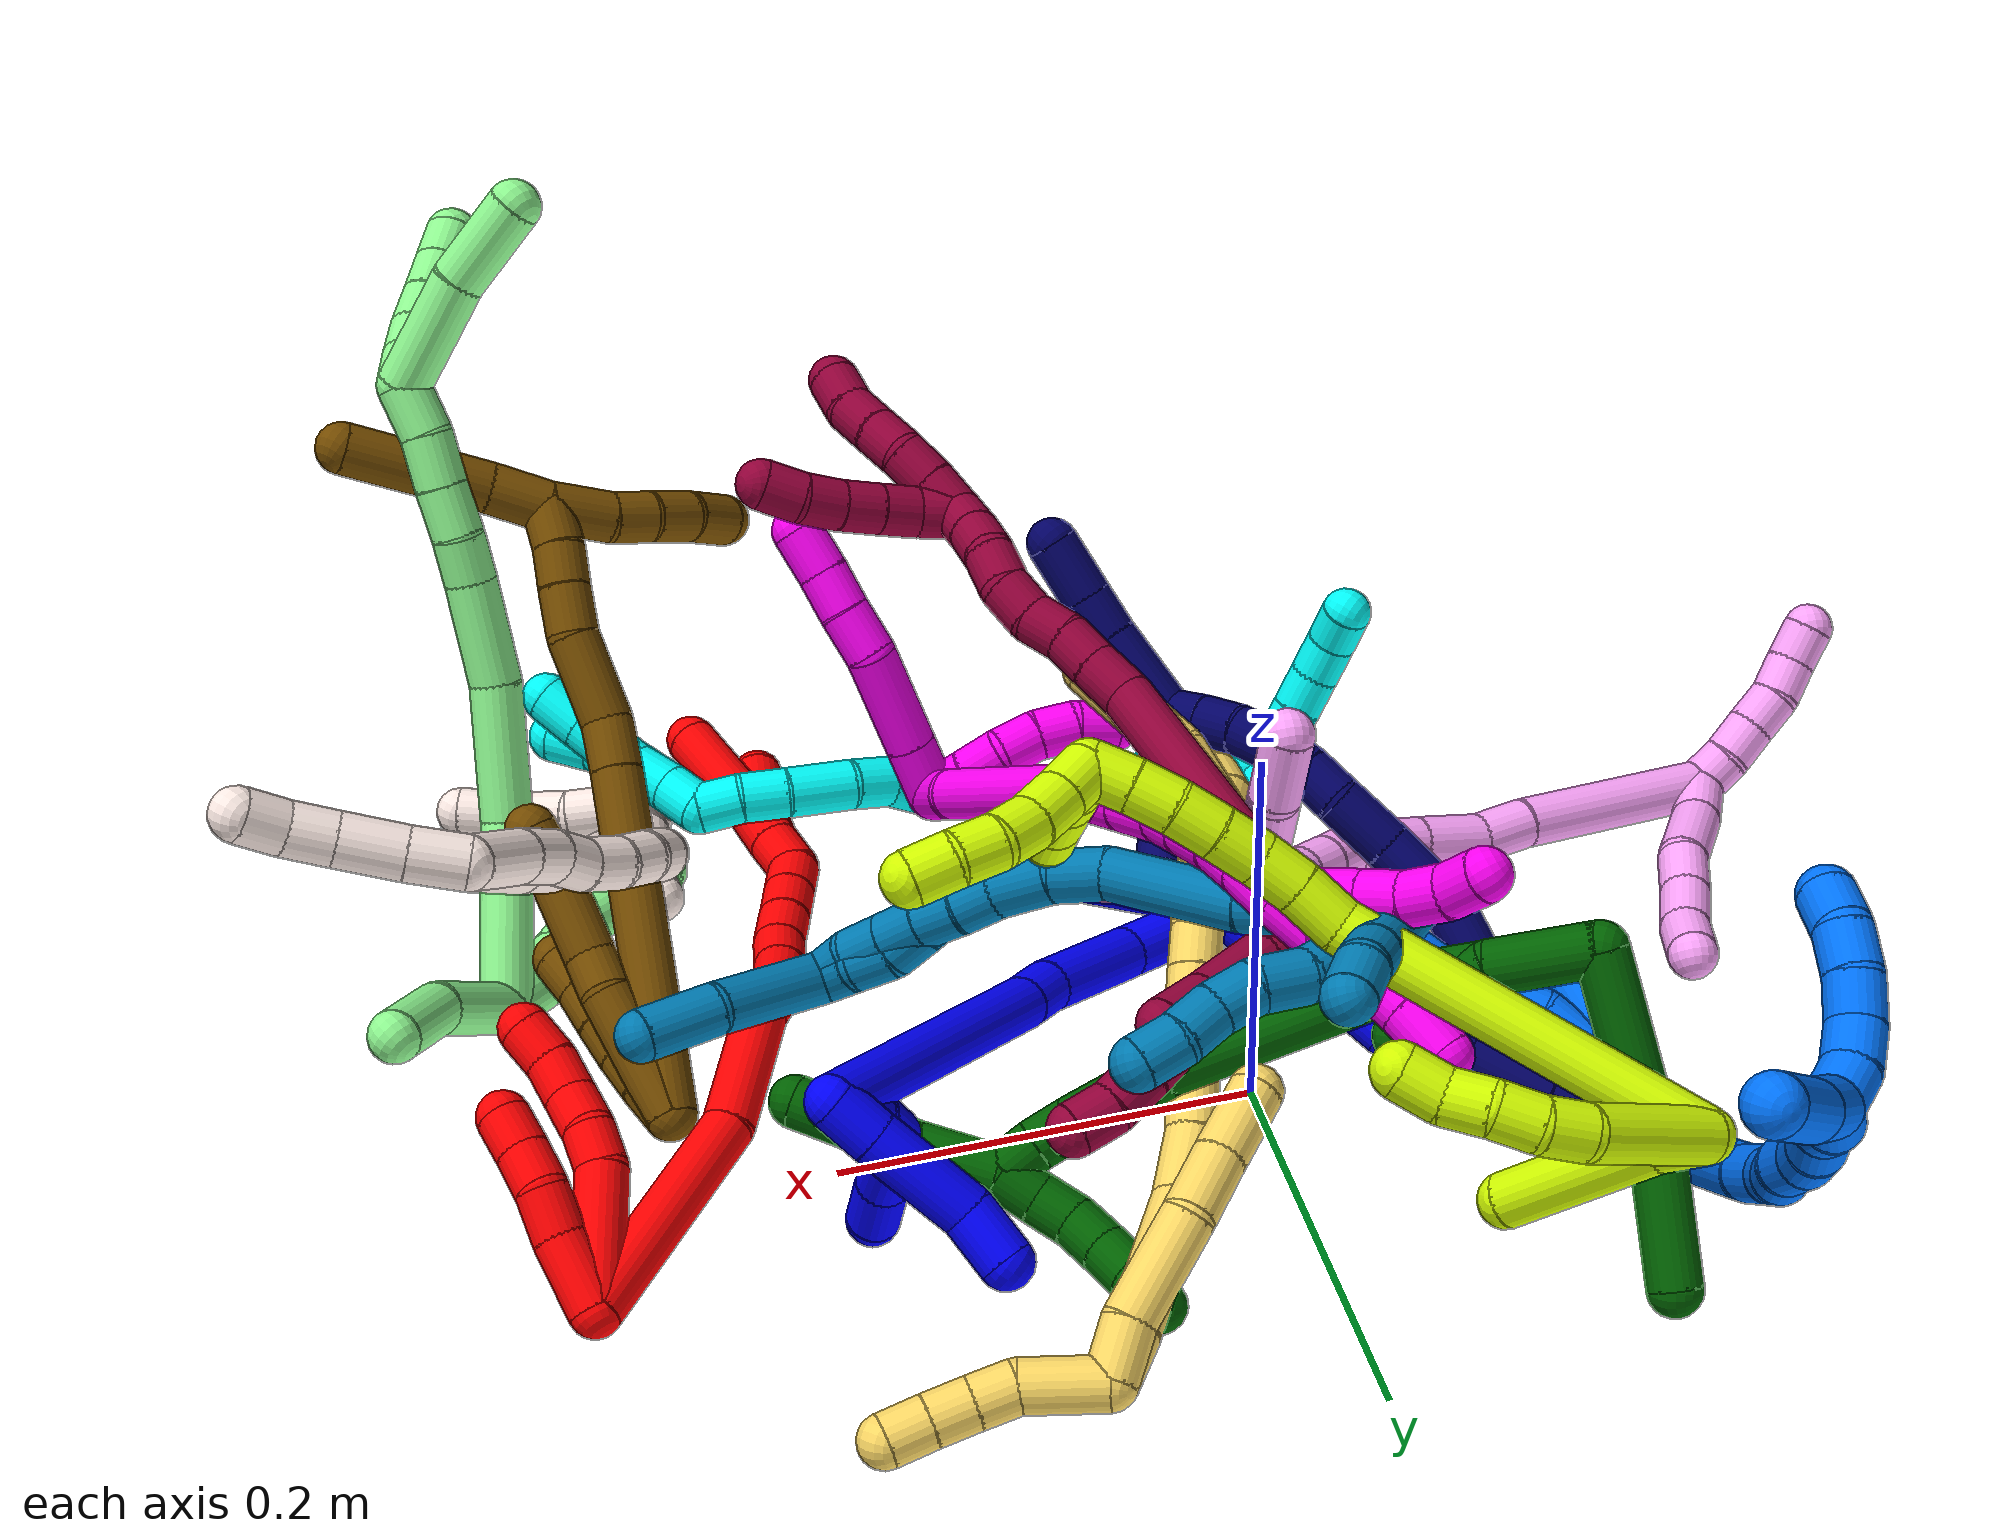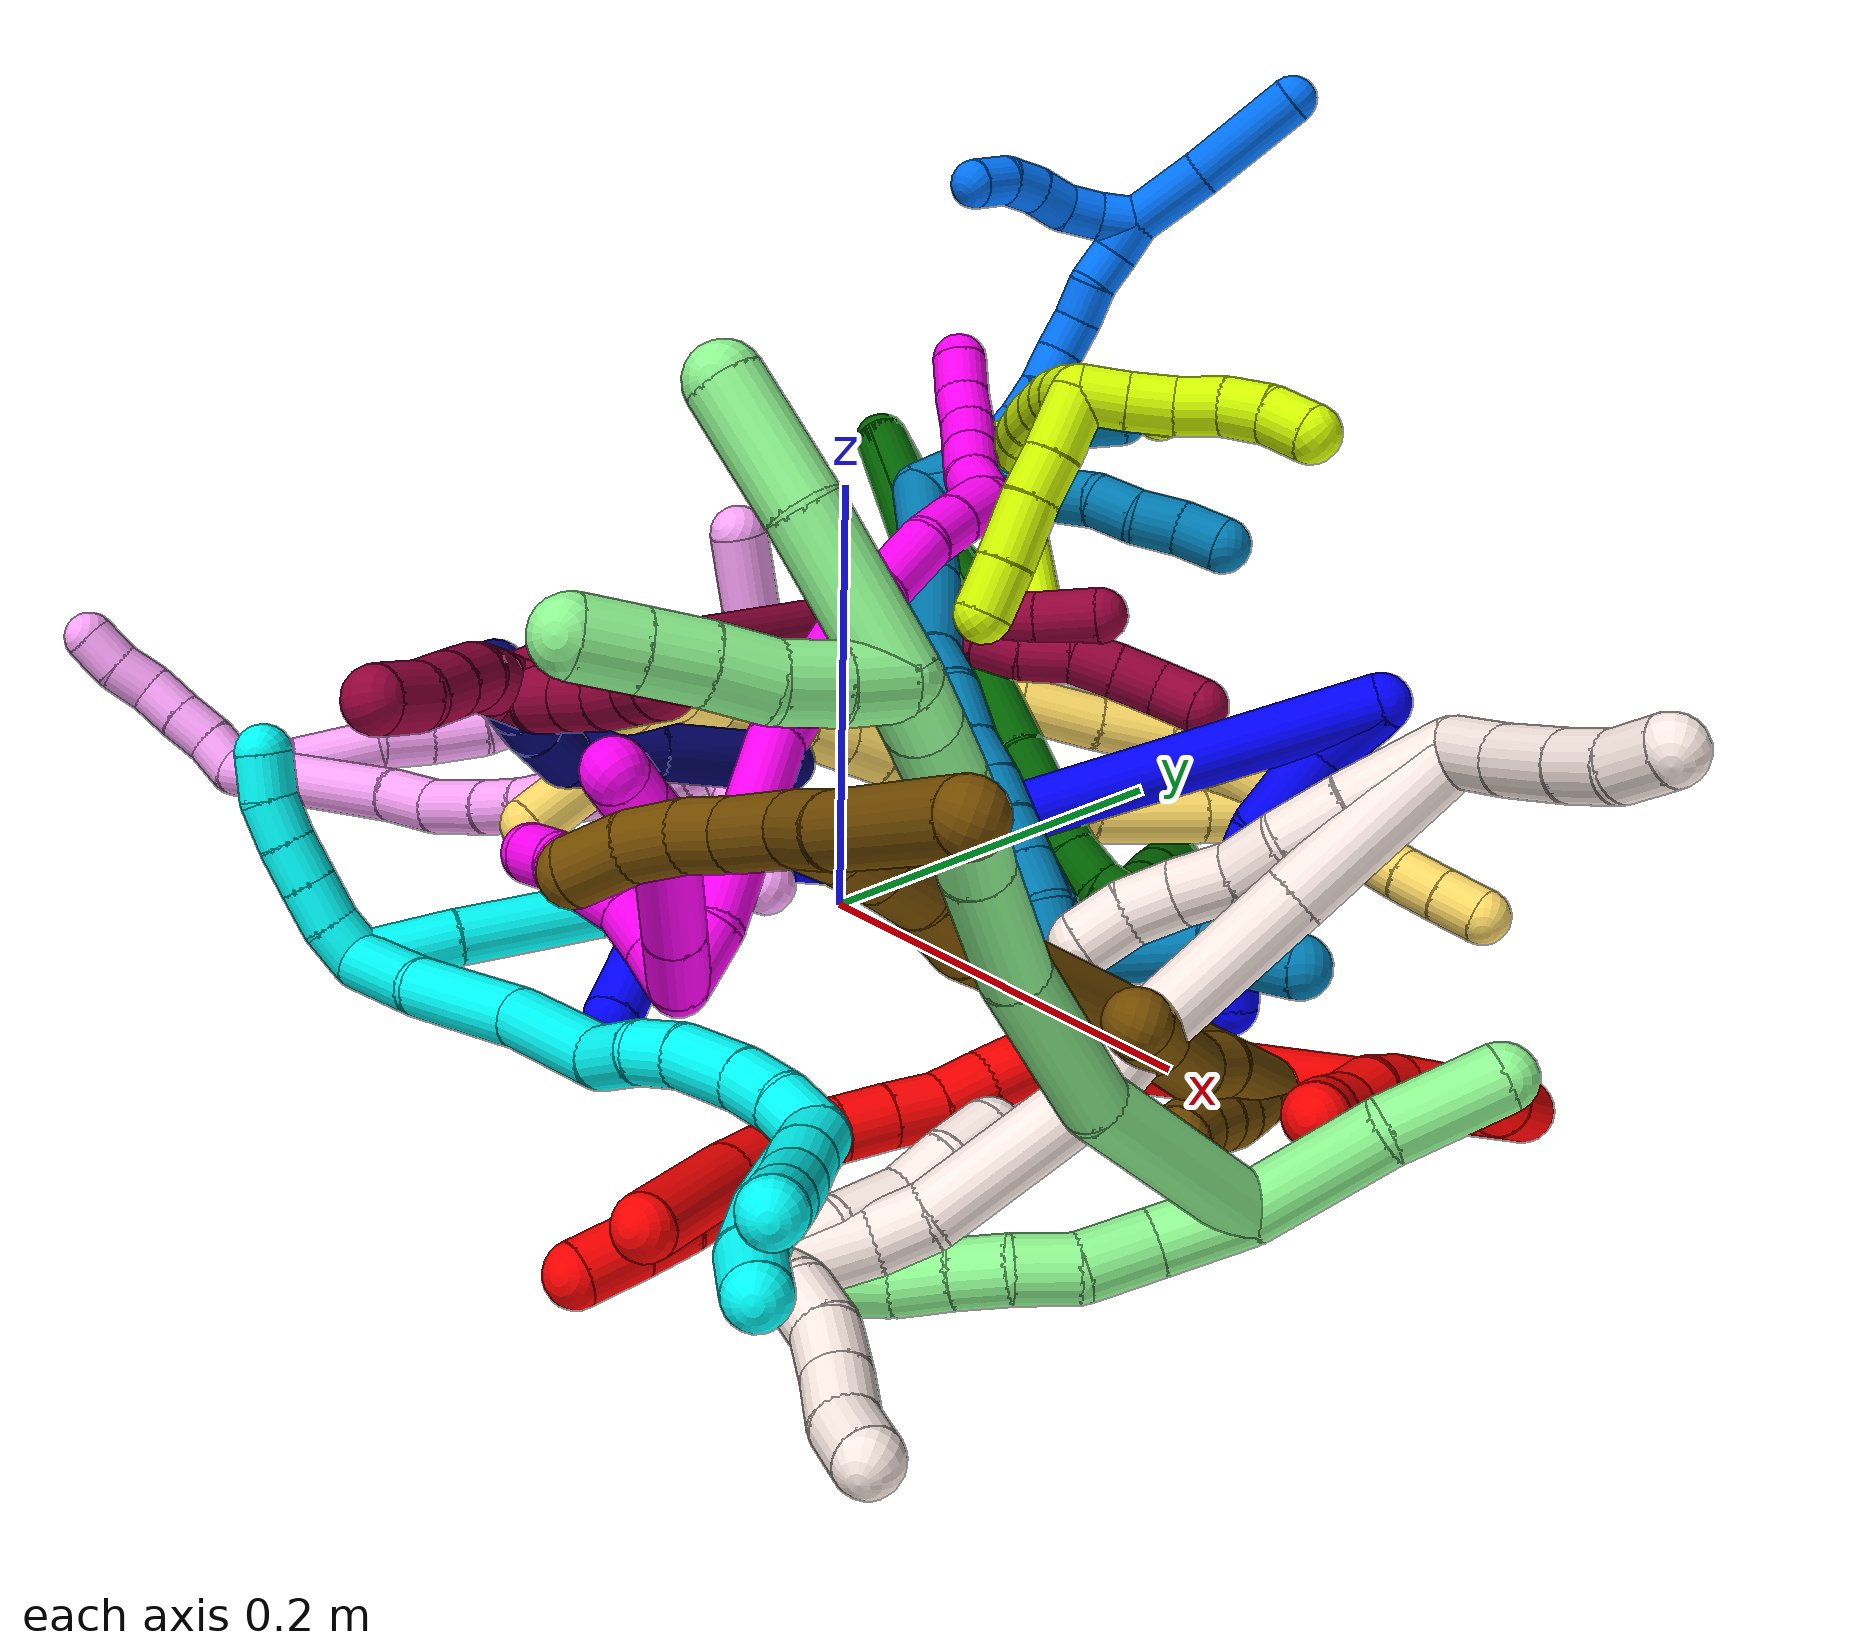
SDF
<sdf version="1.7">
 <world name="default">
  <plugin name="TubeGeneratorPlugin" filename="libtube_generator_plugin.so"/>
  <model name="photoneo_s_sensor">
   <static>1</static>
   <pose>0 0 2 1.57079 1.57079 3.14159</pose>
   <link name="link">
    <inertial><mass>0.1</mass></inertial>
    <sensor name="sensor" type="depth">
     <update_rate>30</update_rate>
     <camera>
      <horizontal_fov>1.22</horizontal_fov>
      <image><width>1920</width><height>1200</height><format>B8G8R8</format></image>
      <clip><near>0.1</near><far>4</far></clip>
      <depth_camera><output>points</output></depth_camera>
     </camera>
     <plugin name="camera_plugin" filename="libgazebo_ros_depth_camera.so">
      <baseline>0.2</baseline>
      <alwaysOn>1</alwaysOn>
      <updateRate>0.0</updateRate>
      <cameraName>camera_ir</cameraName>
      <imageTopicName>/camera/color/image_raw</imageTopicName>
      <cameraInfoTopicName>/camera/color/camera_info</cameraInfoTopicName>
      <depthImageTopicName>/camera/depth/image_raw</depthImageTopicName>
      <depthImageCameraInfoTopicName>/camera/depth/camera_info</depthImageCameraInfoTopicName>
      <pointCloudTopicName>/camera/depth/points</pointCloudTopicName>
      <frameName>fr_optical</frameName>
      <pointCloudCutoff>0.1</pointCloudCutoff>
      <pointCloudCutoffMax>2.0</pointCloudCutoffMax>
      <distortionK1>0</distortionK1>
      <distortionK2>0</distortionK2>
      <distortionK3>0</distortionK3>
      <distortionT1>0</distortionT1>
      <distortionT2>0</distortionT2>
      <CxPrime>0</CxPrime>
      <Cx>0</Cx>
      <Cy>0</Cy>
      <focalLength>0</focalLength>
      <hackBaseline>0</hackBaseline>
     </plugin>
    </sensor>
   </link>
  </model>
  <gravity>0 0 -9.8</gravity>
  <magnetic_field>6e-06 2.3e-05 -4.2e-05</magnetic_field>
  <atmosphere type="adiabatic"/>
  <physics name="default_physics" default="0" type="ode">
   <max_step_size>0.003</max_step_size>
   <real_time_factor>1</real_time_factor>
   <real_time_update_rate>1000</real_time_update_rate>
   <max_contacts>10000</max_contacts>
   <ode>
    <solver>
     <type>quick</type>
     <iters>100</iters>
     <sor>1.3</sor>
     <use_dynamic_moi_rescaling>0</use_dynamic_moi_rescaling>
    </solver>
    <constraints>
     <contact_max_correcting_vel>0</contact_max_correcting_vel>
     <contact_surface_layer>0.001</contact_surface_layer>
     <cfm>0</cfm>
     <erp>0.2</erp>
    </constraints>
   </ode>
  </physics>
  <scene><ambient>0.4 0.4 0.4 1</ambient><background>0.7 0.7 0.7 1</background><shadows>0</shadows></scene>
  <audio><device>default</device></audio>
  <spherical_coordinates>
   <surface_model>EARTH_WGS84</surface_model>
   <latitude_deg>0</latitude_deg>
   <longitude_deg>0</longitude_deg>
   <elevation>0</elevation>
   <heading_deg>0</heading_deg>
  </spherical_coordinates>
  <model name="bin">
   <static>1</static>
   <link name="bottom">
    <collision name="collision-bottom">
     <pose>0 0 -0.01 0 -0 0</pose>
     <geometry><box><size>0.8 0.6 0.02</size></box></geometry>
     <surface>
      <friction><ode><mu>100</mu><mu2>100</mu2></ode></friction>
      <contact><collide_bitmask>65535</collide_bitmask></contact>
     </surface>
    </collision>
   </link>
   <link name="west_wall">
    <collision name="collision-west_wall">
     <pose>-0.41 0 0.1 0 -0 0</pose>
     <geometry><box><size>0.02 0.6 0.2</size></box></geometry>
     <surface>
      <friction><ode><mu>100</mu><mu2>100</mu2></ode></friction>
      <contact><collide_bitmask>65535</collide_bitmask></contact>
     </surface>
    </collision>
   </link>
   <link name="east_wall">
    <collision name="collision-east_wall">
     <pose>0.41 0 0.1 0 -0 0</pose>
     <geometry><box><size>0.02 0.6 0.2</size></box></geometry>
     <surface>
      <friction><ode><mu>100</mu><mu2>100</mu2></ode></friction>
      <contact><collide_bitmask>65535</collide_bitmask></contact>
     </surface>
    </collision>
   </link>
   <link name="south_wall">
    <collision name="collision-south_wall">
     <pose>0 -0.31 0.1 0 -0 0</pose>
     <geometry><box><size>0.8 0.02 0.2</size></box></geometry>
     <surface>
      <friction><ode><mu>100</mu><mu2>100</mu2></ode></friction>
      <contact><collide_bitmask>65535</collide_bitmask></contact>
     </surface>
    </collision>
   </link>
   <link name="north_wall">
    <collision name="collision-north_wall">
     <pose>0 0.31 0.1 0 -0 0</pose>
     <geometry><box><size>0.8 0.02 0.2</size></box></geometry>
     <surface>
      <friction><ode><mu>100</mu><mu2>100</mu2></ode></friction>
      <contact><collide_bitmask>65535</collide_bitmask></contact>
     </surface>
    </collision>
   </link>
  </model>
  <model name="1">
   <static>0</static>
   <link name="1">
    <collision name="collision-cylinder-e_1_2_8">
     <pose>-0.000245 -0.013039 -0.009039 2.17699 -0.015438 -0.029486</pose>
     <geometry><cylinder><radius>0.0125</radius><length>0.031735</length></cylinder></geometry>
     <surface>
      <friction><ode><mu>1.16</mu><mu2>1.16</mu2><slip1>0</slip1><slip2>0</slip2></ode></friction>
      <contact><ode><kp>1e+06</kp><kd>1</kd><max_vel>0</max_vel><min_depth>0.001</min_depth></ode></contact>
     </surface>
    </collision>
    <visual name="visual-cylinder-e_1_2_8">
     <pose>-0.000245 -0.013039 -0.009039 2.17699 -0.015438 -0.029486</pose>
     <geometry><cylinder><radius>0.0125</radius><length>0.031735</length></cylinder></geometry>
     <material><ambient>0 0 1 1</ambient></material>
    </visual>
    <collision name="collision-cylinder-e_2_8_9">
     <pose>0.003306 -0.04509 -0.026472 1.98654 0.180654 0.276217</pose>
     <geometry><cylinder><radius>0.0125</radius><length>0.042253</length></cylinder></geometry>
     <surface>
      <friction><ode><mu>1.16</mu><mu2>1.16</mu2><slip1>0</slip1><slip2>0</slip2></ode></friction>
      <contact><ode><kp>1e+06</kp><kd>1</kd><max_vel>0</max_vel><min_depth>0.001</min_depth></ode></contact>
     </surface>
    </collision>
    <visual name="visual-cylinder-e_2_8_9">
     <pose>0.003306 -0.04509 -0.026472 1.98654 0.180654 0.276217</pose>
     <geometry><cylinder><radius>0.0125</radius><length>0.042253</length></cylinder></geometry>
     <material><ambient>0 0 1 1</ambient></material>
    </visual>
    <collision name="collision-cylinder-e_3_9_10">
     <pose>0.011807 -0.073025 -0.038588 1.96599 0.452942 0.665835</pose>
     <geometry><cylinder><radius>0.0125</radius><length>0.021506</length></cylinder></geometry>
     <surface>
      <friction><ode><mu>1.16</mu><mu2>1.16</mu2><slip1>0</slip1><slip2>0</slip2></ode></friction>
      <contact><ode><kp>1e+06</kp><kd>1</kd><max_vel>0</max_vel><min_depth>0.001</min_depth></ode></contact>
     </surface>
    </collision>
    <visual name="visual-cylinder-e_3_9_10">
     <pose>0.011807 -0.073025 -0.038588 1.96599 0.452942 0.665835</pose>
     <geometry><cylinder><radius>0.0125</radius><length>0.021506</length></cylinder></geometry>
     <material><ambient>0 0 1 1</ambient></material>
    </visual>
    <collision name="collision-cylinder-e_4_10_11">
     <pose>0.025335 -0.092169 -0.045385 1.86299 0.690728 0.901423</pose>
     <geometry><cylinder><radius>0.0125</radius><length>0.027694</length></cylinder></geometry>
     <surface>
      <friction><ode><mu>1.16</mu><mu2>1.16</mu2><slip1>0</slip1><slip2>0</slip2></ode></friction>
      <contact><ode><kp>1e+06</kp><kd>1</kd><max_vel>0</max_vel><min_depth>0.001</min_depth></ode></contact>
     </surface>
    </collision>
    <visual name="visual-cylinder-e_4_10_11">
     <pose>0.025335 -0.092169 -0.045385 1.86299 0.690728 0.901423</pose>
     <geometry><cylinder><radius>0.0125</radius><length>0.027694</length></cylinder></geometry>
     <material><ambient>0 0 1 1</ambient></material>
    </visual>
    <collision name="collision-cylinder-e_5_11_6">
     <pose>0.043695 -0.110824 -0.052655 2.03248 0.791615 1.18699</pose>
     <geometry><cylinder><radius>0.0125</radius><length>0.026813</length></cylinder></geometry>
     <surface>
      <friction><ode><mu>1.16</mu><mu2>1.16</mu2><slip1>0</slip1><slip2>0</slip2></ode></friction>
      <contact><ode><kp>1e+06</kp><kd>1</kd><max_vel>0</max_vel><min_depth>0.001</min_depth></ode></contact>
     </surface>
    </collision>
    <visual name="visual-cylinder-e_5_11_6">
     <pose>0.043695 -0.110824 -0.052655 2.03248 0.791615 1.18699</pose>
     <geometry><cylinder><radius>0.0125</radius><length>0.026813</length></cylinder></geometry>
     <material><ambient>0 0 1 1</ambient></material>
    </visual>
    <collision name="collision-cylinder-e_1_2_12">
     <pose>0.000828 -0.000186 -0.011252 3.12508 0.073416 2.69941</pose>
     <geometry><cylinder><radius>0.0125</radius><length>0.022568</length></cylinder></geometry>
     <surface>
      <friction><ode><mu>1.16</mu><mu2>1.16</mu2><slip1>0</slip1><slip2>0</slip2></ode></friction>
      <contact><ode><kp>1e+06</kp><kd>1</kd><max_vel>0</max_vel><min_depth>0.001</min_depth></ode></contact>
     </surface>
    </collision>
    <visual name="visual-cylinder-e_1_2_12">
     <pose>0.000828 -0.000186 -0.011252 3.12508 0.073416 2.69941</pose>
     <geometry><cylinder><radius>0.0125</radius><length>0.022568</length></cylinder></geometry>
     <material><ambient>0 0 1 1</ambient></material>
    </visual>
    <collision name="collision-cylinder-e_2_12_13">
     <pose>0.002607 -0.001126 -0.047807 3.11179 0.03757 1.80035</pose>
     <geometry><cylinder><radius>0.0125</radius><length>0.050663</length></cylinder></geometry>
     <surface>
      <friction><ode><mu>1.16</mu><mu2>1.16</mu2><slip1>0</slip1><slip2>0</slip2></ode></friction>
      <contact><ode><kp>1e+06</kp><kd>1</kd><max_vel>0</max_vel><min_depth>0.001</min_depth></ode></contact>
     </surface>
    </collision>
    <visual name="visual-cylinder-e_2_12_13">
     <pose>0.002607 -0.001126 -0.047807 3.11179 0.03757 1.80035</pose>
     <geometry><cylinder><radius>0.0125</radius><length>0.050663</length></cylinder></geometry>
     <material><ambient>0 0 1 1</ambient></material>
    </visual>
    <collision name="collision-cylinder-e_3_13_5">
     <pose>0.006606 0.001388 -0.085725 -2.88811 0.229703 -1.47147</pose>
     <geometry><cylinder><radius>0.0125</radius><length>0.026769</length></cylinder></geometry>
     <surface>
      <friction><ode><mu>1.16</mu><mu2>1.16</mu2><slip1>0</slip1><slip2>0</slip2></ode></friction>
      <contact><ode><kp>1e+06</kp><kd>1</kd><max_vel>0</max_vel><min_depth>0.001</min_depth></ode></contact>
     </surface>
    </collision>
    <visual name="visual-cylinder-e_3_13_5">
     <pose>0.006606 0.001388 -0.085725 -2.88811 0.229703 -1.47147</pose>
     <geometry><cylinder><radius>0.0125</radius><length>0.026769</length></cylinder></geometry>
     <material><ambient>0 0 1 1</ambient></material>
    </visual>
    <collision name="collision-cylinder-e_1_2_14">
     <pose>-0.032199 -0.066756 -0.026095 1.94343 -0.422215 -0.608248</pose>
     <geometry><cylinder><radius>0.0125</radius><length>0.157151</length></cylinder></geometry>
     <surface>
      <friction><ode><mu>1.16</mu><mu2>1.16</mu2><slip1>0</slip1><slip2>0</slip2></ode></friction>
      <contact><ode><kp>1e+06</kp><kd>1</kd><max_vel>0</max_vel><min_depth>0.001</min_depth></ode></contact>
     </surface>
    </collision>
    <visual name="visual-cylinder-e_1_2_14">
     <pose>-0.032199 -0.066756 -0.026095 1.94343 -0.422215 -0.608248</pose>
     <geometry><cylinder><radius>0.0125</radius><length>0.157151</length></cylinder></geometry>
     <material><ambient>0 0 1 1</ambient></material>
    </visual>
    <collision name="collision-cylinder-e_2_14_15">
     <pose>-0.069608 -0.143312 -0.05532 1.88002 -0.468834 -0.63206</pose>
     <geometry><cylinder><radius>0.0125</radius><length>0.023064</length></cylinder></geometry>
     <surface>
      <friction><ode><mu>1.16</mu><mu2>1.16</mu2><slip1>0</slip1><slip2>0</slip2></ode></friction>
      <contact><ode><kp>1e+06</kp><kd>1</kd><max_vel>0</max_vel><min_depth>0.001</min_depth></ode></contact>
     </surface>
    </collision>
    <visual name="visual-cylinder-e_2_14_15">
     <pose>-0.069608 -0.143312 -0.05532 1.88002 -0.468834 -0.63206</pose>
     <geometry><cylinder><radius>0.0125</radius><length>0.023064</length></cylinder></geometry>
     <material><ambient>0 0 1 1</ambient></material>
    </visual>
    <collision name="collision-cylinder-e_3_15_16">
     <pose>-0.089667 -0.176668 -0.071044 2.06174 -0.507355 -0.816557</pose>
     <geometry><cylinder><radius>0.0125</radius><length>0.061122</length></cylinder></geometry>
     <surface>
      <friction><ode><mu>1.16</mu><mu2>1.16</mu2><slip1>0</slip1><slip2>0</slip2></ode></friction>
      <contact><ode><kp>1e+06</kp><kd>1</kd><max_vel>0</max_vel><min_depth>0.001</min_depth></ode></contact>
     </surface>
    </collision>
    <visual name="visual-cylinder-e_3_15_16">
     <pose>-0.089667 -0.176668 -0.071044 2.06174 -0.507355 -0.816557</pose>
     <geometry><cylinder><radius>0.0125</radius><length>0.061122</length></cylinder></geometry>
     <material><ambient>0 0 1 1</ambient></material>
    </visual>
    <collision name="collision-cylinder-e_4_16_17">
     <pose>-0.1141 -0.208691 -0.090467 2.24964 -0.72223 -1.33716</pose>
     <geometry><cylinder><radius>0.0125</radius><length>0.028995</length></cylinder></geometry>
     <surface>
      <friction><ode><mu>1.16</mu><mu2>1.16</mu2><slip1>0</slip1><slip2>0</slip2></ode></friction>
      <contact><ode><kp>1e+06</kp><kd>1</kd><max_vel>0</max_vel><min_depth>0.001</min_depth></ode></contact>
     </surface>
    </collision>
    <visual name="visual-cylinder-e_4_16_17">
     <pose>-0.1141 -0.208691 -0.090467 2.24964 -0.72223 -1.33716</pose>
     <geometry><cylinder><radius>0.0125</radius><length>0.028995</length></cylinder></geometry>
     <material><ambient>0 0 1 1</ambient></material>
    </visual>
    <collision name="collision-cylinder-e_5_17_1">
     <pose>-0.134667 -0.225332 -0.103007 2.18045 -0.833704 -1.40825</pose>
     <geometry><cylinder><radius>0.0125</radius><length>0.029668</length></cylinder></geometry>
     <surface>
      <friction><ode><mu>1.16</mu><mu2>1.16</mu2><slip1>0</slip1><slip2>0</slip2></ode></friction>
      <contact><ode><kp>1e+06</kp><kd>1</kd><max_vel>0</max_vel><min_depth>0.001</min_depth></ode></contact>
     </surface>
    </collision>
    <visual name="visual-cylinder-e_5_17_1">
     <pose>-0.134667 -0.225332 -0.103007 2.18045 -0.833704 -1.40825</pose>
     <geometry><cylinder><radius>0.0125</radius><length>0.029668</length></cylinder></geometry>
     <material><ambient>0 0 1 1</ambient></material>
    </visual>
    <collision name="collision-cylinder-e_1_1_18">
     <pose>-0.145367 -0.231892 -0.120761 -3.00843 0.023319 -0.346235</pose>
     <geometry><cylinder><radius>0.0125</radius><length>0.024312</length></cylinder></geometry>
     <surface>
      <friction><ode><mu>1.16</mu><mu2>1.16</mu2><slip1>0</slip1><slip2>0</slip2></ode></friction>
      <contact><ode><kp>1e+06</kp><kd>1</kd><max_vel>0</max_vel><min_depth>0.001</min_depth></ode></contact>
     </surface>
    </collision>
    <visual name="visual-cylinder-e_1_1_18">
     <pose>-0.145367 -0.231892 -0.120761 -3.00843 0.023319 -0.346235</pose>
     <geometry><cylinder><radius>0.0125</radius><length>0.024312</length></cylinder></geometry>
     <material><ambient>0 0 1 1</ambient></material>
    </visual>
    <collision name="collision-cylinder-e_2_18_19">
     <pose>-0.146971 -0.226508 -0.157144 -2.98788 -0.076467 0.922064</pose>
     <geometry><cylinder><radius>0.0125</radius><length>0.049402</length></cylinder></geometry>
     <surface>
      <friction><ode><mu>1.16</mu><mu2>1.16</mu2><slip1>0</slip1><slip2>0</slip2></ode></friction>
      <contact><ode><kp>1e+06</kp><kd>1</kd><max_vel>0</max_vel><min_depth>0.001</min_depth></ode></contact>
     </surface>
    </collision>
    <visual name="visual-cylinder-e_2_18_19">
     <pose>-0.146971 -0.226508 -0.157144 -2.98788 -0.076467 0.922064</pose>
     <geometry><cylinder><radius>0.0125</radius><length>0.049402</length></cylinder></geometry>
     <material><ambient>0 0 1 1</ambient></material>
    </visual>
    <collision name="collision-cylinder-e_3_19_4">
     <pose>-0.14838 -0.219767 -0.194277 -2.91348 0.036373 -0.314924</pose>
     <geometry><cylinder><radius>0.0125</radius><length>0.026286</length></cylinder></geometry>
     <surface>
      <friction><ode><mu>1.16</mu><mu2>1.16</mu2><slip1>0</slip1><slip2>0</slip2></ode></friction>
      <contact><ode><kp>1e+06</kp><kd>1</kd><max_vel>0</max_vel><min_depth>0.001</min_depth></ode></contact>
     </surface>
    </collision>
    <visual name="visual-cylinder-e_3_19_4">
     <pose>-0.14838 -0.219767 -0.194277 -2.91348 0.036373 -0.314924</pose>
     <geometry><cylinder><radius>0.0125</radius><length>0.026286</length></cylinder></geometry>
     <material><ambient>0 0 1 1</ambient></material>
    </visual>
    <collision name="collision-cylinder-e_1_1_20">
     <pose>-0.139551 -0.249845 -0.099221 1.04437 0.312208 0.180647</pose>
     <geometry><cylinder><radius>0.0125</radius><length>0.039716</length></cylinder></geometry>
     <surface>
      <friction><ode><mu>1.16</mu><mu2>1.16</mu2><slip1>0</slip1><slip2>0</slip2></ode></friction>
      <contact><ode><kp>1e+06</kp><kd>1</kd><max_vel>0</max_vel><min_depth>0.001</min_depth></ode></contact>
     </surface>
    </collision>
    <visual name="visual-cylinder-e_1_1_20">
     <pose>-0.139551 -0.249845 -0.099221 1.04437 0.312208 0.180647</pose>
     <geometry><cylinder><radius>0.0125</radius><length>0.039716</length></cylinder></geometry>
     <material><ambient>0 0 1 1</ambient></material>
    </visual>
    <collision name="collision-cylinder-e_2_20_3">
     <pose>-0.122683 -0.290438 -0.075429 1.03816 0.365314 0.210292</pose>
     <geometry><cylinder><radius>0.0125</radius><length>0.060284</length></cylinder></geometry>
     <surface>
      <friction><ode><mu>1.16</mu><mu2>1.16</mu2><slip1>0</slip1><slip2>0</slip2></ode></friction>
      <contact><ode><kp>1e+06</kp><kd>1</kd><max_vel>0</max_vel><min_depth>0.001</min_depth></ode></contact>
     </surface>
    </collision>
    <visual name="visual-cylinder-e_2_20_3">
     <pose>-0.122683 -0.290438 -0.075429 1.03816 0.365314 0.210292</pose>
     <geometry><cylinder><radius>0.0125</radius><length>0.060284</length></cylinder></geometry>
     <material><ambient>0 0 1 1</ambient></material>
    </visual>
    <collision name="collision-sphere-3">
     <pose>-0.111915 -0.314691 -0.061133 0 -0 0</pose>
     <geometry><sphere><radius>0.0125</radius></sphere></geometry>
     <surface>
      <friction><ode><mu>1.16</mu><mu2>1.16</mu2><slip1>0</slip1><slip2>0</slip2></ode></friction>
      <contact><ode><kp>1e+06</kp><kd>1</kd><max_vel>0</max_vel><min_depth>0.001</min_depth></ode></contact>
     </surface>
    </collision>
    <visual name="visual-sphere-3">
     <pose>-0.111915 -0.314691 -0.061133 0 -0 0</pose>
     <geometry><sphere><radius>0.0125</radius></sphere></geometry>
     <material><ambient>0 0 1 1</ambient></material>
    </visual>
    <collision name="collision-sphere-20">
     <pose>-0.133452 -0.266185 -0.089725 0 -0 0</pose>
     <geometry><sphere><radius>0.0125</radius></sphere></geometry>
     <surface>
      <friction><ode><mu>1.16</mu><mu2>1.16</mu2><slip1>0</slip1><slip2>0</slip2></ode></friction>
      <contact><ode><kp>1e+06</kp><kd>1</kd><max_vel>0</max_vel><min_depth>0.001</min_depth></ode></contact>
     </surface>
    </collision>
    <visual name="visual-sphere-20">
     <pose>-0.133452 -0.266185 -0.089725 0 -0 0</pose>
     <geometry><sphere><radius>0.0125</radius></sphere></geometry>
     <material><ambient>0 0 1 1</ambient></material>
    </visual>
    <collision name="collision-sphere-4">
     <pose>-0.147902 -0.216797 -0.207071 0 -0 0</pose>
     <geometry><sphere><radius>0.0125</radius></sphere></geometry>
     <surface>
      <friction><ode><mu>1.16</mu><mu2>1.16</mu2><slip1>0</slip1><slip2>0</slip2></ode></friction>
      <contact><ode><kp>1e+06</kp><kd>1</kd><max_vel>0</max_vel><min_depth>0.001</min_depth></ode></contact>
     </surface>
    </collision>
    <visual name="visual-sphere-4">
     <pose>-0.147902 -0.216797 -0.207071 0 -0 0</pose>
     <geometry><sphere><radius>0.0125</radius></sphere></geometry>
     <material><ambient>0 0 1 1</ambient></material>
    </visual>
    <collision name="collision-sphere-6">
     <pose>0.053234 -0.119258 -0.056852 0 -0 0</pose>
     <geometry><sphere><radius>0.0125</radius></sphere></geometry>
     <surface>
      <friction><ode><mu>1.16</mu><mu2>1.16</mu2><slip1>0</slip1><slip2>0</slip2></ode></friction>
      <contact><ode><kp>1e+06</kp><kd>1</kd><max_vel>0</max_vel><min_depth>0.001</min_depth></ode></contact>
     </surface>
    </collision>
    <visual name="visual-sphere-6">
     <pose>0.053234 -0.119258 -0.056852 0 -0 0</pose>
     <geometry><sphere><radius>0.0125</radius></sphere></geometry>
     <material><ambient>0 0 1 1</ambient></material>
    </visual>
    <collision name="collision-sphere-11">
     <pose>0.034157 -0.10239 -0.048459 0 -0 0</pose>
     <geometry><sphere><radius>0.0125</radius></sphere></geometry>
     <surface>
      <friction><ode><mu>1.16</mu><mu2>1.16</mu2><slip1>0</slip1><slip2>0</slip2></ode></friction>
      <contact><ode><kp>1e+06</kp><kd>1</kd><max_vel>0</max_vel><min_depth>0.001</min_depth></ode></contact>
     </surface>
    </collision>
    <visual name="visual-sphere-11">
     <pose>0.034157 -0.10239 -0.048459 0 -0 0</pose>
     <geometry><sphere><radius>0.0125</radius></sphere></geometry>
     <material><ambient>0 0 1 1</ambient></material>
    </visual>
    <collision name="collision-sphere-10">
     <pose>0.016513 -0.081949 -0.04231 0 -0 0</pose>
     <geometry><sphere><radius>0.0125</radius></sphere></geometry>
     <surface>
      <friction><ode><mu>1.16</mu><mu2>1.16</mu2><slip1>0</slip1><slip2>0</slip2></ode></friction>
      <contact><ode><kp>1e+06</kp><kd>1</kd><max_vel>0</max_vel><min_depth>0.001</min_depth></ode></contact>
     </surface>
    </collision>
    <visual name="visual-sphere-10">
     <pose>0.016513 -0.081949 -0.04231 0 -0 0</pose>
     <geometry><sphere><radius>0.0125</radius></sphere></geometry>
     <material><ambient>0 0 1 1</ambient></material>
    </visual>
    <collision name="collision-sphere-9">
     <pose>0.007102 -0.064102 -0.034866 0 -0 0</pose>
     <geometry><sphere><radius>0.0125</radius></sphere></geometry>
     <surface>
      <friction><ode><mu>1.16</mu><mu2>1.16</mu2><slip1>0</slip1><slip2>0</slip2></ode></friction>
      <contact><ode><kp>1e+06</kp><kd>1</kd><max_vel>0</max_vel><min_depth>0.001</min_depth></ode></contact>
     </surface>
    </collision>
    <visual name="visual-sphere-9">
     <pose>0.007102 -0.064102 -0.034866 0 -0 0</pose>
     <geometry><sphere><radius>0.0125</radius></sphere></geometry>
     <material><ambient>0 0 1 1</ambient></material>
    </visual>
    <collision name="collision-sphere-2">
     <geometry><sphere><radius>0.0125</radius></sphere></geometry>
     <surface>
      <friction><ode><mu>1.16</mu><mu2>1.16</mu2><slip1>0</slip1><slip2>0</slip2></ode></friction>
      <contact><ode><kp>1e+06</kp><kd>1</kd><max_vel>0</max_vel><min_depth>0.001</min_depth></ode></contact>
     </surface>
    </collision>
    <visual name="visual-sphere-2">
     <geometry><sphere><radius>0.0125</radius></sphere></geometry>
     <material><ambient>0 0 1 1</ambient></material>
    </visual>
    <collision name="collision-sphere-19">
     <pose>-0.148858 -0.222737 -0.181482 0 -0 0</pose>
     <geometry><sphere><radius>0.0125</radius></sphere></geometry>
     <surface>
      <friction><ode><mu>1.16</mu><mu2>1.16</mu2><slip1>0</slip1><slip2>0</slip2></ode></friction>
      <contact><ode><kp>1e+06</kp><kd>1</kd><max_vel>0</max_vel><min_depth>0.001</min_depth></ode></contact>
     </surface>
    </collision>
    <visual name="visual-sphere-19">
     <pose>-0.148858 -0.222737 -0.181482 0 -0 0</pose>
     <geometry><sphere><radius>0.0125</radius></sphere></geometry>
     <material><ambient>0 0 1 1</ambient></material>
    </visual>
    <collision name="collision-sphere-8">
     <pose>-0.00049 -0.026077 -0.018079 0 -0 0</pose>
     <geometry><sphere><radius>0.0125</radius></sphere></geometry>
     <surface>
      <friction><ode><mu>1.16</mu><mu2>1.16</mu2><slip1>0</slip1><slip2>0</slip2></ode></friction>
      <contact><ode><kp>1e+06</kp><kd>1</kd><max_vel>0</max_vel><min_depth>0.001</min_depth></ode></contact>
     </surface>
    </collision>
    <visual name="visual-sphere-8">
     <pose>-0.00049 -0.026077 -0.018079 0 -0 0</pose>
     <geometry><sphere><radius>0.0125</radius></sphere></geometry>
     <material><ambient>0 0 1 1</ambient></material>
    </visual>
    <collision name="collision-sphere-12">
     <pose>0.001655 -0.000372 -0.022504 0 -0 0</pose>
     <geometry><sphere><radius>0.0125</radius></sphere></geometry>
     <surface>
      <friction><ode><mu>1.16</mu><mu2>1.16</mu2><slip1>0</slip1><slip2>0</slip2></ode></friction>
      <contact><ode><kp>1e+06</kp><kd>1</kd><max_vel>0</max_vel><min_depth>0.001</min_depth></ode></contact>
     </surface>
    </collision>
    <visual name="visual-sphere-12">
     <pose>0.001655 -0.000372 -0.022504 0 -0 0</pose>
     <geometry><sphere><radius>0.0125</radius></sphere></geometry>
     <material><ambient>0 0 1 1</ambient></material>
    </visual>
    <collision name="collision-sphere-13">
     <pose>0.003558 -0.00188 -0.073109 0 -0 0</pose>
     <geometry><sphere><radius>0.0125</radius></sphere></geometry>
     <surface>
      <friction><ode><mu>1.16</mu><mu2>1.16</mu2><slip1>0</slip1><slip2>0</slip2></ode></friction>
      <contact><ode><kp>1e+06</kp><kd>1</kd><max_vel>0</max_vel><min_depth>0.001</min_depth></ode></contact>
     </surface>
    </collision>
    <visual name="visual-sphere-13">
     <pose>0.003558 -0.00188 -0.073109 0 -0 0</pose>
     <geometry><sphere><radius>0.0125</radius></sphere></geometry>
     <material><ambient>0 0 1 1</ambient></material>
    </visual>
    <collision name="collision-sphere-5">
     <pose>0.009653 0.004657 -0.098342 0 -0 0</pose>
     <geometry><sphere><radius>0.0125</radius></sphere></geometry>
     <surface>
      <friction><ode><mu>1.16</mu><mu2>1.16</mu2><slip1>0</slip1><slip2>0</slip2></ode></friction>
      <contact><ode><kp>1e+06</kp><kd>1</kd><max_vel>0</max_vel><min_depth>0.001</min_depth></ode></contact>
     </surface>
    </collision>
    <visual name="visual-sphere-5">
     <pose>0.009653 0.004657 -0.098342 0 -0 0</pose>
     <geometry><sphere><radius>0.0125</radius></sphere></geometry>
     <material><ambient>0 0 1 1</ambient></material>
    </visual>
    <collision name="collision-sphere-14">
     <pose>-0.064398 -0.133513 -0.05219 0 -0 0</pose>
     <geometry><sphere><radius>0.0125</radius></sphere></geometry>
     <surface>
      <friction><ode><mu>1.16</mu><mu2>1.16</mu2><slip1>0</slip1><slip2>0</slip2></ode></friction>
      <contact><ode><kp>1e+06</kp><kd>1</kd><max_vel>0</max_vel><min_depth>0.001</min_depth></ode></contact>
     </surface>
    </collision>
    <visual name="visual-sphere-14">
     <pose>-0.064398 -0.133513 -0.05219 0 -0 0</pose>
     <geometry><sphere><radius>0.0125</radius></sphere></geometry>
     <material><ambient>0 0 1 1</ambient></material>
    </visual>
    <collision name="collision-sphere-15">
     <pose>-0.074819 -0.153112 -0.058451 0 -0 0</pose>
     <geometry><sphere><radius>0.0125</radius></sphere></geometry>
     <surface>
      <friction><ode><mu>1.16</mu><mu2>1.16</mu2><slip1>0</slip1><slip2>0</slip2></ode></friction>
      <contact><ode><kp>1e+06</kp><kd>1</kd><max_vel>0</max_vel><min_depth>0.001</min_depth></ode></contact>
     </surface>
    </collision>
    <visual name="visual-sphere-15">
     <pose>-0.074819 -0.153112 -0.058451 0 -0 0</pose>
     <geometry><sphere><radius>0.0125</radius></sphere></geometry>
     <material><ambient>0 0 1 1</ambient></material>
    </visual>
    <collision name="collision-sphere-16">
     <pose>-0.104516 -0.200224 -0.083637 0 -0 0</pose>
     <geometry><sphere><radius>0.0125</radius></sphere></geometry>
     <surface>
      <friction><ode><mu>1.16</mu><mu2>1.16</mu2><slip1>0</slip1><slip2>0</slip2></ode></friction>
      <contact><ode><kp>1e+06</kp><kd>1</kd><max_vel>0</max_vel><min_depth>0.001</min_depth></ode></contact>
     </surface>
    </collision>
    <visual name="visual-sphere-16">
     <pose>-0.104516 -0.200224 -0.083637 0 -0 0</pose>
     <geometry><sphere><radius>0.0125</radius></sphere></geometry>
     <material><ambient>0 0 1 1</ambient></material>
    </visual>
    <collision name="collision-sphere-17">
     <pose>-0.123684 -0.217157 -0.097298 0 -0 0</pose>
     <geometry><sphere><radius>0.0125</radius></sphere></geometry>
     <surface>
      <friction><ode><mu>1.16</mu><mu2>1.16</mu2><slip1>0</slip1><slip2>0</slip2></ode></friction>
      <contact><ode><kp>1e+06</kp><kd>1</kd><max_vel>0</max_vel><min_depth>0.001</min_depth></ode></contact>
     </surface>
    </collision>
    <visual name="visual-sphere-17">
     <pose>-0.123684 -0.217157 -0.097298 0 -0 0</pose>
     <geometry><sphere><radius>0.0125</radius></sphere></geometry>
     <material><ambient>0 0 1 1</ambient></material>
    </visual>
    <collision name="collision-sphere-1">
     <pose>-0.145651 -0.233506 -0.108716 0 -0 0</pose>
     <geometry><sphere><radius>0.0125</radius></sphere></geometry>
     <surface>
      <friction><ode><mu>1.16</mu><mu2>1.16</mu2><slip1>0</slip1><slip2>0</slip2></ode></friction>
      <contact><ode><kp>1e+06</kp><kd>1</kd><max_vel>0</max_vel><min_depth>0.001</min_depth></ode></contact>
     </surface>
    </collision>
    <visual name="visual-sphere-1">
     <pose>-0.145651 -0.233506 -0.108716 0 -0 0</pose>
     <geometry><sphere><radius>0.0125</radius></sphere></geometry>
     <material><ambient>0 0 1 1</ambient></material>
    </visual>
    <collision name="collision-sphere-18">
     <pose>-0.145084 -0.230279 -0.132806 0 -0 0</pose>
     <geometry><sphere><radius>0.0125</radius></sphere></geometry>
     <surface>
      <friction><ode><mu>1.16</mu><mu2>1.16</mu2><slip1>0</slip1><slip2>0</slip2></ode></friction>
      <contact><ode><kp>1e+06</kp><kd>1</kd><max_vel>0</max_vel><min_depth>0.001</min_depth></ode></contact>
     </surface>
    </collision>
    <visual name="visual-sphere-18">
     <pose>-0.145084 -0.230279 -0.132806 0 -0 0</pose>
     <geometry><sphere><radius>0.0125</radius></sphere></geometry>
     <material><ambient>0 0 1 1</ambient></material>
    </visual>
    <inertial>
     <pose>-0.059329 -0.129072 -0.066089 0 -0 0</pose>
     <mass>0.75</mass>
     <inertia>
      <ixx>0.000144</ixx>
      <ixy>0</ixy>
      <ixz>0</ixz>
      <iyy>-0.000212</iyy>
      <iyz>0</iyz>
      <izz>0.000447</izz>
     </inertia>
    </inertial>
   </link>
   <pose>0.217325 0.097738 0.140945 0.801224 0.714687 0.358367</pose>
  </model>
  <model name="2">
   <static>0</static>
   <link name="2">
    <collision name="collision-cylinder-e_1_2_8">
     <pose>0.007614 -0.015639 -0.029075 2.64811 0.226669 0.848862</pose>
     <geometry><cylinder><radius>0.0125</radius><length>0.067761</length></cylinder></geometry>
     <surface>
      <friction><ode><mu>1.16</mu><mu2>1.16</mu2><slip1>0</slip1><slip2>0</slip2></ode></friction>
      <contact><ode><kp>1e+06</kp><kd>1</kd><max_vel>0</max_vel><min_depth>0.001</min_depth></ode></contact>
     </surface>
    </collision>
    <visual name="visual-cylinder-e_1_2_8">
     <pose>0.007614 -0.015639 -0.029075 2.64811 0.226669 0.848862</pose>
     <geometry><cylinder><radius>0.0125</radius><length>0.067761</length></cylinder></geometry>
     <material><ambient>1 0 0 1</ambient></material>
    </visual>
    <collision name="collision-cylinder-e_2_8_9">
     <pose>0.015339 -0.033477 -0.068029 2.92248 0.010993 0.099863</pose>
     <geometry><cylinder><radius>0.0125</radius><length>0.020244</length></cylinder></geometry>
     <surface>
      <friction><ode><mu>1.16</mu><mu2>1.16</mu2><slip1>0</slip1><slip2>0</slip2></ode></friction>
      <contact><ode><kp>1e+06</kp><kd>1</kd><max_vel>0</max_vel><min_depth>0.001</min_depth></ode></contact>
     </surface>
    </collision>
    <visual name="visual-cylinder-e_2_8_9">
     <pose>0.015339 -0.033477 -0.068029 2.92248 0.010993 0.099863</pose>
     <geometry><cylinder><radius>0.0125</radius><length>0.020244</length></cylinder></geometry>
     <material><ambient>1 0 0 1</ambient></material>
    </visual>
    <collision name="collision-cylinder-e_3_9_10">
     <pose>0.012768 -0.038522 -0.087687 2.8585 -0.257589 -1.47536</pose>
     <geometry><cylinder><radius>0.0125</radius><length>0.021063</length></cylinder></geometry>
     <surface>
      <friction><ode><mu>1.16</mu><mu2>1.16</mu2><slip1>0</slip1><slip2>0</slip2></ode></friction>
      <contact><ode><kp>1e+06</kp><kd>1</kd><max_vel>0</max_vel><min_depth>0.001</min_depth></ode></contact>
     </surface>
    </collision>
    <visual name="visual-cylinder-e_3_9_10">
     <pose>0.012768 -0.038522 -0.087687 2.8585 -0.257589 -1.47536</pose>
     <geometry><cylinder><radius>0.0125</radius><length>0.021063</length></cylinder></geometry>
     <material><ambient>1 0 0 1</ambient></material>
    </visual>
    <collision name="collision-cylinder-e_4_10_11">
     <pose>0.009411 -0.04235 -0.107799 3.0467 -0.064828 -1.19826</pose>
     <geometry><cylinder><radius>0.0125</radius><length>0.020803</length></cylinder></geometry>
     <surface>
      <friction><ode><mu>1.16</mu><mu2>1.16</mu2><slip1>0</slip1><slip2>0</slip2></ode></friction>
      <contact><ode><kp>1e+06</kp><kd>1</kd><max_vel>0</max_vel><min_depth>0.001</min_depth></ode></contact>
     </surface>
    </collision>
    <visual name="visual-cylinder-e_4_10_11">
     <pose>0.009411 -0.04235 -0.107799 3.0467 -0.064828 -1.19826</pose>
     <geometry><cylinder><radius>0.0125</radius><length>0.020803</length></cylinder></geometry>
     <material><ambient>1 0 0 1</ambient></material>
    </visual>
    <collision name="collision-cylinder-e_5_11_6">
     <pose>0.007385 -0.042229 -0.128044 -3.03055 -0.134768 1.76369</pose>
     <geometry><cylinder><radius>0.0125</radius><length>0.020129</length></cylinder></geometry>
     <surface>
      <friction><ode><mu>1.16</mu><mu2>1.16</mu2><slip1>0</slip1><slip2>0</slip2></ode></friction>
      <contact><ode><kp>1e+06</kp><kd>1</kd><max_vel>0</max_vel><min_depth>0.001</min_depth></ode></contact>
     </surface>
    </collision>
    <visual name="visual-cylinder-e_5_11_6">
     <pose>0.007385 -0.042229 -0.128044 -3.03055 -0.134768 1.76369</pose>
     <geometry><cylinder><radius>0.0125</radius><length>0.020129</length></cylinder></geometry>
     <material><ambient>1 0 0 1</ambient></material>
    </visual>
    <collision name="collision-cylinder-e_1_2_12">
     <pose>0.001166 -5.1e-05 -0.018027 3.13879 0.064607 3.05495</pose>
     <geometry><cylinder><radius>0.0125</radius><length>0.036129</length></cylinder></geometry>
     <surface>
      <friction><ode><mu>1.16</mu><mu2>1.16</mu2><slip1>0</slip1><slip2>0</slip2></ode></friction>
      <contact><ode><kp>1e+06</kp><kd>1</kd><max_vel>0</max_vel><min_depth>0.001</min_depth></ode></contact>
     </surface>
    </collision>
    <visual name="visual-cylinder-e_1_2_12">
     <pose>0.001166 -5.1e-05 -0.018027 3.13879 0.064607 3.05495</pose>
     <geometry><cylinder><radius>0.0125</radius><length>0.036129</length></cylinder></geometry>
     <material><ambient>1 0 0 1</ambient></material>
    </visual>
    <collision name="collision-cylinder-e_2_12_13">
     <pose>0.004687 -0.000326 -0.04759 3.12209 0.201323 2.94909</pose>
     <geometry><cylinder><radius>0.0125</radius><length>0.023552</length></cylinder></geometry>
     <surface>
      <friction><ode><mu>1.16</mu><mu2>1.16</mu2><slip1>0</slip1><slip2>0</slip2></ode></friction>
      <contact><ode><kp>1e+06</kp><kd>1</kd><max_vel>0</max_vel><min_depth>0.001</min_depth></ode></contact>
     </surface>
    </collision>
    <visual name="visual-cylinder-e_2_12_13">
     <pose>0.004687 -0.000326 -0.04759 3.12209 0.201323 2.94909</pose>
     <geometry><cylinder><radius>0.0125</radius><length>0.023552</length></cylinder></geometry>
     <material><ambient>1 0 0 1</ambient></material>
    </visual>
    <collision name="collision-cylinder-e_3_13_14">
     <pose>0.006141 -0.00197 -0.06914 3.00088 -0.088865 -1.12568</pose>
     <geometry><cylinder><radius>0.0125</radius><length>0.020309</length></cylinder></geometry>
     <surface>
      <friction><ode><mu>1.16</mu><mu2>1.16</mu2><slip1>0</slip1><slip2>0</slip2></ode></friction>
      <contact><ode><kp>1e+06</kp><kd>1</kd><max_vel>0</max_vel><min_depth>0.001</min_depth></ode></contact>
     </surface>
    </collision>
    <visual name="visual-cylinder-e_3_13_14">
     <pose>0.006141 -0.00197 -0.06914 3.00088 -0.088865 -1.12568</pose>
     <geometry><cylinder><radius>0.0125</radius><length>0.020309</length></cylinder></geometry>
     <material><ambient>1 0 0 1</ambient></material>
    </visual>
    <collision name="collision-cylinder-e_4_14_5">
     <pose>0.004258 -0.004322 -0.089067 3.04762 -0.098312 -1.61599</pose>
     <geometry><cylinder><radius>0.0125</radius><length>0.020009</length></cylinder></geometry>
     <surface>
      <friction><ode><mu>1.16</mu><mu2>1.16</mu2><slip1>0</slip1><slip2>0</slip2></ode></friction>
      <contact><ode><kp>1e+06</kp><kd>1</kd><max_vel>0</max_vel><min_depth>0.001</min_depth></ode></contact>
     </surface>
    </collision>
    <visual name="visual-cylinder-e_4_14_5">
     <pose>0.004258 -0.004322 -0.089067 3.04762 -0.098312 -1.61599</pose>
     <geometry><cylinder><radius>0.0125</radius><length>0.020009</length></cylinder></geometry>
     <material><ambient>1 0 0 1</ambient></material>
    </visual>
    <collision name="collision-cylinder-e_1_2_15">
     <pose>0.017577 -0.047404 -0.027234 2.09226 0.311076 0.529148</pose>
     <geometry><cylinder><radius>0.0125</radius><length>0.114854</length></cylinder></geometry>
     <surface>
      <friction><ode><mu>1.16</mu><mu2>1.16</mu2><slip1>0</slip1><slip2>0</slip2></ode></friction>
      <contact><ode><kp>1e+06</kp><kd>1</kd><max_vel>0</max_vel><min_depth>0.001</min_depth></ode></contact>
     </surface>
    </collision>
    <visual name="visual-cylinder-e_1_2_15">
     <pose>0.017577 -0.047404 -0.027234 2.09226 0.311076 0.529148</pose>
     <geometry><cylinder><radius>0.0125</radius><length>0.114854</length></cylinder></geometry>
     <material><ambient>1 0 0 1</ambient></material>
    </visual>
    <collision name="collision-cylinder-e_2_15_16">
     <pose>0.042861 -0.114946 -0.076326 2.39714 0.253701 0.631453</pose>
     <geometry><cylinder><radius>0.0125</radius><length>0.061406</length></cylinder></geometry>
     <surface>
      <friction><ode><mu>1.16</mu><mu2>1.16</mu2><slip1>0</slip1><slip2>0</slip2></ode></friction>
      <contact><ode><kp>1e+06</kp><kd>1</kd><max_vel>0</max_vel><min_depth>0.001</min_depth></ode></contact>
     </surface>
    </collision>
    <visual name="visual-cylinder-e_2_15_16">
     <pose>0.042861 -0.114946 -0.076326 2.39714 0.253701 0.631453</pose>
     <geometry><cylinder><radius>0.0125</radius><length>0.061406</length></cylinder></geometry>
     <material><ambient>1 0 0 1</ambient></material>
    </visual>
    <collision name="collision-cylinder-e_3_16_17">
     <pose>0.051138 -0.14453 -0.103971 2.1204 0.051542 0.091971</pose>
     <geometry><cylinder><radius>0.0125</radius><length>0.022185</length></cylinder></geometry>
     <surface>
      <friction><ode><mu>1.16</mu><mu2>1.16</mu2><slip1>0</slip1><slip2>0</slip2></ode></friction>
      <contact><ode><kp>1e+06</kp><kd>1</kd><max_vel>0</max_vel><min_depth>0.001</min_depth></ode></contact>
     </surface>
    </collision>
    <visual name="visual-cylinder-e_3_16_17">
     <pose>0.051138 -0.14453 -0.103971 2.1204 0.051542 0.091971</pose>
     <geometry><cylinder><radius>0.0125</radius><length>0.022185</length></cylinder></geometry>
     <material><ambient>1 0 0 1</ambient></material>
    </visual>
    <collision name="collision-cylinder-e_4_17_18">
     <pose>0.049232 -0.161404 -0.116017 2.27105 -0.24972 -0.527254</pose>
     <geometry><cylinder><radius>0.0125</radius><length>0.02005</length></cylinder></geometry>
     <surface>
      <friction><ode><mu>1.16</mu><mu2>1.16</mu2><slip1>0</slip1><slip2>0</slip2></ode></friction>
      <contact><ode><kp>1e+06</kp><kd>1</kd><max_vel>0</max_vel><min_depth>0.001</min_depth></ode></contact>
     </surface>
    </collision>
    <visual name="visual-cylinder-e_4_17_18">
     <pose>0.049232 -0.161404 -0.116017 2.27105 -0.24972 -0.527254</pose>
     <geometry><cylinder><radius>0.0125</radius><length>0.02005</length></cylinder></geometry>
     <material><ambient>1 0 0 1</ambient></material>
    </visual>
    <collision name="collision-cylinder-e_5_18_19">
     <pose>0.043958 -0.17596 -0.129575 2.36806 -0.267626 -0.638449</pose>
     <geometry><cylinder><radius>0.0125</radius><length>0.021157</length></cylinder></geometry>
     <surface>
      <friction><ode><mu>1.16</mu><mu2>1.16</mu2><slip1>0</slip1><slip2>0</slip2></ode></friction>
      <contact><ode><kp>1e+06</kp><kd>1</kd><max_vel>0</max_vel><min_depth>0.001</min_depth></ode></contact>
     </surface>
    </collision>
    <visual name="visual-cylinder-e_5_18_19">
     <pose>0.043958 -0.17596 -0.129575 2.36806 -0.267626 -0.638449</pose>
     <geometry><cylinder><radius>0.0125</radius><length>0.021157</length></cylinder></geometry>
     <material><ambient>1 0 0 1</ambient></material>
    </visual>
    <collision name="collision-cylinder-e_6_19_20">
     <pose>0.040605 -0.190448 -0.143793 2.3253 -0.054898 -0.126813</pose>
     <geometry><cylinder><radius>0.0125</radius><length>0.020233</length></cylinder></geometry>
     <surface>
      <friction><ode><mu>1.16</mu><mu2>1.16</mu2><slip1>0</slip1><slip2>0</slip2></ode></friction>
      <contact><ode><kp>1e+06</kp><kd>1</kd><max_vel>0</max_vel><min_depth>0.001</min_depth></ode></contact>
     </surface>
    </collision>
    <visual name="visual-cylinder-e_6_19_20">
     <pose>0.040605 -0.190448 -0.143793 2.3253 -0.054898 -0.126813</pose>
     <geometry><cylinder><radius>0.0125</radius><length>0.020233</length></cylinder></geometry>
     <material><ambient>1 0 0 1</ambient></material>
    </visual>
    <collision name="collision-cylinder-e_7_20_21">
     <pose>0.039137 -0.205118 -0.157512 2.32012 -0.091171 -0.20873</pose>
     <geometry><cylinder><radius>0.0125</radius><length>0.020053</length></cylinder></geometry>
     <surface>
      <friction><ode><mu>1.16</mu><mu2>1.16</mu2><slip1>0</slip1><slip2>0</slip2></ode></friction>
      <contact><ode><kp>1e+06</kp><kd>1</kd><max_vel>0</max_vel><min_depth>0.001</min_depth></ode></contact>
     </surface>
    </collision>
    <visual name="visual-cylinder-e_7_20_21">
     <pose>0.039137 -0.205118 -0.157512 2.32012 -0.091171 -0.20873</pose>
     <geometry><cylinder><radius>0.0125</radius><length>0.020053</length></cylinder></geometry>
     <material><ambient>1 0 0 1</ambient></material>
    </visual>
    <collision name="collision-cylinder-e_8_21_1">
     <pose>0.037455 -0.219757 -0.171121 2.31932 -0.076735 -0.175638</pose>
     <geometry><cylinder><radius>0.0125</radius><length>0.020063</length></cylinder></geometry>
     <surface>
      <friction><ode><mu>1.16</mu><mu2>1.16</mu2><slip1>0</slip1><slip2>0</slip2></ode></friction>
      <contact><ode><kp>1e+06</kp><kd>1</kd><max_vel>0</max_vel><min_depth>0.001</min_depth></ode></contact>
     </surface>
    </collision>
    <visual name="visual-cylinder-e_8_21_1">
     <pose>0.037455 -0.219757 -0.171121 2.31932 -0.076735 -0.175638</pose>
     <geometry><cylinder><radius>0.0125</radius><length>0.020063</length></cylinder></geometry>
     <material><ambient>1 0 0 1</ambient></material>
    </visual>
    <collision name="collision-cylinder-e_1_1_22">
     <pose>0.029523 -0.234177 -0.190679 2.63405 -0.456397 -1.46058</pose>
     <geometry><cylinder><radius>0.0125</radius><length>0.032509</length></cylinder></geometry>
     <surface>
      <friction><ode><mu>1.16</mu><mu2>1.16</mu2><slip1>0</slip1><slip2>0</slip2></ode></friction>
      <contact><ode><kp>1e+06</kp><kd>1</kd><max_vel>0</max_vel><min_depth>0.001</min_depth></ode></contact>
     </surface>
    </collision>
    <visual name="visual-cylinder-e_1_1_22">
     <pose>0.029523 -0.234177 -0.190679 2.63405 -0.456397 -1.46058</pose>
     <geometry><cylinder><radius>0.0125</radius><length>0.032509</length></cylinder></geometry>
     <material><ambient>1 0 0 1</ambient></material>
    </visual>
    <collision name="collision-cylinder-e_2_22_23">
     <pose>0.018328 -0.24759 -0.211848 2.49738 -0.365744 -1.01205</pose>
     <geometry><cylinder><radius>0.0125</radius><length>0.022545</length></cylinder></geometry>
     <surface>
      <friction><ode><mu>1.16</mu><mu2>1.16</mu2><slip1>0</slip1><slip2>0</slip2></ode></friction>
      <contact><ode><kp>1e+06</kp><kd>1</kd><max_vel>0</max_vel><min_depth>0.001</min_depth></ode></contact>
     </surface>
    </collision>
    <visual name="visual-cylinder-e_2_22_23">
     <pose>0.018328 -0.24759 -0.211848 2.49738 -0.365744 -1.01205</pose>
     <geometry><cylinder><radius>0.0125</radius><length>0.022545</length></cylinder></geometry>
     <material><ambient>1 0 0 1</ambient></material>
    </visual>
    <collision name="collision-cylinder-e_3_23_24">
     <pose>0.011308 -0.260326 -0.227898 2.44279 -0.291144 -0.765124</pose>
     <geometry><cylinder><radius>0.0125</radius><length>0.020817</length></cylinder></geometry>
     <surface>
      <friction><ode><mu>1.16</mu><mu2>1.16</mu2><slip1>0</slip1><slip2>0</slip2></ode></friction>
      <contact><ode><kp>1e+06</kp><kd>1</kd><max_vel>0</max_vel><min_depth>0.001</min_depth></ode></contact>
     </surface>
    </collision>
    <visual name="visual-cylinder-e_3_23_24">
     <pose>0.011308 -0.260326 -0.227898 2.44279 -0.291144 -0.765124</pose>
     <geometry><cylinder><radius>0.0125</radius><length>0.020817</length></cylinder></geometry>
     <material><ambient>1 0 0 1</ambient></material>
    </visual>
    <collision name="collision-cylinder-e_4_24_4">
     <pose>0.00514 -0.274368 -0.244321 2.42685 -0.266763 -0.689936</pose>
     <geometry><cylinder><radius>0.0125</radius><length>0.02413</length></cylinder></geometry>
     <surface>
      <friction><ode><mu>1.16</mu><mu2>1.16</mu2><slip1>0</slip1><slip2>0</slip2></ode></friction>
      <contact><ode><kp>1e+06</kp><kd>1</kd><max_vel>0</max_vel><min_depth>0.001</min_depth></ode></contact>
     </surface>
    </collision>
    <visual name="visual-cylinder-e_4_24_4">
     <pose>0.00514 -0.274368 -0.244321 2.42685 -0.266763 -0.689936</pose>
     <geometry><cylinder><radius>0.0125</radius><length>0.02413</length></cylinder></geometry>
     <material><ambient>1 0 0 1</ambient></material>
    </visual>
    <collision name="collision-cylinder-e_1_1_25">
     <pose>0.033983 -0.228697 -0.187614 2.97671 -0.268671 -2.04411</pose>
     <geometry><cylinder><radius>0.0125</radius><length>0.02037</length></cylinder></geometry>
     <surface>
      <friction><ode><mu>1.16</mu><mu2>1.16</mu2><slip1>0</slip1><slip2>0</slip2></ode></friction>
      <contact><ode><kp>1e+06</kp><kd>1</kd><max_vel>0</max_vel><min_depth>0.001</min_depth></ode></contact>
     </surface>
    </collision>
    <visual name="visual-cylinder-e_1_1_25">
     <pose>0.033983 -0.228697 -0.187614 2.97671 -0.268671 -2.04411</pose>
     <geometry><cylinder><radius>0.0125</radius><length>0.02037</length></cylinder></geometry>
     <material><ambient>1 0 0 1</ambient></material>
    </visual>
    <collision name="collision-cylinder-e_2_25_26">
     <pose>0.028704 -0.232426 -0.208232 2.95027 -0.227304 -1.74351</pose>
     <geometry><cylinder><radius>0.0125</radius><length>0.022857</length></cylinder></geometry>
     <surface>
      <friction><ode><mu>1.16</mu><mu2>1.16</mu2><slip1>0</slip1><slip2>0</slip2></ode></friction>
      <contact><ode><kp>1e+06</kp><kd>1</kd><max_vel>0</max_vel><min_depth>0.001</min_depth></ode></contact>
     </surface>
    </collision>
    <visual name="visual-cylinder-e_2_25_26">
     <pose>0.028704 -0.232426 -0.208232 2.95027 -0.227304 -1.74351</pose>
     <geometry><cylinder><radius>0.0125</radius><length>0.022857</length></cylinder></geometry>
     <material><ambient>1 0 0 1</ambient></material>
    </visual>
    <collision name="collision-cylinder-e_3_26_3">
     <pose>0.01853 -0.237381 -0.246367 3.03766 -0.27098 -2.41259</pose>
     <geometry><cylinder><radius>0.0125</radius><length>0.056773</length></cylinder></geometry>
     <surface>
      <friction><ode><mu>1.16</mu><mu2>1.16</mu2><slip1>0</slip1><slip2>0</slip2></ode></friction>
      <contact><ode><kp>1e+06</kp><kd>1</kd><max_vel>0</max_vel><min_depth>0.001</min_depth></ode></contact>
     </surface>
    </collision>
    <visual name="visual-cylinder-e_3_26_3">
     <pose>0.01853 -0.237381 -0.246367 3.03766 -0.27098 -2.41259</pose>
     <geometry><cylinder><radius>0.0125</radius><length>0.056773</length></cylinder></geometry>
     <material><ambient>1 0 0 1</ambient></material>
    </visual>
    <collision name="collision-sphere-3">
     <pose>0.010931 -0.240219 -0.273569 0 -0 0</pose>
     <geometry><sphere><radius>0.0125</radius></sphere></geometry>
     <surface>
      <friction><ode><mu>1.16</mu><mu2>1.16</mu2><slip1>0</slip1><slip2>0</slip2></ode></friction>
      <contact><ode><kp>1e+06</kp><kd>1</kd><max_vel>0</max_vel><min_depth>0.001</min_depth></ode></contact>
     </surface>
    </collision>
    <visual name="visual-sphere-3">
     <pose>0.010931 -0.240219 -0.273569 0 -0 0</pose>
     <geometry><sphere><radius>0.0125</radius></sphere></geometry>
     <material><ambient>1 0 0 1</ambient></material>
    </visual>
    <collision name="collision-sphere-26">
     <pose>0.026128 -0.234543 -0.219164 0 -0 0</pose>
     <geometry><sphere><radius>0.0125</radius></sphere></geometry>
     <surface>
      <friction><ode><mu>1.16</mu><mu2>1.16</mu2><slip1>0</slip1><slip2>0</slip2></ode></friction>
      <contact><ode><kp>1e+06</kp><kd>1</kd><max_vel>0</max_vel><min_depth>0.001</min_depth></ode></contact>
     </surface>
    </collision>
    <visual name="visual-sphere-26">
     <pose>0.026128 -0.234543 -0.219164 0 -0 0</pose>
     <geometry><sphere><radius>0.0125</radius></sphere></geometry>
     <material><ambient>1 0 0 1</ambient></material>
    </visual>
    <collision name="collision-sphere-25">
     <pose>0.031279 -0.230309 -0.197301 0 -0 0</pose>
     <geometry><sphere><radius>0.0125</radius></sphere></geometry>
     <surface>
      <friction><ode><mu>1.16</mu><mu2>1.16</mu2><slip1>0</slip1><slip2>0</slip2></ode></friction>
      <contact><ode><kp>1e+06</kp><kd>1</kd><max_vel>0</max_vel><min_depth>0.001</min_depth></ode></contact>
     </surface>
    </collision>
    <visual name="visual-sphere-25">
     <pose>0.031279 -0.230309 -0.197301 0 -0 0</pose>
     <geometry><sphere><radius>0.0125</radius></sphere></geometry>
     <material><ambient>1 0 0 1</ambient></material>
    </visual>
    <collision name="collision-sphere-4">
     <pose>0.00196 -0.281996 -0.253111 0 -0 0</pose>
     <geometry><sphere><radius>0.0125</radius></sphere></geometry>
     <surface>
      <friction><ode><mu>1.16</mu><mu2>1.16</mu2><slip1>0</slip1><slip2>0</slip2></ode></friction>
      <contact><ode><kp>1e+06</kp><kd>1</kd><max_vel>0</max_vel><min_depth>0.001</min_depth></ode></contact>
     </surface>
    </collision>
    <visual name="visual-sphere-4">
     <pose>0.00196 -0.281996 -0.253111 0 -0 0</pose>
     <geometry><sphere><radius>0.0125</radius></sphere></geometry>
     <material><ambient>1 0 0 1</ambient></material>
    </visual>
    <collision name="collision-sphere-24">
     <pose>0.008321 -0.26674 -0.235531 0 -0 0</pose>
     <geometry><sphere><radius>0.0125</radius></sphere></geometry>
     <surface>
      <friction><ode><mu>1.16</mu><mu2>1.16</mu2><slip1>0</slip1><slip2>0</slip2></ode></friction>
      <contact><ode><kp>1e+06</kp><kd>1</kd><max_vel>0</max_vel><min_depth>0.001</min_depth></ode></contact>
     </surface>
    </collision>
    <visual name="visual-sphere-24">
     <pose>0.008321 -0.26674 -0.235531 0 -0 0</pose>
     <geometry><sphere><radius>0.0125</radius></sphere></geometry>
     <material><ambient>1 0 0 1</ambient></material>
    </visual>
    <collision name="collision-sphere-23">
     <pose>0.014296 -0.253912 -0.220264 0 -0 0</pose>
     <geometry><sphere><radius>0.0125</radius></sphere></geometry>
     <surface>
      <friction><ode><mu>1.16</mu><mu2>1.16</mu2><slip1>0</slip1><slip2>0</slip2></ode></friction>
      <contact><ode><kp>1e+06</kp><kd>1</kd><max_vel>0</max_vel><min_depth>0.001</min_depth></ode></contact>
     </surface>
    </collision>
    <visual name="visual-sphere-23">
     <pose>0.014296 -0.253912 -0.220264 0 -0 0</pose>
     <geometry><sphere><radius>0.0125</radius></sphere></geometry>
     <material><ambient>1 0 0 1</ambient></material>
    </visual>
    <collision name="collision-sphere-22">
     <pose>0.022359 -0.241268 -0.203431 0 -0 0</pose>
     <geometry><sphere><radius>0.0125</radius></sphere></geometry>
     <surface>
      <friction><ode><mu>1.16</mu><mu2>1.16</mu2><slip1>0</slip1><slip2>0</slip2></ode></friction>
      <contact><ode><kp>1e+06</kp><kd>1</kd><max_vel>0</max_vel><min_depth>0.001</min_depth></ode></contact>
     </surface>
    </collision>
    <visual name="visual-sphere-22">
     <pose>0.022359 -0.241268 -0.203431 0 -0 0</pose>
     <geometry><sphere><radius>0.0125</radius></sphere></geometry>
     <material><ambient>1 0 0 1</ambient></material>
    </visual>
    <collision name="collision-sphere-1">
     <pose>0.036686 -0.227085 -0.177928 0 -0 0</pose>
     <geometry><sphere><radius>0.0125</radius></sphere></geometry>
     <surface>
      <friction><ode><mu>1.16</mu><mu2>1.16</mu2><slip1>0</slip1><slip2>0</slip2></ode></friction>
      <contact><ode><kp>1e+06</kp><kd>1</kd><max_vel>0</max_vel><min_depth>0.001</min_depth></ode></contact>
     </surface>
    </collision>
    <visual name="visual-sphere-1">
     <pose>0.036686 -0.227085 -0.177928 0 -0 0</pose>
     <geometry><sphere><radius>0.0125</radius></sphere></geometry>
     <material><ambient>1 0 0 1</ambient></material>
    </visual>
    <collision name="collision-sphere-21">
     <pose>0.038224 -0.212428 -0.164314 0 -0 0</pose>
     <geometry><sphere><radius>0.0125</radius></sphere></geometry>
     <surface>
      <friction><ode><mu>1.16</mu><mu2>1.16</mu2><slip1>0</slip1><slip2>0</slip2></ode></friction>
      <contact><ode><kp>1e+06</kp><kd>1</kd><max_vel>0</max_vel><min_depth>0.001</min_depth></ode></contact>
     </surface>
    </collision>
    <visual name="visual-sphere-21">
     <pose>0.038224 -0.212428 -0.164314 0 -0 0</pose>
     <geometry><sphere><radius>0.0125</radius></sphere></geometry>
     <material><ambient>1 0 0 1</ambient></material>
    </visual>
    <collision name="collision-sphere-6">
     <pose>0.006033 -0.041123 -0.137955 0 -0 0</pose>
     <geometry><sphere><radius>0.0125</radius></sphere></geometry>
     <surface>
      <friction><ode><mu>1.16</mu><mu2>1.16</mu2><slip1>0</slip1><slip2>0</slip2></ode></friction>
      <contact><ode><kp>1e+06</kp><kd>1</kd><max_vel>0</max_vel><min_depth>0.001</min_depth></ode></contact>
     </surface>
    </collision>
    <visual name="visual-sphere-6">
     <pose>0.006033 -0.041123 -0.137955 0 -0 0</pose>
     <geometry><sphere><radius>0.0125</radius></sphere></geometry>
     <material><ambient>1 0 0 1</ambient></material>
    </visual>
    <collision name="collision-sphere-11">
     <pose>0.008737 -0.043334 -0.118132 0 -0 0</pose>
     <geometry><sphere><radius>0.0125</radius></sphere></geometry>
     <surface>
      <friction><ode><mu>1.16</mu><mu2>1.16</mu2><slip1>0</slip1><slip2>0</slip2></ode></friction>
      <contact><ode><kp>1e+06</kp><kd>1</kd><max_vel>0</max_vel><min_depth>0.001</min_depth></ode></contact>
     </surface>
    </collision>
    <visual name="visual-sphere-11">
     <pose>0.008737 -0.043334 -0.118132 0 -0 0</pose>
     <geometry><sphere><radius>0.0125</radius></sphere></geometry>
     <material><ambient>1 0 0 1</ambient></material>
    </visual>
    <collision name="collision-sphere-10">
     <pose>0.010085 -0.041367 -0.097466 0 -0 0</pose>
     <geometry><sphere><radius>0.0125</radius></sphere></geometry>
     <surface>
      <friction><ode><mu>1.16</mu><mu2>1.16</mu2><slip1>0</slip1><slip2>0</slip2></ode></friction>
      <contact><ode><kp>1e+06</kp><kd>1</kd><max_vel>0</max_vel><min_depth>0.001</min_depth></ode></contact>
     </surface>
    </collision>
    <visual name="visual-sphere-10">
     <pose>0.010085 -0.041367 -0.097466 0 -0 0</pose>
     <geometry><sphere><radius>0.0125</radius></sphere></geometry>
     <material><ambient>1 0 0 1</ambient></material>
    </visual>
    <collision name="collision-sphere-9">
     <pose>0.015451 -0.035677 -0.077908 0 -0 0</pose>
     <geometry><sphere><radius>0.0125</radius></sphere></geometry>
     <surface>
      <friction><ode><mu>1.16</mu><mu2>1.16</mu2><slip1>0</slip1><slip2>0</slip2></ode></friction>
      <contact><ode><kp>1e+06</kp><kd>1</kd><max_vel>0</max_vel><min_depth>0.001</min_depth></ode></contact>
     </surface>
    </collision>
    <visual name="visual-sphere-9">
     <pose>0.015451 -0.035677 -0.077908 0 -0 0</pose>
     <geometry><sphere><radius>0.0125</radius></sphere></geometry>
     <material><ambient>1 0 0 1</ambient></material>
    </visual>
    <collision name="collision-sphere-2">
     <geometry><sphere><radius>0.0125</radius></sphere></geometry>
     <surface>
      <friction><ode><mu>1.16</mu><mu2>1.16</mu2><slip1>0</slip1><slip2>0</slip2></ode></friction>
      <contact><ode><kp>1e+06</kp><kd>1</kd><max_vel>0</max_vel><min_depth>0.001</min_depth></ode></contact>
     </surface>
    </collision>
    <visual name="visual-sphere-2">
     <geometry><sphere><radius>0.0125</radius></sphere></geometry>
     <material><ambient>1 0 0 1</ambient></material>
    </visual>
    <collision name="collision-sphere-19">
     <pose>0.04116 -0.183088 -0.136874 0 -0 0</pose>
     <geometry><sphere><radius>0.0125</radius></sphere></geometry>
     <surface>
      <friction><ode><mu>1.16</mu><mu2>1.16</mu2><slip1>0</slip1><slip2>0</slip2></ode></friction>
      <contact><ode><kp>1e+06</kp><kd>1</kd><max_vel>0</max_vel><min_depth>0.001</min_depth></ode></contact>
     </surface>
    </collision>
    <visual name="visual-sphere-19">
     <pose>0.04116 -0.183088 -0.136874 0 -0 0</pose>
     <geometry><sphere><radius>0.0125</radius></sphere></geometry>
     <material><ambient>1 0 0 1</ambient></material>
    </visual>
    <collision name="collision-sphere-8">
     <pose>0.015228 -0.031277 -0.05815 0 -0 0</pose>
     <geometry><sphere><radius>0.0125</radius></sphere></geometry>
     <surface>
      <friction><ode><mu>1.16</mu><mu2>1.16</mu2><slip1>0</slip1><slip2>0</slip2></ode></friction>
      <contact><ode><kp>1e+06</kp><kd>1</kd><max_vel>0</max_vel><min_depth>0.001</min_depth></ode></contact>
     </surface>
    </collision>
    <visual name="visual-sphere-8">
     <pose>0.015228 -0.031277 -0.05815 0 -0 0</pose>
     <geometry><sphere><radius>0.0125</radius></sphere></geometry>
     <material><ambient>1 0 0 1</ambient></material>
    </visual>
    <collision name="collision-sphere-12">
     <pose>0.002333 -0.000101 -0.036054 0 -0 0</pose>
     <geometry><sphere><radius>0.0125</radius></sphere></geometry>
     <surface>
      <friction><ode><mu>1.16</mu><mu2>1.16</mu2><slip1>0</slip1><slip2>0</slip2></ode></friction>
      <contact><ode><kp>1e+06</kp><kd>1</kd><max_vel>0</max_vel><min_depth>0.001</min_depth></ode></contact>
     </surface>
    </collision>
    <visual name="visual-sphere-12">
     <pose>0.002333 -0.000101 -0.036054 0 -0 0</pose>
     <geometry><sphere><radius>0.0125</radius></sphere></geometry>
     <material><ambient>1 0 0 1</ambient></material>
    </visual>
    <collision name="collision-sphere-13">
     <pose>0.007042 -0.000551 -0.059126 0 -0 0</pose>
     <geometry><sphere><radius>0.0125</radius></sphere></geometry>
     <surface>
      <friction><ode><mu>1.16</mu><mu2>1.16</mu2><slip1>0</slip1><slip2>0</slip2></ode></friction>
      <contact><ode><kp>1e+06</kp><kd>1</kd><max_vel>0</max_vel><min_depth>0.001</min_depth></ode></contact>
     </surface>
    </collision>
    <visual name="visual-sphere-13">
     <pose>0.007042 -0.000551 -0.059126 0 -0 0</pose>
     <geometry><sphere><radius>0.0125</radius></sphere></geometry>
     <material><ambient>1 0 0 1</ambient></material>
    </visual>
    <collision name="collision-sphere-14">
     <pose>0.00524 -0.003388 -0.079155 0 -0 0</pose>
     <geometry><sphere><radius>0.0125</radius></sphere></geometry>
     <surface>
      <friction><ode><mu>1.16</mu><mu2>1.16</mu2><slip1>0</slip1><slip2>0</slip2></ode></friction>
      <contact><ode><kp>1e+06</kp><kd>1</kd><max_vel>0</max_vel><min_depth>0.001</min_depth></ode></contact>
     </surface>
    </collision>
    <visual name="visual-sphere-14">
     <pose>0.00524 -0.003388 -0.079155 0 -0 0</pose>
     <geometry><sphere><radius>0.0125</radius></sphere></geometry>
     <material><ambient>1 0 0 1</ambient></material>
    </visual>
    <collision name="collision-sphere-5">
     <pose>0.003276 -0.005257 -0.09898 0 -0 0</pose>
     <geometry><sphere><radius>0.0125</radius></sphere></geometry>
     <surface>
      <friction><ode><mu>1.16</mu><mu2>1.16</mu2><slip1>0</slip1><slip2>0</slip2></ode></friction>
      <contact><ode><kp>1e+06</kp><kd>1</kd><max_vel>0</max_vel><min_depth>0.001</min_depth></ode></contact>
     </surface>
    </collision>
    <visual name="visual-sphere-5">
     <pose>0.003276 -0.005257 -0.09898 0 -0 0</pose>
     <geometry><sphere><radius>0.0125</radius></sphere></geometry>
     <material><ambient>1 0 0 1</ambient></material>
    </visual>
    <collision name="collision-sphere-15">
     <pose>0.035155 -0.094809 -0.054468 0 -0 0</pose>
     <geometry><sphere><radius>0.0125</radius></sphere></geometry>
     <surface>
      <friction><ode><mu>1.16</mu><mu2>1.16</mu2><slip1>0</slip1><slip2>0</slip2></ode></friction>
      <contact><ode><kp>1e+06</kp><kd>1</kd><max_vel>0</max_vel><min_depth>0.001</min_depth></ode></contact>
     </surface>
    </collision>
    <visual name="visual-sphere-15">
     <pose>0.035155 -0.094809 -0.054468 0 -0 0</pose>
     <geometry><sphere><radius>0.0125</radius></sphere></geometry>
     <material><ambient>1 0 0 1</ambient></material>
    </visual>
    <collision name="collision-sphere-16">
     <pose>0.050567 -0.135084 -0.098184 0 -0 0</pose>
     <geometry><sphere><radius>0.0125</radius></sphere></geometry>
     <surface>
      <friction><ode><mu>1.16</mu><mu2>1.16</mu2><slip1>0</slip1><slip2>0</slip2></ode></friction>
      <contact><ode><kp>1e+06</kp><kd>1</kd><max_vel>0</max_vel><min_depth>0.001</min_depth></ode></contact>
     </surface>
    </collision>
    <visual name="visual-sphere-16">
     <pose>0.050567 -0.135084 -0.098184 0 -0 0</pose>
     <geometry><sphere><radius>0.0125</radius></sphere></geometry>
     <material><ambient>1 0 0 1</ambient></material>
    </visual>
    <collision name="collision-sphere-17">
     <pose>0.05171 -0.153976 -0.109757 0 -0 0</pose>
     <geometry><sphere><radius>0.0125</radius></sphere></geometry>
     <surface>
      <friction><ode><mu>1.16</mu><mu2>1.16</mu2><slip1>0</slip1><slip2>0</slip2></ode></friction>
      <contact><ode><kp>1e+06</kp><kd>1</kd><max_vel>0</max_vel><min_depth>0.001</min_depth></ode></contact>
     </surface>
    </collision>
    <visual name="visual-sphere-17">
     <pose>0.05171 -0.153976 -0.109757 0 -0 0</pose>
     <geometry><sphere><radius>0.0125</radius></sphere></geometry>
     <material><ambient>1 0 0 1</ambient></material>
    </visual>
    <collision name="collision-sphere-18">
     <pose>0.046755 -0.168832 -0.122276 0 -0 0</pose>
     <geometry><sphere><radius>0.0125</radius></sphere></geometry>
     <surface>
      <friction><ode><mu>1.16</mu><mu2>1.16</mu2><slip1>0</slip1><slip2>0</slip2></ode></friction>
      <contact><ode><kp>1e+06</kp><kd>1</kd><max_vel>0</max_vel><min_depth>0.001</min_depth></ode></contact>
     </surface>
    </collision>
    <visual name="visual-sphere-18">
     <pose>0.046755 -0.168832 -0.122276 0 -0 0</pose>
     <geometry><sphere><radius>0.0125</radius></sphere></geometry>
     <material><ambient>1 0 0 1</ambient></material>
    </visual>
    <collision name="collision-sphere-20">
     <pose>0.04005 -0.197807 -0.150711 0 -0 0</pose>
     <geometry><sphere><radius>0.0125</radius></sphere></geometry>
     <surface>
      <friction><ode><mu>1.16</mu><mu2>1.16</mu2><slip1>0</slip1><slip2>0</slip2></ode></friction>
      <contact><ode><kp>1e+06</kp><kd>1</kd><max_vel>0</max_vel><min_depth>0.001</min_depth></ode></contact>
     </surface>
    </collision>
    <visual name="visual-sphere-20">
     <pose>0.04005 -0.197807 -0.150711 0 -0 0</pose>
     <geometry><sphere><radius>0.0125</radius></sphere></geometry>
     <material><ambient>1 0 0 1</ambient></material>
    </visual>
    <inertial>
     <pose>0.021327 -0.117522 -0.111794 0 -0 0</pose>
     <mass>0.75</mass>
     <inertia><ixx>0.000205</ixx><ixy>0</ixy><ixz>0</ixz><iyy>-9e-06</iyy><iyz>0</iyz><izz>6.3e-05</izz></inertia>
    </inertial>
   </link>
   <pose>0.323118 0.065389 0.011495 2.40331 -0.922524 2.75796</pose>
  </model>
  <model name="3">
   <static>0</static>
   <link name="3">
    <collision name="collision-cylinder-e_1_2_8">
     <pose>0.01212 0.015646 -0.008041 -2.04556 0.603287 -0.942823</pose>
     <geometry><cylinder><radius>0.0125</radius><length>0.042725</length></cylinder></geometry>
     <surface>
      <friction><ode><mu>1.16</mu><mu2>1.16</mu2><slip1>0</slip1><slip2>0</slip2></ode></friction>
      <contact><ode><kp>1e+06</kp><kd>1</kd><max_vel>0</max_vel><min_depth>0.001</min_depth></ode></contact>
     </surface>
    </collision>
    <visual name="visual-cylinder-e_1_2_8">
     <pose>0.01212 0.015646 -0.008041 -2.04556 0.603287 -0.942823</pose>
     <geometry><cylinder><radius>0.0125</radius><length>0.042725</length></cylinder></geometry>
     <material><ambient>0.003922 1 0.996078 1</ambient></material>
    </visual>
    <collision name="collision-cylinder-e_2_8_9">
     <pose>0.043127 0.053136 -0.02935 -2.11661 0.636431 -1.05935</pose>
     <geometry><cylinder><radius>0.0125</radius><length>0.063558</length></cylinder></geometry>
     <surface>
      <friction><ode><mu>1.16</mu><mu2>1.16</mu2><slip1>0</slip1><slip2>0</slip2></ode></friction>
      <contact><ode><kp>1e+06</kp><kd>1</kd><max_vel>0</max_vel><min_depth>0.001</min_depth></ode></contact>
     </surface>
    </collision>
    <visual name="visual-cylinder-e_2_8_9">
     <pose>0.043127 0.053136 -0.02935 -2.11661 0.636431 -1.05935</pose>
     <geometry><cylinder><radius>0.0125</radius><length>0.063558</length></cylinder></geometry>
     <material><ambient>0.003922 1 0.996078 1</ambient></material>
    </visual>
    <collision name="collision-cylinder-e_3_9_6">
     <pose>0.073513 0.085801 -0.057733 -2.52029 0.553948 -1.44948</pose>
     <geometry><cylinder><radius>0.0125</radius><length>0.043717</length></cylinder></geometry>
     <surface>
      <friction><ode><mu>1.16</mu><mu2>1.16</mu2><slip1>0</slip1><slip2>0</slip2></ode></friction>
      <contact><ode><kp>1e+06</kp><kd>1</kd><max_vel>0</max_vel><min_depth>0.001</min_depth></ode></contact>
     </surface>
    </collision>
    <visual name="visual-cylinder-e_3_9_6">
     <pose>0.073513 0.085801 -0.057733 -2.52029 0.553948 -1.44948</pose>
     <geometry><cylinder><radius>0.0125</radius><length>0.043717</length></cylinder></geometry>
     <material><ambient>0.003922 1 0.996078 1</ambient></material>
    </visual>
    <collision name="collision-cylinder-e_1_2_10">
     <pose>-0.009865 0.001625 0.000189 -1.4549 -1.4065 1.29323</pose>
     <geometry><cylinder><radius>0.0125</radius><length>0.02</length></cylinder></geometry>
     <surface>
      <friction><ode><mu>1.16</mu><mu2>1.16</mu2><slip1>0</slip1><slip2>0</slip2></ode></friction>
      <contact><ode><kp>1e+06</kp><kd>1</kd><max_vel>0</max_vel><min_depth>0.001</min_depth></ode></contact>
     </surface>
    </collision>
    <visual name="visual-cylinder-e_1_2_10">
     <pose>-0.009865 0.001625 0.000189 -1.4549 -1.4065 1.29323</pose>
     <geometry><cylinder><radius>0.0125</radius><length>0.02</length></cylinder></geometry>
     <material><ambient>0.003922 1 0.996078 1</ambient></material>
    </visual>
    <collision name="collision-cylinder-e_2_10_11">
     <pose>-0.029077 0.006803 0.000476 -1.5433 -1.20732 1.18174</pose>
     <geometry><cylinder><radius>0.0125</radius><length>0.02</length></cylinder></geometry>
     <surface>
      <friction><ode><mu>1.16</mu><mu2>1.16</mu2><slip1>0</slip1><slip2>0</slip2></ode></friction>
      <contact><ode><kp>1e+06</kp><kd>1</kd><max_vel>0</max_vel><min_depth>0.001</min_depth></ode></contact>
     </surface>
    </collision>
    <visual name="visual-cylinder-e_2_10_11">
     <pose>-0.029077 0.006803 0.000476 -1.5433 -1.20732 1.18174</pose>
     <geometry><cylinder><radius>0.0125</radius><length>0.02</length></cylinder></geometry>
     <material><ambient>0.003922 1 0.996078 1</ambient></material>
    </visual>
    <collision name="collision-cylinder-e_3_11_12">
     <pose>-0.047736 0.014003 0.000624 -1.5569 -1.19757 1.18467</pose>
     <geometry><cylinder><radius>0.0125</radius><length>0.02</length></cylinder></geometry>
     <surface>
      <friction><ode><mu>1.16</mu><mu2>1.16</mu2><slip1>0</slip1><slip2>0</slip2></ode></friction>
      <contact><ode><kp>1e+06</kp><kd>1</kd><max_vel>0</max_vel><min_depth>0.001</min_depth></ode></contact>
     </surface>
    </collision>
    <visual name="visual-cylinder-e_3_11_12">
     <pose>-0.047736 0.014003 0.000624 -1.5569 -1.19757 1.18467</pose>
     <geometry><cylinder><radius>0.0125</radius><length>0.02</length></cylinder></geometry>
     <material><ambient>0.003922 1 0.996078 1</ambient></material>
    </visual>
    <collision name="collision-cylinder-e_4_12_13">
     <pose>-0.065991 0.02212 0.000571 -1.59406 -1.10715 1.12807</pose>
     <geometry><cylinder><radius>0.0125</radius><length>0.02</length></cylinder></geometry>
     <surface>
      <friction><ode><mu>1.16</mu><mu2>1.16</mu2><slip1>0</slip1><slip2>0</slip2></ode></friction>
      <contact><ode><kp>1e+06</kp><kd>1</kd><max_vel>0</max_vel><min_depth>0.001</min_depth></ode></contact>
     </surface>
    </collision>
    <visual name="visual-cylinder-e_4_12_13">
     <pose>-0.065991 0.02212 0.000571 -1.59406 -1.10715 1.12807</pose>
     <geometry><cylinder><radius>0.0125</radius><length>0.02</length></cylinder></geometry>
     <material><ambient>0.003922 1 0.996078 1</ambient></material>
    </visual>
    <collision name="collision-cylinder-e_5_13_5">
     <pose>-0.08232 0.033308 -0.000124 -1.65853 -0.830709 0.897483</pose>
     <geometry><cylinder><radius>0.0125</radius><length>0.02</length></cylinder></geometry>
     <surface>
      <friction><ode><mu>1.16</mu><mu2>1.16</mu2><slip1>0</slip1><slip2>0</slip2></ode></friction>
      <contact><ode><kp>1e+06</kp><kd>1</kd><max_vel>0</max_vel><min_depth>0.001</min_depth></ode></contact>
     </surface>
    </collision>
    <visual name="visual-cylinder-e_5_13_5">
     <pose>-0.08232 0.033308 -0.000124 -1.65853 -0.830709 0.897483</pose>
     <geometry><cylinder><radius>0.0125</radius><length>0.02</length></cylinder></geometry>
     <material><ambient>0.003922 1 0.996078 1</ambient></material>
    </visual>
    <collision name="collision-cylinder-e_1_2_14">
     <pose>0.013644 0.010862 0.020173 -0.493922 0.53711 -0.13854</pose>
     <geometry><cylinder><radius>0.0125</radius><length>0.053332</length></cylinder></geometry>
     <surface>
      <friction><ode><mu>1.16</mu><mu2>1.16</mu2><slip1>0</slip1><slip2>0</slip2></ode></friction>
      <contact><ode><kp>1e+06</kp><kd>1</kd><max_vel>0</max_vel><min_depth>0.001</min_depth></ode></contact>
     </surface>
    </collision>
    <visual name="visual-cylinder-e_1_2_14">
     <pose>0.013644 0.010862 0.020173 -0.493922 0.53711 -0.13854</pose>
     <geometry><cylinder><radius>0.0125</radius><length>0.053332</length></cylinder></geometry>
     <material><ambient>0.003922 1 0.996078 1</ambient></material>
    </visual>
    <collision name="collision-cylinder-e_2_14_15">
     <pose>0.046858 0.035758 0.055944 -0.73267 0.75059 -0.300022</pose>
     <geometry><cylinder><radius>0.0125</radius><length>0.057386</length></cylinder></geometry>
     <surface>
      <friction><ode><mu>1.16</mu><mu2>1.16</mu2><slip1>0</slip1><slip2>0</slip2></ode></friction>
      <contact><ode><kp>1e+06</kp><kd>1</kd><max_vel>0</max_vel><min_depth>0.001</min_depth></ode></contact>
     </surface>
    </collision>
    <visual name="visual-cylinder-e_2_14_15">
     <pose>0.046858 0.035758 0.055944 -0.73267 0.75059 -0.300022</pose>
     <geometry><cylinder><radius>0.0125</radius><length>0.057386</length></cylinder></geometry>
     <material><ambient>0.003922 1 0.996078 1</ambient></material>
    </visual>
    <collision name="collision-cylinder-e_3_15_16">
     <pose>0.08266 0.06171 0.09534 -0.464267 0.547623 -0.132596</pose>
     <geometry><cylinder><radius>0.0125</radius><length>0.062347</length></cylinder></geometry>
     <surface>
      <friction><ode><mu>1.16</mu><mu2>1.16</mu2><slip1>0</slip1><slip2>0</slip2></ode></friction>
      <contact><ode><kp>1e+06</kp><kd>1</kd><max_vel>0</max_vel><min_depth>0.001</min_depth></ode></contact>
     </surface>
    </collision>
    <visual name="visual-cylinder-e_3_15_16">
     <pose>0.08266 0.06171 0.09534 -0.464267 0.547623 -0.132596</pose>
     <geometry><cylinder><radius>0.0125</radius><length>0.062347</length></cylinder></geometry>
     <material><ambient>0.003922 1 0.996078 1</ambient></material>
    </visual>
    <collision name="collision-cylinder-e_4_16_17">
     <pose>0.10315 0.082584 0.12941 -0.717082 0.302918 -0.114267</pose>
     <geometry><cylinder><radius>0.0125</radius><length>0.028556</length></cylinder></geometry>
     <surface>
      <friction><ode><mu>1.16</mu><mu2>1.16</mu2><slip1>0</slip1><slip2>0</slip2></ode></friction>
      <contact><ode><kp>1e+06</kp><kd>1</kd><max_vel>0</max_vel><min_depth>0.001</min_depth></ode></contact>
     </surface>
    </collision>
    <visual name="visual-cylinder-e_4_16_17">
     <pose>0.10315 0.082584 0.12941 -0.717082 0.302918 -0.114267</pose>
     <geometry><cylinder><radius>0.0125</radius><length>0.028556</length></cylinder></geometry>
     <material><ambient>0.003922 1 0.996078 1</ambient></material>
    </visual>
    <collision name="collision-cylinder-e_5_17_18">
     <pose>0.113343 0.098099 0.145695 -0.828796 0.588152 -0.264876</pose>
     <geometry><cylinder><radius>0.0125</radius><length>0.02139</length></cylinder></geometry>
     <surface>
      <friction><ode><mu>1.16</mu><mu2>1.16</mu2><slip1>0</slip1><slip2>0</slip2></ode></friction>
      <contact><ode><kp>1e+06</kp><kd>1</kd><max_vel>0</max_vel><min_depth>0.001</min_depth></ode></contact>
     </surface>
    </collision>
    <visual name="visual-cylinder-e_5_17_18">
     <pose>0.113343 0.098099 0.145695 -0.828796 0.588152 -0.264876</pose>
     <geometry><cylinder><radius>0.0125</radius><length>0.02139</length></cylinder></geometry>
     <material><ambient>0.003922 1 0.996078 1</ambient></material>
    </visual>
    <collision name="collision-cylinder-e_6_18_19">
     <pose>0.129709 0.111836 0.162379 -0.592132 0.68151 -0.215482</pose>
     <geometry><cylinder><radius>0.0125</radius><length>0.03312</length></cylinder></geometry>
     <surface>
      <friction><ode><mu>1.16</mu><mu2>1.16</mu2><slip1>0</slip1><slip2>0</slip2></ode></friction>
      <contact><ode><kp>1e+06</kp><kd>1</kd><max_vel>0</max_vel><min_depth>0.001</min_depth></ode></contact>
     </surface>
    </collision>
    <visual name="visual-cylinder-e_6_18_19">
     <pose>0.129709 0.111836 0.162379 -0.592132 0.68151 -0.215482</pose>
     <geometry><cylinder><radius>0.0125</radius><length>0.03312</length></cylinder></geometry>
     <material><ambient>0.003922 1 0.996078 1</ambient></material>
    </visual>
    <collision name="collision-cylinder-e_7_19_20">
     <pose>0.147324 0.122563 0.181036 -0.418217 0.687925 -0.151736</pose>
     <geometry><cylinder><radius>0.0125</radius><length>0.022624</length></cylinder></geometry>
     <surface>
      <friction><ode><mu>1.16</mu><mu2>1.16</mu2><slip1>0</slip1><slip2>0</slip2></ode></friction>
      <contact><ode><kp>1e+06</kp><kd>1</kd><max_vel>0</max_vel><min_depth>0.001</min_depth></ode></contact>
     </surface>
    </collision>
    <visual name="visual-cylinder-e_7_19_20">
     <pose>0.147324 0.122563 0.181036 -0.418217 0.687925 -0.151736</pose>
     <geometry><cylinder><radius>0.0125</radius><length>0.022624</length></cylinder></geometry>
     <material><ambient>0.003922 1 0.996078 1</ambient></material>
    </visual>
    <collision name="collision-cylinder-e_8_20_1">
     <pose>0.162203 0.127709 0.196166 -0.219884 0.810496 -0.09464</pose>
     <geometry><cylinder><radius>0.0125</radius><length>0.021244</length></cylinder></geometry>
     <surface>
      <friction><ode><mu>1.16</mu><mu2>1.16</mu2><slip1>0</slip1><slip2>0</slip2></ode></friction>
      <contact><ode><kp>1e+06</kp><kd>1</kd><max_vel>0</max_vel><min_depth>0.001</min_depth></ode></contact>
     </surface>
    </collision>
    <visual name="visual-cylinder-e_8_20_1">
     <pose>0.162203 0.127709 0.196166 -0.219884 0.810496 -0.09464</pose>
     <geometry><cylinder><radius>0.0125</radius><length>0.021244</length></cylinder></geometry>
     <material><ambient>0.003922 1 0.996078 1</ambient></material>
    </visual>
    <collision name="collision-cylinder-e_1_1_21">
     <pose>0.16943 0.127387 0.213152 0.192494 -0.046858 -0.004525</pose>
     <geometry><cylinder><radius>0.0125</radius><length>0.020077</length></cylinder></geometry>
     <surface>
      <friction><ode><mu>1.16</mu><mu2>1.16</mu2><slip1>0</slip1><slip2>0</slip2></ode></friction>
      <contact><ode><kp>1e+06</kp><kd>1</kd><max_vel>0</max_vel><min_depth>0.001</min_depth></ode></contact>
     </surface>
    </collision>
    <visual name="visual-cylinder-e_1_1_21">
     <pose>0.16943 0.127387 0.213152 0.192494 -0.046858 -0.004525</pose>
     <geometry><cylinder><radius>0.0125</radius><length>0.020077</length></cylinder></geometry>
     <material><ambient>0.003922 1 0.996078 1</ambient></material>
    </visual>
    <collision name="collision-cylinder-e_2_21_22">
     <pose>0.169139 0.124006 0.234057 0.131493 0.016087 0.001059</pose>
     <geometry><cylinder><radius>0.0125</radius><length>0.022321</length></cylinder></geometry>
     <surface>
      <friction><ode><mu>1.16</mu><mu2>1.16</mu2><slip1>0</slip1><slip2>0</slip2></ode></friction>
      <contact><ode><kp>1e+06</kp><kd>1</kd><max_vel>0</max_vel><min_depth>0.001</min_depth></ode></contact>
     </surface>
    </collision>
    <visual name="visual-cylinder-e_2_21_22">
     <pose>0.169139 0.124006 0.234057 0.131493 0.016087 0.001059</pose>
     <geometry><cylinder><radius>0.0125</radius><length>0.022321</length></cylinder></geometry>
     <material><ambient>0.003922 1 0.996078 1</ambient></material>
    </visual>
    <collision name="collision-cylinder-e_3_22_23">
     <pose>0.167737 0.123788 0.262273 -0.072498 -0.091727 0.003329</pose>
     <geometry><cylinder><radius>0.0125</radius><length>0.034542</length></cylinder></geometry>
     <surface>
      <friction><ode><mu>1.16</mu><mu2>1.16</mu2><slip1>0</slip1><slip2>0</slip2></ode></friction>
      <contact><ode><kp>1e+06</kp><kd>1</kd><max_vel>0</max_vel><min_depth>0.001</min_depth></ode></contact>
     </surface>
    </collision>
    <visual name="visual-cylinder-e_3_22_23">
     <pose>0.167737 0.123788 0.262273 -0.072498 -0.091727 0.003329</pose>
     <geometry><cylinder><radius>0.0125</radius><length>0.034542</length></cylinder></geometry>
     <material><ambient>0.003922 1 0.996078 1</ambient></material>
    </visual>
    <collision name="collision-cylinder-e_4_23_4">
     <pose>0.164897 0.126157 0.290832 -0.098147 -0.10929 0.005373</pose>
     <geometry><cylinder><radius>0.0125</radius><length>0.02306</length></cylinder></geometry>
     <surface>
      <friction><ode><mu>1.16</mu><mu2>1.16</mu2><slip1>0</slip1><slip2>0</slip2></ode></friction>
      <contact><ode><kp>1e+06</kp><kd>1</kd><max_vel>0</max_vel><min_depth>0.001</min_depth></ode></contact>
     </surface>
    </collision>
    <visual name="visual-cylinder-e_4_23_4">
     <pose>0.164897 0.126157 0.290832 -0.098147 -0.10929 0.005373</pose>
     <geometry><cylinder><radius>0.0125</radius><length>0.02306</length></cylinder></geometry>
     <material><ambient>0.003922 1 0.996078 1</ambient></material>
    </visual>
    <collision name="collision-cylinder-e_1_1_24">
     <pose>0.169362 0.119895 0.226394 0.387078 -0.02158 -0.00423</pose>
     <geometry><cylinder><radius>0.0125</radius><length>0.049868</length></cylinder></geometry>
     <surface>
      <friction><ode><mu>1.16</mu><mu2>1.16</mu2><slip1>0</slip1><slip2>0</slip2></ode></friction>
      <contact><ode><kp>1e+06</kp><kd>1</kd><max_vel>0</max_vel><min_depth>0.001</min_depth></ode></contact>
     </surface>
    </collision>
    <visual name="visual-cylinder-e_1_1_24">
     <pose>0.169362 0.119895 0.226394 0.387078 -0.02158 -0.00423</pose>
     <geometry><cylinder><radius>0.0125</radius><length>0.049868</length></cylinder></geometry>
     <material><ambient>0.003922 1 0.996078 1</ambient></material>
    </visual>
    <collision name="collision-cylinder-e_2_24_25">
     <pose>0.170185 0.106745 0.262144 0.287184 0.102654 0.014855</pose>
     <geometry><cylinder><radius>0.0125</radius><length>0.026554</length></cylinder></geometry>
     <surface>
      <friction><ode><mu>1.16</mu><mu2>1.16</mu2><slip1>0</slip1><slip2>0</slip2></ode></friction>
      <contact><ode><kp>1e+06</kp><kd>1</kd><max_vel>0</max_vel><min_depth>0.001</min_depth></ode></contact>
     </surface>
    </collision>
    <visual name="visual-cylinder-e_2_24_25">
     <pose>0.170185 0.106745 0.262144 0.287184 0.102654 0.014855</pose>
     <geometry><cylinder><radius>0.0125</radius><length>0.026554</length></cylinder></geometry>
     <material><ambient>0.003922 1 0.996078 1</ambient></material>
    </visual>
    <collision name="collision-cylinder-e_3_25_3">
     <pose>0.174955 0.102559 0.286087 0.039421 0.293385 0.005825</pose>
     <geometry><cylinder><radius>0.0125</radius><length>0.023578</length></cylinder></geometry>
     <surface>
      <friction><ode><mu>1.16</mu><mu2>1.16</mu2><slip1>0</slip1><slip2>0</slip2></ode></friction>
      <contact><ode><kp>1e+06</kp><kd>1</kd><max_vel>0</max_vel><min_depth>0.001</min_depth></ode></contact>
     </surface>
    </collision>
    <visual name="visual-cylinder-e_3_25_3">
     <pose>0.174955 0.102559 0.286087 0.039421 0.293385 0.005825</pose>
     <geometry><cylinder><radius>0.0125</radius><length>0.023578</length></cylinder></geometry>
     <material><ambient>0.003922 1 0.996078 1</ambient></material>
    </visual>
    <collision name="collision-sphere-3">
     <pose>0.178364 0.102114 0.297363 0 -0 0</pose>
     <geometry><sphere><radius>0.0125</radius></sphere></geometry>
     <surface>
      <friction><ode><mu>1.16</mu><mu2>1.16</mu2><slip1>0</slip1><slip2>0</slip2></ode></friction>
      <contact><ode><kp>1e+06</kp><kd>1</kd><max_vel>0</max_vel><min_depth>0.001</min_depth></ode></contact>
     </surface>
    </collision>
    <visual name="visual-sphere-3">
     <pose>0.178364 0.102114 0.297363 0 -0 0</pose>
     <geometry><sphere><radius>0.0125</radius></sphere></geometry>
     <material><ambient>0.003922 1 0.996078 1</ambient></material>
    </visual>
    <collision name="collision-sphere-25">
     <pose>0.171545 0.103004 0.27481 0 -0 0</pose>
     <geometry><sphere><radius>0.0125</radius></sphere></geometry>
     <surface>
      <friction><ode><mu>1.16</mu><mu2>1.16</mu2><slip1>0</slip1><slip2>0</slip2></ode></friction>
      <contact><ode><kp>1e+06</kp><kd>1</kd><max_vel>0</max_vel><min_depth>0.001</min_depth></ode></contact>
     </surface>
    </collision>
    <visual name="visual-sphere-25">
     <pose>0.171545 0.103004 0.27481 0 -0 0</pose>
     <geometry><sphere><radius>0.0125</radius></sphere></geometry>
     <material><ambient>0.003922 1 0.996078 1</ambient></material>
    </visual>
    <collision name="collision-sphere-24">
     <pose>0.168824 0.110486 0.249478 0 -0 0</pose>
     <geometry><sphere><radius>0.0125</radius></sphere></geometry>
     <surface>
      <friction><ode><mu>1.16</mu><mu2>1.16</mu2><slip1>0</slip1><slip2>0</slip2></ode></friction>
      <contact><ode><kp>1e+06</kp><kd>1</kd><max_vel>0</max_vel><min_depth>0.001</min_depth></ode></contact>
     </surface>
    </collision>
    <visual name="visual-sphere-24">
     <pose>0.168824 0.110486 0.249478 0 -0 0</pose>
     <geometry><sphere><radius>0.0125</radius></sphere></geometry>
     <material><ambient>0.003922 1 0.996078 1</ambient></material>
    </visual>
    <collision name="collision-sphere-4">
     <pose>0.16364 0.12728 0.302239 0 -0 0</pose>
     <geometry><sphere><radius>0.0125</radius></sphere></geometry>
     <surface>
      <friction><ode><mu>1.16</mu><mu2>1.16</mu2><slip1>0</slip1><slip2>0</slip2></ode></friction>
      <contact><ode><kp>1e+06</kp><kd>1</kd><max_vel>0</max_vel><min_depth>0.001</min_depth></ode></contact>
     </surface>
    </collision>
    <visual name="visual-sphere-4">
     <pose>0.16364 0.12728 0.302239 0 -0 0</pose>
     <geometry><sphere><radius>0.0125</radius></sphere></geometry>
     <material><ambient>0.003922 1 0.996078 1</ambient></material>
    </visual>
    <collision name="collision-sphere-23">
     <pose>0.166155 0.125034 0.279426 0 -0 0</pose>
     <geometry><sphere><radius>0.0125</radius></sphere></geometry>
     <surface>
      <friction><ode><mu>1.16</mu><mu2>1.16</mu2><slip1>0</slip1><slip2>0</slip2></ode></friction>
      <contact><ode><kp>1e+06</kp><kd>1</kd><max_vel>0</max_vel><min_depth>0.001</min_depth></ode></contact>
     </surface>
    </collision>
    <visual name="visual-sphere-23">
     <pose>0.166155 0.125034 0.279426 0 -0 0</pose>
     <geometry><sphere><radius>0.0125</radius></sphere></geometry>
     <material><ambient>0.003922 1 0.996078 1</ambient></material>
    </visual>
    <collision name="collision-sphere-22">
     <pose>0.169319 0.122543 0.24512 0 -0 0</pose>
     <geometry><sphere><radius>0.0125</radius></sphere></geometry>
     <surface>
      <friction><ode><mu>1.16</mu><mu2>1.16</mu2><slip1>0</slip1><slip2>0</slip2></ode></friction>
      <contact><ode><kp>1e+06</kp><kd>1</kd><max_vel>0</max_vel><min_depth>0.001</min_depth></ode></contact>
     </surface>
    </collision>
    <visual name="visual-sphere-22">
     <pose>0.169319 0.122543 0.24512 0 -0 0</pose>
     <geometry><sphere><radius>0.0125</radius></sphere></geometry>
     <material><ambient>0.003922 1 0.996078 1</ambient></material>
    </visual>
    <collision name="collision-sphere-21">
     <pose>0.16896 0.125469 0.222995 0 -0 0</pose>
     <geometry><sphere><radius>0.0125</radius></sphere></geometry>
     <surface>
      <friction><ode><mu>1.16</mu><mu2>1.16</mu2><slip1>0</slip1><slip2>0</slip2></ode></friction>
      <contact><ode><kp>1e+06</kp><kd>1</kd><max_vel>0</max_vel><min_depth>0.001</min_depth></ode></contact>
     </surface>
    </collision>
    <visual name="visual-sphere-21">
     <pose>0.16896 0.125469 0.222995 0 -0 0</pose>
     <geometry><sphere><radius>0.0125</radius></sphere></geometry>
     <material><ambient>0.003922 1 0.996078 1</ambient></material>
    </visual>
    <collision name="collision-sphere-1">
     <pose>0.1699 0.129305 0.20331 0 -0 0</pose>
     <geometry><sphere><radius>0.0125</radius></sphere></geometry>
     <surface>
      <friction><ode><mu>1.16</mu><mu2>1.16</mu2><slip1>0</slip1><slip2>0</slip2></ode></friction>
      <contact><ode><kp>1e+06</kp><kd>1</kd><max_vel>0</max_vel><min_depth>0.001</min_depth></ode></contact>
     </surface>
    </collision>
    <visual name="visual-sphere-1">
     <pose>0.1699 0.129305 0.20331 0 -0 0</pose>
     <geometry><sphere><radius>0.0125</radius></sphere></geometry>
     <material><ambient>0.003922 1 0.996078 1</ambient></material>
    </visual>
    <collision name="collision-sphere-11">
     <pose>-0.038424 0.010357 0.000574 0 -0 0</pose>
     <geometry><sphere><radius>0.0125</radius></sphere></geometry>
     <surface>
      <friction><ode><mu>1.16</mu><mu2>1.16</mu2><slip1>0</slip1><slip2>0</slip2></ode></friction>
      <contact><ode><kp>1e+06</kp><kd>1</kd><max_vel>0</max_vel><min_depth>0.001</min_depth></ode></contact>
     </surface>
    </collision>
    <visual name="visual-sphere-11">
     <pose>-0.038424 0.010357 0.000574 0 -0 0</pose>
     <geometry><sphere><radius>0.0125</radius></sphere></geometry>
     <material><ambient>0.003922 1 0.996078 1</ambient></material>
    </visual>
    <collision name="collision-sphere-10">
     <pose>-0.019731 0.003249 0.000378 0 -0 0</pose>
     <geometry><sphere><radius>0.0125</radius></sphere></geometry>
     <surface>
      <friction><ode><mu>1.16</mu><mu2>1.16</mu2><slip1>0</slip1><slip2>0</slip2></ode></friction>
      <contact><ode><kp>1e+06</kp><kd>1</kd><max_vel>0</max_vel><min_depth>0.001</min_depth></ode></contact>
     </surface>
    </collision>
    <visual name="visual-sphere-10">
     <pose>-0.019731 0.003249 0.000378 0 -0 0</pose>
     <geometry><sphere><radius>0.0125</radius></sphere></geometry>
     <material><ambient>0.003922 1 0.996078 1</ambient></material>
    </visual>
    <collision name="collision-sphere-6">
     <pose>0.085012 0.096622 -0.072849 0 -0 0</pose>
     <geometry><sphere><radius>0.0125</radius></sphere></geometry>
     <surface>
      <friction><ode><mu>1.16</mu><mu2>1.16</mu2><slip1>0</slip1><slip2>0</slip2></ode></friction>
      <contact><ode><kp>1e+06</kp><kd>1</kd><max_vel>0</max_vel><min_depth>0.001</min_depth></ode></contact>
     </surface>
    </collision>
    <visual name="visual-sphere-6">
     <pose>0.085012 0.096622 -0.072849 0 -0 0</pose>
     <geometry><sphere><radius>0.0125</radius></sphere></geometry>
     <material><ambient>0.003922 1 0.996078 1</ambient></material>
    </visual>
    <collision name="collision-sphere-9">
     <pose>0.062015 0.07498 -0.042618 0 -0 0</pose>
     <geometry><sphere><radius>0.0125</radius></sphere></geometry>
     <surface>
      <friction><ode><mu>1.16</mu><mu2>1.16</mu2><slip1>0</slip1><slip2>0</slip2></ode></friction>
      <contact><ode><kp>1e+06</kp><kd>1</kd><max_vel>0</max_vel><min_depth>0.001</min_depth></ode></contact>
     </surface>
    </collision>
    <visual name="visual-sphere-9">
     <pose>0.062015 0.07498 -0.042618 0 -0 0</pose>
     <geometry><sphere><radius>0.0125</radius></sphere></geometry>
     <material><ambient>0.003922 1 0.996078 1</ambient></material>
    </visual>
    <collision name="collision-sphere-2">
     <geometry><sphere><radius>0.0125</radius></sphere></geometry>
     <surface>
      <friction><ode><mu>1.16</mu><mu2>1.16</mu2><slip1>0</slip1><slip2>0</slip2></ode></friction>
      <contact><ode><kp>1e+06</kp><kd>1</kd><max_vel>0</max_vel><min_depth>0.001</min_depth></ode></contact>
     </surface>
    </collision>
    <visual name="visual-sphere-2">
     <geometry><sphere><radius>0.0125</radius></sphere></geometry>
     <material><ambient>0.003922 1 0.996078 1</ambient></material>
    </visual>
    <collision name="collision-sphere-19">
     <pose>0.140142 0.119014 0.17305 0 -0 0</pose>
     <geometry><sphere><radius>0.0125</radius></sphere></geometry>
     <surface>
      <friction><ode><mu>1.16</mu><mu2>1.16</mu2><slip1>0</slip1><slip2>0</slip2></ode></friction>
      <contact><ode><kp>1e+06</kp><kd>1</kd><max_vel>0</max_vel><min_depth>0.001</min_depth></ode></contact>
     </surface>
    </collision>
    <visual name="visual-sphere-19">
     <pose>0.140142 0.119014 0.17305 0 -0 0</pose>
     <geometry><sphere><radius>0.0125</radius></sphere></geometry>
     <material><ambient>0.003922 1 0.996078 1</ambient></material>
    </visual>
    <collision name="collision-sphere-8">
     <pose>0.02424 0.031292 -0.016083 0 -0 0</pose>
     <geometry><sphere><radius>0.0125</radius></sphere></geometry>
     <surface>
      <friction><ode><mu>1.16</mu><mu2>1.16</mu2><slip1>0</slip1><slip2>0</slip2></ode></friction>
      <contact><ode><kp>1e+06</kp><kd>1</kd><max_vel>0</max_vel><min_depth>0.001</min_depth></ode></contact>
     </surface>
    </collision>
    <visual name="visual-sphere-8">
     <pose>0.02424 0.031292 -0.016083 0 -0 0</pose>
     <geometry><sphere><radius>0.0125</radius></sphere></geometry>
     <material><ambient>0.003922 1 0.996078 1</ambient></material>
    </visual>
    <collision name="collision-sphere-12">
     <pose>-0.057047 0.017649 0.000675 0 -0 0</pose>
     <geometry><sphere><radius>0.0125</radius></sphere></geometry>
     <surface>
      <friction><ode><mu>1.16</mu><mu2>1.16</mu2><slip1>0</slip1><slip2>0</slip2></ode></friction>
      <contact><ode><kp>1e+06</kp><kd>1</kd><max_vel>0</max_vel><min_depth>0.001</min_depth></ode></contact>
     </surface>
    </collision>
    <visual name="visual-sphere-12">
     <pose>-0.057047 0.017649 0.000675 0 -0 0</pose>
     <geometry><sphere><radius>0.0125</radius></sphere></geometry>
     <material><ambient>0.003922 1 0.996078 1</ambient></material>
    </visual>
    <collision name="collision-sphere-13">
     <pose>-0.074936 0.02659 0.000467 0 -0 0</pose>
     <geometry><sphere><radius>0.0125</radius></sphere></geometry>
     <surface>
      <friction><ode><mu>1.16</mu><mu2>1.16</mu2><slip1>0</slip1><slip2>0</slip2></ode></friction>
      <contact><ode><kp>1e+06</kp><kd>1</kd><max_vel>0</max_vel><min_depth>0.001</min_depth></ode></contact>
     </surface>
    </collision>
    <visual name="visual-sphere-13">
     <pose>-0.074936 0.02659 0.000467 0 -0 0</pose>
     <geometry><sphere><radius>0.0125</radius></sphere></geometry>
     <material><ambient>0.003922 1 0.996078 1</ambient></material>
    </visual>
    <collision name="collision-sphere-5">
     <pose>-0.089704 0.040026 -0.000715 0 -0 0</pose>
     <geometry><sphere><radius>0.0125</radius></sphere></geometry>
     <surface>
      <friction><ode><mu>1.16</mu><mu2>1.16</mu2><slip1>0</slip1><slip2>0</slip2></ode></friction>
      <contact><ode><kp>1e+06</kp><kd>1</kd><max_vel>0</max_vel><min_depth>0.001</min_depth></ode></contact>
     </surface>
    </collision>
    <visual name="visual-sphere-5">
     <pose>-0.089704 0.040026 -0.000715 0 -0 0</pose>
     <geometry><sphere><radius>0.0125</radius></sphere></geometry>
     <material><ambient>0.003922 1 0.996078 1</ambient></material>
    </visual>
    <collision name="collision-sphere-14">
     <pose>0.027288 0.021724 0.040346 0 -0 0</pose>
     <geometry><sphere><radius>0.0125</radius></sphere></geometry>
     <surface>
      <friction><ode><mu>1.16</mu><mu2>1.16</mu2><slip1>0</slip1><slip2>0</slip2></ode></friction>
      <contact><ode><kp>1e+06</kp><kd>1</kd><max_vel>0</max_vel><min_depth>0.001</min_depth></ode></contact>
     </surface>
    </collision>
    <visual name="visual-sphere-14">
     <pose>0.027288 0.021724 0.040346 0 -0 0</pose>
     <geometry><sphere><radius>0.0125</radius></sphere></geometry>
     <material><ambient>0.003922 1 0.996078 1</ambient></material>
    </visual>
    <collision name="collision-sphere-15">
     <pose>0.066429 0.049793 0.071543 0 -0 0</pose>
     <geometry><sphere><radius>0.0125</radius></sphere></geometry>
     <surface>
      <friction><ode><mu>1.16</mu><mu2>1.16</mu2><slip1>0</slip1><slip2>0</slip2></ode></friction>
      <contact><ode><kp>1e+06</kp><kd>1</kd><max_vel>0</max_vel><min_depth>0.001</min_depth></ode></contact>
     </surface>
    </collision>
    <visual name="visual-sphere-15">
     <pose>0.066429 0.049793 0.071543 0 -0 0</pose>
     <geometry><sphere><radius>0.0125</radius></sphere></geometry>
     <material><ambient>0.003922 1 0.996078 1</ambient></material>
    </visual>
    <collision name="collision-sphere-16">
     <pose>0.098891 0.073627 0.119138 0 -0 0</pose>
     <geometry><sphere><radius>0.0125</radius></sphere></geometry>
     <surface>
      <friction><ode><mu>1.16</mu><mu2>1.16</mu2><slip1>0</slip1><slip2>0</slip2></ode></friction>
      <contact><ode><kp>1e+06</kp><kd>1</kd><max_vel>0</max_vel><min_depth>0.001</min_depth></ode></contact>
     </surface>
    </collision>
    <visual name="visual-sphere-16">
     <pose>0.098891 0.073627 0.119138 0 -0 0</pose>
     <geometry><sphere><radius>0.0125</radius></sphere></geometry>
     <material><ambient>0.003922 1 0.996078 1</ambient></material>
    </visual>
    <collision name="collision-sphere-17">
     <pose>0.107409 0.09154 0.139682 0 -0 0</pose>
     <geometry><sphere><radius>0.0125</radius></sphere></geometry>
     <surface>
      <friction><ode><mu>1.16</mu><mu2>1.16</mu2><slip1>0</slip1><slip2>0</slip2></ode></friction>
      <contact><ode><kp>1e+06</kp><kd>1</kd><max_vel>0</max_vel><min_depth>0.001</min_depth></ode></contact>
     </surface>
    </collision>
    <visual name="visual-sphere-17">
     <pose>0.107409 0.09154 0.139682 0 -0 0</pose>
     <geometry><sphere><radius>0.0125</radius></sphere></geometry>
     <material><ambient>0.003922 1 0.996078 1</ambient></material>
    </visual>
    <collision name="collision-sphere-18">
     <pose>0.119277 0.104658 0.151708 0 -0 0</pose>
     <geometry><sphere><radius>0.0125</radius></sphere></geometry>
     <surface>
      <friction><ode><mu>1.16</mu><mu2>1.16</mu2><slip1>0</slip1><slip2>0</slip2></ode></friction>
      <contact><ode><kp>1e+06</kp><kd>1</kd><max_vel>0</max_vel><min_depth>0.001</min_depth></ode></contact>
     </surface>
    </collision>
    <visual name="visual-sphere-18">
     <pose>0.119277 0.104658 0.151708 0 -0 0</pose>
     <geometry><sphere><radius>0.0125</radius></sphere></geometry>
     <material><ambient>0.003922 1 0.996078 1</ambient></material>
    </visual>
    <collision name="collision-sphere-20">
     <pose>0.154506 0.126112 0.189022 0 -0 0</pose>
     <geometry><sphere><radius>0.0125</radius></sphere></geometry>
     <surface>
      <friction><ode><mu>1.16</mu><mu2>1.16</mu2><slip1>0</slip1><slip2>0</slip2></ode></friction>
      <contact><ode><kp>1e+06</kp><kd>1</kd><max_vel>0</max_vel><min_depth>0.001</min_depth></ode></contact>
     </surface>
    </collision>
    <visual name="visual-sphere-20">
     <pose>0.154506 0.126112 0.189022 0 -0 0</pose>
     <geometry><sphere><radius>0.0125</radius></sphere></geometry>
     <material><ambient>0.003922 1 0.996078 1</ambient></material>
    </visual>
    <inertial>
     <pose>0.080869 0.070962 0.101668 0 -0 0</pose>
     <mass>0.75</mass>
     <inertia><ixx>7.3e-05</ixx><ixy>0</ixy><ixz>0</ixz><iyy>8.1e-05</iyy><iyz>0</iyz><izz>-8.3e-05</izz></inertia>
    </inertial>
   </link>
   <pose>-0.07117 -0.211852 0.013474 1.24501 0.66057 0.553289</pose>
  </model>
  <model name="4">
   <static>0</static>
   <link name="4">
    <collision name="collision-cylinder-e_1_2_8">
     <pose>0.00629 0.008049 -0.011071 -2.51299 0.430729 -1.18466</pose>
     <geometry><cylinder><radius>0.0125</radius><length>0.030127</length></cylinder></geometry>
     <surface>
      <friction><ode><mu>1.16</mu><mu2>1.16</mu2><slip1>0</slip1><slip2>0</slip2></ode></friction>
      <contact><ode><kp>1e+06</kp><kd>1</kd><max_vel>0</max_vel><min_depth>0.001</min_depth></ode></contact>
     </surface>
    </collision>
    <visual name="visual-cylinder-e_1_2_8">
     <pose>0.00629 0.008049 -0.011071 -2.51299 0.430729 -1.18466</pose>
     <geometry><cylinder><radius>0.0125</radius><length>0.030127</length></cylinder></geometry>
     <material><ambient>1 0.65098 0.996078 1</ambient></material>
    </visual>
    <collision name="collision-cylinder-e_2_8_9">
     <pose>0.023479 0.02953 -0.034744 -2.32426 0.534369 -1.12738</pose>
     <geometry><cylinder><radius>0.0125</radius><length>0.042804</length></cylinder></geometry>
     <surface>
      <friction><ode><mu>1.16</mu><mu2>1.16</mu2><slip1>0</slip1><slip2>0</slip2></ode></friction>
      <contact><ode><kp>1e+06</kp><kd>1</kd><max_vel>0</max_vel><min_depth>0.001</min_depth></ode></contact>
     </surface>
    </collision>
    <visual name="visual-cylinder-e_2_8_9">
     <pose>0.023479 0.02953 -0.034744 -2.32426 0.534369 -1.12738</pose>
     <geometry><cylinder><radius>0.0125</radius><length>0.042804</length></cylinder></geometry>
     <material><ambient>1 0.65098 0.996078 1</ambient></material>
    </visual>
    <collision name="collision-cylinder-e_3_9_10">
     <pose>0.038099 0.049313 -0.05753 -2.58409 0.300487 -0.973068</pose>
     <geometry><cylinder><radius>0.0125</radius><length>0.025131</length></cylinder></geometry>
     <surface>
      <friction><ode><mu>1.16</mu><mu2>1.16</mu2><slip1>0</slip1><slip2>0</slip2></ode></friction>
      <contact><ode><kp>1e+06</kp><kd>1</kd><max_vel>0</max_vel><min_depth>0.001</min_depth></ode></contact>
     </surface>
    </collision>
    <visual name="visual-cylinder-e_3_9_10">
     <pose>0.038099 0.049313 -0.05753 -2.58409 0.300487 -0.973068</pose>
     <geometry><cylinder><radius>0.0125</radius><length>0.025131</length></cylinder></geometry>
     <material><ambient>1 0.65098 0.996078 1</ambient></material>
    </visual>
    <collision name="collision-cylinder-e_4_10_11">
     <pose>0.046767 0.063367 -0.077822 -2.49031 0.371355 -1.01534</pose>
     <geometry><cylinder><radius>0.0125</radius><length>0.027276</length></cylinder></geometry>
     <surface>
      <friction><ode><mu>1.16</mu><mu2>1.16</mu2><slip1>0</slip1><slip2>0</slip2></ode></friction>
      <contact><ode><kp>1e+06</kp><kd>1</kd><max_vel>0</max_vel><min_depth>0.001</min_depth></ode></contact>
     </surface>
    </collision>
    <visual name="visual-cylinder-e_4_10_11">
     <pose>0.046767 0.063367 -0.077822 -2.49031 0.371355 -1.01534</pose>
     <geometry><cylinder><radius>0.0125</radius><length>0.027276</length></cylinder></geometry>
     <material><ambient>1 0.65098 0.996078 1</ambient></material>
    </visual>
    <collision name="collision-cylinder-e_5_11_6">
     <pose>0.054575 0.079817 -0.096138 -2.32451 0.234024 -0.530294</pose>
     <geometry><cylinder><radius>0.0125</radius><length>0.024662</length></cylinder></geometry>
     <surface>
      <friction><ode><mu>1.16</mu><mu2>1.16</mu2><slip1>0</slip1><slip2>0</slip2></ode></friction>
      <contact><ode><kp>1e+06</kp><kd>1</kd><max_vel>0</max_vel><min_depth>0.001</min_depth></ode></contact>
     </surface>
    </collision>
    <visual name="visual-cylinder-e_5_11_6">
     <pose>0.054575 0.079817 -0.096138 -2.32451 0.234024 -0.530294</pose>
     <geometry><cylinder><radius>0.0125</radius><length>0.024662</length></cylinder></geometry>
     <material><ambient>1 0.65098 0.996078 1</ambient></material>
    </visual>
    <collision name="collision-cylinder-e_1_2_12">
     <pose>-0.007504 0.003773 0.005428 -0.607388 -0.848593 0.281268</pose>
     <geometry><cylinder><radius>0.0125</radius><length>0.02</length></cylinder></geometry>
     <surface>
      <friction><ode><mu>1.16</mu><mu2>1.16</mu2><slip1>0</slip1><slip2>0</slip2></ode></friction>
      <contact><ode><kp>1e+06</kp><kd>1</kd><max_vel>0</max_vel><min_depth>0.001</min_depth></ode></contact>
     </surface>
    </collision>
    <visual name="visual-cylinder-e_1_2_12">
     <pose>-0.007504 0.003773 0.005428 -0.607388 -0.848593 0.281268</pose>
     <geometry><cylinder><radius>0.0125</radius><length>0.02</length></cylinder></geometry>
     <material><ambient>1 0.65098 0.996078 1</ambient></material>
    </visual>
    <collision name="collision-cylinder-e_2_12_13">
     <pose>-0.022113 0.009706 0.017552 -0.312163 -0.790348 0.131088</pose>
     <geometry><cylinder><radius>0.0125</radius><length>0.02</length></cylinder></geometry>
     <surface>
      <friction><ode><mu>1.16</mu><mu2>1.16</mu2><slip1>0</slip1><slip2>0</slip2></ode></friction>
      <contact><ode><kp>1e+06</kp><kd>1</kd><max_vel>0</max_vel><min_depth>0.001</min_depth></ode></contact>
     </surface>
    </collision>
    <visual name="visual-cylinder-e_2_12_13">
     <pose>-0.022113 0.009706 0.017552 -0.312163 -0.790348 0.131088</pose>
     <geometry><cylinder><radius>0.0125</radius><length>0.02</length></cylinder></geometry>
     <material><ambient>1 0.65098 0.996078 1</ambient></material>
    </visual>
    <collision name="collision-cylinder-e_3_13_14">
     <pose>-0.036331 0.014633 0.030711 -0.404353 -0.791245 0.170798</pose>
     <geometry><cylinder><radius>0.0125</radius><length>0.02</length></cylinder></geometry>
     <surface>
      <friction><ode><mu>1.16</mu><mu2>1.16</mu2><slip1>0</slip1><slip2>0</slip2></ode></friction>
      <contact><ode><kp>1e+06</kp><kd>1</kd><max_vel>0</max_vel><min_depth>0.001</min_depth></ode></contact>
     </surface>
    </collision>
    <visual name="visual-cylinder-e_3_13_14">
     <pose>-0.036331 0.014633 0.030711 -0.404353 -0.791245 0.170798</pose>
     <geometry><cylinder><radius>0.0125</radius><length>0.02</length></cylinder></geometry>
     <material><ambient>1 0.65098 0.996078 1</ambient></material>
    </visual>
    <collision name="collision-cylinder-e_4_14_15">
     <pose>-0.049055 0.018737 0.045342 -0.162492 -0.595743 0.049986</pose>
     <geometry><cylinder><radius>0.0125</radius><length>0.02</length></cylinder></geometry>
     <surface>
      <friction><ode><mu>1.16</mu><mu2>1.16</mu2><slip1>0</slip1><slip2>0</slip2></ode></friction>
      <contact><ode><kp>1e+06</kp><kd>1</kd><max_vel>0</max_vel><min_depth>0.001</min_depth></ode></contact>
     </surface>
    </collision>
    <visual name="visual-cylinder-e_4_14_15">
     <pose>-0.049055 0.018737 0.045342 -0.162492 -0.595743 0.049986</pose>
     <geometry><cylinder><radius>0.0125</radius><length>0.02</length></cylinder></geometry>
     <material><ambient>1 0.65098 0.996078 1</ambient></material>
    </visual>
    <collision name="collision-cylinder-e_5_15_5">
     <pose>-0.060004 0.023592 0.061201 -0.428752 -0.563047 0.125766</pose>
     <geometry><cylinder><radius>0.0125</radius><length>0.02</length></cylinder></geometry>
     <surface>
      <friction><ode><mu>1.16</mu><mu2>1.16</mu2><slip1>0</slip1><slip2>0</slip2></ode></friction>
      <contact><ode><kp>1e+06</kp><kd>1</kd><max_vel>0</max_vel><min_depth>0.001</min_depth></ode></contact>
     </surface>
    </collision>
    <visual name="visual-cylinder-e_5_15_5">
     <pose>-0.060004 0.023592 0.061201 -0.428752 -0.563047 0.125766</pose>
     <geometry><cylinder><radius>0.0125</radius><length>0.02</length></cylinder></geometry>
     <material><ambient>1 0.65098 0.996078 1</ambient></material>
    </visual>
    <collision name="collision-cylinder-e_1_2_16">
     <pose>0.053064 0.011798 -0.007399 -2.13095 1.31414 -1.8973</pose>
     <geometry><cylinder><radius>0.0125</radius><length>0.109723</length></cylinder></geometry>
     <surface>
      <friction><ode><mu>1.16</mu><mu2>1.16</mu2><slip1>0</slip1><slip2>0</slip2></ode></friction>
      <contact><ode><kp>1e+06</kp><kd>1</kd><max_vel>0</max_vel><min_depth>0.001</min_depth></ode></contact>
     </surface>
    </collision>
    <visual name="visual-cylinder-e_1_2_16">
     <pose>0.053064 0.011798 -0.007399 -2.13095 1.31414 -1.8973</pose>
     <geometry><cylinder><radius>0.0125</radius><length>0.109723</length></cylinder></geometry>
     <material><ambient>1 0.65098 0.996078 1</ambient></material>
    </visual>
    <collision name="collision-cylinder-e_2_16_17">
     <pose>0.119416 0.025761 -0.017863 -2.52645 1.29552 -2.34668</pose>
     <geometry><cylinder><radius>0.0125</radius><length>0.027613</length></cylinder></geometry>
     <surface>
      <friction><ode><mu>1.16</mu><mu2>1.16</mu2><slip1>0</slip1><slip2>0</slip2></ode></friction>
      <contact><ode><kp>1e+06</kp><kd>1</kd><max_vel>0</max_vel><min_depth>0.001</min_depth></ode></contact>
     </surface>
    </collision>
    <visual name="visual-cylinder-e_2_16_17">
     <pose>0.119416 0.025761 -0.017863 -2.52645 1.29552 -2.34668</pose>
     <geometry><cylinder><radius>0.0125</radius><length>0.027613</length></cylinder></geometry>
     <material><ambient>1 0.65098 0.996078 1</ambient></material>
    </visual>
    <collision name="collision-cylinder-e_3_17_18">
     <pose>0.150045 0.03304 -0.021053 -1.59522 1.28404 -1.30755</pose>
     <geometry><cylinder><radius>0.0125</radius><length>0.036162</length></cylinder></geometry>
     <surface>
      <friction><ode><mu>1.16</mu><mu2>1.16</mu2><slip1>0</slip1><slip2>0</slip2></ode></friction>
      <contact><ode><kp>1e+06</kp><kd>1</kd><max_vel>0</max_vel><min_depth>0.001</min_depth></ode></contact>
     </surface>
    </collision>
    <visual name="visual-cylinder-e_3_17_18">
     <pose>0.150045 0.03304 -0.021053 -1.59522 1.28404 -1.30755</pose>
     <geometry><cylinder><radius>0.0125</radius><length>0.036162</length></cylinder></geometry>
     <material><ambient>1 0.65098 0.996078 1</ambient></material>
    </visual>
    <collision name="collision-cylinder-e_4_18_19">
     <pose>0.178132 0.042128 -0.021694 -1.69978 1.21365 -1.3373</pose>
     <geometry><cylinder><radius>0.0125</radius><length>0.022936</length></cylinder></geometry>
     <surface>
      <friction><ode><mu>1.16</mu><mu2>1.16</mu2><slip1>0</slip1><slip2>0</slip2></ode></friction>
      <contact><ode><kp>1e+06</kp><kd>1</kd><max_vel>0</max_vel><min_depth>0.001</min_depth></ode></contact>
     </surface>
    </collision>
    <visual name="visual-cylinder-e_4_18_19">
     <pose>0.178132 0.042128 -0.021694 -1.69978 1.21365 -1.3373</pose>
     <geometry><cylinder><radius>0.0125</radius><length>0.022936</length></cylinder></geometry>
     <material><ambient>1 0.65098 0.996078 1</ambient></material>
    </visual>
    <collision name="collision-cylinder-e_5_19_20">
     <pose>0.198497 0.051682 -0.023692 -1.83053 1.03046 -1.26944</pose>
     <geometry><cylinder><radius>0.0125</radius><length>0.022438</length></cylinder></geometry>
     <surface>
      <friction><ode><mu>1.16</mu><mu2>1.16</mu2><slip1>0</slip1><slip2>0</slip2></ode></friction>
      <contact><ode><kp>1e+06</kp><kd>1</kd><max_vel>0</max_vel><min_depth>0.001</min_depth></ode></contact>
     </surface>
    </collision>
    <visual name="visual-cylinder-e_5_19_20">
     <pose>0.198497 0.051682 -0.023692 -1.83053 1.03046 -1.26944</pose>
     <geometry><cylinder><radius>0.0125</radius><length>0.022438</length></cylinder></geometry>
     <material><ambient>1 0.65098 0.996078 1</ambient></material>
    </visual>
    <collision name="collision-cylinder-e_6_20_21">
     <pose>0.216078 0.062744 -0.028523 -2.1191 0.891636 -1.41118</pose>
     <geometry><cylinder><radius>0.0125</radius><length>0.020461</length></cylinder></geometry>
     <surface>
      <friction><ode><mu>1.16</mu><mu2>1.16</mu2><slip1>0</slip1><slip2>0</slip2></ode></friction>
      <contact><ode><kp>1e+06</kp><kd>1</kd><max_vel>0</max_vel><min_depth>0.001</min_depth></ode></contact>
     </surface>
    </collision>
    <visual name="visual-cylinder-e_6_20_21">
     <pose>0.216078 0.062744 -0.028523 -2.1191 0.891636 -1.41118</pose>
     <geometry><cylinder><radius>0.0125</radius><length>0.020461</length></cylinder></geometry>
     <material><ambient>1 0.65098 0.996078 1</ambient></material>
    </visual>
    <collision name="collision-cylinder-e_7_21_22">
     <pose>0.23207 0.073334 -0.035086 -2.13249 0.92656 -1.47069</pose>
     <geometry><cylinder><radius>0.0125</radius><length>0.020091</length></cylinder></geometry>
     <surface>
      <friction><ode><mu>1.16</mu><mu2>1.16</mu2><slip1>0</slip1><slip2>0</slip2></ode></friction>
      <contact><ode><kp>1e+06</kp><kd>1</kd><max_vel>0</max_vel><min_depth>0.001</min_depth></ode></contact>
     </surface>
    </collision>
    <visual name="visual-cylinder-e_7_21_22">
     <pose>0.23207 0.073334 -0.035086 -2.13249 0.92656 -1.47069</pose>
     <geometry><cylinder><radius>0.0125</radius><length>0.020091</length></cylinder></geometry>
     <material><ambient>1 0.65098 0.996078 1</ambient></material>
    </visual>
    <collision name="collision-cylinder-e_8_22_23">
     <pose>0.247253 0.084965 -0.041642 -2.04417 0.772939 -1.17459</pose>
     <geometry><cylinder><radius>0.0125</radius><length>0.020481</length></cylinder></geometry>
     <surface>
      <friction><ode><mu>1.16</mu><mu2>1.16</mu2><slip1>0</slip1><slip2>0</slip2></ode></friction>
      <contact><ode><kp>1e+06</kp><kd>1</kd><max_vel>0</max_vel><min_depth>0.001</min_depth></ode></contact>
     </surface>
    </collision>
    <visual name="visual-cylinder-e_8_22_23">
     <pose>0.247253 0.084965 -0.041642 -2.04417 0.772939 -1.17459</pose>
     <geometry><cylinder><radius>0.0125</radius><length>0.020481</length></cylinder></geometry>
     <material><ambient>1 0.65098 0.996078 1</ambient></material>
    </visual>
    <collision name="collision-cylinder-e_9_23_1">
     <pose>0.262222 0.097765 -0.045641 -1.67519 0.891804 -0.975825</pose>
     <geometry><cylinder><radius>0.0125</radius><length>0.020095</length></cylinder></geometry>
     <surface>
      <friction><ode><mu>1.16</mu><mu2>1.16</mu2><slip1>0</slip1><slip2>0</slip2></ode></friction>
      <contact><ode><kp>1e+06</kp><kd>1</kd><max_vel>0</max_vel><min_depth>0.001</min_depth></ode></contact>
     </surface>
    </collision>
    <visual name="visual-cylinder-e_9_23_1">
     <pose>0.262222 0.097765 -0.045641 -1.67519 0.891804 -0.975825</pose>
     <geometry><cylinder><radius>0.0125</radius><length>0.020095</length></cylinder></geometry>
     <material><ambient>1 0.65098 0.996078 1</ambient></material>
    </visual>
    <collision name="collision-cylinder-e_1_1_24">
     <pose>0.284221 0.096776 -0.042861 1.12878 1.05513 0.706771</pose>
     <geometry><cylinder><radius>0.0125</radius><length>0.032597</length></cylinder></geometry>
     <surface>
      <friction><ode><mu>1.16</mu><mu2>1.16</mu2><slip1>0</slip1><slip2>0</slip2></ode></friction>
      <contact><ode><kp>1e+06</kp><kd>1</kd><max_vel>0</max_vel><min_depth>0.001</min_depth></ode></contact>
     </surface>
    </collision>
    <visual name="visual-cylinder-e_1_1_24">
     <pose>0.284221 0.096776 -0.042861 1.12878 1.05513 0.706771</pose>
     <geometry><cylinder><radius>0.0125</radius><length>0.032597</length></cylinder></geometry>
     <material><ambient>1 0.65098 0.996078 1</ambient></material>
    </visual>
    <collision name="collision-cylinder-e_2_24_25">
     <pose>0.316099 0.080493 -0.033592 0.99681 1.02542 0.594566</pose>
     <geometry><cylinder><radius>0.0125</radius><length>0.041405</length></cylinder></geometry>
     <surface>
      <friction><ode><mu>1.16</mu><mu2>1.16</mu2><slip1>0</slip1><slip2>0</slip2></ode></friction>
      <contact><ode><kp>1e+06</kp><kd>1</kd><max_vel>0</max_vel><min_depth>0.001</min_depth></ode></contact>
     </surface>
    </collision>
    <visual name="visual-cylinder-e_2_24_25">
     <pose>0.316099 0.080493 -0.033592 0.99681 1.02542 0.594566</pose>
     <geometry><cylinder><radius>0.0125</radius><length>0.041405</length></cylinder></geometry>
     <material><ambient>1 0.65098 0.996078 1</ambient></material>
    </visual>
    <collision name="collision-cylinder-e_3_25_4">
     <pose>0.34489 0.065705 -0.024204 1.01841 1.02218 0.606857</pose>
     <geometry><cylinder><radius>0.0125</radius><length>0.025997</length></cylinder></geometry>
     <surface>
      <friction><ode><mu>1.16</mu><mu2>1.16</mu2><slip1>0</slip1><slip2>0</slip2></ode></friction>
      <contact><ode><kp>1e+06</kp><kd>1</kd><max_vel>0</max_vel><min_depth>0.001</min_depth></ode></contact>
     </surface>
    </collision>
    <visual name="visual-cylinder-e_3_25_4">
     <pose>0.34489 0.065705 -0.024204 1.01841 1.02218 0.606857</pose>
     <geometry><cylinder><radius>0.0125</radius><length>0.025997</length></cylinder></geometry>
     <material><ambient>1 0.65098 0.996078 1</ambient></material>
    </visual>
    <collision name="collision-cylinder-e_1_1_26">
     <pose>0.270451 0.134516 -0.034281 -1.19516 0.012506 -0.008512</pose>
     <geometry><cylinder><radius>0.0125</radius><length>0.065524</length></cylinder></geometry>
     <surface>
      <friction><ode><mu>1.16</mu><mu2>1.16</mu2><slip1>0</slip1><slip2>0</slip2></ode></friction>
      <contact><ode><kp>1e+06</kp><kd>1</kd><max_vel>0</max_vel><min_depth>0.001</min_depth></ode></contact>
     </surface>
    </collision>
    <visual name="visual-cylinder-e_1_1_26">
     <pose>0.270451 0.134516 -0.034281 -1.19516 0.012506 -0.008512</pose>
     <geometry><cylinder><radius>0.0125</radius><length>0.065524</length></cylinder></geometry>
     <material><ambient>1 0.65098 0.996078 1</ambient></material>
    </visual>
    <collision name="collision-cylinder-e_2_26_3">
     <pose>0.268671 0.178207 -0.011413 -0.883379 -0.127391 0.0603</pose>
     <geometry><cylinder><radius>0.0125</radius><length>0.034476</length></cylinder></geometry>
     <surface>
      <friction><ode><mu>1.16</mu><mu2>1.16</mu2><slip1>0</slip1><slip2>0</slip2></ode></friction>
      <contact><ode><kp>1e+06</kp><kd>1</kd><max_vel>0</max_vel><min_depth>0.001</min_depth></ode></contact>
     </surface>
    </collision>
    <visual name="visual-cylinder-e_2_26_3">
     <pose>0.268671 0.178207 -0.011413 -0.883379 -0.127391 0.0603</pose>
     <geometry><cylinder><radius>0.0125</radius><length>0.034476</length></cylinder></geometry>
     <material><ambient>1 0.65098 0.996078 1</ambient></material>
    </visual>
    <collision name="collision-sphere-3">
     <pose>0.266481 0.191422 -0.000563 0 -0 0</pose>
     <geometry><sphere><radius>0.0125</radius></sphere></geometry>
     <surface>
      <friction><ode><mu>1.16</mu><mu2>1.16</mu2><slip1>0</slip1><slip2>0</slip2></ode></friction>
      <contact><ode><kp>1e+06</kp><kd>1</kd><max_vel>0</max_vel><min_depth>0.001</min_depth></ode></contact>
     </surface>
    </collision>
    <visual name="visual-sphere-3">
     <pose>0.266481 0.191422 -0.000563 0 -0 0</pose>
     <geometry><sphere><radius>0.0125</radius></sphere></geometry>
     <material><ambient>1 0.65098 0.996078 1</ambient></material>
    </visual>
    <collision name="collision-sphere-26">
     <pose>0.270861 0.164992 -0.022262 0 -0 0</pose>
     <geometry><sphere><radius>0.0125</radius></sphere></geometry>
     <surface>
      <friction><ode><mu>1.16</mu><mu2>1.16</mu2><slip1>0</slip1><slip2>0</slip2></ode></friction>
      <contact><ode><kp>1e+06</kp><kd>1</kd><max_vel>0</max_vel><min_depth>0.001</min_depth></ode></contact>
     </surface>
    </collision>
    <visual name="visual-sphere-26">
     <pose>0.270861 0.164992 -0.022262 0 -0 0</pose>
     <geometry><sphere><radius>0.0125</radius></sphere></geometry>
     <material><ambient>1 0.65098 0.996078 1</ambient></material>
    </visual>
    <collision name="collision-sphere-4">
     <pose>0.355981 0.059934 -0.020647 0 -0 0</pose>
     <geometry><sphere><radius>0.0125</radius></sphere></geometry>
     <surface>
      <friction><ode><mu>1.16</mu><mu2>1.16</mu2><slip1>0</slip1><slip2>0</slip2></ode></friction>
      <contact><ode><kp>1e+06</kp><kd>1</kd><max_vel>0</max_vel><min_depth>0.001</min_depth></ode></contact>
     </surface>
    </collision>
    <visual name="visual-sphere-4">
     <pose>0.355981 0.059934 -0.020647 0 -0 0</pose>
     <geometry><sphere><radius>0.0125</radius></sphere></geometry>
     <material><ambient>1 0.65098 0.996078 1</ambient></material>
    </visual>
    <collision name="collision-sphere-25">
     <pose>0.333799 0.071475 -0.027761 0 -0 0</pose>
     <geometry><sphere><radius>0.0125</radius></sphere></geometry>
     <surface>
      <friction><ode><mu>1.16</mu><mu2>1.16</mu2><slip1>0</slip1><slip2>0</slip2></ode></friction>
      <contact><ode><kp>1e+06</kp><kd>1</kd><max_vel>0</max_vel><min_depth>0.001</min_depth></ode></contact>
     </surface>
    </collision>
    <visual name="visual-sphere-25">
     <pose>0.333799 0.071475 -0.027761 0 -0 0</pose>
     <geometry><sphere><radius>0.0125</radius></sphere></geometry>
     <material><ambient>1 0.65098 0.996078 1</ambient></material>
    </visual>
    <collision name="collision-sphere-24">
     <pose>0.2984 0.089512 -0.039423 0 -0 0</pose>
     <geometry><sphere><radius>0.0125</radius></sphere></geometry>
     <surface>
      <friction><ode><mu>1.16</mu><mu2>1.16</mu2><slip1>0</slip1><slip2>0</slip2></ode></friction>
      <contact><ode><kp>1e+06</kp><kd>1</kd><max_vel>0</max_vel><min_depth>0.001</min_depth></ode></contact>
     </surface>
    </collision>
    <visual name="visual-sphere-24">
     <pose>0.2984 0.089512 -0.039423 0 -0 0</pose>
     <geometry><sphere><radius>0.0125</radius></sphere></geometry>
     <material><ambient>1 0.65098 0.996078 1</ambient></material>
    </visual>
    <collision name="collision-sphere-1">
     <pose>0.270041 0.104041 -0.046299 0 -0 0</pose>
     <geometry><sphere><radius>0.0125</radius></sphere></geometry>
     <surface>
      <friction><ode><mu>1.16</mu><mu2>1.16</mu2><slip1>0</slip1><slip2>0</slip2></ode></friction>
      <contact><ode><kp>1e+06</kp><kd>1</kd><max_vel>0</max_vel><min_depth>0.001</min_depth></ode></contact>
     </surface>
    </collision>
    <visual name="visual-sphere-1">
     <pose>0.270041 0.104041 -0.046299 0 -0 0</pose>
     <geometry><sphere><radius>0.0125</radius></sphere></geometry>
     <material><ambient>1 0.65098 0.996078 1</ambient></material>
    </visual>
    <collision name="collision-sphere-23">
     <pose>0.254403 0.09149 -0.044984 0 -0 0</pose>
     <geometry><sphere><radius>0.0125</radius></sphere></geometry>
     <surface>
      <friction><ode><mu>1.16</mu><mu2>1.16</mu2><slip1>0</slip1><slip2>0</slip2></ode></friction>
      <contact><ode><kp>1e+06</kp><kd>1</kd><max_vel>0</max_vel><min_depth>0.001</min_depth></ode></contact>
     </surface>
    </collision>
    <visual name="visual-sphere-23">
     <pose>0.254403 0.09149 -0.044984 0 -0 0</pose>
     <geometry><sphere><radius>0.0125</radius></sphere></geometry>
     <material><ambient>1 0.65098 0.996078 1</ambient></material>
    </visual>
    <collision name="collision-sphere-22">
     <pose>0.240102 0.07844 -0.0383 0 -0 0</pose>
     <geometry><sphere><radius>0.0125</radius></sphere></geometry>
     <surface>
      <friction><ode><mu>1.16</mu><mu2>1.16</mu2><slip1>0</slip1><slip2>0</slip2></ode></friction>
      <contact><ode><kp>1e+06</kp><kd>1</kd><max_vel>0</max_vel><min_depth>0.001</min_depth></ode></contact>
     </surface>
    </collision>
    <visual name="visual-sphere-22">
     <pose>0.240102 0.07844 -0.0383 0 -0 0</pose>
     <geometry><sphere><radius>0.0125</radius></sphere></geometry>
     <material><ambient>1 0.65098 0.996078 1</ambient></material>
    </visual>
    <collision name="collision-sphere-21">
     <pose>0.224038 0.068228 -0.031873 0 -0 0</pose>
     <geometry><sphere><radius>0.0125</radius></sphere></geometry>
     <surface>
      <friction><ode><mu>1.16</mu><mu2>1.16</mu2><slip1>0</slip1><slip2>0</slip2></ode></friction>
      <contact><ode><kp>1e+06</kp><kd>1</kd><max_vel>0</max_vel><min_depth>0.001</min_depth></ode></contact>
     </surface>
    </collision>
    <visual name="visual-sphere-21">
     <pose>0.224038 0.068228 -0.031873 0 -0 0</pose>
     <geometry><sphere><radius>0.0125</radius></sphere></geometry>
     <material><ambient>1 0.65098 0.996078 1</ambient></material>
    </visual>
    <collision name="collision-sphere-6">
     <pose>0.057434 0.088563 -0.104347 0 -0 0</pose>
     <geometry><sphere><radius>0.0125</radius></sphere></geometry>
     <surface>
      <friction><ode><mu>1.16</mu><mu2>1.16</mu2><slip1>0</slip1><slip2>0</slip2></ode></friction>
      <contact><ode><kp>1e+06</kp><kd>1</kd><max_vel>0</max_vel><min_depth>0.001</min_depth></ode></contact>
     </surface>
    </collision>
    <visual name="visual-sphere-6">
     <pose>0.057434 0.088563 -0.104347 0 -0 0</pose>
     <geometry><sphere><radius>0.0125</radius></sphere></geometry>
     <material><ambient>1 0.65098 0.996078 1</ambient></material>
    </visual>
    <collision name="collision-sphere-11">
     <pose>0.051715 0.071071 -0.087929 0 -0 0</pose>
     <geometry><sphere><radius>0.0125</radius></sphere></geometry>
     <surface>
      <friction><ode><mu>1.16</mu><mu2>1.16</mu2><slip1>0</slip1><slip2>0</slip2></ode></friction>
      <contact><ode><kp>1e+06</kp><kd>1</kd><max_vel>0</max_vel><min_depth>0.001</min_depth></ode></contact>
     </surface>
    </collision>
    <visual name="visual-sphere-11">
     <pose>0.051715 0.071071 -0.087929 0 -0 0</pose>
     <geometry><sphere><radius>0.0125</radius></sphere></geometry>
     <material><ambient>1 0.65098 0.996078 1</ambient></material>
    </visual>
    <collision name="collision-sphere-10">
     <pose>0.041818 0.055663 -0.067715 0 -0 0</pose>
     <geometry><sphere><radius>0.0125</radius></sphere></geometry>
     <surface>
      <friction><ode><mu>1.16</mu><mu2>1.16</mu2><slip1>0</slip1><slip2>0</slip2></ode></friction>
      <contact><ode><kp>1e+06</kp><kd>1</kd><max_vel>0</max_vel><min_depth>0.001</min_depth></ode></contact>
     </surface>
    </collision>
    <visual name="visual-sphere-10">
     <pose>0.041818 0.055663 -0.067715 0 -0 0</pose>
     <geometry><sphere><radius>0.0125</radius></sphere></geometry>
     <material><ambient>1 0.65098 0.996078 1</ambient></material>
    </visual>
    <collision name="collision-sphere-9">
     <pose>0.034379 0.042963 -0.047345 0 -0 0</pose>
     <geometry><sphere><radius>0.0125</radius></sphere></geometry>
     <surface>
      <friction><ode><mu>1.16</mu><mu2>1.16</mu2><slip1>0</slip1><slip2>0</slip2></ode></friction>
      <contact><ode><kp>1e+06</kp><kd>1</kd><max_vel>0</max_vel><min_depth>0.001</min_depth></ode></contact>
     </surface>
    </collision>
    <visual name="visual-sphere-9">
     <pose>0.034379 0.042963 -0.047345 0 -0 0</pose>
     <geometry><sphere><radius>0.0125</radius></sphere></geometry>
     <material><ambient>1 0.65098 0.996078 1</ambient></material>
    </visual>
    <collision name="collision-sphere-2">
     <geometry><sphere><radius>0.0125</radius></sphere></geometry>
     <surface>
      <friction><ode><mu>1.16</mu><mu2>1.16</mu2><slip1>0</slip1><slip2>0</slip2></ode></friction>
      <contact><ode><kp>1e+06</kp><kd>1</kd><max_vel>0</max_vel><min_depth>0.001</min_depth></ode></contact>
     </surface>
    </collision>
    <visual name="visual-sphere-2">
     <geometry><sphere><radius>0.0125</radius></sphere></geometry>
     <material><ambient>1 0.65098 0.996078 1</ambient></material>
    </visual>
    <collision name="collision-sphere-19">
     <pose>0.188876 0.046104 -0.02221 0 -0 0</pose>
     <geometry><sphere><radius>0.0125</radius></sphere></geometry>
     <surface>
      <friction><ode><mu>1.16</mu><mu2>1.16</mu2><slip1>0</slip1><slip2>0</slip2></ode></friction>
      <contact><ode><kp>1e+06</kp><kd>1</kd><max_vel>0</max_vel><min_depth>0.001</min_depth></ode></contact>
     </surface>
    </collision>
    <visual name="visual-sphere-19">
     <pose>0.188876 0.046104 -0.02221 0 -0 0</pose>
     <geometry><sphere><radius>0.0125</radius></sphere></geometry>
     <material><ambient>1 0.65098 0.996078 1</ambient></material>
    </visual>
    <collision name="collision-sphere-8">
     <pose>0.012579 0.016097 -0.022143 0 -0 0</pose>
     <geometry><sphere><radius>0.0125</radius></sphere></geometry>
     <surface>
      <friction><ode><mu>1.16</mu><mu2>1.16</mu2><slip1>0</slip1><slip2>0</slip2></ode></friction>
      <contact><ode><kp>1e+06</kp><kd>1</kd><max_vel>0</max_vel><min_depth>0.001</min_depth></ode></contact>
     </surface>
    </collision>
    <visual name="visual-sphere-8">
     <pose>0.012579 0.016097 -0.022143 0 -0 0</pose>
     <geometry><sphere><radius>0.0125</radius></sphere></geometry>
     <material><ambient>1 0.65098 0.996078 1</ambient></material>
    </visual>
    <collision name="collision-sphere-12">
     <pose>-0.015007 0.007545 0.010856 0 -0 0</pose>
     <geometry><sphere><radius>0.0125</radius></sphere></geometry>
     <surface>
      <friction><ode><mu>1.16</mu><mu2>1.16</mu2><slip1>0</slip1><slip2>0</slip2></ode></friction>
      <contact><ode><kp>1e+06</kp><kd>1</kd><max_vel>0</max_vel><min_depth>0.001</min_depth></ode></contact>
     </surface>
    </collision>
    <visual name="visual-sphere-12">
     <pose>-0.015007 0.007545 0.010856 0 -0 0</pose>
     <geometry><sphere><radius>0.0125</radius></sphere></geometry>
     <material><ambient>1 0.65098 0.996078 1</ambient></material>
    </visual>
    <collision name="collision-sphere-13">
     <pose>-0.029219 0.011867 0.024248 0 -0 0</pose>
     <geometry><sphere><radius>0.0125</radius></sphere></geometry>
     <surface>
      <friction><ode><mu>1.16</mu><mu2>1.16</mu2><slip1>0</slip1><slip2>0</slip2></ode></friction>
      <contact><ode><kp>1e+06</kp><kd>1</kd><max_vel>0</max_vel><min_depth>0.001</min_depth></ode></contact>
     </surface>
    </collision>
    <visual name="visual-sphere-13">
     <pose>-0.029219 0.011867 0.024248 0 -0 0</pose>
     <geometry><sphere><radius>0.0125</radius></sphere></geometry>
     <material><ambient>1 0.65098 0.996078 1</ambient></material>
    </visual>
    <collision name="collision-sphere-14">
     <pose>-0.043444 0.017398 0.037173 0 -0 0</pose>
     <geometry><sphere><radius>0.0125</radius></sphere></geometry>
     <surface>
      <friction><ode><mu>1.16</mu><mu2>1.16</mu2><slip1>0</slip1><slip2>0</slip2></ode></friction>
      <contact><ode><kp>1e+06</kp><kd>1</kd><max_vel>0</max_vel><min_depth>0.001</min_depth></ode></contact>
     </surface>
    </collision>
    <visual name="visual-sphere-14">
     <pose>-0.043444 0.017398 0.037173 0 -0 0</pose>
     <geometry><sphere><radius>0.0125</radius></sphere></geometry>
     <material><ambient>1 0.65098 0.996078 1</ambient></material>
    </visual>
    <collision name="collision-sphere-15">
     <pose>-0.054666 0.020077 0.05351 0 -0 0</pose>
     <geometry><sphere><radius>0.0125</radius></sphere></geometry>
     <surface>
      <friction><ode><mu>1.16</mu><mu2>1.16</mu2><slip1>0</slip1><slip2>0</slip2></ode></friction>
      <contact><ode><kp>1e+06</kp><kd>1</kd><max_vel>0</max_vel><min_depth>0.001</min_depth></ode></contact>
     </surface>
    </collision>
    <visual name="visual-sphere-15">
     <pose>-0.054666 0.020077 0.05351 0 -0 0</pose>
     <geometry><sphere><radius>0.0125</radius></sphere></geometry>
     <material><ambient>1 0.65098 0.996078 1</ambient></material>
    </visual>
    <collision name="collision-sphere-5">
     <pose>-0.065341 0.027108 0.068892 0 -0 0</pose>
     <geometry><sphere><radius>0.0125</radius></sphere></geometry>
     <surface>
      <friction><ode><mu>1.16</mu><mu2>1.16</mu2><slip1>0</slip1><slip2>0</slip2></ode></friction>
      <contact><ode><kp>1e+06</kp><kd>1</kd><max_vel>0</max_vel><min_depth>0.001</min_depth></ode></contact>
     </surface>
    </collision>
    <visual name="visual-sphere-5">
     <pose>-0.065341 0.027108 0.068892 0 -0 0</pose>
     <geometry><sphere><radius>0.0125</radius></sphere></geometry>
     <material><ambient>1 0.65098 0.996078 1</ambient></material>
    </visual>
    <collision name="collision-sphere-16">
     <pose>0.106129 0.023596 -0.014798 0 -0 0</pose>
     <geometry><sphere><radius>0.0125</radius></sphere></geometry>
     <surface>
      <friction><ode><mu>1.16</mu><mu2>1.16</mu2><slip1>0</slip1><slip2>0</slip2></ode></friction>
      <contact><ode><kp>1e+06</kp><kd>1</kd><max_vel>0</max_vel><min_depth>0.001</min_depth></ode></contact>
     </surface>
    </collision>
    <visual name="visual-sphere-16">
     <pose>0.106129 0.023596 -0.014798 0 -0 0</pose>
     <geometry><sphere><radius>0.0125</radius></sphere></geometry>
     <material><ambient>1 0.65098 0.996078 1</ambient></material>
    </visual>
    <collision name="collision-sphere-17">
     <pose>0.132702 0.027927 -0.020928 0 -0 0</pose>
     <geometry><sphere><radius>0.0125</radius></sphere></geometry>
     <surface>
      <friction><ode><mu>1.16</mu><mu2>1.16</mu2><slip1>0</slip1><slip2>0</slip2></ode></friction>
      <contact><ode><kp>1e+06</kp><kd>1</kd><max_vel>0</max_vel><min_depth>0.001</min_depth></ode></contact>
     </surface>
    </collision>
    <visual name="visual-sphere-17">
     <pose>0.132702 0.027927 -0.020928 0 -0 0</pose>
     <geometry><sphere><radius>0.0125</radius></sphere></geometry>
     <material><ambient>1 0.65098 0.996078 1</ambient></material>
    </visual>
    <collision name="collision-sphere-18">
     <pose>0.167388 0.038152 -0.021178 0 -0 0</pose>
     <geometry><sphere><radius>0.0125</radius></sphere></geometry>
     <surface>
      <friction><ode><mu>1.16</mu><mu2>1.16</mu2><slip1>0</slip1><slip2>0</slip2></ode></friction>
      <contact><ode><kp>1e+06</kp><kd>1</kd><max_vel>0</max_vel><min_depth>0.001</min_depth></ode></contact>
     </surface>
    </collision>
    <visual name="visual-sphere-18">
     <pose>0.167388 0.038152 -0.021178 0 -0 0</pose>
     <geometry><sphere><radius>0.0125</radius></sphere></geometry>
     <material><ambient>1 0.65098 0.996078 1</ambient></material>
    </visual>
    <collision name="collision-sphere-20">
     <pose>0.208118 0.057259 -0.025174 0 -0 0</pose>
     <geometry><sphere><radius>0.0125</radius></sphere></geometry>
     <surface>
      <friction><ode><mu>1.16</mu><mu2>1.16</mu2><slip1>0</slip1><slip2>0</slip2></ode></friction>
      <contact><ode><kp>1e+06</kp><kd>1</kd><max_vel>0</max_vel><min_depth>0.001</min_depth></ode></contact>
     </surface>
    </collision>
    <visual name="visual-sphere-20">
     <pose>0.208118 0.057259 -0.025174 0 -0 0</pose>
     <geometry><sphere><radius>0.0125</radius></sphere></geometry>
     <material><ambient>1 0.65098 0.996078 1</ambient></material>
    </visual>
    <inertial>
     <pose>0.136105 0.057058 -0.022355 0 -0 0</pose>
     <mass>0.75</mass>
     <inertia>
      <ixx>2.6e-05</ixx>
      <ixy>0</ixy>
      <ixz>0</ixz>
      <iyy>0.000128</iyy>
      <iyz>0</iyz>
      <izz>-0.000209</izz>
     </inertia>
    </inertial>
   </link>
   <pose>-0.286846 -0.144371 0.0125 0.940911 -0.051344 -0.030889</pose>
  </model>
  <model name="5">
   <static>0</static>
   <link name="5">
    <collision name="collision-cylinder-e_1_2_8">
     <pose>-0.00446 -0.013111 -0.001618 1.69357 -0.325618 -0.367368</pose>
     <geometry><cylinder><radius>0.0125</radius><length>0.027886</length></cylinder></geometry>
     <surface>
      <friction><ode><mu>1.16</mu><mu2>1.16</mu2><slip1>0</slip1><slip2>0</slip2></ode></friction>
      <contact><ode><kp>1e+06</kp><kd>1</kd><max_vel>0</max_vel><min_depth>0.001</min_depth></ode></contact>
     </surface>
    </collision>
    <visual name="visual-cylinder-e_1_2_8">
     <pose>-0.00446 -0.013111 -0.001618 1.69357 -0.325618 -0.367368</pose>
     <geometry><cylinder><radius>0.0125</radius><length>0.027886</length></cylinder></geometry>
     <material><ambient>1 0.858824 0.4 1</ambient></material>
    </visual>
    <collision name="collision-cylinder-e_2_8_9">
     <pose>-0.01985 -0.049872 -0.001154 1.48301 -0.431441 -0.39612</pose>
     <geometry><cylinder><radius>0.0125</radius><length>0.052274</length></cylinder></geometry>
     <surface>
      <friction><ode><mu>1.16</mu><mu2>1.16</mu2><slip1>0</slip1><slip2>0</slip2></ode></friction>
      <contact><ode><kp>1e+06</kp><kd>1</kd><max_vel>0</max_vel><min_depth>0.001</min_depth></ode></contact>
     </surface>
    </collision>
    <visual name="visual-cylinder-e_2_8_9">
     <pose>-0.01985 -0.049872 -0.001154 1.48301 -0.431441 -0.39612</pose>
     <geometry><cylinder><radius>0.0125</radius><length>0.052274</length></cylinder></geometry>
     <material><ambient>1 0.858824 0.4 1</ambient></material>
    </visual>
    <collision name="collision-cylinder-e_3_9_10">
     <pose>-0.040745 -0.086258 -0.000809 1.70633 -0.659447 -0.747271</pose>
     <geometry><cylinder><radius>0.0125</radius><length>0.032526</length></cylinder></geometry>
     <surface>
      <friction><ode><mu>1.16</mu><mu2>1.16</mu2><slip1>0</slip1><slip2>0</slip2></ode></friction>
      <contact><ode><kp>1e+06</kp><kd>1</kd><max_vel>0</max_vel><min_depth>0.001</min_depth></ode></contact>
     </surface>
    </collision>
    <visual name="visual-cylinder-e_3_9_10">
     <pose>-0.040745 -0.086258 -0.000809 1.70633 -0.659447 -0.747271</pose>
     <geometry><cylinder><radius>0.0125</radius><length>0.032526</length></cylinder></geometry>
     <material><ambient>1 0.858824 0.4 1</ambient></material>
    </visual>
    <collision name="collision-cylinder-e_4_10_6">
     <pose>-0.061729 -0.114001 -0.003735 1.64988 -0.631924 -0.680195</pose>
     <geometry><cylinder><radius>0.0125</radius><length>0.037314</length></cylinder></geometry>
     <surface>
      <friction><ode><mu>1.16</mu><mu2>1.16</mu2><slip1>0</slip1><slip2>0</slip2></ode></friction>
      <contact><ode><kp>1e+06</kp><kd>1</kd><max_vel>0</max_vel><min_depth>0.001</min_depth></ode></contact>
     </surface>
    </collision>
    <visual name="visual-cylinder-e_4_10_6">
     <pose>-0.061729 -0.114001 -0.003735 1.64988 -0.631924 -0.680195</pose>
     <geometry><cylinder><radius>0.0125</radius><length>0.037314</length></cylinder></geometry>
     <material><ambient>1 0.858824 0.4 1</ambient></material>
    </visual>
    <collision name="collision-cylinder-e_1_2_11">
     <pose>0.010831 0.004786 -0.015726 -2.84616 0.582596 -2.22026</pose>
     <geometry><cylinder><radius>0.0125</radius><length>0.039371</length></cylinder></geometry>
     <surface>
      <friction><ode><mu>1.16</mu><mu2>1.16</mu2><slip1>0</slip1><slip2>0</slip2></ode></friction>
      <contact><ode><kp>1e+06</kp><kd>1</kd><max_vel>0</max_vel><min_depth>0.001</min_depth></ode></contact>
     </surface>
    </collision>
    <visual name="visual-cylinder-e_1_2_11">
     <pose>0.010831 0.004786 -0.015726 -2.84616 0.582596 -2.22026</pose>
     <geometry><cylinder><radius>0.0125</radius><length>0.039371</length></cylinder></geometry>
     <material><ambient>1 0.858824 0.4 1</ambient></material>
    </visual>
    <collision name="collision-cylinder-e_2_11_12">
     <pose>0.027495 0.014893 -0.037615 -2.42931 0.621652 -1.4246</pose>
     <geometry><cylinder><radius>0.0125</radius><length>0.020032</length></cylinder></geometry>
     <surface>
      <friction><ode><mu>1.16</mu><mu2>1.16</mu2><slip1>0</slip1><slip2>0</slip2></ode></friction>
      <contact><ode><kp>1e+06</kp><kd>1</kd><max_vel>0</max_vel><min_depth>0.001</min_depth></ode></contact>
     </surface>
    </collision>
    <visual name="visual-cylinder-e_2_11_12">
     <pose>0.027495 0.014893 -0.037615 -2.42931 0.621652 -1.4246</pose>
     <geometry><cylinder><radius>0.0125</radius><length>0.020032</length></cylinder></geometry>
     <material><ambient>1 0.858824 0.4 1</ambient></material>
    </visual>
    <collision name="collision-cylinder-e_3_12_13">
     <pose>0.039561 0.025659 -0.049624 -2.39178 0.662524 -1.43653</pose>
     <geometry><cylinder><radius>0.0125</radius><length>0.020265</length></cylinder></geometry>
     <surface>
      <friction><ode><mu>1.16</mu><mu2>1.16</mu2><slip1>0</slip1><slip2>0</slip2></ode></friction>
      <contact><ode><kp>1e+06</kp><kd>1</kd><max_vel>0</max_vel><min_depth>0.001</min_depth></ode></contact>
     </surface>
    </collision>
    <visual name="visual-cylinder-e_3_12_13">
     <pose>0.039561 0.025659 -0.049624 -2.39178 0.662524 -1.43653</pose>
     <geometry><cylinder><radius>0.0125</radius><length>0.020265</length></cylinder></geometry>
     <material><ambient>1 0.858824 0.4 1</ambient></material>
    </visual>
    <collision name="collision-cylinder-e_4_13_5">
     <pose>0.05215 0.036776 -0.061017 -2.34502 0.675488 -1.39103</pose>
     <geometry><cylinder><radius>0.0125</radius><length>0.020331</length></cylinder></geometry>
     <surface>
      <friction><ode><mu>1.16</mu><mu2>1.16</mu2><slip1>0</slip1><slip2>0</slip2></ode></friction>
      <contact><ode><kp>1e+06</kp><kd>1</kd><max_vel>0</max_vel><min_depth>0.001</min_depth></ode></contact>
     </surface>
    </collision>
    <visual name="visual-cylinder-e_4_13_5">
     <pose>0.05215 0.036776 -0.061017 -2.34502 0.675488 -1.39103</pose>
     <geometry><cylinder><radius>0.0125</radius><length>0.020331</length></cylinder></geometry>
     <material><ambient>1 0.858824 0.4 1</ambient></material>
    </visual>
    <collision name="collision-cylinder-e_1_2_14">
     <pose>-0.009314 -0.009873 -0.003114 1.87636 -0.732667 -0.964239</pose>
     <geometry><cylinder><radius>0.0125</radius><length>0.027852</length></cylinder></geometry>
     <surface>
      <friction><ode><mu>1.16</mu><mu2>1.16</mu2><slip1>0</slip1><slip2>0</slip2></ode></friction>
      <contact><ode><kp>1e+06</kp><kd>1</kd><max_vel>0</max_vel><min_depth>0.001</min_depth></ode></contact>
     </surface>
    </collision>
    <visual name="visual-cylinder-e_1_2_14">
     <pose>-0.009314 -0.009873 -0.003114 1.87636 -0.732667 -0.964239</pose>
     <geometry><cylinder><radius>0.0125</radius><length>0.027852</length></cylinder></geometry>
     <material><ambient>1 0.858824 0.4 1</ambient></material>
    </visual>
    <collision name="collision-cylinder-e_2_14_15">
     <pose>-0.027362 -0.028791 -0.010291 1.9929 -0.7221 -1.05642</pose>
     <geometry><cylinder><radius>0.0125</radius><length>0.026427</length></cylinder></geometry>
     <surface>
      <friction><ode><mu>1.16</mu><mu2>1.16</mu2><slip1>0</slip1><slip2>0</slip2></ode></friction>
      <contact><ode><kp>1e+06</kp><kd>1</kd><max_vel>0</max_vel><min_depth>0.001</min_depth></ode></contact>
     </surface>
    </collision>
    <visual name="visual-cylinder-e_2_14_15">
     <pose>-0.027362 -0.028791 -0.010291 1.9929 -0.7221 -1.05642</pose>
     <geometry><cylinder><radius>0.0125</radius><length>0.026427</length></cylinder></geometry>
     <material><ambient>1 0.858824 0.4 1</ambient></material>
    </visual>
    <collision name="collision-cylinder-e_3_15_16">
     <pose>-0.053096 -0.055514 -0.022258 1.99128 -0.720463 -1.05272</pose>
     <geometry><cylinder><radius>0.0125</radius><length>0.051536</length></cylinder></geometry>
     <surface>
      <friction><ode><mu>1.16</mu><mu2>1.16</mu2><slip1>0</slip1><slip2>0</slip2></ode></friction>
      <contact><ode><kp>1e+06</kp><kd>1</kd><max_vel>0</max_vel><min_depth>0.001</min_depth></ode></contact>
     </surface>
    </collision>
    <visual name="visual-cylinder-e_3_15_16">
     <pose>-0.053096 -0.055514 -0.022258 1.99128 -0.720463 -1.05272</pose>
     <geometry><cylinder><radius>0.0125</radius><length>0.051536</length></cylinder></geometry>
     <material><ambient>1 0.858824 0.4 1</ambient></material>
    </visual>
    <collision name="collision-cylinder-e_4_16_17">
     <pose>-0.076996 -0.087808 -0.034815 1.87897 -0.422746 -0.570947</pose>
     <geometry><cylinder><radius>0.0125</radius><length>0.03364</length></cylinder></geometry>
     <surface>
      <friction><ode><mu>1.16</mu><mu2>1.16</mu2><slip1>0</slip1><slip2>0</slip2></ode></friction>
      <contact><ode><kp>1e+06</kp><kd>1</kd><max_vel>0</max_vel><min_depth>0.001</min_depth></ode></contact>
     </surface>
    </collision>
    <visual name="visual-cylinder-e_4_16_17">
     <pose>-0.076996 -0.087808 -0.034815 1.87897 -0.422746 -0.570947</pose>
     <geometry><cylinder><radius>0.0125</radius><length>0.03364</length></cylinder></geometry>
     <material><ambient>1 0.858824 0.4 1</ambient></material>
    </visual>
    <collision name="collision-cylinder-e_5_17_18">
     <pose>-0.09217 -0.124972 -0.05125 2.05233 -0.314408 -0.511887</pose>
     <geometry><cylinder><radius>0.0125</radius><length>0.053503</length></cylinder></geometry>
     <surface>
      <friction><ode><mu>1.16</mu><mu2>1.16</mu2><slip1>0</slip1><slip2>0</slip2></ode></friction>
      <contact><ode><kp>1e+06</kp><kd>1</kd><max_vel>0</max_vel><min_depth>0.001</min_depth></ode></contact>
     </surface>
    </collision>
    <visual name="visual-cylinder-e_5_17_18">
     <pose>-0.09217 -0.124972 -0.05125 2.05233 -0.314408 -0.511887</pose>
     <geometry><cylinder><radius>0.0125</radius><length>0.053503</length></cylinder></geometry>
     <material><ambient>1 0.858824 0.4 1</ambient></material>
    </visual>
    <collision name="collision-cylinder-e_6_18_19">
     <pose>-0.103931 -0.159322 -0.067542 1.93573 -0.269324 -0.388619</pose>
     <geometry><cylinder><radius>0.0125</radius><length>0.026214</length></cylinder></geometry>
     <surface>
      <friction><ode><mu>1.16</mu><mu2>1.16</mu2><slip1>0</slip1><slip2>0</slip2></ode></friction>
      <contact><ode><kp>1e+06</kp><kd>1</kd><max_vel>0</max_vel><min_depth>0.001</min_depth></ode></contact>
     </surface>
    </collision>
    <visual name="visual-cylinder-e_6_18_19">
     <pose>-0.103931 -0.159322 -0.067542 1.93573 -0.269324 -0.388619</pose>
     <geometry><cylinder><radius>0.0125</radius><length>0.026214</length></cylinder></geometry>
     <material><ambient>1 0.858824 0.4 1</ambient></material>
    </visual>
    <collision name="collision-cylinder-e_7_19_20">
     <pose>-0.110364 -0.180365 -0.075517 1.92961 -0.290044 -0.415431</pose>
     <geometry><cylinder><radius>0.0125</radius><length>0.020599</length></cylinder></geometry>
     <surface>
      <friction><ode><mu>1.16</mu><mu2>1.16</mu2><slip1>0</slip1><slip2>0</slip2></ode></friction>
      <contact><ode><kp>1e+06</kp><kd>1</kd><max_vel>0</max_vel><min_depth>0.001</min_depth></ode></contact>
     </surface>
    </collision>
    <visual name="visual-cylinder-e_7_19_20">
     <pose>-0.110364 -0.180365 -0.075517 1.92961 -0.290044 -0.415431</pose>
     <geometry><cylinder><radius>0.0125</radius><length>0.020599</length></cylinder></geometry>
     <material><ambient>1 0.858824 0.4 1</ambient></material>
    </visual>
    <collision name="collision-cylinder-e_8_20_21">
     <pose>-0.116102 -0.198624 -0.082458 1.9387 -0.281326 -0.406953</pose>
     <geometry><cylinder><radius>0.0125</radius><length>0.020122</length></cylinder></geometry>
     <surface>
      <friction><ode><mu>1.16</mu><mu2>1.16</mu2><slip1>0</slip1><slip2>0</slip2></ode></friction>
      <contact><ode><kp>1e+06</kp><kd>1</kd><max_vel>0</max_vel><min_depth>0.001</min_depth></ode></contact>
     </surface>
    </collision>
    <visual name="visual-cylinder-e_8_20_21">
     <pose>-0.116102 -0.198624 -0.082458 1.9387 -0.281326 -0.406953</pose>
     <geometry><cylinder><radius>0.0125</radius><length>0.020122</length></cylinder></geometry>
     <material><ambient>1 0.858824 0.4 1</ambient></material>
    </visual>
    <collision name="collision-cylinder-e_9_21_22">
     <pose>-0.122233 -0.216687 -0.088682 1.86573 -0.339457 -0.454365</pose>
     <geometry><cylinder><radius>0.0125</radius><length>0.020047</length></cylinder></geometry>
     <surface>
      <friction><ode><mu>1.16</mu><mu2>1.16</mu2><slip1>0</slip1><slip2>0</slip2></ode></friction>
      <contact><ode><kp>1e+06</kp><kd>1</kd><max_vel>0</max_vel><min_depth>0.001</min_depth></ode></contact>
     </surface>
    </collision>
    <visual name="visual-cylinder-e_9_21_22">
     <pose>-0.122233 -0.216687 -0.088682 1.86573 -0.339457 -0.454365</pose>
     <geometry><cylinder><radius>0.0125</radius><length>0.020047</length></cylinder></geometry>
     <material><ambient>1 0.858824 0.4 1</ambient></material>
    </visual>
    <collision name="collision-cylinder-e_10_22_1">
     <pose>-0.131455 -0.233748 -0.092735 1.73222 -0.626852 -0.728315</pose>
     <geometry><cylinder><radius>0.0125</radius><length>0.020061</length></cylinder></geometry>
     <surface>
      <friction><ode><mu>1.16</mu><mu2>1.16</mu2><slip1>0</slip1><slip2>0</slip2></ode></friction>
      <contact><ode><kp>1e+06</kp><kd>1</kd><max_vel>0</max_vel><min_depth>0.001</min_depth></ode></contact>
     </surface>
    </collision>
    <visual name="visual-cylinder-e_10_22_1">
     <pose>-0.131455 -0.233748 -0.092735 1.73222 -0.626852 -0.728315</pose>
     <geometry><cylinder><radius>0.0125</radius><length>0.020061</length></cylinder></geometry>
     <material><ambient>1 0.858824 0.4 1</ambient></material>
    </visual>
    <collision name="collision-cylinder-e_1_1_23">
     <pose>-0.148037 -0.246066 -0.100585 2.56026 -0.938981 -2.07607</pose>
     <geometry><cylinder><radius>0.0125</radius><length>0.026516</length></cylinder></geometry>
     <surface>
      <friction><ode><mu>1.16</mu><mu2>1.16</mu2><slip1>0</slip1><slip2>0</slip2></ode></friction>
      <contact><ode><kp>1e+06</kp><kd>1</kd><max_vel>0</max_vel><min_depth>0.001</min_depth></ode></contact>
     </surface>
    </collision>
    <visual name="visual-cylinder-e_1_1_23">
     <pose>-0.148037 -0.246066 -0.100585 2.56026 -0.938981 -2.07607</pose>
     <geometry><cylinder><radius>0.0125</radius><length>0.026516</length></cylinder></geometry>
     <material><ambient>1 0.858824 0.4 1</ambient></material>
    </visual>
    <collision name="collision-cylinder-e_2_23_24">
     <pose>-0.167729 -0.254784 -0.117958 2.75421 -0.655475 -2.09505</pose>
     <geometry><cylinder><radius>0.0125</radius><length>0.029507</length></cylinder></geometry>
     <surface>
      <friction><ode><mu>1.16</mu><mu2>1.16</mu2><slip1>0</slip1><slip2>0</slip2></ode></friction>
      <contact><ode><kp>1e+06</kp><kd>1</kd><max_vel>0</max_vel><min_depth>0.001</min_depth></ode></contact>
     </surface>
    </collision>
    <visual name="visual-cylinder-e_2_23_24">
     <pose>-0.167729 -0.254784 -0.117958 2.75421 -0.655475 -2.09505</pose>
     <geometry><cylinder><radius>0.0125</radius><length>0.029507</length></cylinder></geometry>
     <material><ambient>1 0.858824 0.4 1</ambient></material>
    </visual>
    <collision name="collision-cylinder-e_3_24_4">
     <pose>-0.191073 -0.263523 -0.144876 2.87921 -0.711126 -2.45876</pose>
     <geometry><cylinder><radius>0.0125</radius><length>0.043977</length></cylinder></geometry>
     <surface>
      <friction><ode><mu>1.16</mu><mu2>1.16</mu2><slip1>0</slip1><slip2>0</slip2></ode></friction>
      <contact><ode><kp>1e+06</kp><kd>1</kd><max_vel>0</max_vel><min_depth>0.001</min_depth></ode></contact>
     </surface>
    </collision>
    <visual name="visual-cylinder-e_3_24_4">
     <pose>-0.191073 -0.263523 -0.144876 2.87921 -0.711126 -2.45876</pose>
     <geometry><cylinder><radius>0.0125</radius><length>0.043977</length></cylinder></geometry>
     <material><ambient>1 0.858824 0.4 1</ambient></material>
    </visual>
    <collision name="collision-cylinder-e_1_1_25">
     <pose>-0.135208 -0.254908 -0.108054 2.38827 0.110424 0.277653</pose>
     <geometry><cylinder><radius>0.0125</radius><length>0.03866</length></cylinder></geometry>
     <surface>
      <friction><ode><mu>1.16</mu><mu2>1.16</mu2><slip1>0</slip1><slip2>0</slip2></ode></friction>
      <contact><ode><kp>1e+06</kp><kd>1</kd><max_vel>0</max_vel><min_depth>0.001</min_depth></ode></contact>
     </surface>
    </collision>
    <visual name="visual-cylinder-e_1_1_25">
     <pose>-0.135208 -0.254908 -0.108054 2.38827 0.110424 0.277653</pose>
     <geometry><cylinder><radius>0.0125</radius><length>0.03866</length></cylinder></geometry>
     <material><ambient>1 0.858824 0.4 1</ambient></material>
    </visual>
    <collision name="collision-cylinder-e_2_25_3">
     <pose>-0.126742 -0.281978 -0.148649 2.65896 0.208095 0.802551</pose>
     <geometry><cylinder><radius>0.0125</radius><length>0.06134</length></cylinder></geometry>
     <surface>
      <friction><ode><mu>1.16</mu><mu2>1.16</mu2><slip1>0</slip1><slip2>0</slip2></ode></friction>
      <contact><ode><kp>1e+06</kp><kd>1</kd><max_vel>0</max_vel><min_depth>0.001</min_depth></ode></contact>
     </surface>
    </collision>
    <visual name="visual-cylinder-e_2_25_3">
     <pose>-0.126742 -0.281978 -0.148649 2.65896 0.208095 0.802551</pose>
     <geometry><cylinder><radius>0.0125</radius><length>0.06134</length></cylinder></geometry>
     <material><ambient>1 0.858824 0.4 1</ambient></material>
    </visual>
    <collision name="collision-sphere-3">
     <pose>-0.120406 -0.295905 -0.17523 0 -0 0</pose>
     <geometry><sphere><radius>0.0125</radius></sphere></geometry>
     <surface>
      <friction><ode><mu>1.16</mu><mu2>1.16</mu2><slip1>0</slip1><slip2>0</slip2></ode></friction>
      <contact><ode><kp>1e+06</kp><kd>1</kd><max_vel>0</max_vel><min_depth>0.001</min_depth></ode></contact>
     </surface>
    </collision>
    <visual name="visual-sphere-3">
     <pose>-0.120406 -0.295905 -0.17523 0 -0 0</pose>
     <geometry><sphere><radius>0.0125</radius></sphere></geometry>
     <material><ambient>1 0.858824 0.4 1</ambient></material>
    </visual>
    <collision name="collision-sphere-25">
     <pose>-0.133078 -0.268051 -0.122068 0 -0 0</pose>
     <geometry><sphere><radius>0.0125</radius></sphere></geometry>
     <surface>
      <friction><ode><mu>1.16</mu><mu2>1.16</mu2><slip1>0</slip1><slip2>0</slip2></ode></friction>
      <contact><ode><kp>1e+06</kp><kd>1</kd><max_vel>0</max_vel><min_depth>0.001</min_depth></ode></contact>
     </surface>
    </collision>
    <visual name="visual-sphere-25">
     <pose>-0.133078 -0.268051 -0.122068 0 -0 0</pose>
     <geometry><sphere><radius>0.0125</radius></sphere></geometry>
     <material><ambient>1 0.858824 0.4 1</ambient></material>
    </visual>
    <collision name="collision-sphere-4">
     <pose>-0.205425 -0.267844 -0.160965 0 -0 0</pose>
     <geometry><sphere><radius>0.0125</radius></sphere></geometry>
     <surface>
      <friction><ode><mu>1.16</mu><mu2>1.16</mu2><slip1>0</slip1><slip2>0</slip2></ode></friction>
      <contact><ode><kp>1e+06</kp><kd>1</kd><max_vel>0</max_vel><min_depth>0.001</min_depth></ode></contact>
     </surface>
    </collision>
    <visual name="visual-sphere-4">
     <pose>-0.205425 -0.267844 -0.160965 0 -0 0</pose>
     <geometry><sphere><radius>0.0125</radius></sphere></geometry>
     <material><ambient>1 0.858824 0.4 1</ambient></material>
    </visual>
    <collision name="collision-sphere-24">
     <pose>-0.176721 -0.259202 -0.128787 0 -0 0</pose>
     <geometry><sphere><radius>0.0125</radius></sphere></geometry>
     <surface>
      <friction><ode><mu>1.16</mu><mu2>1.16</mu2><slip1>0</slip1><slip2>0</slip2></ode></friction>
      <contact><ode><kp>1e+06</kp><kd>1</kd><max_vel>0</max_vel><min_depth>0.001</min_depth></ode></contact>
     </surface>
    </collision>
    <visual name="visual-sphere-24">
     <pose>-0.176721 -0.259202 -0.128787 0 -0 0</pose>
     <geometry><sphere><radius>0.0125</radius></sphere></geometry>
     <material><ambient>1 0.858824 0.4 1</ambient></material>
    </visual>
    <collision name="collision-sphere-23">
     <pose>-0.158736 -0.250366 -0.107129 0 -0 0</pose>
     <geometry><sphere><radius>0.0125</radius></sphere></geometry>
     <surface>
      <friction><ode><mu>1.16</mu><mu2>1.16</mu2><slip1>0</slip1><slip2>0</slip2></ode></friction>
      <contact><ode><kp>1e+06</kp><kd>1</kd><max_vel>0</max_vel><min_depth>0.001</min_depth></ode></contact>
     </surface>
    </collision>
    <visual name="visual-sphere-23">
     <pose>-0.158736 -0.250366 -0.107129 0 -0 0</pose>
     <geometry><sphere><radius>0.0125</radius></sphere></geometry>
     <material><ambient>1 0.858824 0.4 1</ambient></material>
    </visual>
    <collision name="collision-sphere-1">
     <pose>-0.137338 -0.241766 -0.094041 0 -0 0</pose>
     <geometry><sphere><radius>0.0125</radius></sphere></geometry>
     <surface>
      <friction><ode><mu>1.16</mu><mu2>1.16</mu2><slip1>0</slip1><slip2>0</slip2></ode></friction>
      <contact><ode><kp>1e+06</kp><kd>1</kd><max_vel>0</max_vel><min_depth>0.001</min_depth></ode></contact>
     </surface>
    </collision>
    <visual name="visual-sphere-1">
     <pose>-0.137338 -0.241766 -0.094041 0 -0 0</pose>
     <geometry><sphere><radius>0.0125</radius></sphere></geometry>
     <material><ambient>1 0.858824 0.4 1</ambient></material>
    </visual>
    <collision name="collision-sphere-22">
     <pose>-0.125571 -0.22573 -0.091429 0 -0 0</pose>
     <geometry><sphere><radius>0.0125</radius></sphere></geometry>
     <surface>
      <friction><ode><mu>1.16</mu><mu2>1.16</mu2><slip1>0</slip1><slip2>0</slip2></ode></friction>
      <contact><ode><kp>1e+06</kp><kd>1</kd><max_vel>0</max_vel><min_depth>0.001</min_depth></ode></contact>
     </surface>
    </collision>
    <visual name="visual-sphere-22">
     <pose>-0.125571 -0.22573 -0.091429 0 -0 0</pose>
     <geometry><sphere><radius>0.0125</radius></sphere></geometry>
     <material><ambient>1 0.858824 0.4 1</ambient></material>
    </visual>
    <collision name="collision-sphere-21">
     <pose>-0.118896 -0.207643 -0.085935 0 -0 0</pose>
     <geometry><sphere><radius>0.0125</radius></sphere></geometry>
     <surface>
      <friction><ode><mu>1.16</mu><mu2>1.16</mu2><slip1>0</slip1><slip2>0</slip2></ode></friction>
      <contact><ode><kp>1e+06</kp><kd>1</kd><max_vel>0</max_vel><min_depth>0.001</min_depth></ode></contact>
     </surface>
    </collision>
    <visual name="visual-sphere-21">
     <pose>-0.118896 -0.207643 -0.085935 0 -0 0</pose>
     <geometry><sphere><radius>0.0125</radius></sphere></geometry>
     <material><ambient>1 0.858824 0.4 1</ambient></material>
    </visual>
    <collision name="collision-sphere-11">
     <pose>0.021662 0.009572 -0.031452 0 -0 0</pose>
     <geometry><sphere><radius>0.0125</radius></sphere></geometry>
     <surface>
      <friction><ode><mu>1.16</mu><mu2>1.16</mu2><slip1>0</slip1><slip2>0</slip2></ode></friction>
      <contact><ode><kp>1e+06</kp><kd>1</kd><max_vel>0</max_vel><min_depth>0.001</min_depth></ode></contact>
     </surface>
    </collision>
    <visual name="visual-sphere-11">
     <pose>0.021662 0.009572 -0.031452 0 -0 0</pose>
     <geometry><sphere><radius>0.0125</radius></sphere></geometry>
     <material><ambient>1 0.858824 0.4 1</ambient></material>
    </visual>
    <collision name="collision-sphere-6">
     <pose>-0.07275 -0.129008 -0.004925 0 -0 0</pose>
     <geometry><sphere><radius>0.0125</radius></sphere></geometry>
     <surface>
      <friction><ode><mu>1.16</mu><mu2>1.16</mu2><slip1>0</slip1><slip2>0</slip2></ode></friction>
      <contact><ode><kp>1e+06</kp><kd>1</kd><max_vel>0</max_vel><min_depth>0.001</min_depth></ode></contact>
     </surface>
    </collision>
    <visual name="visual-sphere-6">
     <pose>-0.07275 -0.129008 -0.004925 0 -0 0</pose>
     <geometry><sphere><radius>0.0125</radius></sphere></geometry>
     <material><ambient>1 0.858824 0.4 1</ambient></material>
    </visual>
    <collision name="collision-sphere-10">
     <pose>-0.050709 -0.098993 -0.002546 0 -0 0</pose>
     <geometry><sphere><radius>0.0125</radius></sphere></geometry>
     <surface>
      <friction><ode><mu>1.16</mu><mu2>1.16</mu2><slip1>0</slip1><slip2>0</slip2></ode></friction>
      <contact><ode><kp>1e+06</kp><kd>1</kd><max_vel>0</max_vel><min_depth>0.001</min_depth></ode></contact>
     </surface>
    </collision>
    <visual name="visual-sphere-10">
     <pose>-0.050709 -0.098993 -0.002546 0 -0 0</pose>
     <geometry><sphere><radius>0.0125</radius></sphere></geometry>
     <material><ambient>1 0.858824 0.4 1</ambient></material>
    </visual>
    <collision name="collision-sphere-9">
     <pose>-0.03078 -0.073523 0.000927 0 -0 0</pose>
     <geometry><sphere><radius>0.0125</radius></sphere></geometry>
     <surface>
      <friction><ode><mu>1.16</mu><mu2>1.16</mu2><slip1>0</slip1><slip2>0</slip2></ode></friction>
      <contact><ode><kp>1e+06</kp><kd>1</kd><max_vel>0</max_vel><min_depth>0.001</min_depth></ode></contact>
     </surface>
    </collision>
    <visual name="visual-sphere-9">
     <pose>-0.03078 -0.073523 0.000927 0 -0 0</pose>
     <geometry><sphere><radius>0.0125</radius></sphere></geometry>
     <material><ambient>1 0.858824 0.4 1</ambient></material>
    </visual>
    <collision name="collision-sphere-2">
     <geometry><sphere><radius>0.0125</radius></sphere></geometry>
     <surface>
      <friction><ode><mu>1.16</mu><mu2>1.16</mu2><slip1>0</slip1><slip2>0</slip2></ode></friction>
      <contact><ode><kp>1e+06</kp><kd>1</kd><max_vel>0</max_vel><min_depth>0.001</min_depth></ode></contact>
     </surface>
    </collision>
    <visual name="visual-sphere-2">
     <geometry><sphere><radius>0.0125</radius></sphere></geometry>
     <material><ambient>1 0.858824 0.4 1</ambient></material>
    </visual>
    <collision name="collision-sphere-19">
     <pose>-0.107418 -0.171125 -0.072051 0 -0 0</pose>
     <geometry><sphere><radius>0.0125</radius></sphere></geometry>
     <surface>
      <friction><ode><mu>1.16</mu><mu2>1.16</mu2><slip1>0</slip1><slip2>0</slip2></ode></friction>
      <contact><ode><kp>1e+06</kp><kd>1</kd><max_vel>0</max_vel><min_depth>0.001</min_depth></ode></contact>
     </surface>
    </collision>
    <visual name="visual-sphere-19">
     <pose>-0.107418 -0.171125 -0.072051 0 -0 0</pose>
     <geometry><sphere><radius>0.0125</radius></sphere></geometry>
     <material><ambient>1 0.858824 0.4 1</ambient></material>
    </visual>
    <collision name="collision-sphere-8">
     <pose>-0.00892 -0.026221 -0.003236 0 -0 0</pose>
     <geometry><sphere><radius>0.0125</radius></sphere></geometry>
     <surface>
      <friction><ode><mu>1.16</mu><mu2>1.16</mu2><slip1>0</slip1><slip2>0</slip2></ode></friction>
      <contact><ode><kp>1e+06</kp><kd>1</kd><max_vel>0</max_vel><min_depth>0.001</min_depth></ode></contact>
     </surface>
    </collision>
    <visual name="visual-sphere-8">
     <pose>-0.00892 -0.026221 -0.003236 0 -0 0</pose>
     <geometry><sphere><radius>0.0125</radius></sphere></geometry>
     <material><ambient>1 0.858824 0.4 1</ambient></material>
    </visual>
    <collision name="collision-sphere-12">
     <pose>0.033328 0.020215 -0.043778 0 -0 0</pose>
     <geometry><sphere><radius>0.0125</radius></sphere></geometry>
     <surface>
      <friction><ode><mu>1.16</mu><mu2>1.16</mu2><slip1>0</slip1><slip2>0</slip2></ode></friction>
      <contact><ode><kp>1e+06</kp><kd>1</kd><max_vel>0</max_vel><min_depth>0.001</min_depth></ode></contact>
     </surface>
    </collision>
    <visual name="visual-sphere-12">
     <pose>0.033328 0.020215 -0.043778 0 -0 0</pose>
     <geometry><sphere><radius>0.0125</radius></sphere></geometry>
     <material><ambient>1 0.858824 0.4 1</ambient></material>
    </visual>
    <collision name="collision-sphere-13">
     <pose>0.045793 0.031104 -0.05547 0 -0 0</pose>
     <geometry><sphere><radius>0.0125</radius></sphere></geometry>
     <surface>
      <friction><ode><mu>1.16</mu><mu2>1.16</mu2><slip1>0</slip1><slip2>0</slip2></ode></friction>
      <contact><ode><kp>1e+06</kp><kd>1</kd><max_vel>0</max_vel><min_depth>0.001</min_depth></ode></contact>
     </surface>
    </collision>
    <visual name="visual-sphere-13">
     <pose>0.045793 0.031104 -0.05547 0 -0 0</pose>
     <geometry><sphere><radius>0.0125</radius></sphere></geometry>
     <material><ambient>1 0.858824 0.4 1</ambient></material>
    </visual>
    <collision name="collision-sphere-5">
     <pose>0.058506 0.042448 -0.066564 0 -0 0</pose>
     <geometry><sphere><radius>0.0125</radius></sphere></geometry>
     <surface>
      <friction><ode><mu>1.16</mu><mu2>1.16</mu2><slip1>0</slip1><slip2>0</slip2></ode></friction>
      <contact><ode><kp>1e+06</kp><kd>1</kd><max_vel>0</max_vel><min_depth>0.001</min_depth></ode></contact>
     </surface>
    </collision>
    <visual name="visual-sphere-5">
     <pose>0.058506 0.042448 -0.066564 0 -0 0</pose>
     <geometry><sphere><radius>0.0125</radius></sphere></geometry>
     <material><ambient>1 0.858824 0.4 1</ambient></material>
    </visual>
    <collision name="collision-sphere-14">
     <pose>-0.018629 -0.019746 -0.006229 0 -0 0</pose>
     <geometry><sphere><radius>0.0125</radius></sphere></geometry>
     <surface>
      <friction><ode><mu>1.16</mu><mu2>1.16</mu2><slip1>0</slip1><slip2>0</slip2></ode></friction>
      <contact><ode><kp>1e+06</kp><kd>1</kd><max_vel>0</max_vel><min_depth>0.001</min_depth></ode></contact>
     </surface>
    </collision>
    <visual name="visual-sphere-14">
     <pose>-0.018629 -0.019746 -0.006229 0 -0 0</pose>
     <geometry><sphere><radius>0.0125</radius></sphere></geometry>
     <material><ambient>1 0.858824 0.4 1</ambient></material>
    </visual>
    <collision name="collision-sphere-15">
     <pose>-0.036096 -0.037836 -0.014353 0 -0 0</pose>
     <geometry><sphere><radius>0.0125</radius></sphere></geometry>
     <surface>
      <friction><ode><mu>1.16</mu><mu2>1.16</mu2><slip1>0</slip1><slip2>0</slip2></ode></friction>
      <contact><ode><kp>1e+06</kp><kd>1</kd><max_vel>0</max_vel><min_depth>0.001</min_depth></ode></contact>
     </surface>
    </collision>
    <visual name="visual-sphere-15">
     <pose>-0.036096 -0.037836 -0.014353 0 -0 0</pose>
     <geometry><sphere><radius>0.0125</radius></sphere></geometry>
     <material><ambient>1 0.858824 0.4 1</ambient></material>
    </visual>
    <collision name="collision-sphere-16">
     <pose>-0.070096 -0.073192 -0.030163 0 -0 0</pose>
     <geometry><sphere><radius>0.0125</radius></sphere></geometry>
     <surface>
      <friction><ode><mu>1.16</mu><mu2>1.16</mu2><slip1>0</slip1><slip2>0</slip2></ode></friction>
      <contact><ode><kp>1e+06</kp><kd>1</kd><max_vel>0</max_vel><min_depth>0.001</min_depth></ode></contact>
     </surface>
    </collision>
    <visual name="visual-sphere-16">
     <pose>-0.070096 -0.073192 -0.030163 0 -0 0</pose>
     <geometry><sphere><radius>0.0125</radius></sphere></geometry>
     <material><ambient>1 0.858824 0.4 1</ambient></material>
    </visual>
    <collision name="collision-sphere-17">
     <pose>-0.083897 -0.102425 -0.039468 0 -0 0</pose>
     <geometry><sphere><radius>0.0125</radius></sphere></geometry>
     <surface>
      <friction><ode><mu>1.16</mu><mu2>1.16</mu2><slip1>0</slip1><slip2>0</slip2></ode></friction>
      <contact><ode><kp>1e+06</kp><kd>1</kd><max_vel>0</max_vel><min_depth>0.001</min_depth></ode></contact>
     </surface>
    </collision>
    <visual name="visual-sphere-17">
     <pose>-0.083897 -0.102425 -0.039468 0 -0 0</pose>
     <geometry><sphere><radius>0.0125</radius></sphere></geometry>
     <material><ambient>1 0.858824 0.4 1</ambient></material>
    </visual>
    <collision name="collision-sphere-18">
     <pose>-0.100443 -0.14752 -0.063033 0 -0 0</pose>
     <geometry><sphere><radius>0.0125</radius></sphere></geometry>
     <surface>
      <friction><ode><mu>1.16</mu><mu2>1.16</mu2><slip1>0</slip1><slip2>0</slip2></ode></friction>
      <contact><ode><kp>1e+06</kp><kd>1</kd><max_vel>0</max_vel><min_depth>0.001</min_depth></ode></contact>
     </surface>
    </collision>
    <visual name="visual-sphere-18">
     <pose>-0.100443 -0.14752 -0.063033 0 -0 0</pose>
     <geometry><sphere><radius>0.0125</radius></sphere></geometry>
     <material><ambient>1 0.858824 0.4 1</ambient></material>
    </visual>
    <collision name="collision-sphere-20">
     <pose>-0.113309 -0.189606 -0.078982 0 -0 0</pose>
     <geometry><sphere><radius>0.0125</radius></sphere></geometry>
     <surface>
      <friction><ode><mu>1.16</mu><mu2>1.16</mu2><slip1>0</slip1><slip2>0</slip2></ode></friction>
      <contact><ode><kp>1e+06</kp><kd>1</kd><max_vel>0</max_vel><min_depth>0.001</min_depth></ode></contact>
     </surface>
    </collision>
    <visual name="visual-sphere-20">
     <pose>-0.113309 -0.189606 -0.078982 0 -0 0</pose>
     <geometry><sphere><radius>0.0125</radius></sphere></geometry>
     <material><ambient>1 0.858824 0.4 1</ambient></material>
    </visual>
    <inertial>
     <pose>-0.074523 -0.127359 -0.058329 0 -0 0</pose>
     <mass>0.75</mass>
     <inertia><ixx>1.1e-05</ixx><ixy>0</ixy><ixz>0</ixz><iyy>-5.7e-05</iyy><iyz>0</iyz><izz>8.2e-05</izz></inertia>
    </inertial>
   </link>
   <pose>0.121372 0.184473 0.031072 -1.30401 -0.646185 0.526921</pose>
  </model>
  <model name="6">
   <static>0</static>
   <link name="6">
    <collision name="collision-cylinder-e_1_2_8">
     <pose>-0.021335 0.039467 0.014439 -1.22007 -0.469765 0.331458</pose>
     <geometry><cylinder><radius>0.0125</radius><length>0.094262</length></cylinder></geometry>
     <surface>
      <friction><ode><mu>1.16</mu><mu2>1.16</mu2><slip1>0</slip1><slip2>0</slip2></ode></friction>
      <contact><ode><kp>1e+06</kp><kd>1</kd><max_vel>0</max_vel><min_depth>0.001</min_depth></ode></contact>
     </surface>
    </collision>
    <visual name="visual-cylinder-e_1_2_8">
     <pose>-0.021335 0.039467 0.014439 -1.22007 -0.469765 0.331458</pose>
     <geometry><cylinder><radius>0.0125</radius><length>0.094262</length></cylinder></geometry>
     <material><ambient>0 0.392157 0.003922 1</ambient></material>
    </visual>
    <collision name="collision-cylinder-e_2_8_6">
     <pose>-0.050918 0.104812 0.035121 -1.33409 -0.30044 0.237259</pose>
     <geometry><cylinder><radius>0.0125</radius><length>0.055738</length></cylinder></geometry>
     <surface>
      <friction><ode><mu>1.16</mu><mu2>1.16</mu2><slip1>0</slip1><slip2>0</slip2></ode></friction>
      <contact><ode><kp>1e+06</kp><kd>1</kd><max_vel>0</max_vel><min_depth>0.001</min_depth></ode></contact>
     </surface>
    </collision>
    <visual name="visual-cylinder-e_2_8_6">
     <pose>-0.050918 0.104812 0.035121 -1.33409 -0.30044 0.237259</pose>
     <geometry><cylinder><radius>0.0125</radius><length>0.055738</length></cylinder></geometry>
     <material><ambient>0 0.392157 0.003922 1</ambient></material>
    </visual>
    <collision name="collision-cylinder-e_1_2_9">
     <pose>-0.001204 0.006618 -0.023984 -2.87236 -0.04835 0.353343</pose>
     <geometry><cylinder><radius>0.0125</radius><length>0.049819</length></cylinder></geometry>
     <surface>
      <friction><ode><mu>1.16</mu><mu2>1.16</mu2><slip1>0</slip1><slip2>0</slip2></ode></friction>
      <contact><ode><kp>1e+06</kp><kd>1</kd><max_vel>0</max_vel><min_depth>0.001</min_depth></ode></contact>
     </surface>
    </collision>
    <visual name="visual-cylinder-e_1_2_9">
     <pose>-0.001204 0.006618 -0.023984 -2.87236 -0.04835 0.353343</pose>
     <geometry><cylinder><radius>0.0125</radius><length>0.049819</length></cylinder></geometry>
     <material><ambient>0 0.392157 0.003922 1</ambient></material>
    </visual>
    <collision name="collision-cylinder-e_2_9_10">
     <pose>-0.004356 0.020109 -0.058242 -2.55199 -0.156343 0.504927</pose>
     <geometry><cylinder><radius>0.0125</radius><length>0.025026</length></cylinder></geometry>
     <surface>
      <friction><ode><mu>1.16</mu><mu2>1.16</mu2><slip1>0</slip1><slip2>0</slip2></ode></friction>
      <contact><ode><kp>1e+06</kp><kd>1</kd><max_vel>0</max_vel><min_depth>0.001</min_depth></ode></contact>
     </surface>
    </collision>
    <visual name="visual-cylinder-e_2_9_10">
     <pose>-0.004356 0.020109 -0.058242 -2.55199 -0.156343 0.504927</pose>
     <geometry><cylinder><radius>0.0125</radius><length>0.025026</length></cylinder></geometry>
     <material><ambient>0 0.392157 0.003922 1</ambient></material>
    </visual>
    <collision name="collision-cylinder-e_3_10_5">
     <pose>-0.008104 0.036605 -0.076411 -2.25789 -0.143591 0.301759</pose>
     <geometry><cylinder><radius>0.0125</radius><length>0.025155</length></cylinder></geometry>
     <surface>
      <friction><ode><mu>1.16</mu><mu2>1.16</mu2><slip1>0</slip1><slip2>0</slip2></ode></friction>
      <contact><ode><kp>1e+06</kp><kd>1</kd><max_vel>0</max_vel><min_depth>0.001</min_depth></ode></contact>
     </surface>
    </collision>
    <visual name="visual-cylinder-e_3_10_5">
     <pose>-0.008104 0.036605 -0.076411 -2.25789 -0.143591 0.301759</pose>
     <geometry><cylinder><radius>0.0125</radius><length>0.025155</length></cylinder></geometry>
     <material><ambient>0 0.392157 0.003922 1</ambient></material>
    </visual>
    <collision name="collision-cylinder-e_1_2_11">
     <pose>-0.004779 0.01209 -0.046139 -2.88533 -0.099859 0.739986</pose>
     <geometry><cylinder><radius>0.0125</radius><length>0.09587</length></cylinder></geometry>
     <surface>
      <friction><ode><mu>1.16</mu><mu2>1.16</mu2><slip1>0</slip1><slip2>0</slip2></ode></friction>
      <contact><ode><kp>1e+06</kp><kd>1</kd><max_vel>0</max_vel><min_depth>0.001</min_depth></ode></contact>
     </surface>
    </collision>
    <visual name="visual-cylinder-e_1_2_11">
     <pose>-0.004779 0.01209 -0.046139 -2.88533 -0.099859 0.739986</pose>
     <geometry><cylinder><radius>0.0125</radius><length>0.09587</length></cylinder></geometry>
     <material><ambient>0 0.392157 0.003922 1</ambient></material>
    </visual>
    <collision name="collision-cylinder-e_2_11_12">
     <pose>-0.015637 0.047989 -0.141786 -2.69333 -0.110222 0.474872</pose>
     <geometry><cylinder><radius>0.0125</radius><length>0.110542</length></cylinder></geometry>
     <surface>
      <friction><ode><mu>1.16</mu><mu2>1.16</mu2><slip1>0</slip1><slip2>0</slip2></ode></friction>
      <contact><ode><kp>1e+06</kp><kd>1</kd><max_vel>0</max_vel><min_depth>0.001</min_depth></ode></contact>
     </surface>
    </collision>
    <visual name="visual-cylinder-e_2_11_12">
     <pose>-0.015637 0.047989 -0.141786 -2.69333 -0.110222 0.474872</pose>
     <geometry><cylinder><radius>0.0125</radius><length>0.110542</length></cylinder></geometry>
     <material><ambient>0 0.392157 0.003922 1</ambient></material>
    </visual>
    <collision name="collision-cylinder-e_3_12_13">
     <pose>-0.026159 0.085726 -0.213392 -2.5792 -0.16845 0.56872</pose>
     <geometry><cylinder><radius>0.0125</radius><length>0.052993</length></cylinder></geometry>
     <surface>
      <friction><ode><mu>1.16</mu><mu2>1.16</mu2><slip1>0</slip1><slip2>0</slip2></ode></friction>
      <contact><ode><kp>1e+06</kp><kd>1</kd><max_vel>0</max_vel><min_depth>0.001</min_depth></ode></contact>
     </surface>
    </collision>
    <visual name="visual-cylinder-e_3_12_13">
     <pose>-0.026159 0.085726 -0.213392 -2.5792 -0.16845 0.56872</pose>
     <geometry><cylinder><radius>0.0125</radius><length>0.052993</length></cylinder></geometry>
     <material><ambient>0 0.392157 0.003922 1</ambient></material>
    </visual>
    <collision name="collision-cylinder-e_4_13_14">
     <pose>-0.030486 0.106055 -0.243268 -2.45299 0.011532 -0.032157</pose>
     <geometry><cylinder><radius>0.0125</radius><length>0.020147</length></cylinder></geometry>
     <surface>
      <friction><ode><mu>1.16</mu><mu2>1.16</mu2><slip1>0</slip1><slip2>0</slip2></ode></friction>
      <contact><ode><kp>1e+06</kp><kd>1</kd><max_vel>0</max_vel><min_depth>0.001</min_depth></ode></contact>
     </surface>
    </collision>
    <visual name="visual-cylinder-e_4_13_14">
     <pose>-0.030486 0.106055 -0.243268 -2.45299 0.011532 -0.032157</pose>
     <geometry><cylinder><radius>0.0125</radius><length>0.020147</length></cylinder></geometry>
     <material><ambient>0 0.392157 0.003922 1</ambient></material>
    </visual>
    <collision name="collision-cylinder-e_5_14_1">
     <pose>-0.027678 0.120354 -0.256954 -2.21309 0.266425 -0.522964</pose>
     <geometry><cylinder><radius>0.0125</radius><length>0.020447</length></cylinder></geometry>
     <surface>
      <friction><ode><mu>1.16</mu><mu2>1.16</mu2><slip1>0</slip1><slip2>0</slip2></ode></friction>
      <contact><ode><kp>1e+06</kp><kd>1</kd><max_vel>0</max_vel><min_depth>0.001</min_depth></ode></contact>
     </surface>
    </collision>
    <visual name="visual-cylinder-e_5_14_1">
     <pose>-0.027678 0.120354 -0.256954 -2.21309 0.266425 -0.522964</pose>
     <geometry><cylinder><radius>0.0125</radius><length>0.020447</length></cylinder></geometry>
     <material><ambient>0 0.392157 0.003922 1</ambient></material>
    </visual>
    <collision name="collision-cylinder-e_1_1_15">
     <pose>-0.02015 0.126017 -0.282286 3.02708 0.242486 2.26212</pose>
     <geometry><cylinder><radius>0.0125</radius><length>0.040282</length></cylinder></geometry>
     <surface>
      <friction><ode><mu>1.16</mu><mu2>1.16</mu2><slip1>0</slip1><slip2>0</slip2></ode></friction>
      <contact><ode><kp>1e+06</kp><kd>1</kd><max_vel>0</max_vel><min_depth>0.001</min_depth></ode></contact>
     </surface>
    </collision>
    <visual name="visual-cylinder-e_1_1_15">
     <pose>-0.02015 0.126017 -0.282286 3.02708 0.242486 2.26212</pose>
     <geometry><cylinder><radius>0.0125</radius><length>0.040282</length></cylinder></geometry>
     <material><ambient>0 0.392157 0.003922 1</ambient></material>
    </visual>
    <collision name="collision-cylinder-e_2_15_4">
     <pose>-0.006643 0.118653 -0.329818 2.96107 0.294627 2.04623</pose>
     <geometry><cylinder><radius>0.0125</radius><length>0.059718</length></cylinder></geometry>
     <surface>
      <friction><ode><mu>1.16</mu><mu2>1.16</mu2><slip1>0</slip1><slip2>0</slip2></ode></friction>
      <contact><ode><kp>1e+06</kp><kd>1</kd><max_vel>0</max_vel><min_depth>0.001</min_depth></ode></contact>
     </surface>
    </collision>
    <visual name="visual-cylinder-e_2_15_4">
     <pose>-0.006643 0.118653 -0.329818 2.96107 0.294627 2.04623</pose>
     <geometry><cylinder><radius>0.0125</radius><length>0.059718</length></cylinder></geometry>
     <material><ambient>0 0.392157 0.003922 1</ambient></material>
    </visual>
    <collision name="collision-cylinder-e_1_1_16">
     <pose>-0.029224 0.131914 -0.254578 -0.416354 -0.437607 0.093874</pose>
     <geometry><cylinder><radius>0.0125</radius><length>0.02</length></cylinder></geometry>
     <surface>
      <friction><ode><mu>1.16</mu><mu2>1.16</mu2><slip1>0</slip1><slip2>0</slip2></ode></friction>
      <contact><ode><kp>1e+06</kp><kd>1</kd><max_vel>0</max_vel><min_depth>0.001</min_depth></ode></contact>
     </surface>
    </collision>
    <visual name="visual-cylinder-e_1_1_16">
     <pose>-0.029224 0.131914 -0.254578 -0.416354 -0.437607 0.093874</pose>
     <geometry><cylinder><radius>0.0125</radius><length>0.02</length></cylinder></geometry>
     <material><ambient>0 0.392157 0.003922 1</ambient></material>
    </visual>
    <collision name="collision-cylinder-e_2_16_17">
     <pose>-0.035765 0.139207 -0.237266 -0.382231 -0.232451 0.04517</pose>
     <geometry><cylinder><radius>0.0125</radius><length>0.02</length></cylinder></geometry>
     <surface>
      <friction><ode><mu>1.16</mu><mu2>1.16</mu2><slip1>0</slip1><slip2>0</slip2></ode></friction>
      <contact><ode><kp>1e+06</kp><kd>1</kd><max_vel>0</max_vel><min_depth>0.001</min_depth></ode></contact>
     </surface>
    </collision>
    <visual name="visual-cylinder-e_2_16_17">
     <pose>-0.035765 0.139207 -0.237266 -0.382231 -0.232451 0.04517</pose>
     <geometry><cylinder><radius>0.0125</radius><length>0.02</length></cylinder></geometry>
     <material><ambient>0 0.392157 0.003922 1</ambient></material>
    </visual>
    <collision name="collision-cylinder-e_3_17_18">
     <pose>-0.037971 0.148015 -0.219683 -0.544402 0.009779 -0.00273</pose>
     <geometry><cylinder><radius>0.0125</radius><length>0.02</length></cylinder></geometry>
     <surface>
      <friction><ode><mu>1.16</mu><mu2>1.16</mu2><slip1>0</slip1><slip2>0</slip2></ode></friction>
      <contact><ode><kp>1e+06</kp><kd>1</kd><max_vel>0</max_vel><min_depth>0.001</min_depth></ode></contact>
     </surface>
    </collision>
    <visual name="visual-cylinder-e_3_17_18">
     <pose>-0.037971 0.148015 -0.219683 -0.544402 0.009779 -0.00273</pose>
     <geometry><cylinder><radius>0.0125</radius><length>0.02</length></cylinder></geometry>
     <material><ambient>0 0.392157 0.003922 1</ambient></material>
    </visual>
    <collision name="collision-cylinder-e_4_18_19">
     <pose>-0.036826 0.158463 -0.202694 -0.558346 0.104961 -0.030114</pose>
     <geometry><cylinder><radius>0.0125</radius><length>0.02</length></cylinder></geometry>
     <surface>
      <friction><ode><mu>1.16</mu><mu2>1.16</mu2><slip1>0</slip1><slip2>0</slip2></ode></friction>
      <contact><ode><kp>1e+06</kp><kd>1</kd><max_vel>0</max_vel><min_depth>0.001</min_depth></ode></contact>
     </surface>
    </collision>
    <visual name="visual-cylinder-e_4_18_19">
     <pose>-0.036826 0.158463 -0.202694 -0.558346 0.104961 -0.030114</pose>
     <geometry><cylinder><radius>0.0125</radius><length>0.02</length></cylinder></geometry>
     <material><ambient>0 0.392157 0.003922 1</ambient></material>
    </visual>
    <collision name="collision-cylinder-e_5_19_3">
     <pose>-0.034422 0.169481 -0.186191 -0.619067 0.135969 -0.043545</pose>
     <geometry><cylinder><radius>0.0125</radius><length>0.02</length></cylinder></geometry>
     <surface>
      <friction><ode><mu>1.16</mu><mu2>1.16</mu2><slip1>0</slip1><slip2>0</slip2></ode></friction>
      <contact><ode><kp>1e+06</kp><kd>1</kd><max_vel>0</max_vel><min_depth>0.001</min_depth></ode></contact>
     </surface>
    </collision>
    <visual name="visual-cylinder-e_5_19_3">
     <pose>-0.034422 0.169481 -0.186191 -0.619067 0.135969 -0.043545</pose>
     <geometry><cylinder><radius>0.0125</radius><length>0.02</length></cylinder></geometry>
     <material><ambient>0 0.392157 0.003922 1</ambient></material>
    </visual>
    <collision name="collision-sphere-3">
     <pose>-0.033067 0.17523 -0.178122 0 -0 0</pose>
     <geometry><sphere><radius>0.0125</radius></sphere></geometry>
     <surface>
      <friction><ode><mu>1.16</mu><mu2>1.16</mu2><slip1>0</slip1><slip2>0</slip2></ode></friction>
      <contact><ode><kp>1e+06</kp><kd>1</kd><max_vel>0</max_vel><min_depth>0.001</min_depth></ode></contact>
     </surface>
    </collision>
    <visual name="visual-sphere-3">
     <pose>-0.033067 0.17523 -0.178122 0 -0 0</pose>
     <geometry><sphere><radius>0.0125</radius></sphere></geometry>
     <material><ambient>0 0.392157 0.003922 1</ambient></material>
    </visual>
    <collision name="collision-sphere-19">
     <pose>-0.035778 0.163731 -0.19426 0 -0 0</pose>
     <geometry><sphere><radius>0.0125</radius></sphere></geometry>
     <surface>
      <friction><ode><mu>1.16</mu><mu2>1.16</mu2><slip1>0</slip1><slip2>0</slip2></ode></friction>
      <contact><ode><kp>1e+06</kp><kd>1</kd><max_vel>0</max_vel><min_depth>0.001</min_depth></ode></contact>
     </surface>
    </collision>
    <visual name="visual-sphere-19">
     <pose>-0.035778 0.163731 -0.19426 0 -0 0</pose>
     <geometry><sphere><radius>0.0125</radius></sphere></geometry>
     <material><ambient>0 0.392157 0.003922 1</ambient></material>
    </visual>
    <collision name="collision-sphere-5">
     <pose>-0.009904 0.046228 -0.084307 0 -0 0</pose>
     <geometry><sphere><radius>0.0125</radius></sphere></geometry>
     <surface>
      <friction><ode><mu>1.16</mu><mu2>1.16</mu2><slip1>0</slip1><slip2>0</slip2></ode></friction>
      <contact><ode><kp>1e+06</kp><kd>1</kd><max_vel>0</max_vel><min_depth>0.001</min_depth></ode></contact>
     </surface>
    </collision>
    <visual name="visual-sphere-5">
     <pose>-0.009904 0.046228 -0.084307 0 -0 0</pose>
     <geometry><sphere><radius>0.0125</radius></sphere></geometry>
     <material><ambient>0 0.392157 0.003922 1</ambient></material>
    </visual>
    <collision name="collision-sphere-10">
     <pose>-0.006305 0.026982 -0.068515 0 -0 0</pose>
     <geometry><sphere><radius>0.0125</radius></sphere></geometry>
     <surface>
      <friction><ode><mu>1.16</mu><mu2>1.16</mu2><slip1>0</slip1><slip2>0</slip2></ode></friction>
      <contact><ode><kp>1e+06</kp><kd>1</kd><max_vel>0</max_vel><min_depth>0.001</min_depth></ode></contact>
     </surface>
    </collision>
    <visual name="visual-sphere-10">
     <pose>-0.006305 0.026982 -0.068515 0 -0 0</pose>
     <geometry><sphere><radius>0.0125</radius></sphere></geometry>
     <material><ambient>0 0.392157 0.003922 1</ambient></material>
    </visual>
    <collision name="collision-sphere-6">
     <pose>-0.059165 0.130691 0.041364 0 -0 0</pose>
     <geometry><sphere><radius>0.0125</radius></sphere></geometry>
     <surface>
      <friction><ode><mu>1.16</mu><mu2>1.16</mu2><slip1>0</slip1><slip2>0</slip2></ode></friction>
      <contact><ode><kp>1e+06</kp><kd>1</kd><max_vel>0</max_vel><min_depth>0.001</min_depth></ode></contact>
     </surface>
    </collision>
    <visual name="visual-sphere-6">
     <pose>-0.059165 0.130691 0.041364 0 -0 0</pose>
     <geometry><sphere><radius>0.0125</radius></sphere></geometry>
     <material><ambient>0 0.392157 0.003922 1</ambient></material>
    </visual>
    <collision name="collision-sphere-9">
     <pose>-0.002408 0.013236 -0.047968 0 -0 0</pose>
     <geometry><sphere><radius>0.0125</radius></sphere></geometry>
     <surface>
      <friction><ode><mu>1.16</mu><mu2>1.16</mu2><slip1>0</slip1><slip2>0</slip2></ode></friction>
      <contact><ode><kp>1e+06</kp><kd>1</kd><max_vel>0</max_vel><min_depth>0.001</min_depth></ode></contact>
     </surface>
    </collision>
    <visual name="visual-sphere-9">
     <pose>-0.002408 0.013236 -0.047968 0 -0 0</pose>
     <geometry><sphere><radius>0.0125</radius></sphere></geometry>
     <material><ambient>0 0.392157 0.003922 1</ambient></material>
    </visual>
    <collision name="collision-sphere-2">
     <geometry><sphere><radius>0.0125</radius></sphere></geometry>
     <surface>
      <friction><ode><mu>1.16</mu><mu2>1.16</mu2><slip1>0</slip1><slip2>0</slip2></ode></friction>
      <contact><ode><kp>1e+06</kp><kd>1</kd><max_vel>0</max_vel><min_depth>0.001</min_depth></ode></contact>
     </surface>
    </collision>
    <visual name="visual-sphere-2">
     <geometry><sphere><radius>0.0125</radius></sphere></geometry>
     <material><ambient>0 0.392157 0.003922 1</ambient></material>
    </visual>
    <collision name="collision-sphere-8">
     <pose>-0.04267 0.078934 0.028878 0 -0 0</pose>
     <geometry><sphere><radius>0.0125</radius></sphere></geometry>
     <surface>
      <friction><ode><mu>1.16</mu><mu2>1.16</mu2><slip1>0</slip1><slip2>0</slip2></ode></friction>
      <contact><ode><kp>1e+06</kp><kd>1</kd><max_vel>0</max_vel><min_depth>0.001</min_depth></ode></contact>
     </surface>
    </collision>
    <visual name="visual-sphere-8">
     <pose>-0.04267 0.078934 0.028878 0 -0 0</pose>
     <geometry><sphere><radius>0.0125</radius></sphere></geometry>
     <material><ambient>0 0.392157 0.003922 1</ambient></material>
    </visual>
    <collision name="collision-sphere-11">
     <pose>-0.009558 0.024179 -0.092277 0 -0 0</pose>
     <geometry><sphere><radius>0.0125</radius></sphere></geometry>
     <surface>
      <friction><ode><mu>1.16</mu><mu2>1.16</mu2><slip1>0</slip1><slip2>0</slip2></ode></friction>
      <contact><ode><kp>1e+06</kp><kd>1</kd><max_vel>0</max_vel><min_depth>0.001</min_depth></ode></contact>
     </surface>
    </collision>
    <visual name="visual-sphere-11">
     <pose>-0.009558 0.024179 -0.092277 0 -0 0</pose>
     <geometry><sphere><radius>0.0125</radius></sphere></geometry>
     <material><ambient>0 0.392157 0.003922 1</ambient></material>
    </visual>
    <collision name="collision-sphere-12">
     <pose>-0.021717 0.071798 -0.191294 0 -0 0</pose>
     <geometry><sphere><radius>0.0125</radius></sphere></geometry>
     <surface>
      <friction><ode><mu>1.16</mu><mu2>1.16</mu2><slip1>0</slip1><slip2>0</slip2></ode></friction>
      <contact><ode><kp>1e+06</kp><kd>1</kd><max_vel>0</max_vel><min_depth>0.001</min_depth></ode></contact>
     </surface>
    </collision>
    <visual name="visual-sphere-12">
     <pose>-0.021717 0.071798 -0.191294 0 -0 0</pose>
     <geometry><sphere><radius>0.0125</radius></sphere></geometry>
     <material><ambient>0 0.392157 0.003922 1</ambient></material>
    </visual>
    <collision name="collision-sphere-13">
     <pose>-0.030602 0.099654 -0.235491 0 -0 0</pose>
     <geometry><sphere><radius>0.0125</radius></sphere></geometry>
     <surface>
      <friction><ode><mu>1.16</mu><mu2>1.16</mu2><slip1>0</slip1><slip2>0</slip2></ode></friction>
      <contact><ode><kp>1e+06</kp><kd>1</kd><max_vel>0</max_vel><min_depth>0.001</min_depth></ode></contact>
     </surface>
    </collision>
    <visual name="visual-sphere-13">
     <pose>-0.030602 0.099654 -0.235491 0 -0 0</pose>
     <geometry><sphere><radius>0.0125</radius></sphere></geometry>
     <material><ambient>0 0.392157 0.003922 1</ambient></material>
    </visual>
    <collision name="collision-sphere-14">
     <pose>-0.030369 0.112456 -0.251046 0 -0 0</pose>
     <geometry><sphere><radius>0.0125</radius></sphere></geometry>
     <surface>
      <friction><ode><mu>1.16</mu><mu2>1.16</mu2><slip1>0</slip1><slip2>0</slip2></ode></friction>
      <contact><ode><kp>1e+06</kp><kd>1</kd><max_vel>0</max_vel><min_depth>0.001</min_depth></ode></contact>
     </surface>
    </collision>
    <visual name="visual-sphere-14">
     <pose>-0.030369 0.112456 -0.251046 0 -0 0</pose>
     <geometry><sphere><radius>0.0125</radius></sphere></geometry>
     <material><ambient>0 0.392157 0.003922 1</ambient></material>
    </visual>
    <collision name="collision-sphere-1">
     <pose>-0.024986 0.128251 -0.262862 0 -0 0</pose>
     <geometry><sphere><radius>0.0125</radius></sphere></geometry>
     <surface>
      <friction><ode><mu>1.16</mu><mu2>1.16</mu2><slip1>0</slip1><slip2>0</slip2></ode></friction>
      <contact><ode><kp>1e+06</kp><kd>1</kd><max_vel>0</max_vel><min_depth>0.001</min_depth></ode></contact>
     </surface>
    </collision>
    <visual name="visual-sphere-1">
     <pose>-0.024986 0.128251 -0.262862 0 -0 0</pose>
     <geometry><sphere><radius>0.0125</radius></sphere></geometry>
     <material><ambient>0 0.392157 0.003922 1</ambient></material>
    </visual>
    <collision name="collision-sphere-18">
     <pose>-0.037873 0.153194 -0.211129 0 -0 0</pose>
     <geometry><sphere><radius>0.0125</radius></sphere></geometry>
     <surface>
      <friction><ode><mu>1.16</mu><mu2>1.16</mu2><slip1>0</slip1><slip2>0</slip2></ode></friction>
      <contact><ode><kp>1e+06</kp><kd>1</kd><max_vel>0</max_vel><min_depth>0.001</min_depth></ode></contact>
     </surface>
    </collision>
    <visual name="visual-sphere-18">
     <pose>-0.037873 0.153194 -0.211129 0 -0 0</pose>
     <geometry><sphere><radius>0.0125</radius></sphere></geometry>
     <material><ambient>0 0.392157 0.003922 1</ambient></material>
    </visual>
    <collision name="collision-sphere-15">
     <pose>-0.015314 0.123783 -0.30171 0 -0 0</pose>
     <geometry><sphere><radius>0.0125</radius></sphere></geometry>
     <surface>
      <friction><ode><mu>1.16</mu><mu2>1.16</mu2><slip1>0</slip1><slip2>0</slip2></ode></friction>
      <contact><ode><kp>1e+06</kp><kd>1</kd><max_vel>0</max_vel><min_depth>0.001</min_depth></ode></contact>
     </surface>
    </collision>
    <visual name="visual-sphere-15">
     <pose>-0.015314 0.123783 -0.30171 0 -0 0</pose>
     <geometry><sphere><radius>0.0125</radius></sphere></geometry>
     <material><ambient>0 0.392157 0.003922 1</ambient></material>
    </visual>
    <collision name="collision-sphere-4">
     <pose>0.002027 0.113523 -0.357926 0 -0 0</pose>
     <geometry><sphere><radius>0.0125</radius></sphere></geometry>
     <surface>
      <friction><ode><mu>1.16</mu><mu2>1.16</mu2><slip1>0</slip1><slip2>0</slip2></ode></friction>
      <contact><ode><kp>1e+06</kp><kd>1</kd><max_vel>0</max_vel><min_depth>0.001</min_depth></ode></contact>
     </surface>
    </collision>
    <visual name="visual-sphere-4">
     <pose>0.002027 0.113523 -0.357926 0 -0 0</pose>
     <geometry><sphere><radius>0.0125</radius></sphere></geometry>
     <material><ambient>0 0.392157 0.003922 1</ambient></material>
    </visual>
    <collision name="collision-sphere-16">
     <pose>-0.033462 0.135577 -0.246295 0 -0 0</pose>
     <geometry><sphere><radius>0.0125</radius></sphere></geometry>
     <surface>
      <friction><ode><mu>1.16</mu><mu2>1.16</mu2><slip1>0</slip1><slip2>0</slip2></ode></friction>
      <contact><ode><kp>1e+06</kp><kd>1</kd><max_vel>0</max_vel><min_depth>0.001</min_depth></ode></contact>
     </surface>
    </collision>
    <visual name="visual-sphere-16">
     <pose>-0.033462 0.135577 -0.246295 0 -0 0</pose>
     <geometry><sphere><radius>0.0125</radius></sphere></geometry>
     <material><ambient>0 0.392157 0.003922 1</ambient></material>
    </visual>
    <collision name="collision-sphere-17">
     <pose>-0.038069 0.142836 -0.228237 0 -0 0</pose>
     <geometry><sphere><radius>0.0125</radius></sphere></geometry>
     <surface>
      <friction><ode><mu>1.16</mu><mu2>1.16</mu2><slip1>0</slip1><slip2>0</slip2></ode></friction>
      <contact><ode><kp>1e+06</kp><kd>1</kd><max_vel>0</max_vel><min_depth>0.001</min_depth></ode></contact>
     </surface>
    </collision>
    <visual name="visual-sphere-17">
     <pose>-0.038069 0.142836 -0.228237 0 -0 0</pose>
     <geometry><sphere><radius>0.0125</radius></sphere></geometry>
     <material><ambient>0 0.392157 0.003922 1</ambient></material>
    </visual>
    <inertial>
     <pose>-0.019557 0.072032 -0.127855 0 -0 0</pose>
     <mass>0.75</mass>
     <inertia>
      <ixx>0.000421</ixx>
      <ixy>0</ixy>
      <ixz>0</ixz>
      <iyy>8.1e-05</iyy>
      <iyz>0</iyz>
      <izz>-0.000132</izz>
     </inertia>
    </inertial>
   </link>
   <pose>-0.112327 0.125277 0.171001 -1.28082 -0.922544 0.690904</pose>
  </model>
  <model name="7">
   <static>0</static>
   <link name="7">
    <collision name="collision-cylinder-e_1_2_8">
     <pose>0.000739 0.003597 -0.017818 -2.94237 0.04062 -0.401032</pose>
     <geometry><cylinder><radius>0.0125</radius><length>0.036385</length></cylinder></geometry>
     <surface>
      <friction><ode><mu>1.16</mu><mu2>1.16</mu2><slip1>0</slip1><slip2>0</slip2></ode></friction>
      <contact><ode><kp>1e+06</kp><kd>1</kd><max_vel>0</max_vel><min_depth>0.001</min_depth></ode></contact>
     </surface>
    </collision>
    <visual name="visual-cylinder-e_1_2_8">
     <pose>0.000739 0.003597 -0.017818 -2.94237 0.04062 -0.401032</pose>
     <geometry><cylinder><radius>0.0125</radius><length>0.036385</length></cylinder></geometry>
     <material><ambient>0.003922 0 0.403922 1</ambient></material>
    </visual>
    <collision name="collision-cylinder-e_2_8_9">
     <pose>0.004495 0.006638 -0.045988 3.08783 0.283256 2.76879</pose>
     <geometry><cylinder><radius>0.0125</radius><length>0.021595</length></cylinder></geometry>
     <surface>
      <friction><ode><mu>1.16</mu><mu2>1.16</mu2><slip1>0</slip1><slip2>0</slip2></ode></friction>
      <contact><ode><kp>1e+06</kp><kd>1</kd><max_vel>0</max_vel><min_depth>0.001</min_depth></ode></contact>
     </surface>
    </collision>
    <visual name="visual-cylinder-e_2_8_9">
     <pose>0.004495 0.006638 -0.045988 3.08783 0.283256 2.76879</pose>
     <geometry><cylinder><radius>0.0125</radius><length>0.021595</length></cylinder></geometry>
     <material><ambient>0.003922 0 0.403922 1</ambient></material>
    </visual>
    <collision name="collision-cylinder-e_3_9_6">
     <pose>0.025432 -0.005298 -0.097161 2.86974 0.40005 1.95463</pose>
     <geometry><cylinder><radius>0.0125</radius><length>0.09202</length></cylinder></geometry>
     <surface>
      <friction><ode><mu>1.16</mu><mu2>1.16</mu2><slip1>0</slip1><slip2>0</slip2></ode></friction>
      <contact><ode><kp>1e+06</kp><kd>1</kd><max_vel>0</max_vel><min_depth>0.001</min_depth></ode></contact>
     </surface>
    </collision>
    <visual name="visual-cylinder-e_3_9_6">
     <pose>0.025432 -0.005298 -0.097161 2.86974 0.40005 1.95463</pose>
     <geometry><cylinder><radius>0.0125</radius><length>0.09202</length></cylinder></geometry>
     <material><ambient>0.003922 0 0.403922 1</ambient></material>
    </visual>
    <collision name="collision-cylinder-e_1_2_10">
     <pose>0.005813 0.002841 -0.013323 -2.93148 0.403345 -2.18927</pose>
     <geometry><cylinder><radius>0.0125</radius><length>0.029622</length></cylinder></geometry>
     <surface>
      <friction><ode><mu>1.16</mu><mu2>1.16</mu2><slip1>0</slip1><slip2>0</slip2></ode></friction>
      <contact><ode><kp>1e+06</kp><kd>1</kd><max_vel>0</max_vel><min_depth>0.001</min_depth></ode></contact>
     </surface>
    </collision>
    <visual name="visual-cylinder-e_1_2_10">
     <pose>0.005813 0.002841 -0.013323 -2.93148 0.403345 -2.18927</pose>
     <geometry><cylinder><radius>0.0125</radius><length>0.029622</length></cylinder></geometry>
     <material><ambient>0.003922 0 0.403922 1</ambient></material>
    </visual>
    <collision name="collision-cylinder-e_2_10_11">
     <pose>0.017934 0.009283 -0.046086 -2.95845 0.308802 -2.07551</pose>
     <geometry><cylinder><radius>0.0125</radius><length>0.041504</length></cylinder></geometry>
     <surface>
      <friction><ode><mu>1.16</mu><mu2>1.16</mu2><slip1>0</slip1><slip2>0</slip2></ode></friction>
      <contact><ode><kp>1e+06</kp><kd>1</kd><max_vel>0</max_vel><min_depth>0.001</min_depth></ode></contact>
     </surface>
    </collision>
    <visual name="visual-cylinder-e_2_10_11">
     <pose>0.017934 0.009283 -0.046086 -2.95845 0.308802 -2.07551</pose>
     <geometry><cylinder><radius>0.0125</radius><length>0.041504</length></cylinder></geometry>
     <material><ambient>0.003922 0 0.403922 1</ambient></material>
    </visual>
    <collision name="collision-cylinder-e_3_11_5">
     <pose>0.029852 0.016137 -0.078423 -2.89452 0.399225 -2.04065</pose>
     <geometry><cylinder><radius>0.0125</radius><length>0.028874</length></cylinder></geometry>
     <surface>
      <friction><ode><mu>1.16</mu><mu2>1.16</mu2><slip1>0</slip1><slip2>0</slip2></ode></friction>
      <contact><ode><kp>1e+06</kp><kd>1</kd><max_vel>0</max_vel><min_depth>0.001</min_depth></ode></contact>
     </surface>
    </collision>
    <visual name="visual-cylinder-e_3_11_5">
     <pose>0.029852 0.016137 -0.078423 -2.89452 0.399225 -2.04065</pose>
     <geometry><cylinder><radius>0.0125</radius><length>0.028874</length></cylinder></geometry>
     <material><ambient>0.003922 0 0.403922 1</ambient></material>
    </visual>
    <collision name="collision-cylinder-e_1_2_12">
     <pose>-0.002174 -0.002559 -0.039144 3.07632 -0.05537 -1.40685</pose>
     <geometry><cylinder><radius>0.0125</radius><length>0.078576</length></cylinder></geometry>
     <surface>
      <friction><ode><mu>1.16</mu><mu2>1.16</mu2><slip1>0</slip1><slip2>0</slip2></ode></friction>
      <contact><ode><kp>1e+06</kp><kd>1</kd><max_vel>0</max_vel><min_depth>0.001</min_depth></ode></contact>
     </surface>
    </collision>
    <visual name="visual-cylinder-e_1_2_12">
     <pose>-0.002174 -0.002559 -0.039144 3.07632 -0.05537 -1.40685</pose>
     <geometry><cylinder><radius>0.0125</radius><length>0.078576</length></cylinder></geometry>
     <material><ambient>0.003922 0 0.403922 1</ambient></material>
    </visual>
    <collision name="collision-cylinder-e_2_12_13">
     <pose>-0.004133 -0.013835 -0.10115 2.77731 0.008828 0.047923</pose>
     <geometry><cylinder><radius>0.0125</radius><length>0.048937</length></cylinder></geometry>
     <surface>
      <friction><ode><mu>1.16</mu><mu2>1.16</mu2><slip1>0</slip1><slip2>0</slip2></ode></friction>
      <contact><ode><kp>1e+06</kp><kd>1</kd><max_vel>0</max_vel><min_depth>0.001</min_depth></ode></contact>
     </surface>
    </collision>
    <visual name="visual-cylinder-e_2_12_13">
     <pose>-0.004133 -0.013835 -0.10115 2.77731 0.008828 0.047923</pose>
     <geometry><cylinder><radius>0.0125</radius><length>0.048937</length></cylinder></geometry>
     <material><ambient>0.003922 0 0.403922 1</ambient></material>
    </visual>
    <collision name="collision-cylinder-e_3_13_14">
     <pose>-0.001068 -0.024497 -0.143483 3.04201 0.144559 1.93605</pose>
     <geometry><cylinder><radius>0.0125</radius><length>0.039548</length></cylinder></geometry>
     <surface>
      <friction><ode><mu>1.16</mu><mu2>1.16</mu2><slip1>0</slip1><slip2>0</slip2></ode></friction>
      <contact><ode><kp>1e+06</kp><kd>1</kd><max_vel>0</max_vel><min_depth>0.001</min_depth></ode></contact>
     </surface>
    </collision>
    <visual name="visual-cylinder-e_3_13_14">
     <pose>-0.001068 -0.024497 -0.143483 3.04201 0.144559 1.93605</pose>
     <geometry><cylinder><radius>0.0125</radius><length>0.039548</length></cylinder></geometry>
     <material><ambient>0.003922 0 0.403922 1</ambient></material>
    </visual>
    <collision name="collision-cylinder-e_4_14_15">
     <pose>0.006069 -0.02826 -0.178239 3.02325 0.271679 2.32363</pose>
     <geometry><cylinder><radius>0.0125</radius><length>0.031958</length></cylinder></geometry>
     <surface>
      <friction><ode><mu>1.16</mu><mu2>1.16</mu2><slip1>0</slip1><slip2>0</slip2></ode></friction>
      <contact><ode><kp>1e+06</kp><kd>1</kd><max_vel>0</max_vel><min_depth>0.001</min_depth></ode></contact>
     </surface>
    </collision>
    <visual name="visual-cylinder-e_4_14_15">
     <pose>0.006069 -0.02826 -0.178239 3.02325 0.271679 2.32363</pose>
     <geometry><cylinder><radius>0.0125</radius><length>0.031958</length></cylinder></geometry>
     <material><ambient>0.003922 0 0.403922 1</ambient></material>
    </visual>
    <collision name="collision-cylinder-e_5_15_16">
     <pose>0.010787 -0.030273 -0.203918 3.12283 0.041365 2.29015</pose>
     <geometry><cylinder><radius>0.0125</radius><length>0.020809</length></cylinder></geometry>
     <surface>
      <friction><ode><mu>1.16</mu><mu2>1.16</mu2><slip1>0</slip1><slip2>0</slip2></ode></friction>
      <contact><ode><kp>1e+06</kp><kd>1</kd><max_vel>0</max_vel><min_depth>0.001</min_depth></ode></contact>
     </surface>
    </collision>
    <visual name="visual-cylinder-e_5_15_16">
     <pose>0.010787 -0.030273 -0.203918 3.12283 0.041365 2.29015</pose>
     <geometry><cylinder><radius>0.0125</radius><length>0.020809</length></cylinder></geometry>
     <material><ambient>0.003922 0 0.403922 1</ambient></material>
    </visual>
    <collision name="collision-cylinder-e_6_16_17">
     <pose>0.012647 -0.029713 -0.224245 -3.06575 0.142553 -2.16466</pose>
     <geometry><cylinder><radius>0.0125</radius><length>0.020128</length></cylinder></geometry>
     <surface>
      <friction><ode><mu>1.16</mu><mu2>1.16</mu2><slip1>0</slip1><slip2>0</slip2></ode></friction>
      <contact><ode><kp>1e+06</kp><kd>1</kd><max_vel>0</max_vel><min_depth>0.001</min_depth></ode></contact>
     </surface>
    </collision>
    <visual name="visual-cylinder-e_6_16_17">
     <pose>0.012647 -0.029713 -0.224245 -3.06575 0.142553 -2.16466</pose>
     <geometry><cylinder><radius>0.0125</radius><length>0.020128</length></cylinder></geometry>
     <material><ambient>0.003922 0 0.403922 1</ambient></material>
    </visual>
    <collision name="collision-cylinder-e_7_17_18">
     <pose>0.013931 -0.025689 -0.243643 -2.80902 -0.014584 0.086841</pose>
     <geometry><cylinder><radius>0.0125</radius><length>0.020029</length></cylinder></geometry>
     <surface>
      <friction><ode><mu>1.16</mu><mu2>1.16</mu2><slip1>0</slip1><slip2>0</slip2></ode></friction>
      <contact><ode><kp>1e+06</kp><kd>1</kd><max_vel>0</max_vel><min_depth>0.001</min_depth></ode></contact>
     </surface>
    </collision>
    <visual name="visual-cylinder-e_7_17_18">
     <pose>0.013931 -0.025689 -0.243643 -2.80902 -0.014584 0.086841</pose>
     <geometry><cylinder><radius>0.0125</radius><length>0.020029</length></cylinder></geometry>
     <material><ambient>0.003922 0 0.403922 1</ambient></material>
    </visual>
    <collision name="collision-cylinder-e_8_18_19">
     <pose>0.013188 -0.017607 -0.26186 -2.63882 -0.059692 0.231459</pose>
     <geometry><cylinder><radius>0.0125</radius><length>0.020012</length></cylinder></geometry>
     <surface>
      <friction><ode><mu>1.16</mu><mu2>1.16</mu2><slip1>0</slip1><slip2>0</slip2></ode></friction>
      <contact><ode><kp>1e+06</kp><kd>1</kd><max_vel>0</max_vel><min_depth>0.001</min_depth></ode></contact>
     </surface>
    </collision>
    <visual name="visual-cylinder-e_8_18_19">
     <pose>0.013188 -0.017607 -0.26186 -2.63882 -0.059692 0.231459</pose>
     <geometry><cylinder><radius>0.0125</radius><length>0.020012</length></cylinder></geometry>
     <material><ambient>0.003922 0 0.403922 1</ambient></material>
    </visual>
    <collision name="collision-cylinder-e_9_19_1">
     <pose>0.012264 -0.007376 -0.279013 -2.56878 -0.032715 0.11098</pose>
     <geometry><cylinder><radius>0.0125</radius><length>0.020003</length></cylinder></geometry>
     <surface>
      <friction><ode><mu>1.16</mu><mu2>1.16</mu2><slip1>0</slip1><slip2>0</slip2></ode></friction>
      <contact><ode><kp>1e+06</kp><kd>1</kd><max_vel>0</max_vel><min_depth>0.001</min_depth></ode></contact>
     </surface>
    </collision>
    <visual name="visual-cylinder-e_9_19_1">
     <pose>0.012264 -0.007376 -0.279013 -2.56878 -0.032715 0.11098</pose>
     <geometry><cylinder><radius>0.0125</radius><length>0.020003</length></cylinder></geometry>
     <material><ambient>0.003922 0 0.403922 1</ambient></material>
    </visual>
    <collision name="collision-cylinder-e_1_1_20">
     <pose>0.026606 0.002301 -0.273207 -0.291271 0.779918 -0.120422</pose>
     <geometry><cylinder><radius>0.0125</radius><length>0.04172</length></cylinder></geometry>
     <surface>
      <friction><ode><mu>1.16</mu><mu2>1.16</mu2><slip1>0</slip1><slip2>0</slip2></ode></friction>
      <contact><ode><kp>1e+06</kp><kd>1</kd><max_vel>0</max_vel><min_depth>0.001</min_depth></ode></contact>
     </surface>
    </collision>
    <visual name="visual-cylinder-e_1_1_20">
     <pose>0.026606 0.002301 -0.273207 -0.291271 0.779918 -0.120422</pose>
     <geometry><cylinder><radius>0.0125</radius><length>0.04172</length></cylinder></geometry>
     <material><ambient>0.003922 0 0.403922 1</ambient></material>
    </visual>
    <collision name="collision-cylinder-e_2_20_4">
     <pose>0.060903 0.016839 -0.240074 -0.497499 0.739047 -0.196133</pose>
     <geometry><cylinder><radius>0.0125</radius><length>0.05828</length></cylinder></geometry>
     <surface>
      <friction><ode><mu>1.16</mu><mu2>1.16</mu2><slip1>0</slip1><slip2>0</slip2></ode></friction>
      <contact><ode><kp>1e+06</kp><kd>1</kd><max_vel>0</max_vel><min_depth>0.001</min_depth></ode></contact>
     </surface>
    </collision>
    <visual name="visual-cylinder-e_2_20_4">
     <pose>0.060903 0.016839 -0.240074 -0.497499 0.739047 -0.196133</pose>
     <geometry><cylinder><radius>0.0125</radius><length>0.05828</length></cylinder></geometry>
     <material><ambient>0.003922 0 0.403922 1</ambient></material>
    </visual>
    <collision name="collision-cylinder-e_1_1_21">
     <pose>0.015925 -0.008381 -0.309426 2.85768 0.17224 1.08682</pose>
     <geometry><cylinder><radius>0.0125</radius><length>0.046549</length></cylinder></geometry>
     <surface>
      <friction><ode><mu>1.16</mu><mu2>1.16</mu2><slip1>0</slip1><slip2>0</slip2></ode></friction>
      <contact><ode><kp>1e+06</kp><kd>1</kd><max_vel>0</max_vel><min_depth>0.001</min_depth></ode></contact>
     </surface>
    </collision>
    <visual name="visual-cylinder-e_1_1_21">
     <pose>0.015925 -0.008381 -0.309426 2.85768 0.17224 1.08682</pose>
     <geometry><cylinder><radius>0.0125</radius><length>0.046549</length></cylinder></geometry>
     <material><ambient>0.003922 0 0.403922 1</ambient></material>
    </visual>
    <collision name="collision-cylinder-e_2_21_22">
     <pose>0.022169 -0.01892 -0.341718 2.76073 0.200851 0.963334</pose>
     <geometry><cylinder><radius>0.0125</radius><length>0.022602</length></cylinder></geometry>
     <surface>
      <friction><ode><mu>1.16</mu><mu2>1.16</mu2><slip1>0</slip1><slip2>0</slip2></ode></friction>
      <contact><ode><kp>1e+06</kp><kd>1</kd><max_vel>0</max_vel><min_depth>0.001</min_depth></ode></contact>
     </surface>
    </collision>
    <visual name="visual-cylinder-e_2_21_22">
     <pose>0.022169 -0.01892 -0.341718 2.76073 0.200851 0.963334</pose>
     <geometry><cylinder><radius>0.0125</radius><length>0.022602</length></cylinder></geometry>
     <material><ambient>0.003922 0 0.403922 1</ambient></material>
    </visual>
    <collision name="collision-cylinder-e_3_22_3">
     <pose>0.028018 -0.028992 -0.365766 2.73334 0.235167 1.03711</pose>
     <geometry><cylinder><radius>0.0125</radius><length>0.030848</length></cylinder></geometry>
     <surface>
      <friction><ode><mu>1.16</mu><mu2>1.16</mu2><slip1>0</slip1><slip2>0</slip2></ode></friction>
      <contact><ode><kp>1e+06</kp><kd>1</kd><max_vel>0</max_vel><min_depth>0.001</min_depth></ode></contact>
     </surface>
    </collision>
    <visual name="visual-cylinder-e_3_22_3">
     <pose>0.028018 -0.028992 -0.365766 2.73334 0.235167 1.03711</pose>
     <geometry><cylinder><radius>0.0125</radius><length>0.030848</length></cylinder></geometry>
     <material><ambient>0.003922 0 0.403922 1</ambient></material>
    </visual>
    <collision name="collision-sphere-3">
     <pose>0.031612 -0.034947 -0.379533 0 -0 0</pose>
     <geometry><sphere><radius>0.0125</radius></sphere></geometry>
     <surface>
      <friction><ode><mu>1.16</mu><mu2>1.16</mu2><slip1>0</slip1><slip2>0</slip2></ode></friction>
      <contact><ode><kp>1e+06</kp><kd>1</kd><max_vel>0</max_vel><min_depth>0.001</min_depth></ode></contact>
     </surface>
    </collision>
    <visual name="visual-sphere-3">
     <pose>0.031612 -0.034947 -0.379533 0 -0 0</pose>
     <geometry><sphere><radius>0.0125</radius></sphere></geometry>
     <material><ambient>0.003922 0 0.403922 1</ambient></material>
    </visual>
    <collision name="collision-sphere-22">
     <pose>0.024424 -0.023037 -0.351999 0 -0 0</pose>
     <geometry><sphere><radius>0.0125</radius></sphere></geometry>
     <surface>
      <friction><ode><mu>1.16</mu><mu2>1.16</mu2><slip1>0</slip1><slip2>0</slip2></ode></friction>
      <contact><ode><kp>1e+06</kp><kd>1</kd><max_vel>0</max_vel><min_depth>0.001</min_depth></ode></contact>
     </surface>
    </collision>
    <visual name="visual-sphere-22">
     <pose>0.024424 -0.023037 -0.351999 0 -0 0</pose>
     <geometry><sphere><radius>0.0125</radius></sphere></geometry>
     <material><ambient>0.003922 0 0.403922 1</ambient></material>
    </visual>
    <collision name="collision-sphere-21">
     <pose>0.019914 -0.014804 -0.331438 0 -0 0</pose>
     <geometry><sphere><radius>0.0125</radius></sphere></geometry>
     <surface>
      <friction><ode><mu>1.16</mu><mu2>1.16</mu2><slip1>0</slip1><slip2>0</slip2></ode></friction>
      <contact><ode><kp>1e+06</kp><kd>1</kd><max_vel>0</max_vel><min_depth>0.001</min_depth></ode></contact>
     </surface>
    </collision>
    <visual name="visual-sphere-21">
     <pose>0.019914 -0.014804 -0.331438 0 -0 0</pose>
     <geometry><sphere><radius>0.0125</radius></sphere></geometry>
     <material><ambient>0.003922 0 0.403922 1</ambient></material>
    </visual>
    <collision name="collision-sphere-4">
     <pose>0.080531 0.027117 -0.221147 0 -0 0</pose>
     <geometry><sphere><radius>0.0125</radius></sphere></geometry>
     <surface>
      <friction><ode><mu>1.16</mu><mu2>1.16</mu2><slip1>0</slip1><slip2>0</slip2></ode></friction>
      <contact><ode><kp>1e+06</kp><kd>1</kd><max_vel>0</max_vel><min_depth>0.001</min_depth></ode></contact>
     </surface>
    </collision>
    <visual name="visual-sphere-4">
     <pose>0.080531 0.027117 -0.221147 0 -0 0</pose>
     <geometry><sphere><radius>0.0125</radius></sphere></geometry>
     <material><ambient>0.003922 0 0.403922 1</ambient></material>
    </visual>
    <collision name="collision-sphere-20">
     <pose>0.041275 0.00656 -0.259001 0 -0 0</pose>
     <geometry><sphere><radius>0.0125</radius></sphere></geometry>
     <surface>
      <friction><ode><mu>1.16</mu><mu2>1.16</mu2><slip1>0</slip1><slip2>0</slip2></ode></friction>
      <contact><ode><kp>1e+06</kp><kd>1</kd><max_vel>0</max_vel><min_depth>0.001</min_depth></ode></contact>
     </surface>
    </collision>
    <visual name="visual-sphere-20">
     <pose>0.041275 0.00656 -0.259001 0 -0 0</pose>
     <geometry><sphere><radius>0.0125</radius></sphere></geometry>
     <material><ambient>0.003922 0 0.403922 1</ambient></material>
    </visual>
    <collision name="collision-sphere-11">
     <pose>0.02424 0.012884 -0.065526 0 -0 0</pose>
     <geometry><sphere><radius>0.0125</radius></sphere></geometry>
     <surface>
      <friction><ode><mu>1.16</mu><mu2>1.16</mu2><slip1>0</slip1><slip2>0</slip2></ode></friction>
      <contact><ode><kp>1e+06</kp><kd>1</kd><max_vel>0</max_vel><min_depth>0.001</min_depth></ode></contact>
     </surface>
    </collision>
    <visual name="visual-sphere-11">
     <pose>0.02424 0.012884 -0.065526 0 -0 0</pose>
     <geometry><sphere><radius>0.0125</radius></sphere></geometry>
     <material><ambient>0.003922 0 0.403922 1</ambient></material>
    </visual>
    <collision name="collision-sphere-10">
     <pose>0.011627 0.005683 -0.026646 0 -0 0</pose>
     <geometry><sphere><radius>0.0125</radius></sphere></geometry>
     <surface>
      <friction><ode><mu>1.16</mu><mu2>1.16</mu2><slip1>0</slip1><slip2>0</slip2></ode></friction>
      <contact><ode><kp>1e+06</kp><kd>1</kd><max_vel>0</max_vel><min_depth>0.001</min_depth></ode></contact>
     </surface>
    </collision>
    <visual name="visual-sphere-10">
     <pose>0.011627 0.005683 -0.026646 0 -0 0</pose>
     <geometry><sphere><radius>0.0125</radius></sphere></geometry>
     <material><ambient>0.003922 0 0.403922 1</ambient></material>
    </visual>
    <collision name="collision-sphere-6">
     <pose>0.043351 -0.016677 -0.137982 0 -0 0</pose>
     <geometry><sphere><radius>0.0125</radius></sphere></geometry>
     <surface>
      <friction><ode><mu>1.16</mu><mu2>1.16</mu2><slip1>0</slip1><slip2>0</slip2></ode></friction>
      <contact><ode><kp>1e+06</kp><kd>1</kd><max_vel>0</max_vel><min_depth>0.001</min_depth></ode></contact>
     </surface>
    </collision>
    <visual name="visual-sphere-6">
     <pose>0.043351 -0.016677 -0.137982 0 -0 0</pose>
     <geometry><sphere><radius>0.0125</radius></sphere></geometry>
     <material><ambient>0.003922 0 0.403922 1</ambient></material>
    </visual>
    <collision name="collision-sphere-9">
     <pose>0.007513 0.006081 -0.056341 0 -0 0</pose>
     <geometry><sphere><radius>0.0125</radius></sphere></geometry>
     <surface>
      <friction><ode><mu>1.16</mu><mu2>1.16</mu2><slip1>0</slip1><slip2>0</slip2></ode></friction>
      <contact><ode><kp>1e+06</kp><kd>1</kd><max_vel>0</max_vel><min_depth>0.001</min_depth></ode></contact>
     </surface>
    </collision>
    <visual name="visual-sphere-9">
     <pose>0.007513 0.006081 -0.056341 0 -0 0</pose>
     <geometry><sphere><radius>0.0125</radius></sphere></geometry>
     <material><ambient>0.003922 0 0.403922 1</ambient></material>
    </visual>
    <collision name="collision-sphere-2">
     <geometry><sphere><radius>0.0125</radius></sphere></geometry>
     <surface>
      <friction><ode><mu>1.16</mu><mu2>1.16</mu2><slip1>0</slip1><slip2>0</slip2></ode></friction>
      <contact><ode><kp>1e+06</kp><kd>1</kd><max_vel>0</max_vel><min_depth>0.001</min_depth></ode></contact>
     </surface>
    </collision>
    <visual name="visual-sphere-2">
     <geometry><sphere><radius>0.0125</radius></sphere></geometry>
     <material><ambient>0.003922 0 0.403922 1</ambient></material>
    </visual>
    <collision name="collision-sphere-19">
     <pose>0.012591 -0.012794 -0.270612 0 -0 0</pose>
     <geometry><sphere><radius>0.0125</radius></sphere></geometry>
     <surface>
      <friction><ode><mu>1.16</mu><mu2>1.16</mu2><slip1>0</slip1><slip2>0</slip2></ode></friction>
      <contact><ode><kp>1e+06</kp><kd>1</kd><max_vel>0</max_vel><min_depth>0.001</min_depth></ode></contact>
     </surface>
    </collision>
    <visual name="visual-sphere-19">
     <pose>0.012591 -0.012794 -0.270612 0 -0 0</pose>
     <geometry><sphere><radius>0.0125</radius></sphere></geometry>
     <material><ambient>0.003922 0 0.403922 1</ambient></material>
    </visual>
    <collision name="collision-sphere-8">
     <pose>0.001478 0.007195 -0.035636 0 -0 0</pose>
     <geometry><sphere><radius>0.0125</radius></sphere></geometry>
     <surface>
      <friction><ode><mu>1.16</mu><mu2>1.16</mu2><slip1>0</slip1><slip2>0</slip2></ode></friction>
      <contact><ode><kp>1e+06</kp><kd>1</kd><max_vel>0</max_vel><min_depth>0.001</min_depth></ode></contact>
     </surface>
    </collision>
    <visual name="visual-sphere-8">
     <pose>0.001478 0.007195 -0.035636 0 -0 0</pose>
     <geometry><sphere><radius>0.0125</radius></sphere></geometry>
     <material><ambient>0.003922 0 0.403922 1</ambient></material>
    </visual>
    <collision name="collision-sphere-5">
     <pose>0.035464 0.01939 -0.091321 0 -0 0</pose>
     <geometry><sphere><radius>0.0125</radius></sphere></geometry>
     <surface>
      <friction><ode><mu>1.16</mu><mu2>1.16</mu2><slip1>0</slip1><slip2>0</slip2></ode></friction>
      <contact><ode><kp>1e+06</kp><kd>1</kd><max_vel>0</max_vel><min_depth>0.001</min_depth></ode></contact>
     </surface>
    </collision>
    <visual name="visual-sphere-5">
     <pose>0.035464 0.01939 -0.091321 0 -0 0</pose>
     <geometry><sphere><radius>0.0125</radius></sphere></geometry>
     <material><ambient>0.003922 0 0.403922 1</ambient></material>
    </visual>
    <collision name="collision-sphere-12">
     <pose>-0.004349 -0.005118 -0.078288 0 -0 0</pose>
     <geometry><sphere><radius>0.0125</radius></sphere></geometry>
     <surface>
      <friction><ode><mu>1.16</mu><mu2>1.16</mu2><slip1>0</slip1><slip2>0</slip2></ode></friction>
      <contact><ode><kp>1e+06</kp><kd>1</kd><max_vel>0</max_vel><min_depth>0.001</min_depth></ode></contact>
     </surface>
    </collision>
    <visual name="visual-sphere-12">
     <pose>-0.004349 -0.005118 -0.078288 0 -0 0</pose>
     <geometry><sphere><radius>0.0125</radius></sphere></geometry>
     <material><ambient>0.003922 0 0.403922 1</ambient></material>
    </visual>
    <collision name="collision-sphere-13">
     <pose>-0.003917 -0.022552 -0.124012 0 -0 0</pose>
     <geometry><sphere><radius>0.0125</radius></sphere></geometry>
     <surface>
      <friction><ode><mu>1.16</mu><mu2>1.16</mu2><slip1>0</slip1><slip2>0</slip2></ode></friction>
      <contact><ode><kp>1e+06</kp><kd>1</kd><max_vel>0</max_vel><min_depth>0.001</min_depth></ode></contact>
     </surface>
    </collision>
    <visual name="visual-sphere-13">
     <pose>-0.003917 -0.022552 -0.124012 0 -0 0</pose>
     <geometry><sphere><radius>0.0125</radius></sphere></geometry>
     <material><ambient>0.003922 0 0.403922 1</ambient></material>
    </visual>
    <collision name="collision-sphere-14">
     <pose>0.001781 -0.026443 -0.162953 0 -0 0</pose>
     <geometry><sphere><radius>0.0125</radius></sphere></geometry>
     <surface>
      <friction><ode><mu>1.16</mu><mu2>1.16</mu2><slip1>0</slip1><slip2>0</slip2></ode></friction>
      <contact><ode><kp>1e+06</kp><kd>1</kd><max_vel>0</max_vel><min_depth>0.001</min_depth></ode></contact>
     </surface>
    </collision>
    <visual name="visual-sphere-14">
     <pose>0.001781 -0.026443 -0.162953 0 -0 0</pose>
     <geometry><sphere><radius>0.0125</radius></sphere></geometry>
     <material><ambient>0.003922 0 0.403922 1</ambient></material>
    </visual>
    <collision name="collision-sphere-15">
     <pose>0.010357 -0.030078 -0.193524 0 -0 0</pose>
     <geometry><sphere><radius>0.0125</radius></sphere></geometry>
     <surface>
      <friction><ode><mu>1.16</mu><mu2>1.16</mu2><slip1>0</slip1><slip2>0</slip2></ode></friction>
      <contact><ode><kp>1e+06</kp><kd>1</kd><max_vel>0</max_vel><min_depth>0.001</min_depth></ode></contact>
     </surface>
    </collision>
    <visual name="visual-sphere-15">
     <pose>0.010357 -0.030078 -0.193524 0 -0 0</pose>
     <geometry><sphere><radius>0.0125</radius></sphere></geometry>
     <material><ambient>0.003922 0 0.403922 1</ambient></material>
    </visual>
    <collision name="collision-sphere-16">
     <pose>0.011217 -0.030468 -0.214312 0 -0 0</pose>
     <geometry><sphere><radius>0.0125</radius></sphere></geometry>
     <surface>
      <friction><ode><mu>1.16</mu><mu2>1.16</mu2><slip1>0</slip1><slip2>0</slip2></ode></friction>
      <contact><ode><kp>1e+06</kp><kd>1</kd><max_vel>0</max_vel><min_depth>0.001</min_depth></ode></contact>
     </surface>
    </collision>
    <visual name="visual-sphere-16">
     <pose>0.011217 -0.030468 -0.214312 0 -0 0</pose>
     <geometry><sphere><radius>0.0125</radius></sphere></geometry>
     <material><ambient>0.003922 0 0.403922 1</ambient></material>
    </visual>
    <collision name="collision-sphere-17">
     <pose>0.014077 -0.028958 -0.234178 0 -0 0</pose>
     <geometry><sphere><radius>0.0125</radius></sphere></geometry>
     <surface>
      <friction><ode><mu>1.16</mu><mu2>1.16</mu2><slip1>0</slip1><slip2>0</slip2></ode></friction>
      <contact><ode><kp>1e+06</kp><kd>1</kd><max_vel>0</max_vel><min_depth>0.001</min_depth></ode></contact>
     </surface>
    </collision>
    <visual name="visual-sphere-17">
     <pose>0.014077 -0.028958 -0.234178 0 -0 0</pose>
     <geometry><sphere><radius>0.0125</radius></sphere></geometry>
     <material><ambient>0.003922 0 0.403922 1</ambient></material>
    </visual>
    <collision name="collision-sphere-18">
     <pose>0.013785 -0.022419 -0.253108 0 -0 0</pose>
     <geometry><sphere><radius>0.0125</radius></sphere></geometry>
     <surface>
      <friction><ode><mu>1.16</mu><mu2>1.16</mu2><slip1>0</slip1><slip2>0</slip2></ode></friction>
      <contact><ode><kp>1e+06</kp><kd>1</kd><max_vel>0</max_vel><min_depth>0.001</min_depth></ode></contact>
     </surface>
    </collision>
    <visual name="visual-sphere-18">
     <pose>0.013785 -0.022419 -0.253108 0 -0 0</pose>
     <geometry><sphere><radius>0.0125</radius></sphere></geometry>
     <material><ambient>0.003922 0 0.403922 1</ambient></material>
    </visual>
    <collision name="collision-sphere-1">
     <pose>0.011936 -0.001958 -0.287413 0 -0 0</pose>
     <geometry><sphere><radius>0.0125</radius></sphere></geometry>
     <surface>
      <friction><ode><mu>1.16</mu><mu2>1.16</mu2><slip1>0</slip1><slip2>0</slip2></ode></friction>
      <contact><ode><kp>1e+06</kp><kd>1</kd><max_vel>0</max_vel><min_depth>0.001</min_depth></ode></contact>
     </surface>
    </collision>
    <visual name="visual-sphere-1">
     <pose>0.011936 -0.001958 -0.287413 0 -0 0</pose>
     <geometry><sphere><radius>0.0125</radius></sphere></geometry>
     <material><ambient>0.003922 0 0.403922 1</ambient></material>
    </visual>
    <inertial>
     <pose>0.016073 -0.00654 -0.157079 0 -0 0</pose>
     <mass>0.75</mass>
     <inertia><ixx>5.3e-05</ixx><ixy>0</ixy><ixz>0</ixz><iyy>6.2e-05</iyy><iyz>0</iyz><izz>-7.9e-05</izz></inertia>
    </inertial>
   </link>
   <pose>-0.149114 0.075092 0.012604 -1.93877 -0.430082 0.697183</pose>
  </model>
  <model name="8">
   <static>0</static>
   <link name="8">
    <collision name="collision-cylinder-e_1_2_8">
     <pose>0.010368 0.004221 0.019769 -0.210367 0.473905 -0.050978</pose>
     <geometry><cylinder><radius>0.0125</radius><length>0.045438</length></cylinder></geometry>
     <surface>
      <friction><ode><mu>1.16</mu><mu2>1.16</mu2><slip1>0</slip1><slip2>0</slip2></ode></friction>
      <contact><ode><kp>1e+06</kp><kd>1</kd><max_vel>0</max_vel><min_depth>0.001</min_depth></ode></contact>
     </surface>
    </collision>
    <visual name="visual-cylinder-e_1_2_8">
     <pose>0.010368 0.004221 0.019769 -0.210367 0.473905 -0.050978</pose>
     <geometry><cylinder><radius>0.0125</radius><length>0.045438</length></cylinder></geometry>
     <material><ambient>0.584314 0 0.227451 1</ambient></material>
    </visual>
    <collision name="collision-cylinder-e_2_8_9">
     <pose>0.02608 0.010693 0.048219 -0.253631 0.53739 -0.070186</pose>
     <geometry><cylinder><radius>0.0125</radius><length>0.020878</length></cylinder></geometry>
     <surface>
      <friction><ode><mu>1.16</mu><mu2>1.16</mu2><slip1>0</slip1><slip2>0</slip2></ode></friction>
      <contact><ode><kp>1e+06</kp><kd>1</kd><max_vel>0</max_vel><min_depth>0.001</min_depth></ode></contact>
     </surface>
    </collision>
    <visual name="visual-cylinder-e_2_8_9">
     <pose>0.02608 0.010693 0.048219 -0.253631 0.53739 -0.070186</pose>
     <geometry><cylinder><radius>0.0125</radius><length>0.020878</length></cylinder></geometry>
     <material><ambient>0.584314 0 0.227451 1</ambient></material>
    </visual>
    <collision name="collision-cylinder-e_3_9_10">
     <pose>0.034757 0.016322 0.067324 -0.313443 0.295335 -0.047002</pose>
     <geometry><cylinder><radius>0.0125</radius><length>0.022909</length></cylinder></geometry>
     <surface>
      <friction><ode><mu>1.16</mu><mu2>1.16</mu2><slip1>0</slip1><slip2>0</slip2></ode></friction>
      <contact><ode><kp>1e+06</kp><kd>1</kd><max_vel>0</max_vel><min_depth>0.001</min_depth></ode></contact>
     </surface>
    </collision>
    <visual name="visual-cylinder-e_3_9_10">
     <pose>0.034757 0.016322 0.067324 -0.313443 0.295335 -0.047002</pose>
     <geometry><cylinder><radius>0.0125</radius><length>0.022909</length></cylinder></geometry>
     <material><ambient>0.584314 0 0.227451 1</ambient></material>
    </visual>
    <collision name="collision-cylinder-e_4_10_11">
     <pose>0.043649 0.02258 0.085552 -0.35356 0.589058 -0.108279</pose>
     <geometry><cylinder><radius>0.0125</radius><length>0.020007</length></cylinder></geometry>
     <surface>
      <friction><ode><mu>1.16</mu><mu2>1.16</mu2><slip1>0</slip1><slip2>0</slip2></ode></friction>
      <contact><ode><kp>1e+06</kp><kd>1</kd><max_vel>0</max_vel><min_depth>0.001</min_depth></ode></contact>
     </surface>
    </collision>
    <visual name="visual-cylinder-e_4_10_11">
     <pose>0.043649 0.02258 0.085552 -0.35356 0.589058 -0.108279</pose>
     <geometry><cylinder><radius>0.0125</radius><length>0.020007</length></cylinder></geometry>
     <material><ambient>0.584314 0 0.227451 1</ambient></material>
    </visual>
    <collision name="collision-cylinder-e_5_11_12">
     <pose>0.055298 0.027885 0.101384 -0.293249 0.628151 -0.09587</pose>
     <geometry><cylinder><radius>0.0125</radius><length>0.02073</length></cylinder></geometry>
     <surface>
      <friction><ode><mu>1.16</mu><mu2>1.16</mu2><slip1>0</slip1><slip2>0</slip2></ode></friction>
      <contact><ode><kp>1e+06</kp><kd>1</kd><max_vel>0</max_vel><min_depth>0.001</min_depth></ode></contact>
     </surface>
    </collision>
    <visual name="visual-cylinder-e_5_11_12">
     <pose>0.055298 0.027885 0.101384 -0.293249 0.628151 -0.09587</pose>
     <geometry><cylinder><radius>0.0125</radius><length>0.02073</length></cylinder></geometry>
     <material><ambient>0.584314 0 0.227451 1</ambient></material>
    </visual>
    <collision name="collision-cylinder-e_6_12_6">
     <pose>0.066897 0.030322 0.117782 -0.001551 0.582113 -0.000464</pose>
     <geometry><cylinder><radius>0.0125</radius><length>0.020038</length></cylinder></geometry>
     <surface>
      <friction><ode><mu>1.16</mu><mu2>1.16</mu2><slip1>0</slip1><slip2>0</slip2></ode></friction>
      <contact><ode><kp>1e+06</kp><kd>1</kd><max_vel>0</max_vel><min_depth>0.001</min_depth></ode></contact>
     </surface>
    </collision>
    <visual name="visual-cylinder-e_6_12_6">
     <pose>0.066897 0.030322 0.117782 -0.001551 0.582113 -0.000464</pose>
     <geometry><cylinder><radius>0.0125</radius><length>0.020038</length></cylinder></geometry>
     <material><ambient>0.584314 0 0.227451 1</ambient></material>
    </visual>
    <collision name="collision-cylinder-e_1_2_13">
     <pose>0.004013 0.001706 0.014507 -0.117095 0.26812 -0.01581</pose>
     <geometry><cylinder><radius>0.0125</radius><length>0.030296</length></cylinder></geometry>
     <surface>
      <friction><ode><mu>1.16</mu><mu2>1.16</mu2><slip1>0</slip1><slip2>0</slip2></ode></friction>
      <contact><ode><kp>1e+06</kp><kd>1</kd><max_vel>0</max_vel><min_depth>0.001</min_depth></ode></contact>
     </surface>
    </collision>
    <visual name="visual-cylinder-e_1_2_13">
     <pose>0.004013 0.001706 0.014507 -0.117095 0.26812 -0.01581</pose>
     <geometry><cylinder><radius>0.0125</radius><length>0.030296</length></cylinder></geometry>
     <material><ambient>0.584314 0 0.227451 1</ambient></material>
    </visual>
    <collision name="collision-cylinder-e_2_13_14">
     <pose>0.013202 0.00927 0.048364 -0.29393 0.250639 -0.037294</pose>
     <geometry><cylinder><radius>0.0125</radius><length>0.041738</length></cylinder></geometry>
     <surface>
      <friction><ode><mu>1.16</mu><mu2>1.16</mu2><slip1>0</slip1><slip2>0</slip2></ode></friction>
      <contact><ode><kp>1e+06</kp><kd>1</kd><max_vel>0</max_vel><min_depth>0.001</min_depth></ode></contact>
     </surface>
    </collision>
    <visual name="visual-cylinder-e_2_13_14">
     <pose>0.013202 0.00927 0.048364 -0.29393 0.250639 -0.037294</pose>
     <geometry><cylinder><radius>0.0125</radius><length>0.041738</length></cylinder></geometry>
     <material><ambient>0.584314 0 0.227451 1</ambient></material>
    </visual>
    <collision name="collision-cylinder-e_3_14_5">
     <pose>0.020878 0.018927 0.080936 -0.279823 0.179765 -0.025384</pose>
     <geometry><cylinder><radius>0.0125</radius><length>0.027966</length></cylinder></geometry>
     <surface>
      <friction><ode><mu>1.16</mu><mu2>1.16</mu2><slip1>0</slip1><slip2>0</slip2></ode></friction>
      <contact><ode><kp>1e+06</kp><kd>1</kd><max_vel>0</max_vel><min_depth>0.001</min_depth></ode></contact>
     </surface>
    </collision>
    <visual name="visual-cylinder-e_3_14_5">
     <pose>0.020878 0.018927 0.080936 -0.279823 0.179765 -0.025384</pose>
     <geometry><cylinder><radius>0.0125</radius><length>0.027966</length></cylinder></geometry>
     <material><ambient>0.584314 0 0.227451 1</ambient></material>
    </visual>
    <collision name="collision-cylinder-e_1_2_15">
     <pose>-0.007446 -0.078255 0.002331 1.54102 -0.094827 -0.092049</pose>
     <geometry><cylinder><radius>0.0125</radius><length>0.157285</length></cylinder></geometry>
     <surface>
      <friction><ode><mu>1.16</mu><mu2>1.16</mu2><slip1>0</slip1><slip2>0</slip2></ode></friction>
      <contact><ode><kp>1e+06</kp><kd>1</kd><max_vel>0</max_vel><min_depth>0.001</min_depth></ode></contact>
     </surface>
    </collision>
    <visual name="visual-cylinder-e_1_2_15">
     <pose>-0.007446 -0.078255 0.002331 1.54102 -0.094827 -0.092049</pose>
     <geometry><cylinder><radius>0.0125</radius><length>0.157285</length></cylinder></geometry>
     <material><ambient>0.584314 0 0.227451 1</ambient></material>
    </visual>
    <collision name="collision-cylinder-e_2_15_16">
     <pose>-0.015809 -0.16741 0.00756 1.3109 -0.081073 -0.062346</pose>
     <geometry><cylinder><radius>0.0125</radius><length>0.022634</length></cylinder></geometry>
     <surface>
      <friction><ode><mu>1.16</mu><mu2>1.16</mu2><slip1>0</slip1><slip2>0</slip2></ode></friction>
      <contact><ode><kp>1e+06</kp><kd>1</kd><max_vel>0</max_vel><min_depth>0.001</min_depth></ode></contact>
     </surface>
    </collision>
    <visual name="visual-cylinder-e_2_15_16">
     <pose>-0.015809 -0.16741 0.00756 1.3109 -0.081073 -0.062346</pose>
     <geometry><cylinder><radius>0.0125</radius><length>0.022634</length></cylinder></geometry>
     <material><ambient>0.584314 0 0.227451 1</ambient></material>
    </visual>
    <collision name="collision-cylinder-e_3_16_17">
     <pose>-0.017866 -0.187921 0.013 1.31229 -0.114256 -0.08801</pose>
     <geometry><cylinder><radius>0.0125</radius><length>0.020011</length></cylinder></geometry>
     <surface>
      <friction><ode><mu>1.16</mu><mu2>1.16</mu2><slip1>0</slip1><slip2>0</slip2></ode></friction>
      <contact><ode><kp>1e+06</kp><kd>1</kd><max_vel>0</max_vel><min_depth>0.001</min_depth></ode></contact>
     </surface>
    </collision>
    <visual name="visual-cylinder-e_3_16_17">
     <pose>-0.017866 -0.187921 0.013 1.31229 -0.114256 -0.08801</pose>
     <geometry><cylinder><radius>0.0125</radius><length>0.020011</length></cylinder></geometry>
     <material><ambient>0.584314 0 0.227451 1</ambient></material>
    </visual>
    <collision name="collision-cylinder-e_4_17_18">
     <pose>-0.018309 -0.206695 0.019505 1.16249 0.069782 0.045854</pose>
     <geometry><cylinder><radius>0.0125</radius><length>0.020017</length></cylinder></geometry>
     <surface>
      <friction><ode><mu>1.16</mu><mu2>1.16</mu2><slip1>0</slip1><slip2>0</slip2></ode></friction>
      <contact><ode><kp>1e+06</kp><kd>1</kd><max_vel>0</max_vel><min_depth>0.001</min_depth></ode></contact>
     </surface>
    </collision>
    <visual name="visual-cylinder-e_4_17_18">
     <pose>-0.018309 -0.206695 0.019505 1.16249 0.069782 0.045854</pose>
     <geometry><cylinder><radius>0.0125</radius><length>0.020017</length></cylinder></geometry>
     <material><ambient>0.584314 0 0.227451 1</ambient></material>
    </visual>
    <collision name="collision-cylinder-e_5_18_19">
     <pose>-0.019679 -0.225263 0.026178 1.2904 -0.208201 -0.156951</pose>
     <geometry><cylinder><radius>0.0125</radius><length>0.020007</length></cylinder></geometry>
     <surface>
      <friction><ode><mu>1.16</mu><mu2>1.16</mu2><slip1>0</slip1><slip2>0</slip2></ode></friction>
      <contact><ode><kp>1e+06</kp><kd>1</kd><max_vel>0</max_vel><min_depth>0.001</min_depth></ode></contact>
     </surface>
    </collision>
    <visual name="visual-cylinder-e_5_18_19">
     <pose>-0.019679 -0.225263 0.026178 1.2904 -0.208201 -0.156951</pose>
     <geometry><cylinder><radius>0.0125</radius><length>0.020007</length></cylinder></geometry>
     <material><ambient>0.584314 0 0.227451 1</ambient></material>
    </visual>
    <collision name="collision-cylinder-e_6_19_20">
     <pose>-0.024244 -0.244333 0.028261 1.63537 -0.252313 -0.268959</pose>
     <geometry><cylinder><radius>0.0125</radius><length>0.020002</length></cylinder></geometry>
     <surface>
      <friction><ode><mu>1.16</mu><mu2>1.16</mu2><slip1>0</slip1><slip2>0</slip2></ode></friction>
      <contact><ode><kp>1e+06</kp><kd>1</kd><max_vel>0</max_vel><min_depth>0.001</min_depth></ode></contact>
     </surface>
    </collision>
    <visual name="visual-cylinder-e_6_19_20">
     <pose>-0.024244 -0.244333 0.028261 1.63537 -0.252313 -0.268959</pose>
     <geometry><cylinder><radius>0.0125</radius><length>0.020002</length></cylinder></geometry>
     <material><ambient>0.584314 0 0.227451 1</ambient></material>
    </visual>
    <collision name="collision-cylinder-e_7_20_21">
     <pose>-0.026209 -0.263761 0.02545 1.79107 0.053035 0.066214</pose>
     <geometry><cylinder><radius>0.0125</radius><length>0.020039</length></cylinder></geometry>
     <surface>
      <friction><ode><mu>1.16</mu><mu2>1.16</mu2><slip1>0</slip1><slip2>0</slip2></ode></friction>
      <contact><ode><kp>1e+06</kp><kd>1</kd><max_vel>0</max_vel><min_depth>0.001</min_depth></ode></contact>
     </surface>
    </collision>
    <visual name="visual-cylinder-e_7_20_21">
     <pose>-0.026209 -0.263761 0.02545 1.79107 0.053035 0.066214</pose>
     <geometry><cylinder><radius>0.0125</radius><length>0.020039</length></cylinder></geometry>
     <material><ambient>0.584314 0 0.227451 1</ambient></material>
    </visual>
    <collision name="collision-cylinder-e_8_21_1">
     <pose>-0.024788 -0.283348 0.021609 1.73775 0.089131 0.105381</pose>
     <geometry><cylinder><radius>0.0125</radius><length>0.020004</length></cylinder></geometry>
     <surface>
      <friction><ode><mu>1.16</mu><mu2>1.16</mu2><slip1>0</slip1><slip2>0</slip2></ode></friction>
      <contact><ode><kp>1e+06</kp><kd>1</kd><max_vel>0</max_vel><min_depth>0.001</min_depth></ode></contact>
     </surface>
    </collision>
    <visual name="visual-cylinder-e_8_21_1">
     <pose>-0.024788 -0.283348 0.021609 1.73775 0.089131 0.105381</pose>
     <geometry><cylinder><radius>0.0125</radius><length>0.020004</length></cylinder></geometry>
     <material><ambient>0.584314 0 0.227451 1</ambient></material>
    </visual>
    <collision name="collision-cylinder-e_1_1_22">
     <pose>-0.026611 -0.302164 0.023387 1.206 -0.274837 -0.189866</pose>
     <geometry><cylinder><radius>0.0125</radius><length>0.02</length></cylinder></geometry>
     <surface>
      <friction><ode><mu>1.16</mu><mu2>1.16</mu2><slip1>0</slip1><slip2>0</slip2></ode></friction>
      <contact><ode><kp>1e+06</kp><kd>1</kd><max_vel>0</max_vel><min_depth>0.001</min_depth></ode></contact>
     </surface>
    </collision>
    <visual name="visual-cylinder-e_1_1_22">
     <pose>-0.026611 -0.302164 0.023387 1.206 -0.274837 -0.189866</pose>
     <geometry><cylinder><radius>0.0125</radius><length>0.02</length></cylinder></geometry>
     <material><ambient>0.584314 0 0.227451 1</ambient></material>
    </visual>
    <collision name="collision-cylinder-e_2_22_23">
     <pose>-0.031394 -0.3201 0.030785 1.1536 -0.208347 -0.135835</pose>
     <geometry><cylinder><radius>0.0125</radius><length>0.02</length></cylinder></geometry>
     <surface>
      <friction><ode><mu>1.16</mu><mu2>1.16</mu2><slip1>0</slip1><slip2>0</slip2></ode></friction>
      <contact><ode><kp>1e+06</kp><kd>1</kd><max_vel>0</max_vel><min_depth>0.001</min_depth></ode></contact>
     </surface>
    </collision>
    <visual name="visual-cylinder-e_2_22_23">
     <pose>-0.031394 -0.3201 0.030785 1.1536 -0.208347 -0.135835</pose>
     <geometry><cylinder><radius>0.0125</radius><length>0.02</length></cylinder></geometry>
     <material><ambient>0.584314 0 0.227451 1</ambient></material>
    </visual>
    <collision name="collision-cylinder-e_3_23_24">
     <pose>-0.033505 -0.338859 0.036664 1.3781 -0.004285 -0.00353</pose>
     <geometry><cylinder><radius>0.0125</radius><length>0.02</length></cylinder></geometry>
     <surface>
      <friction><ode><mu>1.16</mu><mu2>1.16</mu2><slip1>0</slip1><slip2>0</slip2></ode></friction>
      <contact><ode><kp>1e+06</kp><kd>1</kd><max_vel>0</max_vel><min_depth>0.001</min_depth></ode></contact>
     </surface>
    </collision>
    <visual name="visual-cylinder-e_3_23_24">
     <pose>-0.033505 -0.338859 0.036664 1.3781 -0.004285 -0.00353</pose>
     <geometry><cylinder><radius>0.0125</radius><length>0.02</length></cylinder></geometry>
     <material><ambient>0.584314 0 0.227451 1</ambient></material>
    </visual>
    <collision name="collision-cylinder-e_4_24_25">
     <pose>-0.033441 -0.358556 0.040106 1.41751 0.010694 0.009168</pose>
     <geometry><cylinder><radius>0.0125</radius><length>0.02</length></cylinder></geometry>
     <surface>
      <friction><ode><mu>1.16</mu><mu2>1.16</mu2><slip1>0</slip1><slip2>0</slip2></ode></friction>
      <contact><ode><kp>1e+06</kp><kd>1</kd><max_vel>0</max_vel><min_depth>0.001</min_depth></ode></contact>
     </surface>
    </collision>
    <visual name="visual-cylinder-e_4_24_25">
     <pose>-0.033441 -0.358556 0.040106 1.41751 0.010694 0.009168</pose>
     <geometry><cylinder><radius>0.0125</radius><length>0.02</length></cylinder></geometry>
     <material><ambient>0.584314 0 0.227451 1</ambient></material>
    </visual>
    <collision name="collision-cylinder-e_5_25_4">
     <pose>-0.034945 -0.378296 0.041156 1.61915 -0.161771 -0.169752</pose>
     <geometry><cylinder><radius>0.0125</radius><length>0.02</length></cylinder></geometry>
     <surface>
      <friction><ode><mu>1.16</mu><mu2>1.16</mu2><slip1>0</slip1><slip2>0</slip2></ode></friction>
      <contact><ode><kp>1e+06</kp><kd>1</kd><max_vel>0</max_vel><min_depth>0.001</min_depth></ode></contact>
     </surface>
    </collision>
    <visual name="visual-cylinder-e_5_25_4">
     <pose>-0.034945 -0.378296 0.041156 1.61915 -0.161771 -0.169752</pose>
     <geometry><cylinder><radius>0.0125</radius><length>0.02</length></cylinder></geometry>
     <material><ambient>0.584314 0 0.227451 1</ambient></material>
    </visual>
    <collision name="collision-cylinder-e_1_1_26">
     <pose>-0.021224 -0.297109 0.028748 0.420842 0.270645 0.058144</pose>
     <geometry><cylinder><radius>0.0125</radius><length>0.02</length></cylinder></geometry>
     <surface>
      <friction><ode><mu>1.16</mu><mu2>1.16</mu2><slip1>0</slip1><slip2>0</slip2></ode></friction>
      <contact><ode><kp>1e+06</kp><kd>1</kd><max_vel>0</max_vel><min_depth>0.001</min_depth></ode></contact>
     </surface>
    </collision>
    <visual name="visual-cylinder-e_1_1_26">
     <pose>-0.021224 -0.297109 0.028748 0.420842 0.270645 0.058144</pose>
     <geometry><cylinder><radius>0.0125</radius><length>0.02</length></cylinder></geometry>
     <material><ambient>0.584314 0 0.227451 1</ambient></material>
    </visual>
    <collision name="collision-cylinder-e_2_26_27">
     <pose>-0.017672 -0.303513 0.047194 0.250309 0.087967 0.011074</pose>
     <geometry><cylinder><radius>0.0125</radius><length>0.02</length></cylinder></geometry>
     <surface>
      <friction><ode><mu>1.16</mu><mu2>1.16</mu2><slip1>0</slip1><slip2>0</slip2></ode></friction>
      <contact><ode><kp>1e+06</kp><kd>1</kd><max_vel>0</max_vel><min_depth>0.001</min_depth></ode></contact>
     </surface>
    </collision>
    <visual name="visual-cylinder-e_2_26_27">
     <pose>-0.017672 -0.303513 0.047194 0.250309 0.087967 0.011074</pose>
     <geometry><cylinder><radius>0.0125</radius><length>0.02</length></cylinder></geometry>
     <material><ambient>0.584314 0 0.227451 1</ambient></material>
    </visual>
    <collision name="collision-cylinder-e_3_27_28">
     <pose>-0.015922 -0.308685 0.066433 0.274957 0.087257 0.01208</pose>
     <geometry><cylinder><radius>0.0125</radius><length>0.02</length></cylinder></geometry>
     <surface>
      <friction><ode><mu>1.16</mu><mu2>1.16</mu2><slip1>0</slip1><slip2>0</slip2></ode></friction>
      <contact><ode><kp>1e+06</kp><kd>1</kd><max_vel>0</max_vel><min_depth>0.001</min_depth></ode></contact>
     </surface>
    </collision>
    <visual name="visual-cylinder-e_3_27_28">
     <pose>-0.015922 -0.308685 0.066433 0.274957 0.087257 0.01208</pose>
     <geometry><cylinder><radius>0.0125</radius><length>0.02</length></cylinder></geometry>
     <material><ambient>0.584314 0 0.227451 1</ambient></material>
    </visual>
    <collision name="collision-cylinder-e_4_28_29">
     <pose>-0.01506 -0.314385 0.085562 0.304213 -0.000972 -0.000149</pose>
     <geometry><cylinder><radius>0.0125</radius><length>0.02</length></cylinder></geometry>
     <surface>
      <friction><ode><mu>1.16</mu><mu2>1.16</mu2><slip1>0</slip1><slip2>0</slip2></ode></friction>
      <contact><ode><kp>1e+06</kp><kd>1</kd><max_vel>0</max_vel><min_depth>0.001</min_depth></ode></contact>
     </surface>
    </collision>
    <visual name="visual-cylinder-e_4_28_29">
     <pose>-0.01506 -0.314385 0.085562 0.304213 -0.000972 -0.000149</pose>
     <geometry><cylinder><radius>0.0125</radius><length>0.02</length></cylinder></geometry>
     <material><ambient>0.584314 0 0.227451 1</ambient></material>
    </visual>
    <collision name="collision-cylinder-e_5_29_3">
     <pose>-0.0153 -0.322504 0.103687 0.538066 -0.023001 -0.006342</pose>
     <geometry><cylinder><radius>0.0125</radius><length>0.02</length></cylinder></geometry>
     <surface>
      <friction><ode><mu>1.16</mu><mu2>1.16</mu2><slip1>0</slip1><slip2>0</slip2></ode></friction>
      <contact><ode><kp>1e+06</kp><kd>1</kd><max_vel>0</max_vel><min_depth>0.001</min_depth></ode></contact>
     </surface>
    </collision>
    <visual name="visual-cylinder-e_5_29_3">
     <pose>-0.0153 -0.322504 0.103687 0.538066 -0.023001 -0.006342</pose>
     <geometry><cylinder><radius>0.0125</radius><length>0.02</length></cylinder></geometry>
     <material><ambient>0.584314 0 0.227451 1</ambient></material>
    </visual>
    <collision name="collision-sphere-3">
     <pose>-0.01553 -0.327628 0.112272 0 -0 0</pose>
     <geometry><sphere><radius>0.0125</radius></sphere></geometry>
     <surface>
      <friction><ode><mu>1.16</mu><mu2>1.16</mu2><slip1>0</slip1><slip2>0</slip2></ode></friction>
      <contact><ode><kp>1e+06</kp><kd>1</kd><max_vel>0</max_vel><min_depth>0.001</min_depth></ode></contact>
     </surface>
    </collision>
    <visual name="visual-sphere-3">
     <pose>-0.01553 -0.327628 0.112272 0 -0 0</pose>
     <geometry><sphere><radius>0.0125</radius></sphere></geometry>
     <material><ambient>0.584314 0 0.227451 1</ambient></material>
    </visual>
    <collision name="collision-sphere-29">
     <pose>-0.01507 -0.317381 0.095102 0 -0 0</pose>
     <geometry><sphere><radius>0.0125</radius></sphere></geometry>
     <surface>
      <friction><ode><mu>1.16</mu><mu2>1.16</mu2><slip1>0</slip1><slip2>0</slip2></ode></friction>
      <contact><ode><kp>1e+06</kp><kd>1</kd><max_vel>0</max_vel><min_depth>0.001</min_depth></ode></contact>
     </surface>
    </collision>
    <visual name="visual-sphere-29">
     <pose>-0.01507 -0.317381 0.095102 0 -0 0</pose>
     <geometry><sphere><radius>0.0125</radius></sphere></geometry>
     <material><ambient>0.584314 0 0.227451 1</ambient></material>
    </visual>
    <collision name="collision-sphere-28">
     <pose>-0.01505 -0.31139 0.076021 0 -0 0</pose>
     <geometry><sphere><radius>0.0125</radius></sphere></geometry>
     <surface>
      <friction><ode><mu>1.16</mu><mu2>1.16</mu2><slip1>0</slip1><slip2>0</slip2></ode></friction>
      <contact><ode><kp>1e+06</kp><kd>1</kd><max_vel>0</max_vel><min_depth>0.001</min_depth></ode></contact>
     </surface>
    </collision>
    <visual name="visual-sphere-28">
     <pose>-0.01505 -0.31139 0.076021 0 -0 0</pose>
     <geometry><sphere><radius>0.0125</radius></sphere></geometry>
     <material><ambient>0.584314 0 0.227451 1</ambient></material>
    </visual>
    <collision name="collision-sphere-27">
     <pose>-0.016793 -0.30598 0.056845 0 -0 0</pose>
     <geometry><sphere><radius>0.0125</radius></sphere></geometry>
     <surface>
      <friction><ode><mu>1.16</mu><mu2>1.16</mu2><slip1>0</slip1><slip2>0</slip2></ode></friction>
      <contact><ode><kp>1e+06</kp><kd>1</kd><max_vel>0</max_vel><min_depth>0.001</min_depth></ode></contact>
     </surface>
    </collision>
    <visual name="visual-sphere-27">
     <pose>-0.016793 -0.30598 0.056845 0 -0 0</pose>
     <geometry><sphere><radius>0.0125</radius></sphere></geometry>
     <material><ambient>0.584314 0 0.227451 1</ambient></material>
    </visual>
    <collision name="collision-sphere-26">
     <pose>-0.01855 -0.301046 0.037543 0 -0 0</pose>
     <geometry><sphere><radius>0.0125</radius></sphere></geometry>
     <surface>
      <friction><ode><mu>1.16</mu><mu2>1.16</mu2><slip1>0</slip1><slip2>0</slip2></ode></friction>
      <contact><ode><kp>1e+06</kp><kd>1</kd><max_vel>0</max_vel><min_depth>0.001</min_depth></ode></contact>
     </surface>
    </collision>
    <visual name="visual-sphere-26">
     <pose>-0.01855 -0.301046 0.037543 0 -0 0</pose>
     <geometry><sphere><radius>0.0125</radius></sphere></geometry>
     <material><ambient>0.584314 0 0.227451 1</ambient></material>
    </visual>
    <collision name="collision-sphere-4">
     <pose>-0.036555 -0.388154 0.040679 0 -0 0</pose>
     <geometry><sphere><radius>0.0125</radius></sphere></geometry>
     <surface>
      <friction><ode><mu>1.16</mu><mu2>1.16</mu2><slip1>0</slip1><slip2>0</slip2></ode></friction>
      <contact><ode><kp>1e+06</kp><kd>1</kd><max_vel>0</max_vel><min_depth>0.001</min_depth></ode></contact>
     </surface>
    </collision>
    <visual name="visual-sphere-4">
     <pose>-0.036555 -0.388154 0.040679 0 -0 0</pose>
     <geometry><sphere><radius>0.0125</radius></sphere></geometry>
     <material><ambient>0.584314 0 0.227451 1</ambient></material>
    </visual>
    <collision name="collision-sphere-25">
     <pose>-0.033334 -0.368438 0.041633 0 -0 0</pose>
     <geometry><sphere><radius>0.0125</radius></sphere></geometry>
     <surface>
      <friction><ode><mu>1.16</mu><mu2>1.16</mu2><slip1>0</slip1><slip2>0</slip2></ode></friction>
      <contact><ode><kp>1e+06</kp><kd>1</kd><max_vel>0</max_vel><min_depth>0.001</min_depth></ode></contact>
     </surface>
    </collision>
    <visual name="visual-sphere-25">
     <pose>-0.033334 -0.368438 0.041633 0 -0 0</pose>
     <geometry><sphere><radius>0.0125</radius></sphere></geometry>
     <material><ambient>0.584314 0 0.227451 1</ambient></material>
    </visual>
    <collision name="collision-sphere-24">
     <pose>-0.033548 -0.348674 0.038579 0 -0 0</pose>
     <geometry><sphere><radius>0.0125</radius></sphere></geometry>
     <surface>
      <friction><ode><mu>1.16</mu><mu2>1.16</mu2><slip1>0</slip1><slip2>0</slip2></ode></friction>
      <contact><ode><kp>1e+06</kp><kd>1</kd><max_vel>0</max_vel><min_depth>0.001</min_depth></ode></contact>
     </surface>
    </collision>
    <visual name="visual-sphere-24">
     <pose>-0.033548 -0.348674 0.038579 0 -0 0</pose>
     <geometry><sphere><radius>0.0125</radius></sphere></geometry>
     <material><ambient>0.584314 0 0.227451 1</ambient></material>
    </visual>
    <collision name="collision-sphere-23">
     <pose>-0.033462 -0.329044 0.034749 0 -0 0</pose>
     <geometry><sphere><radius>0.0125</radius></sphere></geometry>
     <surface>
      <friction><ode><mu>1.16</mu><mu2>1.16</mu2><slip1>0</slip1><slip2>0</slip2></ode></friction>
      <contact><ode><kp>1e+06</kp><kd>1</kd><max_vel>0</max_vel><min_depth>0.001</min_depth></ode></contact>
     </surface>
    </collision>
    <visual name="visual-sphere-23">
     <pose>-0.033462 -0.329044 0.034749 0 -0 0</pose>
     <geometry><sphere><radius>0.0125</radius></sphere></geometry>
     <material><ambient>0.584314 0 0.227451 1</ambient></material>
    </visual>
    <collision name="collision-sphere-22">
     <pose>-0.029325 -0.311155 0.026821 0 -0 0</pose>
     <geometry><sphere><radius>0.0125</radius></sphere></geometry>
     <surface>
      <friction><ode><mu>1.16</mu><mu2>1.16</mu2><slip1>0</slip1><slip2>0</slip2></ode></friction>
      <contact><ode><kp>1e+06</kp><kd>1</kd><max_vel>0</max_vel><min_depth>0.001</min_depth></ode></contact>
     </surface>
    </collision>
    <visual name="visual-sphere-22">
     <pose>-0.029325 -0.311155 0.026821 0 -0 0</pose>
     <geometry><sphere><radius>0.0125</radius></sphere></geometry>
     <material><ambient>0.584314 0 0.227451 1</ambient></material>
    </visual>
    <collision name="collision-sphere-1">
     <pose>-0.023897 -0.293172 0.019953 0 -0 0</pose>
     <geometry><sphere><radius>0.0125</radius></sphere></geometry>
     <surface>
      <friction><ode><mu>1.16</mu><mu2>1.16</mu2><slip1>0</slip1><slip2>0</slip2></ode></friction>
      <contact><ode><kp>1e+06</kp><kd>1</kd><max_vel>0</max_vel><min_depth>0.001</min_depth></ode></contact>
     </surface>
    </collision>
    <visual name="visual-sphere-1">
     <pose>-0.023897 -0.293172 0.019953 0 -0 0</pose>
     <geometry><sphere><radius>0.0125</radius></sphere></geometry>
     <material><ambient>0.584314 0 0.227451 1</ambient></material>
    </visual>
    <collision name="collision-sphere-21">
     <pose>-0.025678 -0.273525 0.023264 0 -0 0</pose>
     <geometry><sphere><radius>0.0125</radius></sphere></geometry>
     <surface>
      <friction><ode><mu>1.16</mu><mu2>1.16</mu2><slip1>0</slip1><slip2>0</slip2></ode></friction>
      <contact><ode><kp>1e+06</kp><kd>1</kd><max_vel>0</max_vel><min_depth>0.001</min_depth></ode></contact>
     </surface>
    </collision>
    <visual name="visual-sphere-21">
     <pose>-0.025678 -0.273525 0.023264 0 -0 0</pose>
     <geometry><sphere><radius>0.0125</radius></sphere></geometry>
     <material><ambient>0.584314 0 0.227451 1</ambient></material>
    </visual>
    <collision name="collision-sphere-12">
     <pose>0.061389 0.030309 0.109413 0 -0 0</pose>
     <geometry><sphere><radius>0.0125</radius></sphere></geometry>
     <surface>
      <friction><ode><mu>1.16</mu><mu2>1.16</mu2><slip1>0</slip1><slip2>0</slip2></ode></friction>
      <contact><ode><kp>1e+06</kp><kd>1</kd><max_vel>0</max_vel><min_depth>0.001</min_depth></ode></contact>
     </surface>
    </collision>
    <visual name="visual-sphere-12">
     <pose>0.061389 0.030309 0.109413 0 -0 0</pose>
     <geometry><sphere><radius>0.0125</radius></sphere></geometry>
     <material><ambient>0.584314 0 0.227451 1</ambient></material>
    </visual>
    <collision name="collision-sphere-11">
     <pose>0.049207 0.02546 0.093355 0 -0 0</pose>
     <geometry><sphere><radius>0.0125</radius></sphere></geometry>
     <surface>
      <friction><ode><mu>1.16</mu><mu2>1.16</mu2><slip1>0</slip1><slip2>0</slip2></ode></friction>
      <contact><ode><kp>1e+06</kp><kd>1</kd><max_vel>0</max_vel><min_depth>0.001</min_depth></ode></contact>
     </surface>
    </collision>
    <visual name="visual-sphere-11">
     <pose>0.049207 0.02546 0.093355 0 -0 0</pose>
     <geometry><sphere><radius>0.0125</radius></sphere></geometry>
     <material><ambient>0.584314 0 0.227451 1</ambient></material>
    </visual>
    <collision name="collision-sphere-10">
     <pose>0.038091 0.019701 0.077749 0 -0 0</pose>
     <geometry><sphere><radius>0.0125</radius></sphere></geometry>
     <surface>
      <friction><ode><mu>1.16</mu><mu2>1.16</mu2><slip1>0</slip1><slip2>0</slip2></ode></friction>
      <contact><ode><kp>1e+06</kp><kd>1</kd><max_vel>0</max_vel><min_depth>0.001</min_depth></ode></contact>
     </surface>
    </collision>
    <visual name="visual-sphere-10">
     <pose>0.038091 0.019701 0.077749 0 -0 0</pose>
     <geometry><sphere><radius>0.0125</radius></sphere></geometry>
     <material><ambient>0.584314 0 0.227451 1</ambient></material>
    </visual>
    <collision name="collision-sphere-9">
     <pose>0.031423 0.012943 0.0569 0 -0 0</pose>
     <geometry><sphere><radius>0.0125</radius></sphere></geometry>
     <surface>
      <friction><ode><mu>1.16</mu><mu2>1.16</mu2><slip1>0</slip1><slip2>0</slip2></ode></friction>
      <contact><ode><kp>1e+06</kp><kd>1</kd><max_vel>0</max_vel><min_depth>0.001</min_depth></ode></contact>
     </surface>
    </collision>
    <visual name="visual-sphere-9">
     <pose>0.031423 0.012943 0.0569 0 -0 0</pose>
     <geometry><sphere><radius>0.0125</radius></sphere></geometry>
     <material><ambient>0.584314 0 0.227451 1</ambient></material>
    </visual>
    <collision name="collision-sphere-2">
     <geometry><sphere><radius>0.0125</radius></sphere></geometry>
     <surface>
      <friction><ode><mu>1.16</mu><mu2>1.16</mu2><slip1>0</slip1><slip2>0</slip2></ode></friction>
      <contact><ode><kp>1e+06</kp><kd>1</kd><max_vel>0</max_vel><min_depth>0.001</min_depth></ode></contact>
     </surface>
    </collision>
    <visual name="visual-sphere-2">
     <geometry><sphere><radius>0.0125</radius></sphere></geometry>
     <material><ambient>0.584314 0 0.227451 1</ambient></material>
    </visual>
    <collision name="collision-sphere-19">
     <pose>-0.021747 -0.234669 0.028886 0 -0 0</pose>
     <geometry><sphere><radius>0.0125</radius></sphere></geometry>
     <surface>
      <friction><ode><mu>1.16</mu><mu2>1.16</mu2><slip1>0</slip1><slip2>0</slip2></ode></friction>
      <contact><ode><kp>1e+06</kp><kd>1</kd><max_vel>0</max_vel><min_depth>0.001</min_depth></ode></contact>
     </surface>
    </collision>
    <visual name="visual-sphere-19">
     <pose>-0.021747 -0.234669 0.028886 0 -0 0</pose>
     <geometry><sphere><radius>0.0125</radius></sphere></geometry>
     <material><ambient>0.584314 0 0.227451 1</ambient></material>
    </visual>
    <collision name="collision-sphere-8">
     <pose>0.020736 0.008443 0.039539 0 -0 0</pose>
     <geometry><sphere><radius>0.0125</radius></sphere></geometry>
     <surface>
      <friction><ode><mu>1.16</mu><mu2>1.16</mu2><slip1>0</slip1><slip2>0</slip2></ode></friction>
      <contact><ode><kp>1e+06</kp><kd>1</kd><max_vel>0</max_vel><min_depth>0.001</min_depth></ode></contact>
     </surface>
    </collision>
    <visual name="visual-sphere-8">
     <pose>0.020736 0.008443 0.039539 0 -0 0</pose>
     <geometry><sphere><radius>0.0125</radius></sphere></geometry>
     <material><ambient>0.584314 0 0.227451 1</ambient></material>
    </visual>
    <collision name="collision-sphere-6">
     <pose>0.072406 0.030335 0.126151 0 -0 0</pose>
     <geometry><sphere><radius>0.0125</radius></sphere></geometry>
     <surface>
      <friction><ode><mu>1.16</mu><mu2>1.16</mu2><slip1>0</slip1><slip2>0</slip2></ode></friction>
      <contact><ode><kp>1e+06</kp><kd>1</kd><max_vel>0</max_vel><min_depth>0.001</min_depth></ode></contact>
     </surface>
    </collision>
    <visual name="visual-sphere-6">
     <pose>0.072406 0.030335 0.126151 0 -0 0</pose>
     <geometry><sphere><radius>0.0125</radius></sphere></geometry>
     <material><ambient>0.584314 0 0.227451 1</ambient></material>
    </visual>
    <collision name="collision-sphere-13">
     <pose>0.008026 0.003413 0.029014 0 -0 0</pose>
     <geometry><sphere><radius>0.0125</radius></sphere></geometry>
     <surface>
      <friction><ode><mu>1.16</mu><mu2>1.16</mu2><slip1>0</slip1><slip2>0</slip2></ode></friction>
      <contact><ode><kp>1e+06</kp><kd>1</kd><max_vel>0</max_vel><min_depth>0.001</min_depth></ode></contact>
     </surface>
    </collision>
    <visual name="visual-sphere-13">
     <pose>0.008026 0.003413 0.029014 0 -0 0</pose>
     <geometry><sphere><radius>0.0125</radius></sphere></geometry>
     <material><ambient>0.584314 0 0.227451 1</ambient></material>
    </visual>
    <collision name="collision-sphere-14">
     <pose>0.018378 0.015127 0.067714 0 -0 0</pose>
     <geometry><sphere><radius>0.0125</radius></sphere></geometry>
     <surface>
      <friction><ode><mu>1.16</mu><mu2>1.16</mu2><slip1>0</slip1><slip2>0</slip2></ode></friction>
      <contact><ode><kp>1e+06</kp><kd>1</kd><max_vel>0</max_vel><min_depth>0.001</min_depth></ode></contact>
     </surface>
    </collision>
    <visual name="visual-sphere-14">
     <pose>0.018378 0.015127 0.067714 0 -0 0</pose>
     <geometry><sphere><radius>0.0125</radius></sphere></geometry>
     <material><ambient>0.584314 0 0.227451 1</ambient></material>
    </visual>
    <collision name="collision-sphere-5">
     <pose>0.023378 0.022727 0.094158 0 -0 0</pose>
     <geometry><sphere><radius>0.0125</radius></sphere></geometry>
     <surface>
      <friction><ode><mu>1.16</mu><mu2>1.16</mu2><slip1>0</slip1><slip2>0</slip2></ode></friction>
      <contact><ode><kp>1e+06</kp><kd>1</kd><max_vel>0</max_vel><min_depth>0.001</min_depth></ode></contact>
     </surface>
    </collision>
    <visual name="visual-sphere-5">
     <pose>0.023378 0.022727 0.094158 0 -0 0</pose>
     <geometry><sphere><radius>0.0125</radius></sphere></geometry>
     <material><ambient>0.584314 0 0.227451 1</ambient></material>
    </visual>
    <collision name="collision-sphere-15">
     <pose>-0.014893 -0.156509 0.004661 0 -0 0</pose>
     <geometry><sphere><radius>0.0125</radius></sphere></geometry>
     <surface>
      <friction><ode><mu>1.16</mu><mu2>1.16</mu2><slip1>0</slip1><slip2>0</slip2></ode></friction>
      <contact><ode><kp>1e+06</kp><kd>1</kd><max_vel>0</max_vel><min_depth>0.001</min_depth></ode></contact>
     </surface>
    </collision>
    <visual name="visual-sphere-15">
     <pose>-0.014893 -0.156509 0.004661 0 -0 0</pose>
     <geometry><sphere><radius>0.0125</radius></sphere></geometry>
     <material><ambient>0.584314 0 0.227451 1</ambient></material>
    </visual>
    <collision name="collision-sphere-16">
     <pose>-0.016726 -0.178311 0.010459 0 -0 0</pose>
     <geometry><sphere><radius>0.0125</radius></sphere></geometry>
     <surface>
      <friction><ode><mu>1.16</mu><mu2>1.16</mu2><slip1>0</slip1><slip2>0</slip2></ode></friction>
      <contact><ode><kp>1e+06</kp><kd>1</kd><max_vel>0</max_vel><min_depth>0.001</min_depth></ode></contact>
     </surface>
    </collision>
    <visual name="visual-sphere-16">
     <pose>-0.016726 -0.178311 0.010459 0 -0 0</pose>
     <geometry><sphere><radius>0.0125</radius></sphere></geometry>
     <material><ambient>0.584314 0 0.227451 1</ambient></material>
    </visual>
    <collision name="collision-sphere-17">
     <pose>-0.019007 -0.197532 0.015541 0 -0 0</pose>
     <geometry><sphere><radius>0.0125</radius></sphere></geometry>
     <surface>
      <friction><ode><mu>1.16</mu><mu2>1.16</mu2><slip1>0</slip1><slip2>0</slip2></ode></friction>
      <contact><ode><kp>1e+06</kp><kd>1</kd><max_vel>0</max_vel><min_depth>0.001</min_depth></ode></contact>
     </surface>
    </collision>
    <visual name="visual-sphere-17">
     <pose>-0.019007 -0.197532 0.015541 0 -0 0</pose>
     <geometry><sphere><radius>0.0125</radius></sphere></geometry>
     <material><ambient>0.584314 0 0.227451 1</ambient></material>
    </visual>
    <collision name="collision-sphere-18">
     <pose>-0.017611 -0.215858 0.023469 0 -0 0</pose>
     <geometry><sphere><radius>0.0125</radius></sphere></geometry>
     <surface>
      <friction><ode><mu>1.16</mu><mu2>1.16</mu2><slip1>0</slip1><slip2>0</slip2></ode></friction>
      <contact><ode><kp>1e+06</kp><kd>1</kd><max_vel>0</max_vel><min_depth>0.001</min_depth></ode></contact>
     </surface>
    </collision>
    <visual name="visual-sphere-18">
     <pose>-0.017611 -0.215858 0.023469 0 -0 0</pose>
     <geometry><sphere><radius>0.0125</radius></sphere></geometry>
     <material><ambient>0.584314 0 0.227451 1</ambient></material>
    </visual>
    <collision name="collision-sphere-20">
     <pose>-0.02674 -0.253997 0.027637 0 -0 0</pose>
     <geometry><sphere><radius>0.0125</radius></sphere></geometry>
     <surface>
      <friction><ode><mu>1.16</mu><mu2>1.16</mu2><slip1>0</slip1><slip2>0</slip2></ode></friction>
      <contact><ode><kp>1e+06</kp><kd>1</kd><max_vel>0</max_vel><min_depth>0.001</min_depth></ode></contact>
     </surface>
    </collision>
    <visual name="visual-sphere-20">
     <pose>-0.02674 -0.253997 0.027637 0 -0 0</pose>
     <geometry><sphere><radius>0.0125</radius></sphere></geometry>
     <material><ambient>0.584314 0 0.227451 1</ambient></material>
    </visual>
    <inertial>
     <pose>-0.003501 -0.14111 0.036849 0 -0 0</pose>
     <mass>0.75</mass>
     <inertia><ixx>0.000354</ixx><ixy>0</ixy><ixz>0</ixz><iyy>-8e-06</iyy><iyz>0</iyz><izz>0.00039</izz></inertia>
    </inertial>
   </link>
   <pose>-0.014154 0.036583 0.127783 -0.290161 1.16342 0.031652</pose>
  </model>
  <model name="9">
   <static>0</static>
   <link name="9">
    <collision name="collision-cylinder-e_1_2_8">
     <pose>0.008202 0.013045 -0.002982 -1.79554 0.549912 -0.680235</pose>
     <geometry><cylinder><radius>0.0125</radius><length>0.03139</length></cylinder></geometry>
     <surface>
      <friction><ode><mu>1.16</mu><mu2>1.16</mu2><slip1>0</slip1><slip2>0</slip2></ode></friction>
      <contact><ode><kp>1e+06</kp><kd>1</kd><max_vel>0</max_vel><min_depth>0.001</min_depth></ode></contact>
     </surface>
    </collision>
    <visual name="visual-cylinder-e_1_2_8">
     <pose>0.008202 0.013045 -0.002982 -1.79554 0.549912 -0.680235</pose>
     <geometry><cylinder><radius>0.0125</radius><length>0.03139</length></cylinder></geometry>
     <material><ambient>0 0.490196 0.709804 1</ambient></material>
    </visual>
    <collision name="collision-cylinder-e_2_8_9">
     <pose>0.025999 0.03869 -0.009871 -1.87145 0.628793 -0.831153</pose>
     <geometry><cylinder><radius>0.0125</radius><length>0.032625</length></cylinder></geometry>
     <surface>
      <friction><ode><mu>1.16</mu><mu2>1.16</mu2><slip1>0</slip1><slip2>0</slip2></ode></friction>
      <contact><ode><kp>1e+06</kp><kd>1</kd><max_vel>0</max_vel><min_depth>0.001</min_depth></ode></contact>
     </surface>
    </collision>
    <visual name="visual-cylinder-e_2_8_9">
     <pose>0.025999 0.03869 -0.009871 -1.87145 0.628793 -0.831153</pose>
     <geometry><cylinder><radius>0.0125</radius><length>0.032625</length></cylinder></geometry>
     <material><ambient>0 0.490196 0.709804 1</ambient></material>
    </visual>
    <collision name="collision-cylinder-e_3_9_10">
     <pose>0.044214 0.057784 -0.019119 -2.2591 0.79786 -1.45732</pose>
     <geometry><cylinder><radius>0.0125</radius><length>0.024082</length></cylinder></geometry>
     <surface>
      <friction><ode><mu>1.16</mu><mu2>1.16</mu2><slip1>0</slip1><slip2>0</slip2></ode></friction>
      <contact><ode><kp>1e+06</kp><kd>1</kd><max_vel>0</max_vel><min_depth>0.001</min_depth></ode></contact>
     </surface>
    </collision>
    <visual name="visual-cylinder-e_3_9_10">
     <pose>0.044214 0.057784 -0.019119 -2.2591 0.79786 -1.45732</pose>
     <geometry><cylinder><radius>0.0125</radius><length>0.024082</length></cylinder></geometry>
     <material><ambient>0 0.490196 0.709804 1</ambient></material>
    </visual>
    <collision name="collision-cylinder-e_4_10_11">
     <pose>0.057519 0.071495 -0.030109 -2.23493 0.472588 -0.918096</pose>
     <geometry><cylinder><radius>0.0125</radius><length>0.020588</length></cylinder></geometry>
     <surface>
      <friction><ode><mu>1.16</mu><mu2>1.16</mu2><slip1>0</slip1><slip2>0</slip2></ode></friction>
      <contact><ode><kp>1e+06</kp><kd>1</kd><max_vel>0</max_vel><min_depth>0.001</min_depth></ode></contact>
     </surface>
    </collision>
    <visual name="visual-cylinder-e_4_10_11">
     <pose>0.057519 0.071495 -0.030109 -2.23493 0.472588 -0.918096</pose>
     <geometry><cylinder><radius>0.0125</radius><length>0.020588</length></cylinder></geometry>
     <material><ambient>0 0.490196 0.709804 1</ambient></material>
    </visual>
    <collision name="collision-cylinder-e_5_11_12">
     <pose>0.066346 0.087491 -0.039475 -1.97134 0.409778 -0.607881</pose>
     <geometry><cylinder><radius>0.0125</radius><length>0.020787</length></cylinder></geometry>
     <surface>
      <friction><ode><mu>1.16</mu><mu2>1.16</mu2><slip1>0</slip1><slip2>0</slip2></ode></friction>
      <contact><ode><kp>1e+06</kp><kd>1</kd><max_vel>0</max_vel><min_depth>0.001</min_depth></ode></contact>
     </surface>
    </collision>
    <visual name="visual-cylinder-e_5_11_12">
     <pose>0.066346 0.087491 -0.039475 -1.97134 0.409778 -0.607881</pose>
     <geometry><cylinder><radius>0.0125</radius><length>0.020787</length></cylinder></geometry>
     <material><ambient>0 0.490196 0.709804 1</ambient></material>
    </visual>
    <collision name="collision-cylinder-e_6_12_6">
     <pose>0.075077 0.10356 -0.048771 -2.22389 0.463712 -0.891653</pose>
     <geometry><cylinder><radius>0.0125</radius><length>0.020528</length></cylinder></geometry>
     <surface>
      <friction><ode><mu>1.16</mu><mu2>1.16</mu2><slip1>0</slip1><slip2>0</slip2></ode></friction>
      <contact><ode><kp>1e+06</kp><kd>1</kd><max_vel>0</max_vel><min_depth>0.001</min_depth></ode></contact>
     </surface>
    </collision>
    <visual name="visual-cylinder-e_6_12_6">
     <pose>0.075077 0.10356 -0.048771 -2.22389 0.463712 -0.891653</pose>
     <geometry><cylinder><radius>0.0125</radius><length>0.020528</length></cylinder></geometry>
     <material><ambient>0 0.490196 0.709804 1</ambient></material>
    </visual>
    <collision name="collision-cylinder-e_1_2_13">
     <pose>0.015464 0.023388 0.009375 -1.18956 0.550451 -0.377529</pose>
     <geometry><cylinder><radius>0.0125</radius><length>0.059127</length></cylinder></geometry>
     <surface>
      <friction><ode><mu>1.16</mu><mu2>1.16</mu2><slip1>0</slip1><slip2>0</slip2></ode></friction>
      <contact><ode><kp>1e+06</kp><kd>1</kd><max_vel>0</max_vel><min_depth>0.001</min_depth></ode></contact>
     </surface>
    </collision>
    <visual name="visual-cylinder-e_1_2_13">
     <pose>0.015464 0.023388 0.009375 -1.18956 0.550451 -0.377529</pose>
     <geometry><cylinder><radius>0.0125</radius><length>0.059127</length></cylinder></geometry>
     <material><ambient>0 0.490196 0.709804 1</ambient></material>
    </visual>
    <collision name="collision-cylinder-e_2_13_14">
     <pose>0.035906 0.054932 0.021945 -1.1974 0.516815 -0.356815</pose>
     <geometry><cylinder><radius>0.0125</radius><length>0.020151</length></cylinder></geometry>
     <surface>
      <friction><ode><mu>1.16</mu><mu2>1.16</mu2><slip1>0</slip1><slip2>0</slip2></ode></friction>
      <contact><ode><kp>1e+06</kp><kd>1</kd><max_vel>0</max_vel><min_depth>0.001</min_depth></ode></contact>
     </surface>
    </collision>
    <visual name="visual-cylinder-e_2_13_14">
     <pose>0.035906 0.054932 0.021945 -1.1974 0.516815 -0.356815</pose>
     <geometry><cylinder><radius>0.0125</radius><length>0.020151</length></cylinder></geometry>
     <material><ambient>0 0.490196 0.709804 1</ambient></material>
    </visual>
    <collision name="collision-cylinder-e_3_14_5">
     <pose>0.04372 0.072982 0.026327 -1.45145 0.277239 -0.246314</pose>
     <geometry><cylinder><radius>0.0125</radius><length>0.020722</length></cylinder></geometry>
     <surface>
      <friction><ode><mu>1.16</mu><mu2>1.16</mu2><slip1>0</slip1><slip2>0</slip2></ode></friction>
      <contact><ode><kp>1e+06</kp><kd>1</kd><max_vel>0</max_vel><min_depth>0.001</min_depth></ode></contact>
     </surface>
    </collision>
    <visual name="visual-cylinder-e_3_14_5">
     <pose>0.04372 0.072982 0.026327 -1.45145 0.277239 -0.246314</pose>
     <geometry><cylinder><radius>0.0125</radius><length>0.020722</length></cylinder></geometry>
     <material><ambient>0 0.490196 0.709804 1</ambient></material>
    </visual>
    <collision name="collision-cylinder-e_1_2_15">
     <pose>0.016085 -0.003873 -0.035315 3.03235 0.425132 2.64538</pose>
     <geometry><cylinder><radius>0.0125</radius><length>0.077997</length></cylinder></geometry>
     <surface>
      <friction><ode><mu>1.16</mu><mu2>1.16</mu2><slip1>0</slip1><slip2>0</slip2></ode></friction>
      <contact><ode><kp>1e+06</kp><kd>1</kd><max_vel>0</max_vel><min_depth>0.001</min_depth></ode></contact>
     </surface>
    </collision>
    <visual name="visual-cylinder-e_1_2_15">
     <pose>0.016085 -0.003873 -0.035315 3.03235 0.425132 2.64538</pose>
     <geometry><cylinder><radius>0.0125</radius><length>0.077997</length></cylinder></geometry>
     <material><ambient>0 0.490196 0.709804 1</ambient></material>
    </visual>
    <collision name="collision-cylinder-e_2_15_16">
     <pose>0.048925 -0.015425 -0.098641 2.87405 0.52326 2.21016</pose>
     <geometry><cylinder><radius>0.0125</radius><length>0.067061</length></cylinder></geometry>
     <surface>
      <friction><ode><mu>1.16</mu><mu2>1.16</mu2><slip1>0</slip1><slip2>0</slip2></ode></friction>
      <contact><ode><kp>1e+06</kp><kd>1</kd><max_vel>0</max_vel><min_depth>0.001</min_depth></ode></contact>
     </surface>
    </collision>
    <visual name="visual-cylinder-e_2_15_16">
     <pose>0.048925 -0.015425 -0.098641 2.87405 0.52326 2.21016</pose>
     <geometry><cylinder><radius>0.0125</radius><length>0.067061</length></cylinder></geometry>
     <material><ambient>0 0.490196 0.709804 1</ambient></material>
    </visual>
    <collision name="collision-cylinder-e_3_16_17">
     <pose>0.072172 -0.021924 -0.137803 -3.03621 0.524814 -2.75384</pose>
     <geometry><cylinder><radius>0.0125</radius><length>0.025914</length></cylinder></geometry>
     <surface>
      <friction><ode><mu>1.16</mu><mu2>1.16</mu2><slip1>0</slip1><slip2>0</slip2></ode></friction>
      <contact><ode><kp>1e+06</kp><kd>1</kd><max_vel>0</max_vel><min_depth>0.001</min_depth></ode></contact>
     </surface>
    </collision>
    <visual name="visual-cylinder-e_3_16_17">
     <pose>0.072172 -0.021924 -0.137803 -3.03621 0.524814 -2.75384</pose>
     <geometry><cylinder><radius>0.0125</radius><length>0.025914</length></cylinder></geometry>
     <material><ambient>0 0.490196 0.709804 1</ambient></material>
    </visual>
    <collision name="collision-cylinder-e_4_17_18">
     <pose>0.082448 -0.018887 -0.162711 -3.00739 0.266064 -2.21081</pose>
     <geometry><cylinder><radius>0.0125</radius><length>0.028776</length></cylinder></geometry>
     <surface>
      <friction><ode><mu>1.16</mu><mu2>1.16</mu2><slip1>0</slip1><slip2>0</slip2></ode></friction>
      <contact><ode><kp>1e+06</kp><kd>1</kd><max_vel>0</max_vel><min_depth>0.001</min_depth></ode></contact>
     </surface>
    </collision>
    <visual name="visual-cylinder-e_4_17_18">
     <pose>0.082448 -0.018887 -0.162711 -3.00739 0.266064 -2.21081</pose>
     <geometry><cylinder><radius>0.0125</radius><length>0.028776</length></cylinder></geometry>
     <material><ambient>0 0.490196 0.709804 1</ambient></material>
    </visual>
    <collision name="collision-cylinder-e_5_18_19">
     <pose>0.088723 -0.013723 -0.185629 -2.79524 0.250515 -1.24782</pose>
     <geometry><cylinder><radius>0.0125</radius><length>0.020106</length></cylinder></geometry>
     <surface>
      <friction><ode><mu>1.16</mu><mu2>1.16</mu2><slip1>0</slip1><slip2>0</slip2></ode></friction>
      <contact><ode><kp>1e+06</kp><kd>1</kd><max_vel>0</max_vel><min_depth>0.001</min_depth></ode></contact>
     </surface>
    </collision>
    <visual name="visual-cylinder-e_5_18_19">
     <pose>0.088723 -0.013723 -0.185629 -2.79524 0.250515 -1.24782</pose>
     <geometry><cylinder><radius>0.0125</radius><length>0.020106</length></cylinder></geometry>
     <material><ambient>0 0.490196 0.709804 1</ambient></material>
    </visual>
    <collision name="collision-cylinder-e_6_19_20">
     <pose>0.093541 -0.008243 -0.204336 -2.91764 0.233202 -1.61161</pose>
     <geometry><cylinder><radius>0.0125</radius><length>0.020126</length></cylinder></geometry>
     <surface>
      <friction><ode><mu>1.16</mu><mu2>1.16</mu2><slip1>0</slip1><slip2>0</slip2></ode></friction>
      <contact><ode><kp>1e+06</kp><kd>1</kd><max_vel>0</max_vel><min_depth>0.001</min_depth></ode></contact>
     </surface>
    </collision>
    <visual name="visual-cylinder-e_6_19_20">
     <pose>0.093541 -0.008243 -0.204336 -2.91764 0.233202 -1.61161</pose>
     <geometry><cylinder><radius>0.0125</radius><length>0.020126</length></cylinder></geometry>
     <material><ambient>0 0.490196 0.709804 1</ambient></material>
    </visual>
    <collision name="collision-cylinder-e_7_20_21">
     <pose>0.097638 -0.003479 -0.22338 -2.87542 0.178107 -1.1764</pose>
     <geometry><cylinder><radius>0.0125</radius><length>0.020006</length></cylinder></geometry>
     <surface>
      <friction><ode><mu>1.16</mu><mu2>1.16</mu2><slip1>0</slip1><slip2>0</slip2></ode></friction>
      <contact><ode><kp>1e+06</kp><kd>1</kd><max_vel>0</max_vel><min_depth>0.001</min_depth></ode></contact>
     </surface>
    </collision>
    <visual name="visual-cylinder-e_7_20_21">
     <pose>0.097638 -0.003479 -0.22338 -2.87542 0.178107 -1.1764</pose>
     <geometry><cylinder><radius>0.0125</radius><length>0.020006</length></cylinder></geometry>
     <material><ambient>0 0.490196 0.709804 1</ambient></material>
    </visual>
    <collision name="collision-cylinder-e_8_21_22">
     <pose>0.101177 0.001647 -0.242394 -2.88114 0.177465 -1.19341</pose>
     <geometry><cylinder><radius>0.0125</radius><length>0.020012</length></cylinder></geometry>
     <surface>
      <friction><ode><mu>1.16</mu><mu2>1.16</mu2><slip1>0</slip1><slip2>0</slip2></ode></friction>
      <contact><ode><kp>1e+06</kp><kd>1</kd><max_vel>0</max_vel><min_depth>0.001</min_depth></ode></contact>
     </surface>
    </collision>
    <visual name="visual-cylinder-e_8_21_22">
     <pose>0.101177 0.001647 -0.242394 -2.88114 0.177465 -1.19341</pose>
     <geometry><cylinder><radius>0.0125</radius><length>0.020012</length></cylinder></geometry>
     <material><ambient>0 0.490196 0.709804 1</ambient></material>
    </visual>
    <collision name="collision-cylinder-e_9_22_1">
     <pose>0.102142 0.006597 -0.261583 -2.89706 -0.080242 0.631504</pose>
     <geometry><cylinder><radius>0.0125</radius><length>0.020002</length></cylinder></geometry>
     <surface>
      <friction><ode><mu>1.16</mu><mu2>1.16</mu2><slip1>0</slip1><slip2>0</slip2></ode></friction>
      <contact><ode><kp>1e+06</kp><kd>1</kd><max_vel>0</max_vel><min_depth>0.001</min_depth></ode></contact>
     </surface>
    </collision>
    <visual name="visual-cylinder-e_9_22_1">
     <pose>0.102142 0.006597 -0.261583 -2.89706 -0.080242 0.631504</pose>
     <geometry><cylinder><radius>0.0125</radius><length>0.020002</length></cylinder></geometry>
     <material><ambient>0 0.490196 0.709804 1</ambient></material>
    </visual>
    <collision name="collision-cylinder-e_1_1_23">
     <pose>0.10058 0.008577 -0.261294 0.043477 -0.076086 -0.001655</pose>
     <geometry><cylinder><radius>0.0125</radius><length>0.02</length></cylinder></geometry>
     <surface>
      <friction><ode><mu>1.16</mu><mu2>1.16</mu2><slip1>0</slip1><slip2>0</slip2></ode></friction>
      <contact><ode><kp>1e+06</kp><kd>1</kd><max_vel>0</max_vel><min_depth>0.001</min_depth></ode></contact>
     </surface>
    </collision>
    <visual name="visual-cylinder-e_1_1_23">
     <pose>0.10058 0.008577 -0.261294 0.043477 -0.076086 -0.001655</pose>
     <geometry><cylinder><radius>0.0125</radius><length>0.02</length></cylinder></geometry>
     <material><ambient>0 0.490196 0.709804 1</ambient></material>
    </visual>
    <collision name="collision-cylinder-e_2_23_24">
     <pose>0.096866 0.005448 -0.242167 0.286041 -0.299837 -0.043497</pose>
     <geometry><cylinder><radius>0.0125</radius><length>0.02</length></cylinder></geometry>
     <surface>
      <friction><ode><mu>1.16</mu><mu2>1.16</mu2><slip1>0</slip1><slip2>0</slip2></ode></friction>
      <contact><ode><kp>1e+06</kp><kd>1</kd><max_vel>0</max_vel><min_depth>0.001</min_depth></ode></contact>
     </surface>
    </collision>
    <visual name="visual-cylinder-e_2_23_24">
     <pose>0.096866 0.005448 -0.242167 0.286041 -0.299837 -0.043497</pose>
     <geometry><cylinder><radius>0.0125</radius><length>0.02</length></cylinder></geometry>
     <material><ambient>0 0.490196 0.709804 1</ambient></material>
    </visual>
    <collision name="collision-cylinder-e_3_24_25">
     <pose>0.093408 -0.001755 -0.224089 0.468227 -0.050431 -0.01203</pose>
     <geometry><cylinder><radius>0.0125</radius><length>0.02</length></cylinder></geometry>
     <surface>
      <friction><ode><mu>1.16</mu><mu2>1.16</mu2><slip1>0</slip1><slip2>0</slip2></ode></friction>
      <contact><ode><kp>1e+06</kp><kd>1</kd><max_vel>0</max_vel><min_depth>0.001</min_depth></ode></contact>
     </surface>
    </collision>
    <visual name="visual-cylinder-e_3_24_25">
     <pose>0.093408 -0.001755 -0.224089 0.468227 -0.050431 -0.01203</pose>
     <geometry><cylinder><radius>0.0125</radius><length>0.02</length></cylinder></geometry>
     <material><ambient>0 0.490196 0.709804 1</ambient></material>
    </visual>
    <collision name="collision-cylinder-e_4_25_26">
     <pose>0.091529 -0.012815 -0.207748 0.722873 -0.137928 -0.052214</pose>
     <geometry><cylinder><radius>0.0125</radius><length>0.02</length></cylinder></geometry>
     <surface>
      <friction><ode><mu>1.16</mu><mu2>1.16</mu2><slip1>0</slip1><slip2>0</slip2></ode></friction>
      <contact><ode><kp>1e+06</kp><kd>1</kd><max_vel>0</max_vel><min_depth>0.001</min_depth></ode></contact>
     </surface>
    </collision>
    <visual name="visual-cylinder-e_4_25_26">
     <pose>0.091529 -0.012815 -0.207748 0.722873 -0.137928 -0.052214</pose>
     <geometry><cylinder><radius>0.0125</radius><length>0.02</length></cylinder></geometry>
     <material><ambient>0 0.490196 0.709804 1</ambient></material>
    </visual>
    <collision name="collision-cylinder-e_5_26_4">
     <pose>0.089808 -0.025906 -0.192762 0.713174 -0.034616 -0.012896</pose>
     <geometry><cylinder><radius>0.0125</radius><length>0.02</length></cylinder></geometry>
     <surface>
      <friction><ode><mu>1.16</mu><mu2>1.16</mu2><slip1>0</slip1><slip2>0</slip2></ode></friction>
      <contact><ode><kp>1e+06</kp><kd>1</kd><max_vel>0</max_vel><min_depth>0.001</min_depth></ode></contact>
     </surface>
    </collision>
    <visual name="visual-cylinder-e_5_26_4">
     <pose>0.089808 -0.025906 -0.192762 0.713174 -0.034616 -0.012896</pose>
     <geometry><cylinder><radius>0.0125</radius><length>0.02</length></cylinder></geometry>
     <material><ambient>0 0.490196 0.709804 1</ambient></material>
    </visual>
    <collision name="collision-cylinder-e_1_1_27">
     <pose>0.123444 0.030687 -0.275495 -1.76392 0.785786 -0.932636</pose>
     <geometry><cylinder><radius>0.0125</radius><length>0.062496</length></cylinder></geometry>
     <surface>
      <friction><ode><mu>1.16</mu><mu2>1.16</mu2><slip1>0</slip1><slip2>0</slip2></ode></friction>
      <contact><ode><kp>1e+06</kp><kd>1</kd><max_vel>0</max_vel><min_depth>0.001</min_depth></ode></contact>
     </surface>
    </collision>
    <visual name="visual-cylinder-e_1_1_27">
     <pose>0.123444 0.030687 -0.275495 -1.76392 0.785786 -0.932636</pose>
     <geometry><cylinder><radius>0.0125</radius><length>0.062496</length></cylinder></geometry>
     <material><ambient>0 0.490196 0.709804 1</ambient></material>
    </visual>
    <collision name="collision-cylinder-e_2_27_3">
     <pose>0.157404 0.06499 -0.28692 -2.08821 0.684447 -1.09933</pose>
     <geometry><cylinder><radius>0.0125</radius><length>0.037504</length></cylinder></geometry>
     <surface>
      <friction><ode><mu>1.16</mu><mu2>1.16</mu2><slip1>0</slip1><slip2>0</slip2></ode></friction>
      <contact><ode><kp>1e+06</kp><kd>1</kd><max_vel>0</max_vel><min_depth>0.001</min_depth></ode></contact>
     </surface>
    </collision>
    <visual name="visual-cylinder-e_2_27_3">
     <pose>0.157404 0.06499 -0.28692 -2.08821 0.684447 -1.09933</pose>
     <geometry><cylinder><radius>0.0125</radius><length>0.037504</length></cylinder></geometry>
     <material><ambient>0 0.490196 0.709804 1</ambient></material>
    </visual>
    <collision name="collision-sphere-3">
     <pose>0.16926 0.077616 -0.294106 0 -0 0</pose>
     <geometry><sphere><radius>0.0125</radius></sphere></geometry>
     <surface>
      <friction><ode><mu>1.16</mu><mu2>1.16</mu2><slip1>0</slip1><slip2>0</slip2></ode></friction>
      <contact><ode><kp>1e+06</kp><kd>1</kd><max_vel>0</max_vel><min_depth>0.001</min_depth></ode></contact>
     </surface>
    </collision>
    <visual name="visual-sphere-3">
     <pose>0.16926 0.077616 -0.294106 0 -0 0</pose>
     <geometry><sphere><radius>0.0125</radius></sphere></geometry>
     <material><ambient>0 0.490196 0.709804 1</ambient></material>
    </visual>
    <collision name="collision-sphere-27">
     <pose>0.145549 0.052363 -0.279734 0 -0 0</pose>
     <geometry><sphere><radius>0.0125</radius></sphere></geometry>
     <surface>
      <friction><ode><mu>1.16</mu><mu2>1.16</mu2><slip1>0</slip1><slip2>0</slip2></ode></friction>
      <contact><ode><kp>1e+06</kp><kd>1</kd><max_vel>0</max_vel><min_depth>0.001</min_depth></ode></contact>
     </surface>
    </collision>
    <visual name="visual-sphere-27">
     <pose>0.145549 0.052363 -0.279734 0 -0 0</pose>
     <geometry><sphere><radius>0.0125</radius></sphere></geometry>
     <material><ambient>0 0.490196 0.709804 1</ambient></material>
    </visual>
    <collision name="collision-sphere-4">
     <pose>0.089462 -0.032445 -0.185204 0 -0 0</pose>
     <geometry><sphere><radius>0.0125</radius></sphere></geometry>
     <surface>
      <friction><ode><mu>1.16</mu><mu2>1.16</mu2><slip1>0</slip1><slip2>0</slip2></ode></friction>
      <contact><ode><kp>1e+06</kp><kd>1</kd><max_vel>0</max_vel><min_depth>0.001</min_depth></ode></contact>
     </surface>
    </collision>
    <visual name="visual-sphere-4">
     <pose>0.089462 -0.032445 -0.185204 0 -0 0</pose>
     <geometry><sphere><radius>0.0125</radius></sphere></geometry>
     <material><ambient>0 0.490196 0.709804 1</ambient></material>
    </visual>
    <collision name="collision-sphere-26">
     <pose>0.090154 -0.019368 -0.20032 0 -0 0</pose>
     <geometry><sphere><radius>0.0125</radius></sphere></geometry>
     <surface>
      <friction><ode><mu>1.16</mu><mu2>1.16</mu2><slip1>0</slip1><slip2>0</slip2></ode></friction>
      <contact><ode><kp>1e+06</kp><kd>1</kd><max_vel>0</max_vel><min_depth>0.001</min_depth></ode></contact>
     </surface>
    </collision>
    <visual name="visual-sphere-26">
     <pose>0.090154 -0.019368 -0.20032 0 -0 0</pose>
     <geometry><sphere><radius>0.0125</radius></sphere></geometry>
     <material><ambient>0 0.490196 0.709804 1</ambient></material>
    </visual>
    <collision name="collision-sphere-25">
     <pose>0.092904 -0.006263 -0.215176 0 -0 0</pose>
     <geometry><sphere><radius>0.0125</radius></sphere></geometry>
     <surface>
      <friction><ode><mu>1.16</mu><mu2>1.16</mu2><slip1>0</slip1><slip2>0</slip2></ode></friction>
      <contact><ode><kp>1e+06</kp><kd>1</kd><max_vel>0</max_vel><min_depth>0.001</min_depth></ode></contact>
     </surface>
    </collision>
    <visual name="visual-sphere-25">
     <pose>0.092904 -0.006263 -0.215176 0 -0 0</pose>
     <geometry><sphere><radius>0.0125</radius></sphere></geometry>
     <material><ambient>0 0.490196 0.709804 1</ambient></material>
    </visual>
    <collision name="collision-sphere-24">
     <pose>0.093912 0.002752 -0.233001 0 -0 0</pose>
     <geometry><sphere><radius>0.0125</radius></sphere></geometry>
     <surface>
      <friction><ode><mu>1.16</mu><mu2>1.16</mu2><slip1>0</slip1><slip2>0</slip2></ode></friction>
      <contact><ode><kp>1e+06</kp><kd>1</kd><max_vel>0</max_vel><min_depth>0.001</min_depth></ode></contact>
     </surface>
    </collision>
    <visual name="visual-sphere-24">
     <pose>0.093912 0.002752 -0.233001 0 -0 0</pose>
     <geometry><sphere><radius>0.0125</radius></sphere></geometry>
     <material><ambient>0 0.490196 0.709804 1</ambient></material>
    </visual>
    <collision name="collision-sphere-23">
     <pose>0.09982 0.008143 -0.251332 0 -0 0</pose>
     <geometry><sphere><radius>0.0125</radius></sphere></geometry>
     <surface>
      <friction><ode><mu>1.16</mu><mu2>1.16</mu2><slip1>0</slip1><slip2>0</slip2></ode></friction>
      <contact><ode><kp>1e+06</kp><kd>1</kd><max_vel>0</max_vel><min_depth>0.001</min_depth></ode></contact>
     </surface>
    </collision>
    <visual name="visual-sphere-23">
     <pose>0.09982 0.008143 -0.251332 0 -0 0</pose>
     <geometry><sphere><radius>0.0125</radius></sphere></geometry>
     <material><ambient>0 0.490196 0.709804 1</ambient></material>
    </visual>
    <collision name="collision-sphere-1">
     <pose>0.10134 0.00901 -0.271256 0 -0 0</pose>
     <geometry><sphere><radius>0.0125</radius></sphere></geometry>
     <surface>
      <friction><ode><mu>1.16</mu><mu2>1.16</mu2><slip1>0</slip1><slip2>0</slip2></ode></friction>
      <contact><ode><kp>1e+06</kp><kd>1</kd><max_vel>0</max_vel><min_depth>0.001</min_depth></ode></contact>
     </surface>
    </collision>
    <visual name="visual-sphere-1">
     <pose>0.10134 0.00901 -0.271256 0 -0 0</pose>
     <geometry><sphere><radius>0.0125</radius></sphere></geometry>
     <material><ambient>0 0.490196 0.709804 1</ambient></material>
    </visual>
    <collision name="collision-sphere-22">
     <pose>0.102943 0.004183 -0.251911 0 -0 0</pose>
     <geometry><sphere><radius>0.0125</radius></sphere></geometry>
     <surface>
      <friction><ode><mu>1.16</mu><mu2>1.16</mu2><slip1>0</slip1><slip2>0</slip2></ode></friction>
      <contact><ode><kp>1e+06</kp><kd>1</kd><max_vel>0</max_vel><min_depth>0.001</min_depth></ode></contact>
     </surface>
    </collision>
    <visual name="visual-sphere-22">
     <pose>0.102943 0.004183 -0.251911 0 -0 0</pose>
     <geometry><sphere><radius>0.0125</radius></sphere></geometry>
     <material><ambient>0 0.490196 0.709804 1</ambient></material>
    </visual>
    <collision name="collision-sphere-21">
     <pose>0.09941 -0.000889 -0.232878 0 -0 0</pose>
     <geometry><sphere><radius>0.0125</radius></sphere></geometry>
     <surface>
      <friction><ode><mu>1.16</mu><mu2>1.16</mu2><slip1>0</slip1><slip2>0</slip2></ode></friction>
      <contact><ode><kp>1e+06</kp><kd>1</kd><max_vel>0</max_vel><min_depth>0.001</min_depth></ode></contact>
     </surface>
    </collision>
    <visual name="visual-sphere-21">
     <pose>0.09941 -0.000889 -0.232878 0 -0 0</pose>
     <geometry><sphere><radius>0.0125</radius></sphere></geometry>
     <material><ambient>0 0.490196 0.709804 1</ambient></material>
    </visual>
    <collision name="collision-sphere-12">
     <pose>0.070487 0.09627 -0.043193 0 -0 0</pose>
     <geometry><sphere><radius>0.0125</radius></sphere></geometry>
     <surface>
      <friction><ode><mu>1.16</mu><mu2>1.16</mu2><slip1>0</slip1><slip2>0</slip2></ode></friction>
      <contact><ode><kp>1e+06</kp><kd>1</kd><max_vel>0</max_vel><min_depth>0.001</min_depth></ode></contact>
     </surface>
    </collision>
    <visual name="visual-sphere-12">
     <pose>0.070487 0.09627 -0.043193 0 -0 0</pose>
     <geometry><sphere><radius>0.0125</radius></sphere></geometry>
     <material><ambient>0 0.490196 0.709804 1</ambient></material>
    </visual>
    <collision name="collision-sphere-11">
     <pose>0.062205 0.078712 -0.035758 0 -0 0</pose>
     <geometry><sphere><radius>0.0125</radius></sphere></geometry>
     <surface>
      <friction><ode><mu>1.16</mu><mu2>1.16</mu2><slip1>0</slip1><slip2>0</slip2></ode></friction>
      <contact><ode><kp>1e+06</kp><kd>1</kd><max_vel>0</max_vel><min_depth>0.001</min_depth></ode></contact>
     </surface>
    </collision>
    <visual name="visual-sphere-11">
     <pose>0.062205 0.078712 -0.035758 0 -0 0</pose>
     <geometry><sphere><radius>0.0125</radius></sphere></geometry>
     <material><ambient>0 0.490196 0.709804 1</ambient></material>
    </visual>
    <collision name="collision-sphere-10">
     <pose>0.052833 0.064277 -0.024459 0 -0 0</pose>
     <geometry><sphere><radius>0.0125</radius></sphere></geometry>
     <surface>
      <friction><ode><mu>1.16</mu><mu2>1.16</mu2><slip1>0</slip1><slip2>0</slip2></ode></friction>
      <contact><ode><kp>1e+06</kp><kd>1</kd><max_vel>0</max_vel><min_depth>0.001</min_depth></ode></contact>
     </surface>
    </collision>
    <visual name="visual-sphere-10">
     <pose>0.052833 0.064277 -0.024459 0 -0 0</pose>
     <geometry><sphere><radius>0.0125</radius></sphere></geometry>
     <material><ambient>0 0.490196 0.709804 1</ambient></material>
    </visual>
    <collision name="collision-sphere-9">
     <pose>0.035594 0.051291 -0.013778 0 -0 0</pose>
     <geometry><sphere><radius>0.0125</radius></sphere></geometry>
     <surface>
      <friction><ode><mu>1.16</mu><mu2>1.16</mu2><slip1>0</slip1><slip2>0</slip2></ode></friction>
      <contact><ode><kp>1e+06</kp><kd>1</kd><max_vel>0</max_vel><min_depth>0.001</min_depth></ode></contact>
     </surface>
    </collision>
    <visual name="visual-sphere-9">
     <pose>0.035594 0.051291 -0.013778 0 -0 0</pose>
     <geometry><sphere><radius>0.0125</radius></sphere></geometry>
     <material><ambient>0 0.490196 0.709804 1</ambient></material>
    </visual>
    <collision name="collision-sphere-2">
     <geometry><sphere><radius>0.0125</radius></sphere></geometry>
     <surface>
      <friction><ode><mu>1.16</mu><mu2>1.16</mu2><slip1>0</slip1><slip2>0</slip2></ode></friction>
      <contact><ode><kp>1e+06</kp><kd>1</kd><max_vel>0</max_vel><min_depth>0.001</min_depth></ode></contact>
     </surface>
    </collision>
    <visual name="visual-sphere-2">
     <geometry><sphere><radius>0.0125</radius></sphere></geometry>
     <material><ambient>0 0.490196 0.709804 1</ambient></material>
    </visual>
    <collision name="collision-sphere-19">
     <pose>0.091215 -0.010417 -0.194789 0 -0 0</pose>
     <geometry><sphere><radius>0.0125</radius></sphere></geometry>
     <surface>
      <friction><ode><mu>1.16</mu><mu2>1.16</mu2><slip1>0</slip1><slip2>0</slip2></ode></friction>
      <contact><ode><kp>1e+06</kp><kd>1</kd><max_vel>0</max_vel><min_depth>0.001</min_depth></ode></contact>
     </surface>
    </collision>
    <visual name="visual-sphere-19">
     <pose>0.091215 -0.010417 -0.194789 0 -0 0</pose>
     <geometry><sphere><radius>0.0125</radius></sphere></geometry>
     <material><ambient>0 0.490196 0.709804 1</ambient></material>
    </visual>
    <collision name="collision-sphere-8">
     <pose>0.016405 0.026089 -0.005964 0 -0 0</pose>
     <geometry><sphere><radius>0.0125</radius></sphere></geometry>
     <surface>
      <friction><ode><mu>1.16</mu><mu2>1.16</mu2><slip1>0</slip1><slip2>0</slip2></ode></friction>
      <contact><ode><kp>1e+06</kp><kd>1</kd><max_vel>0</max_vel><min_depth>0.001</min_depth></ode></contact>
     </surface>
    </collision>
    <visual name="visual-sphere-8">
     <pose>0.016405 0.026089 -0.005964 0 -0 0</pose>
     <geometry><sphere><radius>0.0125</radius></sphere></geometry>
     <material><ambient>0 0.490196 0.709804 1</ambient></material>
    </visual>
    <collision name="collision-sphere-6">
     <pose>0.079668 0.110851 -0.054349 0 -0 0</pose>
     <geometry><sphere><radius>0.0125</radius></sphere></geometry>
     <surface>
      <friction><ode><mu>1.16</mu><mu2>1.16</mu2><slip1>0</slip1><slip2>0</slip2></ode></friction>
      <contact><ode><kp>1e+06</kp><kd>1</kd><max_vel>0</max_vel><min_depth>0.001</min_depth></ode></contact>
     </surface>
    </collision>
    <visual name="visual-sphere-6">
     <pose>0.079668 0.110851 -0.054349 0 -0 0</pose>
     <geometry><sphere><radius>0.0125</radius></sphere></geometry>
     <material><ambient>0 0.490196 0.709804 1</ambient></material>
    </visual>
    <collision name="collision-sphere-13">
     <pose>0.030928 0.046776 0.01875 0 -0 0</pose>
     <geometry><sphere><radius>0.0125</radius></sphere></geometry>
     <surface>
      <friction><ode><mu>1.16</mu><mu2>1.16</mu2><slip1>0</slip1><slip2>0</slip2></ode></friction>
      <contact><ode><kp>1e+06</kp><kd>1</kd><max_vel>0</max_vel><min_depth>0.001</min_depth></ode></contact>
     </surface>
    </collision>
    <visual name="visual-sphere-13">
     <pose>0.030928 0.046776 0.01875 0 -0 0</pose>
     <geometry><sphere><radius>0.0125</radius></sphere></geometry>
     <material><ambient>0 0.490196 0.709804 1</ambient></material>
    </visual>
    <collision name="collision-sphere-14">
     <pose>0.040885 0.063087 0.02514 0 -0 0</pose>
     <geometry><sphere><radius>0.0125</radius></sphere></geometry>
     <surface>
      <friction><ode><mu>1.16</mu><mu2>1.16</mu2><slip1>0</slip1><slip2>0</slip2></ode></friction>
      <contact><ode><kp>1e+06</kp><kd>1</kd><max_vel>0</max_vel><min_depth>0.001</min_depth></ode></contact>
     </surface>
    </collision>
    <visual name="visual-sphere-14">
     <pose>0.040885 0.063087 0.02514 0 -0 0</pose>
     <geometry><sphere><radius>0.0125</radius></sphere></geometry>
     <material><ambient>0 0.490196 0.709804 1</ambient></material>
    </visual>
    <collision name="collision-sphere-5">
     <pose>0.046556 0.082876 0.027513 0 -0 0</pose>
     <geometry><sphere><radius>0.0125</radius></sphere></geometry>
     <surface>
      <friction><ode><mu>1.16</mu><mu2>1.16</mu2><slip1>0</slip1><slip2>0</slip2></ode></friction>
      <contact><ode><kp>1e+06</kp><kd>1</kd><max_vel>0</max_vel><min_depth>0.001</min_depth></ode></contact>
     </surface>
    </collision>
    <visual name="visual-sphere-5">
     <pose>0.046556 0.082876 0.027513 0 -0 0</pose>
     <geometry><sphere><radius>0.0125</radius></sphere></geometry>
     <material><ambient>0 0.490196 0.709804 1</ambient></material>
    </visual>
    <collision name="collision-sphere-15">
     <pose>0.032169 -0.007746 -0.07063 0 -0 0</pose>
     <geometry><sphere><radius>0.0125</radius></sphere></geometry>
     <surface>
      <friction><ode><mu>1.16</mu><mu2>1.16</mu2><slip1>0</slip1><slip2>0</slip2></ode></friction>
      <contact><ode><kp>1e+06</kp><kd>1</kd><max_vel>0</max_vel><min_depth>0.001</min_depth></ode></contact>
     </surface>
    </collision>
    <visual name="visual-sphere-15">
     <pose>0.032169 -0.007746 -0.07063 0 -0 0</pose>
     <geometry><sphere><radius>0.0125</radius></sphere></geometry>
     <material><ambient>0 0.490196 0.709804 1</ambient></material>
    </visual>
    <collision name="collision-sphere-16">
     <pose>0.06568 -0.023103 -0.126652 0 -0 0</pose>
     <geometry><sphere><radius>0.0125</radius></sphere></geometry>
     <surface>
      <friction><ode><mu>1.16</mu><mu2>1.16</mu2><slip1>0</slip1><slip2>0</slip2></ode></friction>
      <contact><ode><kp>1e+06</kp><kd>1</kd><max_vel>0</max_vel><min_depth>0.001</min_depth></ode></contact>
     </surface>
    </collision>
    <visual name="visual-sphere-16">
     <pose>0.06568 -0.023103 -0.126652 0 -0 0</pose>
     <geometry><sphere><radius>0.0125</radius></sphere></geometry>
     <material><ambient>0 0.490196 0.709804 1</ambient></material>
    </visual>
    <collision name="collision-sphere-17">
     <pose>0.078665 -0.020744 -0.148954 0 -0 0</pose>
     <geometry><sphere><radius>0.0125</radius></sphere></geometry>
     <surface>
      <friction><ode><mu>1.16</mu><mu2>1.16</mu2><slip1>0</slip1><slip2>0</slip2></ode></friction>
      <contact><ode><kp>1e+06</kp><kd>1</kd><max_vel>0</max_vel><min_depth>0.001</min_depth></ode></contact>
     </surface>
    </collision>
    <visual name="visual-sphere-17">
     <pose>0.078665 -0.020744 -0.148954 0 -0 0</pose>
     <geometry><sphere><radius>0.0125</radius></sphere></geometry>
     <material><ambient>0 0.490196 0.709804 1</ambient></material>
    </visual>
    <collision name="collision-sphere-18">
     <pose>0.086231 -0.017029 -0.176468 0 -0 0</pose>
     <geometry><sphere><radius>0.0125</radius></sphere></geometry>
     <surface>
      <friction><ode><mu>1.16</mu><mu2>1.16</mu2><slip1>0</slip1><slip2>0</slip2></ode></friction>
      <contact><ode><kp>1e+06</kp><kd>1</kd><max_vel>0</max_vel><min_depth>0.001</min_depth></ode></contact>
     </surface>
    </collision>
    <visual name="visual-sphere-18">
     <pose>0.086231 -0.017029 -0.176468 0 -0 0</pose>
     <geometry><sphere><radius>0.0125</radius></sphere></geometry>
     <material><ambient>0 0.490196 0.709804 1</ambient></material>
    </visual>
    <collision name="collision-sphere-20">
     <pose>0.095866 -0.006068 -0.213882 0 -0 0</pose>
     <geometry><sphere><radius>0.0125</radius></sphere></geometry>
     <surface>
      <friction><ode><mu>1.16</mu><mu2>1.16</mu2><slip1>0</slip1><slip2>0</slip2></ode></friction>
      <contact><ode><kp>1e+06</kp><kd>1</kd><max_vel>0</max_vel><min_depth>0.001</min_depth></ode></contact>
     </surface>
    </collision>
    <visual name="visual-sphere-20">
     <pose>0.095866 -0.006068 -0.213882 0 -0 0</pose>
     <geometry><sphere><radius>0.0125</radius></sphere></geometry>
     <material><ambient>0 0.490196 0.709804 1</ambient></material>
    </visual>
    <inertial>
     <pose>0.067129 0.018018 -0.123112 0 -0 0</pose>
     <mass>0.75</mass>
     <inertia>
      <ixx>1.4e-05</ixx>
      <ixy>0</ixy>
      <ixz>0</ixz>
      <iyy>0.000105</iyy>
      <iyz>0</iyz>
      <izz>-0.000129</izz>
     </inertia>
    </inertial>
   </link>
   <pose>-0.039881 0.082134 0.171657 -0.351907 -0.81238 -0.234402</pose>
  </model>
  <model name="10">
   <static>0</static>
   <link name="10">
    <collision name="collision-cylinder-e_1_2_8">
     <pose>0.014125 0.005081 0.002437 -1.12356 1.19122 -0.80641</pose>
     <geometry><cylinder><radius>0.0125</radius><length>0.030415</length></cylinder></geometry>
     <surface>
      <friction><ode><mu>1.16</mu><mu2>1.16</mu2><slip1>0</slip1><slip2>0</slip2></ode></friction>
      <contact><ode><kp>1e+06</kp><kd>1</kd><max_vel>0</max_vel><min_depth>0.001</min_depth></ode></contact>
     </surface>
    </collision>
    <visual name="visual-cylinder-e_1_2_8">
     <pose>0.014125 0.005081 0.002437 -1.12356 1.19122 -0.80641</pose>
     <geometry><cylinder><radius>0.0125</radius><length>0.030415</length></cylinder></geometry>
     <material><ambient>1 0 0.964706 1</ambient></material>
    </visual>
    <collision name="collision-cylinder-e_2_8_9">
     <pose>0.051787 0.018562 0.008911 -1.12278 1.19375 -0.807744</pose>
     <geometry><cylinder><radius>0.0125</radius><length>0.05063</length></cylinder></geometry>
     <surface>
      <friction><ode><mu>1.16</mu><mu2>1.16</mu2><slip1>0</slip1><slip2>0</slip2></ode></friction>
      <contact><ode><kp>1e+06</kp><kd>1</kd><max_vel>0</max_vel><min_depth>0.001</min_depth></ode></contact>
     </surface>
    </collision>
    <visual name="visual-cylinder-e_2_8_9">
     <pose>0.051787 0.018562 0.008911 -1.12278 1.19375 -0.807744</pose>
     <geometry><cylinder><radius>0.0125</radius><length>0.05063</length></cylinder></geometry>
     <material><ambient>1 0 0.964706 1</ambient></material>
    </visual>
    <collision name="collision-cylinder-e_3_9_10">
     <pose>0.087415 0.027603 0.012897 -1.65095 1.5177 -1.59791</pose>
     <geometry><cylinder><radius>0.0125</radius><length>0.024218</length></cylinder></geometry>
     <surface>
      <friction><ode><mu>1.16</mu><mu2>1.16</mu2><slip1>0</slip1><slip2>0</slip2></ode></friction>
      <contact><ode><kp>1e+06</kp><kd>1</kd><max_vel>0</max_vel><min_depth>0.001</min_depth></ode></contact>
     </surface>
    </collision>
    <visual name="visual-cylinder-e_3_9_10">
     <pose>0.087415 0.027603 0.012897 -1.65095 1.5177 -1.59791</pose>
     <geometry><cylinder><radius>0.0125</radius><length>0.024218</length></cylinder></geometry>
     <material><ambient>1 0 0.964706 1</ambient></material>
    </visual>
    <collision name="collision-cylinder-e_4_10_11">
     <pose>0.110107 0.027862 0.013229 0.782269 1.51979 0.746948</pose>
     <geometry><cylinder><radius>0.0125</radius><length>0.021227</length></cylinder></geometry>
     <surface>
      <friction><ode><mu>1.16</mu><mu2>1.16</mu2><slip1>0</slip1><slip2>0</slip2></ode></friction>
      <contact><ode><kp>1e+06</kp><kd>1</kd><max_vel>0</max_vel><min_depth>0.001</min_depth></ode></contact>
     </surface>
    </collision>
    <visual name="visual-cylinder-e_4_10_11">
     <pose>0.110107 0.027862 0.013229 0.782269 1.51979 0.746948</pose>
     <geometry><cylinder><radius>0.0125</radius><length>0.021227</length></cylinder></geometry>
     <material><ambient>1 0 0.964706 1</ambient></material>
    </visual>
    <collision name="collision-cylinder-e_5_11_6">
     <pose>0.132459 0.027274 0.013513 2.02346 1.55127 2.00582</pose>
     <geometry><cylinder><radius>0.0125</radius><length>0.023511</length></cylinder></geometry>
     <surface>
      <friction><ode><mu>1.16</mu><mu2>1.16</mu2><slip1>0</slip1><slip2>0</slip2></ode></friction>
      <contact><ode><kp>1e+06</kp><kd>1</kd><max_vel>0</max_vel><min_depth>0.001</min_depth></ode></contact>
     </surface>
    </collision>
    <visual name="visual-cylinder-e_5_11_6">
     <pose>0.132459 0.027274 0.013513 2.02346 1.55127 2.00582</pose>
     <geometry><cylinder><radius>0.0125</radius><length>0.023511</length></cylinder></geometry>
     <material><ambient>1 0 0.964706 1</ambient></material>
    </visual>
    <collision name="collision-cylinder-e_1_2_12">
     <pose>7.2e-05 0.001019 0.009948 -0.102072 0.007209 -0.000368</pose>
     <geometry><cylinder><radius>0.0125</radius><length>0.02</length></cylinder></geometry>
     <surface>
      <friction><ode><mu>1.16</mu><mu2>1.16</mu2><slip1>0</slip1><slip2>0</slip2></ode></friction>
      <contact><ode><kp>1e+06</kp><kd>1</kd><max_vel>0</max_vel><min_depth>0.001</min_depth></ode></contact>
     </surface>
    </collision>
    <visual name="visual-cylinder-e_1_2_12">
     <pose>7.2e-05 0.001019 0.009948 -0.102072 0.007209 -0.000368</pose>
     <geometry><cylinder><radius>0.0125</radius><length>0.02</length></cylinder></geometry>
     <material><ambient>1 0 0.964706 1</ambient></material>
    </visual>
    <collision name="collision-cylinder-e_2_12_13">
     <pose>0.000368 0.002449 0.029884 -0.041167 0.022398 -0.000461</pose>
     <geometry><cylinder><radius>0.0125</radius><length>0.02</length></cylinder></geometry>
     <surface>
      <friction><ode><mu>1.16</mu><mu2>1.16</mu2><slip1>0</slip1><slip2>0</slip2></ode></friction>
      <contact><ode><kp>1e+06</kp><kd>1</kd><max_vel>0</max_vel><min_depth>0.001</min_depth></ode></contact>
     </surface>
    </collision>
    <visual name="visual-cylinder-e_2_12_13">
     <pose>0.000368 0.002449 0.029884 -0.041167 0.022398 -0.000461</pose>
     <geometry><cylinder><radius>0.0125</radius><length>0.02</length></cylinder></geometry>
     <material><ambient>1 0 0.964706 1</ambient></material>
    </visual>
    <collision name="collision-cylinder-e_3_13_14">
     <pose>-0.000217 0.000136 0.049461 0.276901 -0.080951 -0.011286</pose>
     <geometry><cylinder><radius>0.0125</radius><length>0.02</length></cylinder></geometry>
     <surface>
      <friction><ode><mu>1.16</mu><mu2>1.16</mu2><slip1>0</slip1><slip2>0</slip2></ode></friction>
      <contact><ode><kp>1e+06</kp><kd>1</kd><max_vel>0</max_vel><min_depth>0.001</min_depth></ode></contact>
     </surface>
    </collision>
    <visual name="visual-cylinder-e_3_13_14">
     <pose>-0.000217 0.000136 0.049461 0.276901 -0.080951 -0.011286</pose>
     <geometry><cylinder><radius>0.0125</radius><length>0.02</length></cylinder></geometry>
     <material><ambient>1 0 0.964706 1</ambient></material>
    </visual>
    <collision name="collision-cylinder-e_4_14_15">
     <pose>-0.003998 -0.004605 0.068381 0.21277 -0.301829 -0.032476</pose>
     <geometry><cylinder><radius>0.0125</radius><length>0.02</length></cylinder></geometry>
     <surface>
      <friction><ode><mu>1.16</mu><mu2>1.16</mu2><slip1>0</slip1><slip2>0</slip2></ode></friction>
      <contact><ode><kp>1e+06</kp><kd>1</kd><max_vel>0</max_vel><min_depth>0.001</min_depth></ode></contact>
     </surface>
    </collision>
    <visual name="visual-cylinder-e_4_14_15">
     <pose>-0.003998 -0.004605 0.068381 0.21277 -0.301829 -0.032476</pose>
     <geometry><cylinder><radius>0.0125</radius><length>0.02</length></cylinder></geometry>
     <material><ambient>1 0 0.964706 1</ambient></material>
    </visual>
    <collision name="collision-cylinder-e_5_15_5">
     <pose>-0.012137 -0.009774 0.085674 0.377148 -0.542916 -0.106133</pose>
     <geometry><cylinder><radius>0.0125</radius><length>0.02</length></cylinder></geometry>
     <surface>
      <friction><ode><mu>1.16</mu><mu2>1.16</mu2><slip1>0</slip1><slip2>0</slip2></ode></friction>
      <contact><ode><kp>1e+06</kp><kd>1</kd><max_vel>0</max_vel><min_depth>0.001</min_depth></ode></contact>
     </surface>
    </collision>
    <visual name="visual-cylinder-e_5_15_5">
     <pose>-0.012137 -0.009774 0.085674 0.377148 -0.542916 -0.106133</pose>
     <geometry><cylinder><radius>0.0125</radius><length>0.02</length></cylinder></geometry>
     <material><ambient>1 0 0.964706 1</ambient></material>
    </visual>
    <collision name="collision-cylinder-e_1_2_16">
     <pose>-0.001654 0.012532 0.005795 -1.13769 -0.119214 0.076272</pose>
     <geometry><cylinder><radius>0.0125</radius><length>0.027812</length></cylinder></geometry>
     <surface>
      <friction><ode><mu>1.16</mu><mu2>1.16</mu2><slip1>0</slip1><slip2>0</slip2></ode></friction>
      <contact><ode><kp>1e+06</kp><kd>1</kd><max_vel>0</max_vel><min_depth>0.001</min_depth></ode></contact>
     </surface>
    </collision>
    <visual name="visual-cylinder-e_1_2_16">
     <pose>-0.001654 0.012532 0.005795 -1.13769 -0.119214 0.076272</pose>
     <geometry><cylinder><radius>0.0125</radius><length>0.027812</length></cylinder></geometry>
     <material><ambient>1 0 0.964706 1</ambient></material>
    </visual>
    <collision name="collision-cylinder-e_2_16_17">
     <pose>-0.014881 0.058942 0.040146 -0.870423 -0.25549 0.119297</pose>
     <geometry><cylinder><radius>0.0125</radius><length>0.091587</length></cylinder></geometry>
     <surface>
      <friction><ode><mu>1.16</mu><mu2>1.16</mu2><slip1>0</slip1><slip2>0</slip2></ode></friction>
      <contact><ode><kp>1e+06</kp><kd>1</kd><max_vel>0</max_vel><min_depth>0.001</min_depth></ode></contact>
     </surface>
    </collision>
    <visual name="visual-cylinder-e_2_16_17">
     <pose>-0.014881 0.058942 0.040146 -0.870423 -0.25549 0.119297</pose>
     <geometry><cylinder><radius>0.0125</radius><length>0.091587</length></cylinder></geometry>
     <material><ambient>1 0 0.964706 1</ambient></material>
    </visual>
    <collision name="collision-cylinder-e_3_17_18">
     <pose>-0.034668 0.110447 0.079188 -1.03412 -0.380915 0.218397</pose>
     <geometry><cylinder><radius>0.0125</radius><length>0.044189</length></cylinder></geometry>
     <surface>
      <friction><ode><mu>1.16</mu><mu2>1.16</mu2><slip1>0</slip1><slip2>0</slip2></ode></friction>
      <contact><ode><kp>1e+06</kp><kd>1</kd><max_vel>0</max_vel><min_depth>0.001</min_depth></ode></contact>
     </surface>
    </collision>
    <visual name="visual-cylinder-e_3_17_18">
     <pose>-0.034668 0.110447 0.079188 -1.03412 -0.380915 0.218397</pose>
     <geometry><cylinder><radius>0.0125</radius><length>0.044189</length></cylinder></geometry>
     <material><ambient>1 0 0.964706 1</ambient></material>
    </visual>
    <collision name="collision-cylinder-e_4_18_19">
     <pose>-0.048577 0.139242 0.096562 -1.01821 -0.409523 0.23081</pose>
     <geometry><cylinder><radius>0.0125</radius><length>0.028607</length></cylinder></geometry>
     <surface>
      <friction><ode><mu>1.16</mu><mu2>1.16</mu2><slip1>0</slip1><slip2>0</slip2></ode></friction>
      <contact><ode><kp>1e+06</kp><kd>1</kd><max_vel>0</max_vel><min_depth>0.001</min_depth></ode></contact>
     </surface>
    </collision>
    <visual name="visual-cylinder-e_4_18_19">
     <pose>-0.048577 0.139242 0.096562 -1.01821 -0.409523 0.23081</pose>
     <geometry><cylinder><radius>0.0125</radius><length>0.028607</length></cylinder></geometry>
     <material><ambient>1 0 0.964706 1</ambient></material>
    </visual>
    <collision name="collision-cylinder-e_5_19_20">
     <pose>-0.058673 0.162384 0.107632 -1.23475 -0.333968 0.238199</pose>
     <geometry><cylinder><radius>0.0125</radius><length>0.02685</length></cylinder></geometry>
     <surface>
      <friction><ode><mu>1.16</mu><mu2>1.16</mu2><slip1>0</slip1><slip2>0</slip2></ode></friction>
      <contact><ode><kp>1e+06</kp><kd>1</kd><max_vel>0</max_vel><min_depth>0.001</min_depth></ode></contact>
     </surface>
    </collision>
    <visual name="visual-cylinder-e_5_19_20">
     <pose>-0.058673 0.162384 0.107632 -1.23475 -0.333968 0.238199</pose>
     <geometry><cylinder><radius>0.0125</radius><length>0.02685</length></cylinder></geometry>
     <material><ambient>1 0 0.964706 1</ambient></material>
    </visual>
    <collision name="collision-cylinder-e_6_20_21">
     <pose>-0.068301 0.188951 0.116739 -1.24532 -0.3272 0.235926</pose>
     <geometry><cylinder><radius>0.0125</radius><length>0.032531</length></cylinder></geometry>
     <surface>
      <friction><ode><mu>1.16</mu><mu2>1.16</mu2><slip1>0</slip1><slip2>0</slip2></ode></friction>
      <contact><ode><kp>1e+06</kp><kd>1</kd><max_vel>0</max_vel><min_depth>0.001</min_depth></ode></contact>
     </surface>
    </collision>
    <visual name="visual-cylinder-e_6_20_21">
     <pose>-0.068301 0.188951 0.116739 -1.24532 -0.3272 0.235926</pose>
     <geometry><cylinder><radius>0.0125</radius><length>0.032531</length></cylinder></geometry>
     <material><ambient>1 0 0.964706 1</ambient></material>
    </visual>
    <collision name="collision-cylinder-e_7_21_22">
     <pose>-0.080044 0.212594 0.124779 -1.23924 -0.597736 0.432671</pose>
     <geometry><cylinder><radius>0.0125</radius><length>0.023154</length></cylinder></geometry>
     <surface>
      <friction><ode><mu>1.16</mu><mu2>1.16</mu2><slip1>0</slip1><slip2>0</slip2></ode></friction>
      <contact><ode><kp>1e+06</kp><kd>1</kd><max_vel>0</max_vel><min_depth>0.001</min_depth></ode></contact>
     </surface>
    </collision>
    <visual name="visual-cylinder-e_7_21_22">
     <pose>-0.080044 0.212594 0.124779 -1.23924 -0.597736 0.432671</pose>
     <geometry><cylinder><radius>0.0125</radius><length>0.023154</length></cylinder></geometry>
     <material><ambient>1 0 0.964706 1</ambient></material>
    </visual>
    <collision name="collision-cylinder-e_8_22_1">
     <pose>-0.093947 0.231405 0.131019 -1.26106 -0.624554 0.462857</pose>
     <geometry><cylinder><radius>0.0125</radius><length>0.02527</length></cylinder></geometry>
     <surface>
      <friction><ode><mu>1.16</mu><mu2>1.16</mu2><slip1>0</slip1><slip2>0</slip2></ode></friction>
      <contact><ode><kp>1e+06</kp><kd>1</kd><max_vel>0</max_vel><min_depth>0.001</min_depth></ode></contact>
     </surface>
    </collision>
    <visual name="visual-cylinder-e_8_22_1">
     <pose>-0.093947 0.231405 0.131019 -1.26106 -0.624554 0.462857</pose>
     <geometry><cylinder><radius>0.0125</radius><length>0.02527</length></cylinder></geometry>
     <material><ambient>1 0 0.964706 1</ambient></material>
    </visual>
    <collision name="collision-cylinder-e_1_1_23">
     <pose>-0.105418 0.243528 0.142961 -0.261642 -0.420578 0.056152</pose>
     <geometry><cylinder><radius>0.0125</radius><length>0.02</length></cylinder></geometry>
     <surface>
      <friction><ode><mu>1.16</mu><mu2>1.16</mu2><slip1>0</slip1><slip2>0</slip2></ode></friction>
      <contact><ode><kp>1e+06</kp><kd>1</kd><max_vel>0</max_vel><min_depth>0.001</min_depth></ode></contact>
     </surface>
    </collision>
    <visual name="visual-cylinder-e_1_1_23">
     <pose>-0.105418 0.243528 0.142961 -0.261642 -0.420578 0.056152</pose>
     <geometry><cylinder><radius>0.0125</radius><length>0.02</length></cylinder></geometry>
     <material><ambient>1 0 0.964706 1</ambient></material>
    </visual>
    <collision name="collision-cylinder-e_2_23_24">
     <pose>-0.113696 0.250618 0.159527 -0.548023 -0.432882 0.123455</pose>
     <geometry><cylinder><radius>0.0125</radius><length>0.02</length></cylinder></geometry>
     <surface>
      <friction><ode><mu>1.16</mu><mu2>1.16</mu2><slip1>0</slip1><slip2>0</slip2></ode></friction>
      <contact><ode><kp>1e+06</kp><kd>1</kd><max_vel>0</max_vel><min_depth>0.001</min_depth></ode></contact>
     </surface>
    </collision>
    <visual name="visual-cylinder-e_2_23_24">
     <pose>-0.113696 0.250618 0.159527 -0.548023 -0.432882 0.123455</pose>
     <geometry><cylinder><radius>0.0125</radius><length>0.02</length></cylinder></geometry>
     <material><ambient>1 0 0.964706 1</ambient></material>
    </visual>
    <collision name="collision-cylinder-e_3_24_25">
     <pose>-0.122054 0.260164 0.174987 -0.558287 -0.429368 0.124833</pose>
     <geometry><cylinder><radius>0.0125</radius><length>0.02</length></cylinder></geometry>
     <surface>
      <friction><ode><mu>1.16</mu><mu2>1.16</mu2><slip1>0</slip1><slip2>0</slip2></ode></friction>
      <contact><ode><kp>1e+06</kp><kd>1</kd><max_vel>0</max_vel><min_depth>0.001</min_depth></ode></contact>
     </surface>
    </collision>
    <visual name="visual-cylinder-e_3_24_25">
     <pose>-0.122054 0.260164 0.174987 -0.558287 -0.429368 0.124833</pose>
     <geometry><cylinder><radius>0.0125</radius><length>0.02</length></cylinder></geometry>
     <material><ambient>1 0 0.964706 1</ambient></material>
    </visual>
    <collision name="collision-cylinder-e_4_25_26">
     <pose>-0.128624 0.269674 0.191194 -0.504656 -0.243095 0.062965</pose>
     <geometry><cylinder><radius>0.0125</radius><length>0.02</length></cylinder></geometry>
     <surface>
      <friction><ode><mu>1.16</mu><mu2>1.16</mu2><slip1>0</slip1><slip2>0</slip2></ode></friction>
      <contact><ode><kp>1e+06</kp><kd>1</kd><max_vel>0</max_vel><min_depth>0.001</min_depth></ode></contact>
     </surface>
    </collision>
    <visual name="visual-cylinder-e_4_25_26">
     <pose>-0.128624 0.269674 0.191194 -0.504656 -0.243095 0.062965</pose>
     <geometry><cylinder><radius>0.0125</radius><length>0.02</length></cylinder></geometry>
     <material><ambient>1 0 0.964706 1</ambient></material>
    </visual>
    <collision name="collision-cylinder-e_5_26_4">
     <pose>-0.130967 0.280122 0.207868 -0.613278 0.006408 -0.002029</pose>
     <geometry><cylinder><radius>0.0125</radius><length>0.02</length></cylinder></geometry>
     <surface>
      <friction><ode><mu>1.16</mu><mu2>1.16</mu2><slip1>0</slip1><slip2>0</slip2></ode></friction>
      <contact><ode><kp>1e+06</kp><kd>1</kd><max_vel>0</max_vel><min_depth>0.001</min_depth></ode></contact>
     </surface>
    </collision>
    <visual name="visual-cylinder-e_5_26_4">
     <pose>-0.130967 0.280122 0.207868 -0.613278 0.006408 -0.002029</pose>
     <geometry><cylinder><radius>0.0125</radius><length>0.02</length></cylinder></geometry>
     <material><ambient>1 0 0.964706 1</ambient></material>
    </visual>
    <collision name="collision-cylinder-e_1_1_27">
     <pose>-0.112058 0.244473 0.138194 -0.684595 -1.11707 0.438194</pose>
     <geometry><cylinder><radius>0.0125</radius><length>0.02386</length></cylinder></geometry>
     <surface>
      <friction><ode><mu>1.16</mu><mu2>1.16</mu2><slip1>0</slip1><slip2>0</slip2></ode></friction>
      <contact><ode><kp>1e+06</kp><kd>1</kd><max_vel>0</max_vel><min_depth>0.001</min_depth></ode></contact>
     </surface>
    </collision>
    <visual name="visual-cylinder-e_1_1_27">
     <pose>-0.112058 0.244473 0.138194 -0.684595 -1.11707 0.438194</pose>
     <geometry><cylinder><radius>0.0125</radius><length>0.02386</length></cylinder></geometry>
     <material><ambient>1 0 0.964706 1</ambient></material>
    </visual>
    <collision name="collision-cylinder-e_2_27_28">
     <pose>-0.135061 0.25336 0.146957 -0.869537 -1.0342 0.516438</pose>
     <geometry><cylinder><radius>0.0125</radius><length>0.028576</length></cylinder></geometry>
     <surface>
      <friction><ode><mu>1.16</mu><mu2>1.16</mu2><slip1>0</slip1><slip2>0</slip2></ode></friction>
      <contact><ode><kp>1e+06</kp><kd>1</kd><max_vel>0</max_vel><min_depth>0.001</min_depth></ode></contact>
     </surface>
    </collision>
    <visual name="visual-cylinder-e_2_27_28">
     <pose>-0.135061 0.25336 0.146957 -0.869537 -1.0342 0.516438</pose>
     <geometry><cylinder><radius>0.0125</radius><length>0.028576</length></cylinder></geometry>
     <material><ambient>1 0 0.964706 1</ambient></material>
    </visual>
    <collision name="collision-cylinder-e_3_28_29">
     <pose>-0.156796 0.263082 0.154945 -0.901563 -1.06157 0.553626</pose>
     <geometry><cylinder><radius>0.0125</radius><length>0.021659</length></cylinder></geometry>
     <surface>
      <friction><ode><mu>1.16</mu><mu2>1.16</mu2><slip1>0</slip1><slip2>0</slip2></ode></friction>
      <contact><ode><kp>1e+06</kp><kd>1</kd><max_vel>0</max_vel><min_depth>0.001</min_depth></ode></contact>
     </surface>
    </collision>
    <visual name="visual-cylinder-e_3_28_29">
     <pose>-0.156796 0.263082 0.154945 -0.901563 -1.06157 0.553626</pose>
     <geometry><cylinder><radius>0.0125</radius><length>0.021659</length></cylinder></geometry>
     <material><ambient>1 0 0.964706 1</ambient></material>
    </visual>
    <collision name="collision-cylinder-e_4_29_3">
     <pose>-0.177996 0.271994 0.16088 -1.06222 -1.13542 0.71686</pose>
     <geometry><cylinder><radius>0.0125</radius><length>0.025906</length></cylinder></geometry>
     <surface>
      <friction><ode><mu>1.16</mu><mu2>1.16</mu2><slip1>0</slip1><slip2>0</slip2></ode></friction>
      <contact><ode><kp>1e+06</kp><kd>1</kd><max_vel>0</max_vel><min_depth>0.001</min_depth></ode></contact>
     </surface>
    </collision>
    <visual name="visual-cylinder-e_4_29_3">
     <pose>-0.177996 0.271994 0.16088 -1.06222 -1.13542 0.71686</pose>
     <geometry><cylinder><radius>0.0125</radius><length>0.025906</length></cylinder></geometry>
     <material><ambient>1 0 0.964706 1</ambient></material>
    </visual>
    <collision name="collision-sphere-3">
     <pose>-0.18974 0.276765 0.16354 0 -0 0</pose>
     <geometry><sphere><radius>0.0125</radius></sphere></geometry>
     <surface>
      <friction><ode><mu>1.16</mu><mu2>1.16</mu2><slip1>0</slip1><slip2>0</slip2></ode></friction>
      <contact><ode><kp>1e+06</kp><kd>1</kd><max_vel>0</max_vel><min_depth>0.001</min_depth></ode></contact>
     </surface>
    </collision>
    <visual name="visual-sphere-3">
     <pose>-0.18974 0.276765 0.16354 0 -0 0</pose>
     <geometry><sphere><radius>0.0125</radius></sphere></geometry>
     <material><ambient>1 0 0.964706 1</ambient></material>
    </visual>
    <collision name="collision-sphere-29">
     <pose>-0.166251 0.267222 0.15822 0 -0 0</pose>
     <geometry><sphere><radius>0.0125</radius></sphere></geometry>
     <surface>
      <friction><ode><mu>1.16</mu><mu2>1.16</mu2><slip1>0</slip1><slip2>0</slip2></ode></friction>
      <contact><ode><kp>1e+06</kp><kd>1</kd><max_vel>0</max_vel><min_depth>0.001</min_depth></ode></contact>
     </surface>
    </collision>
    <visual name="visual-sphere-29">
     <pose>-0.166251 0.267222 0.15822 0 -0 0</pose>
     <geometry><sphere><radius>0.0125</radius></sphere></geometry>
     <material><ambient>1 0 0.964706 1</ambient></material>
    </visual>
    <collision name="collision-sphere-28">
     <pose>-0.147341 0.258941 0.151669 0 -0 0</pose>
     <geometry><sphere><radius>0.0125</radius></sphere></geometry>
     <surface>
      <friction><ode><mu>1.16</mu><mu2>1.16</mu2><slip1>0</slip1><slip2>0</slip2></ode></friction>
      <contact><ode><kp>1e+06</kp><kd>1</kd><max_vel>0</max_vel><min_depth>0.001</min_depth></ode></contact>
     </surface>
    </collision>
    <visual name="visual-sphere-28">
     <pose>-0.147341 0.258941 0.151669 0 -0 0</pose>
     <geometry><sphere><radius>0.0125</radius></sphere></geometry>
     <material><ambient>1 0 0.964706 1</ambient></material>
    </visual>
    <collision name="collision-sphere-27">
     <pose>-0.122781 0.24778 0.142244 0 -0 0</pose>
     <geometry><sphere><radius>0.0125</radius></sphere></geometry>
     <surface>
      <friction><ode><mu>1.16</mu><mu2>1.16</mu2><slip1>0</slip1><slip2>0</slip2></ode></friction>
      <contact><ode><kp>1e+06</kp><kd>1</kd><max_vel>0</max_vel><min_depth>0.001</min_depth></ode></contact>
     </surface>
    </collision>
    <visual name="visual-sphere-27">
     <pose>-0.122781 0.24778 0.142244 0 -0 0</pose>
     <geometry><sphere><radius>0.0125</radius></sphere></geometry>
     <material><ambient>1 0 0.964706 1</ambient></material>
    </visual>
    <collision name="collision-sphere-4">
     <pose>-0.130903 0.285877 0.216045 0 -0 0</pose>
     <geometry><sphere><radius>0.0125</radius></sphere></geometry>
     <surface>
      <friction><ode><mu>1.16</mu><mu2>1.16</mu2><slip1>0</slip1><slip2>0</slip2></ode></friction>
      <contact><ode><kp>1e+06</kp><kd>1</kd><max_vel>0</max_vel><min_depth>0.001</min_depth></ode></contact>
     </surface>
    </collision>
    <visual name="visual-sphere-4">
     <pose>-0.130903 0.285877 0.216045 0 -0 0</pose>
     <geometry><sphere><radius>0.0125</radius></sphere></geometry>
     <material><ambient>1 0 0.964706 1</ambient></material>
    </visual>
    <collision name="collision-sphere-26">
     <pose>-0.131031 0.274367 0.19969 0 -0 0</pose>
     <geometry><sphere><radius>0.0125</radius></sphere></geometry>
     <surface>
      <friction><ode><mu>1.16</mu><mu2>1.16</mu2><slip1>0</slip1><slip2>0</slip2></ode></friction>
      <contact><ode><kp>1e+06</kp><kd>1</kd><max_vel>0</max_vel><min_depth>0.001</min_depth></ode></contact>
     </surface>
    </collision>
    <visual name="visual-sphere-26">
     <pose>-0.131031 0.274367 0.19969 0 -0 0</pose>
     <geometry><sphere><radius>0.0125</radius></sphere></geometry>
     <material><ambient>1 0 0.964706 1</ambient></material>
    </visual>
    <collision name="collision-sphere-25">
     <pose>-0.126217 0.264981 0.182698 0 -0 0</pose>
     <geometry><sphere><radius>0.0125</radius></sphere></geometry>
     <surface>
      <friction><ode><mu>1.16</mu><mu2>1.16</mu2><slip1>0</slip1><slip2>0</slip2></ode></friction>
      <contact><ode><kp>1e+06</kp><kd>1</kd><max_vel>0</max_vel><min_depth>0.001</min_depth></ode></contact>
     </surface>
    </collision>
    <visual name="visual-sphere-25">
     <pose>-0.126217 0.264981 0.182698 0 -0 0</pose>
     <geometry><sphere><radius>0.0125</radius></sphere></geometry>
     <material><ambient>1 0 0.964706 1</ambient></material>
    </visual>
    <collision name="collision-sphere-24">
     <pose>-0.117891 0.255348 0.167275 0 -0 0</pose>
     <geometry><sphere><radius>0.0125</radius></sphere></geometry>
     <surface>
      <friction><ode><mu>1.16</mu><mu2>1.16</mu2><slip1>0</slip1><slip2>0</slip2></ode></friction>
      <contact><ode><kp>1e+06</kp><kd>1</kd><max_vel>0</max_vel><min_depth>0.001</min_depth></ode></contact>
     </surface>
    </collision>
    <visual name="visual-sphere-24">
     <pose>-0.117891 0.255348 0.167275 0 -0 0</pose>
     <geometry><sphere><radius>0.0125</radius></sphere></geometry>
     <material><ambient>1 0 0.964706 1</ambient></material>
    </visual>
    <collision name="collision-sphere-23">
     <pose>-0.109501 0.245889 0.151778 0 -0 0</pose>
     <geometry><sphere><radius>0.0125</radius></sphere></geometry>
     <surface>
      <friction><ode><mu>1.16</mu><mu2>1.16</mu2><slip1>0</slip1><slip2>0</slip2></ode></friction>
      <contact><ode><kp>1e+06</kp><kd>1</kd><max_vel>0</max_vel><min_depth>0.001</min_depth></ode></contact>
     </surface>
    </collision>
    <visual name="visual-sphere-23">
     <pose>-0.109501 0.245889 0.151778 0 -0 0</pose>
     <geometry><sphere><radius>0.0125</radius></sphere></geometry>
     <material><ambient>1 0 0.964706 1</ambient></material>
    </visual>
    <collision name="collision-sphere-1">
     <pose>-0.101335 0.241167 0.134143 0 -0 0</pose>
     <geometry><sphere><radius>0.0125</radius></sphere></geometry>
     <surface>
      <friction><ode><mu>1.16</mu><mu2>1.16</mu2><slip1>0</slip1><slip2>0</slip2></ode></friction>
      <contact><ode><kp>1e+06</kp><kd>1</kd><max_vel>0</max_vel><min_depth>0.001</min_depth></ode></contact>
     </surface>
    </collision>
    <visual name="visual-sphere-1">
     <pose>-0.101335 0.241167 0.134143 0 -0 0</pose>
     <geometry><sphere><radius>0.0125</radius></sphere></geometry>
     <material><ambient>1 0 0.964706 1</ambient></material>
    </visual>
    <collision name="collision-sphere-22">
     <pose>-0.086559 0.221643 0.127894 0 -0 0</pose>
     <geometry><sphere><radius>0.0125</radius></sphere></geometry>
     <surface>
      <friction><ode><mu>1.16</mu><mu2>1.16</mu2><slip1>0</slip1><slip2>0</slip2></ode></friction>
      <contact><ode><kp>1e+06</kp><kd>1</kd><max_vel>0</max_vel><min_depth>0.001</min_depth></ode></contact>
     </surface>
    </collision>
    <visual name="visual-sphere-22">
     <pose>-0.086559 0.221643 0.127894 0 -0 0</pose>
     <geometry><sphere><radius>0.0125</radius></sphere></geometry>
     <material><ambient>1 0 0.964706 1</ambient></material>
    </visual>
    <collision name="collision-sphere-21">
     <pose>-0.073529 0.203545 0.121664 0 -0 0</pose>
     <geometry><sphere><radius>0.0125</radius></sphere></geometry>
     <surface>
      <friction><ode><mu>1.16</mu><mu2>1.16</mu2><slip1>0</slip1><slip2>0</slip2></ode></friction>
      <contact><ode><kp>1e+06</kp><kd>1</kd><max_vel>0</max_vel><min_depth>0.001</min_depth></ode></contact>
     </surface>
    </collision>
    <visual name="visual-sphere-21">
     <pose>-0.073529 0.203545 0.121664 0 -0 0</pose>
     <geometry><sphere><radius>0.0125</radius></sphere></geometry>
     <material><ambient>1 0 0.964706 1</ambient></material>
    </visual>
    <collision name="collision-sphere-6">
     <pose>0.144212 0.027068 0.013412 0 -0 0</pose>
     <geometry><sphere><radius>0.0125</radius></sphere></geometry>
     <surface>
      <friction><ode><mu>1.16</mu><mu2>1.16</mu2><slip1>0</slip1><slip2>0</slip2></ode></friction>
      <contact><ode><kp>1e+06</kp><kd>1</kd><max_vel>0</max_vel><min_depth>0.001</min_depth></ode></contact>
     </surface>
    </collision>
    <visual name="visual-sphere-6">
     <pose>0.144212 0.027068 0.013412 0 -0 0</pose>
     <geometry><sphere><radius>0.0125</radius></sphere></geometry>
     <material><ambient>1 0 0.964706 1</ambient></material>
    </visual>
    <collision name="collision-sphere-11">
     <pose>0.120706 0.02748 0.013613 0 -0 0</pose>
     <geometry><sphere><radius>0.0125</radius></sphere></geometry>
     <surface>
      <friction><ode><mu>1.16</mu><mu2>1.16</mu2><slip1>0</slip1><slip2>0</slip2></ode></friction>
      <contact><ode><kp>1e+06</kp><kd>1</kd><max_vel>0</max_vel><min_depth>0.001</min_depth></ode></contact>
     </surface>
    </collision>
    <visual name="visual-sphere-11">
     <pose>0.120706 0.02748 0.013613 0 -0 0</pose>
     <geometry><sphere><radius>0.0125</radius></sphere></geometry>
     <material><ambient>1 0 0.964706 1</ambient></material>
    </visual>
    <collision name="collision-sphere-10">
     <pose>0.099507 0.028243 0.012846 0 -0 0</pose>
     <geometry><sphere><radius>0.0125</radius></sphere></geometry>
     <surface>
      <friction><ode><mu>1.16</mu><mu2>1.16</mu2><slip1>0</slip1><slip2>0</slip2></ode></friction>
      <contact><ode><kp>1e+06</kp><kd>1</kd><max_vel>0</max_vel><min_depth>0.001</min_depth></ode></contact>
     </surface>
    </collision>
    <visual name="visual-sphere-10">
     <pose>0.099507 0.028243 0.012846 0 -0 0</pose>
     <geometry><sphere><radius>0.0125</radius></sphere></geometry>
     <material><ambient>1 0 0.964706 1</ambient></material>
    </visual>
    <collision name="collision-sphere-9">
     <pose>0.075323 0.026962 0.012949 0 -0 0</pose>
     <geometry><sphere><radius>0.0125</radius></sphere></geometry>
     <surface>
      <friction><ode><mu>1.16</mu><mu2>1.16</mu2><slip1>0</slip1><slip2>0</slip2></ode></friction>
      <contact><ode><kp>1e+06</kp><kd>1</kd><max_vel>0</max_vel><min_depth>0.001</min_depth></ode></contact>
     </surface>
    </collision>
    <visual name="visual-sphere-9">
     <pose>0.075323 0.026962 0.012949 0 -0 0</pose>
     <geometry><sphere><radius>0.0125</radius></sphere></geometry>
     <material><ambient>1 0 0.964706 1</ambient></material>
    </visual>
    <collision name="collision-sphere-2">
     <geometry><sphere><radius>0.0125</radius></sphere></geometry>
     <surface>
      <friction><ode><mu>1.16</mu><mu2>1.16</mu2><slip1>0</slip1><slip2>0</slip2></ode></friction>
      <contact><ode><kp>1e+06</kp><kd>1</kd><max_vel>0</max_vel><min_depth>0.001</min_depth></ode></contact>
     </surface>
    </collision>
    <visual name="visual-sphere-2">
     <geometry><sphere><radius>0.0125</radius></sphere></geometry>
     <material><ambient>1 0 0.964706 1</ambient></material>
    </visual>
    <collision name="collision-sphere-19">
     <pose>-0.054272 0.15041 0.103449 0 -0 0</pose>
     <geometry><sphere><radius>0.0125</radius></sphere></geometry>
     <surface>
      <friction><ode><mu>1.16</mu><mu2>1.16</mu2><slip1>0</slip1><slip2>0</slip2></ode></friction>
      <contact><ode><kp>1e+06</kp><kd>1</kd><max_vel>0</max_vel><min_depth>0.001</min_depth></ode></contact>
     </surface>
    </collision>
    <visual name="visual-sphere-19">
     <pose>-0.054272 0.15041 0.103449 0 -0 0</pose>
     <geometry><sphere><radius>0.0125</radius></sphere></geometry>
     <material><ambient>1 0 0.964706 1</ambient></material>
    </visual>
    <collision name="collision-sphere-8">
     <pose>0.02825 0.010161 0.004874 0 -0 0</pose>
     <geometry><sphere><radius>0.0125</radius></sphere></geometry>
     <surface>
      <friction><ode><mu>1.16</mu><mu2>1.16</mu2><slip1>0</slip1><slip2>0</slip2></ode></friction>
      <contact><ode><kp>1e+06</kp><kd>1</kd><max_vel>0</max_vel><min_depth>0.001</min_depth></ode></contact>
     </surface>
    </collision>
    <visual name="visual-sphere-8">
     <pose>0.02825 0.010161 0.004874 0 -0 0</pose>
     <geometry><sphere><radius>0.0125</radius></sphere></geometry>
     <material><ambient>1 0 0.964706 1</ambient></material>
    </visual>
    <collision name="collision-sphere-12">
     <pose>0.000144 0.002038 0.019895 0 -0 0</pose>
     <geometry><sphere><radius>0.0125</radius></sphere></geometry>
     <surface>
      <friction><ode><mu>1.16</mu><mu2>1.16</mu2><slip1>0</slip1><slip2>0</slip2></ode></friction>
      <contact><ode><kp>1e+06</kp><kd>1</kd><max_vel>0</max_vel><min_depth>0.001</min_depth></ode></contact>
     </surface>
    </collision>
    <visual name="visual-sphere-12">
     <pose>0.000144 0.002038 0.019895 0 -0 0</pose>
     <geometry><sphere><radius>0.0125</radius></sphere></geometry>
     <material><ambient>1 0 0.964706 1</ambient></material>
    </visual>
    <collision name="collision-sphere-13">
     <pose>0.000592 0.002861 0.039873 0 -0 0</pose>
     <geometry><sphere><radius>0.0125</radius></sphere></geometry>
     <surface>
      <friction><ode><mu>1.16</mu><mu2>1.16</mu2><slip1>0</slip1><slip2>0</slip2></ode></friction>
      <contact><ode><kp>1e+06</kp><kd>1</kd><max_vel>0</max_vel><min_depth>0.001</min_depth></ode></contact>
     </surface>
    </collision>
    <visual name="visual-sphere-13">
     <pose>0.000592 0.002861 0.039873 0 -0 0</pose>
     <geometry><sphere><radius>0.0125</radius></sphere></geometry>
     <material><ambient>1 0 0.964706 1</ambient></material>
    </visual>
    <collision name="collision-sphere-14">
     <pose>-0.001025 -0.002589 0.059049 0 -0 0</pose>
     <geometry><sphere><radius>0.0125</radius></sphere></geometry>
     <surface>
      <friction><ode><mu>1.16</mu><mu2>1.16</mu2><slip1>0</slip1><slip2>0</slip2></ode></friction>
      <contact><ode><kp>1e+06</kp><kd>1</kd><max_vel>0</max_vel><min_depth>0.001</min_depth></ode></contact>
     </surface>
    </collision>
    <visual name="visual-sphere-14">
     <pose>-0.001025 -0.002589 0.059049 0 -0 0</pose>
     <geometry><sphere><radius>0.0125</radius></sphere></geometry>
     <material><ambient>1 0 0.964706 1</ambient></material>
    </visual>
    <collision name="collision-sphere-15">
     <pose>-0.00697 -0.006621 0.077714 0 -0 0</pose>
     <geometry><sphere><radius>0.0125</radius></sphere></geometry>
     <surface>
      <friction><ode><mu>1.16</mu><mu2>1.16</mu2><slip1>0</slip1><slip2>0</slip2></ode></friction>
      <contact><ode><kp>1e+06</kp><kd>1</kd><max_vel>0</max_vel><min_depth>0.001</min_depth></ode></contact>
     </surface>
    </collision>
    <visual name="visual-sphere-15">
     <pose>-0.00697 -0.006621 0.077714 0 -0 0</pose>
     <geometry><sphere><radius>0.0125</radius></sphere></geometry>
     <material><ambient>1 0 0.964706 1</ambient></material>
    </visual>
    <collision name="collision-sphere-5">
     <pose>-0.017303 -0.012928 0.093634 0 -0 0</pose>
     <geometry><sphere><radius>0.0125</radius></sphere></geometry>
     <surface>
      <friction><ode><mu>1.16</mu><mu2>1.16</mu2><slip1>0</slip1><slip2>0</slip2></ode></friction>
      <contact><ode><kp>1e+06</kp><kd>1</kd><max_vel>0</max_vel><min_depth>0.001</min_depth></ode></contact>
     </surface>
    </collision>
    <visual name="visual-sphere-5">
     <pose>-0.017303 -0.012928 0.093634 0 -0 0</pose>
     <geometry><sphere><radius>0.0125</radius></sphere></geometry>
     <material><ambient>1 0 0.964706 1</ambient></material>
    </visual>
    <collision name="collision-sphere-16">
     <pose>-0.003308 0.025065 0.01159 0 -0 0</pose>
     <geometry><sphere><radius>0.0125</radius></sphere></geometry>
     <surface>
      <friction><ode><mu>1.16</mu><mu2>1.16</mu2><slip1>0</slip1><slip2>0</slip2></ode></friction>
      <contact><ode><kp>1e+06</kp><kd>1</kd><max_vel>0</max_vel><min_depth>0.001</min_depth></ode></contact>
     </surface>
    </collision>
    <visual name="visual-sphere-16">
     <pose>-0.003308 0.025065 0.01159 0 -0 0</pose>
     <geometry><sphere><radius>0.0125</radius></sphere></geometry>
     <material><ambient>1 0 0.964706 1</ambient></material>
    </visual>
    <collision name="collision-sphere-17">
     <pose>-0.026454 0.092819 0.068701 0 -0 0</pose>
     <geometry><sphere><radius>0.0125</radius></sphere></geometry>
     <surface>
      <friction><ode><mu>1.16</mu><mu2>1.16</mu2><slip1>0</slip1><slip2>0</slip2></ode></friction>
      <contact><ode><kp>1e+06</kp><kd>1</kd><max_vel>0</max_vel><min_depth>0.001</min_depth></ode></contact>
     </surface>
    </collision>
    <visual name="visual-sphere-17">
     <pose>-0.026454 0.092819 0.068701 0 -0 0</pose>
     <geometry><sphere><radius>0.0125</radius></sphere></geometry>
     <material><ambient>1 0 0.964706 1</ambient></material>
    </visual>
    <collision name="collision-sphere-18">
     <pose>-0.042882 0.128074 0.089676 0 -0 0</pose>
     <geometry><sphere><radius>0.0125</radius></sphere></geometry>
     <surface>
      <friction><ode><mu>1.16</mu><mu2>1.16</mu2><slip1>0</slip1><slip2>0</slip2></ode></friction>
      <contact><ode><kp>1e+06</kp><kd>1</kd><max_vel>0</max_vel><min_depth>0.001</min_depth></ode></contact>
     </surface>
    </collision>
    <visual name="visual-sphere-18">
     <pose>-0.042882 0.128074 0.089676 0 -0 0</pose>
     <geometry><sphere><radius>0.0125</radius></sphere></geometry>
     <material><ambient>1 0 0.964706 1</ambient></material>
    </visual>
    <collision name="collision-sphere-20">
     <pose>-0.063073 0.174358 0.111814 0 -0 0</pose>
     <geometry><sphere><radius>0.0125</radius></sphere></geometry>
     <surface>
      <friction><ode><mu>1.16</mu><mu2>1.16</mu2><slip1>0</slip1><slip2>0</slip2></ode></friction>
      <contact><ode><kp>1e+06</kp><kd>1</kd><max_vel>0</max_vel><min_depth>0.001</min_depth></ode></contact>
     </surface>
    </collision>
    <visual name="visual-sphere-20">
     <pose>-0.063073 0.174358 0.111814 0 -0 0</pose>
     <geometry><sphere><radius>0.0125</radius></sphere></geometry>
     <material><ambient>1 0 0.964706 1</ambient></material>
    </visual>
    <inertial>
     <pose>-0.038145 0.120756 0.082455 0 -0 0</pose>
     <mass>0.75</mass>
     <inertia>
      <ixx>0.000114</ixx>
      <ixy>0</ixy>
      <ixz>0</ixz>
      <iyy>0.000138</iyy>
      <iyz>0</iyz>
      <izz>-3.8e-05</izz>
     </inertia>
    </inertial>
   </link>
   <pose>0.108731 -0.181806 0.063316 0.882624 -0.788985 -1.02991</pose>
  </model>
  <model name="11">
   <static>0</static>
   <link name="11">
    <collision name="collision-cylinder-e_1_2_8">
     <pose>0.019733 -0.001086 0.0042 0.252936 1.35441 0.203757</pose>
     <geometry><cylinder><radius>0.0125</radius><length>0.040409</length></cylinder></geometry>
     <surface>
      <friction><ode><mu>1.16</mu><mu2>1.16</mu2><slip1>0</slip1><slip2>0</slip2></ode></friction>
      <contact><ode><kp>1e+06</kp><kd>1</kd><max_vel>0</max_vel><min_depth>0.001</min_depth></ode></contact>
     </surface>
    </collision>
    <visual name="visual-cylinder-e_1_2_8">
     <pose>0.019733 -0.001086 0.0042 0.252936 1.35441 0.203757</pose>
     <geometry><cylinder><radius>0.0125</radius><length>0.040409</length></cylinder></geometry>
     <material><ambient>1 0.933333 0.909804 1</ambient></material>
    </visual>
    <collision name="collision-cylinder-e_2_8_9">
     <pose>0.052352 -0.00209 0.010574 -0.037045 1.4035 -0.031314</pose>
     <geometry><cylinder><radius>0.0125</radius><length>0.026136</length></cylinder></geometry>
     <surface>
      <friction><ode><mu>1.16</mu><mu2>1.16</mu2><slip1>0</slip1><slip2>0</slip2></ode></friction>
      <contact><ode><kp>1e+06</kp><kd>1</kd><max_vel>0</max_vel><min_depth>0.001</min_depth></ode></contact>
     </surface>
    </collision>
    <visual name="visual-cylinder-e_2_8_9">
     <pose>0.052352 -0.00209 0.010574 -0.037045 1.4035 -0.031314</pose>
     <geometry><cylinder><radius>0.0125</radius><length>0.026136</length></cylinder></geometry>
     <material><ambient>1 0.933333 0.909804 1</ambient></material>
    </visual>
    <collision name="collision-cylinder-e_3_9_10">
     <pose>0.075672 -0.000653 0.01251 -1.74522 1.43952 -1.61444</pose>
     <geometry><cylinder><radius>0.0125</radius><length>0.021051</length></cylinder></geometry>
     <surface>
      <friction><ode><mu>1.16</mu><mu2>1.16</mu2><slip1>0</slip1><slip2>0</slip2></ode></friction>
      <contact><ode><kp>1e+06</kp><kd>1</kd><max_vel>0</max_vel><min_depth>0.001</min_depth></ode></contact>
     </surface>
    </collision>
    <visual name="visual-cylinder-e_3_9_10">
     <pose>0.075672 -0.000653 0.01251 -1.74522 1.43952 -1.61444</pose>
     <geometry><cylinder><radius>0.0125</radius><length>0.021051</length></cylinder></geometry>
     <material><ambient>1 0.933333 0.909804 1</ambient></material>
    </visual>
    <collision name="collision-cylinder-e_4_10_11">
     <pose>0.097127 -0.000778 0.011621 1.98382 1.42499 1.84621</pose>
     <geometry><cylinder><radius>0.0125</radius><length>0.022277</length></cylinder></geometry>
     <surface>
      <friction><ode><mu>1.16</mu><mu2>1.16</mu2><slip1>0</slip1><slip2>0</slip2></ode></friction>
      <contact><ode><kp>1e+06</kp><kd>1</kd><max_vel>0</max_vel><min_depth>0.001</min_depth></ode></contact>
     </surface>
    </collision>
    <visual name="visual-cylinder-e_4_10_11">
     <pose>0.097127 -0.000778 0.011621 1.98382 1.42499 1.84621</pose>
     <geometry><cylinder><radius>0.0125</radius><length>0.022277</length></cylinder></geometry>
     <material><ambient>1 0.933333 0.909804 1</ambient></material>
    </visual>
    <collision name="collision-cylinder-e_5_11_12">
     <pose>0.117993 -0.00372 0.012228 0.85987 1.37756 0.721946</pose>
     <geometry><cylinder><radius>0.0125</radius><length>0.020063</length></cylinder></geometry>
     <surface>
      <friction><ode><mu>1.16</mu><mu2>1.16</mu2><slip1>0</slip1><slip2>0</slip2></ode></friction>
      <contact><ode><kp>1e+06</kp><kd>1</kd><max_vel>0</max_vel><min_depth>0.001</min_depth></ode></contact>
     </surface>
    </collision>
    <visual name="visual-cylinder-e_5_11_12">
     <pose>0.117993 -0.00372 0.012228 0.85987 1.37756 0.721946</pose>
     <geometry><cylinder><radius>0.0125</radius><length>0.020063</length></cylinder></geometry>
     <material><ambient>1 0.933333 0.909804 1</ambient></material>
    </visual>
    <collision name="collision-cylinder-e_6_12_6">
     <pose>0.137294 -0.005128 0.016834 -0.015666 1.23044 -0.011071</pose>
     <geometry><cylinder><radius>0.0125</radius><length>0.020064</length></cylinder></geometry>
     <surface>
      <friction><ode><mu>1.16</mu><mu2>1.16</mu2><slip1>0</slip1><slip2>0</slip2></ode></friction>
      <contact><ode><kp>1e+06</kp><kd>1</kd><max_vel>0</max_vel><min_depth>0.001</min_depth></ode></contact>
     </surface>
    </collision>
    <visual name="visual-cylinder-e_6_12_6">
     <pose>0.137294 -0.005128 0.016834 -0.015666 1.23044 -0.011071</pose>
     <geometry><cylinder><radius>0.0125</radius><length>0.020064</length></cylinder></geometry>
     <material><ambient>1 0.933333 0.909804 1</ambient></material>
    </visual>
    <collision name="collision-cylinder-e_1_2_13">
     <pose>-0.009427 0.002 0.009279 -0.212282 -0.78201 0.087783</pose>
     <geometry><cylinder><radius>0.0125</radius><length>0.026756</length></cylinder></geometry>
     <surface>
      <friction><ode><mu>1.16</mu><mu2>1.16</mu2><slip1>0</slip1><slip2>0</slip2></ode></friction>
      <contact><ode><kp>1e+06</kp><kd>1</kd><max_vel>0</max_vel><min_depth>0.001</min_depth></ode></contact>
     </surface>
    </collision>
    <visual name="visual-cylinder-e_1_2_13">
     <pose>-0.009427 0.002 0.009279 -0.212282 -0.78201 0.087783</pose>
     <geometry><cylinder><radius>0.0125</radius><length>0.026756</length></cylinder></geometry>
     <material><ambient>1 0.933333 0.909804 1</ambient></material>
    </visual>
    <collision name="collision-cylinder-e_2_13_14">
     <pose>-0.029725 0.005432 0.02886 -0.138168 -0.807402 0.059097</pose>
     <geometry><cylinder><radius>0.0125</radius><length>0.03009</length></cylinder></geometry>
     <surface>
      <friction><ode><mu>1.16</mu><mu2>1.16</mu2><slip1>0</slip1><slip2>0</slip2></ode></friction>
      <contact><ode><kp>1e+06</kp><kd>1</kd><max_vel>0</max_vel><min_depth>0.001</min_depth></ode></contact>
     </surface>
    </collision>
    <visual name="visual-cylinder-e_2_13_14">
     <pose>-0.029725 0.005432 0.02886 -0.138168 -0.807402 0.059097</pose>
     <geometry><cylinder><radius>0.0125</radius><length>0.03009</length></cylinder></geometry>
     <material><ambient>1 0.933333 0.909804 1</ambient></material>
    </visual>
    <collision name="collision-cylinder-e_3_14_15">
     <pose>-0.04897 0.007691 0.046299 -0.11522 -0.861774 0.053012</pose>
     <geometry><cylinder><radius>0.0125</radius><length>0.02207</length></cylinder></geometry>
     <surface>
      <friction><ode><mu>1.16</mu><mu2>1.16</mu2><slip1>0</slip1><slip2>0</slip2></ode></friction>
      <contact><ode><kp>1e+06</kp><kd>1</kd><max_vel>0</max_vel><min_depth>0.001</min_depth></ode></contact>
     </surface>
    </collision>
    <visual name="visual-cylinder-e_3_14_15">
     <pose>-0.04897 0.007691 0.046299 -0.11522 -0.861774 0.053012</pose>
     <geometry><cylinder><radius>0.0125</radius><length>0.02207</length></cylinder></geometry>
     <material><ambient>1 0.933333 0.909804 1</ambient></material>
    </visual>
    <collision name="collision-cylinder-e_4_15_5">
     <pose>-0.066768 0.007922 0.058128 0.126192 -1.1056 -0.07792</pose>
     <geometry><cylinder><radius>0.0125</radius><length>0.021084</length></cylinder></geometry>
     <surface>
      <friction><ode><mu>1.16</mu><mu2>1.16</mu2><slip1>0</slip1><slip2>0</slip2></ode></friction>
      <contact><ode><kp>1e+06</kp><kd>1</kd><max_vel>0</max_vel><min_depth>0.001</min_depth></ode></contact>
     </surface>
    </collision>
    <visual name="visual-cylinder-e_4_15_5">
     <pose>-0.066768 0.007922 0.058128 0.126192 -1.1056 -0.07792</pose>
     <geometry><cylinder><radius>0.0125</radius><length>0.021084</length></cylinder></geometry>
     <material><ambient>1 0.933333 0.909804 1</ambient></material>
    </visual>
    <collision name="collision-cylinder-e_1_2_16">
     <pose>0.033305 0.004973 0.015371 -0.312882 1.11916 -0.196954</pose>
     <geometry><cylinder><radius>0.0125</radius><length>0.074032</length></cylinder></geometry>
     <surface>
      <friction><ode><mu>1.16</mu><mu2>1.16</mu2><slip1>0</slip1><slip2>0</slip2></ode></friction>
      <contact><ode><kp>1e+06</kp><kd>1</kd><max_vel>0</max_vel><min_depth>0.001</min_depth></ode></contact>
     </surface>
    </collision>
    <visual name="visual-cylinder-e_1_2_16">
     <pose>0.033305 0.004973 0.015371 -0.312882 1.11916 -0.196954</pose>
     <geometry><cylinder><radius>0.0125</radius><length>0.074032</length></cylinder></geometry>
     <material><ambient>1 0.933333 0.909804 1</ambient></material>
    </visual>
    <collision name="collision-cylinder-e_2_16_17">
     <pose>0.096957 0.013918 0.045862 -0.256944 1.09511 -0.157214</pose>
     <geometry><cylinder><radius>0.0125</radius><length>0.068276</length></cylinder></geometry>
     <surface>
      <friction><ode><mu>1.16</mu><mu2>1.16</mu2><slip1>0</slip1><slip2>0</slip2></ode></friction>
      <contact><ode><kp>1e+06</kp><kd>1</kd><max_vel>0</max_vel><min_depth>0.001</min_depth></ode></contact>
     </surface>
    </collision>
    <visual name="visual-cylinder-e_2_16_17">
     <pose>0.096957 0.013918 0.045862 -0.256944 1.09511 -0.157214</pose>
     <geometry><cylinder><radius>0.0125</radius><length>0.068276</length></cylinder></geometry>
     <material><ambient>1 0.933333 0.909804 1</ambient></material>
    </visual>
    <collision name="collision-cylinder-e_3_17_18">
     <pose>0.139755 0.021705 0.067032 -0.562494 1.04933 -0.331355</pose>
     <geometry><cylinder><radius>0.0125</radius><length>0.028715</length></cylinder></geometry>
     <surface>
      <friction><ode><mu>1.16</mu><mu2>1.16</mu2><slip1>0</slip1><slip2>0</slip2></ode></friction>
      <contact><ode><kp>1e+06</kp><kd>1</kd><max_vel>0</max_vel><min_depth>0.001</min_depth></ode></contact>
     </surface>
    </collision>
    <visual name="visual-cylinder-e_3_17_18">
     <pose>0.139755 0.021705 0.067032 -0.562494 1.04933 -0.331355</pose>
     <geometry><cylinder><radius>0.0125</radius><length>0.028715</length></cylinder></geometry>
     <material><ambient>1 0.933333 0.909804 1</ambient></material>
    </visual>
    <collision name="collision-cylinder-e_4_18_19">
     <pose>0.182596 0.025478 0.090034 0.002465 1.06203 0.001448</pose>
     <geometry><cylinder><radius>0.0125</radius><length>0.0696</length></cylinder></geometry>
     <surface>
      <friction><ode><mu>1.16</mu><mu2>1.16</mu2><slip1>0</slip1><slip2>0</slip2></ode></friction>
      <contact><ode><kp>1e+06</kp><kd>1</kd><max_vel>0</max_vel><min_depth>0.001</min_depth></ode></contact>
     </surface>
    </collision>
    <visual name="visual-cylinder-e_4_18_19">
     <pose>0.182596 0.025478 0.090034 0.002465 1.06203 0.001448</pose>
     <geometry><cylinder><radius>0.0125</radius><length>0.0696</length></cylinder></geometry>
     <material><ambient>1 0.933333 0.909804 1</ambient></material>
    </visual>
    <collision name="collision-cylinder-e_5_19_20">
     <pose>0.222841 0.023596 0.110375 0.497194 1.19762 0.343042</pose>
     <geometry><cylinder><radius>0.0125</radius><length>0.021162</length></cylinder></geometry>
     <surface>
      <friction><ode><mu>1.16</mu><mu2>1.16</mu2><slip1>0</slip1><slip2>0</slip2></ode></friction>
      <contact><ode><kp>1e+06</kp><kd>1</kd><max_vel>0</max_vel><min_depth>0.001</min_depth></ode></contact>
     </surface>
    </collision>
    <visual name="visual-cylinder-e_5_19_20">
     <pose>0.222841 0.023596 0.110375 0.497194 1.19762 0.343042</pose>
     <geometry><cylinder><radius>0.0125</radius><length>0.021162</length></cylinder></geometry>
     <material><ambient>1 0.933333 0.909804 1</ambient></material>
    </visual>
    <collision name="collision-cylinder-e_6_20_1">
     <pose>0.248259 0.014979 0.122534 0.65801 0.952077 0.348486</pose>
     <geometry><cylinder><radius>0.0125</radius><length>0.038215</length></cylinder></geometry>
     <surface>
      <friction><ode><mu>1.16</mu><mu2>1.16</mu2><slip1>0</slip1><slip2>0</slip2></ode></friction>
      <contact><ode><kp>1e+06</kp><kd>1</kd><max_vel>0</max_vel><min_depth>0.001</min_depth></ode></contact>
     </surface>
    </collision>
    <visual name="visual-cylinder-e_6_20_1">
     <pose>0.248259 0.014979 0.122534 0.65801 0.952077 0.348486</pose>
     <geometry><cylinder><radius>0.0125</radius><length>0.038215</length></cylinder></geometry>
     <material><ambient>1 0.933333 0.909804 1</ambient></material>
    </visual>
    <collision name="collision-cylinder-e_1_1_21">
     <pose>0.25278 0.010802 0.121625 -2.87904 -0.833973 2.56222</pose>
     <geometry><cylinder><radius>0.0125</radius><length>0.029827</length></cylinder></geometry>
     <surface>
      <friction><ode><mu>1.16</mu><mu2>1.16</mu2><slip1>0</slip1><slip2>0</slip2></ode></friction>
      <contact><ode><kp>1e+06</kp><kd>1</kd><max_vel>0</max_vel><min_depth>0.001</min_depth></ode></contact>
     </surface>
    </collision>
    <visual name="visual-cylinder-e_1_1_21">
     <pose>0.25278 0.010802 0.121625 -2.87904 -0.833973 2.56222</pose>
     <geometry><cylinder><radius>0.0125</radius><length>0.029827</length></cylinder></geometry>
     <material><ambient>1 0.933333 0.909804 1</ambient></material>
    </visual>
    <collision name="collision-cylinder-e_2_21_22">
     <pose>0.234107 0.018238 0.101864 -2.69446 -0.598609 1.87155</pose>
     <geometry><cylinder><radius>0.0125</radius><length>0.027072</length></cylinder></geometry>
     <surface>
      <friction><ode><mu>1.16</mu><mu2>1.16</mu2><slip1>0</slip1><slip2>0</slip2></ode></friction>
      <contact><ode><kp>1e+06</kp><kd>1</kd><max_vel>0</max_vel><min_depth>0.001</min_depth></ode></contact>
     </surface>
    </collision>
    <visual name="visual-cylinder-e_2_21_22">
     <pose>0.234107 0.018238 0.101864 -2.69446 -0.598609 1.87155</pose>
     <geometry><cylinder><radius>0.0125</radius><length>0.027072</length></cylinder></geometry>
     <material><ambient>1 0.933333 0.909804 1</ambient></material>
    </visual>
    <collision name="collision-cylinder-e_3_22_23">
     <pose>0.218946 0.02358 0.08396 -3.07687 -0.76562 2.98115</pose>
     <geometry><cylinder><radius>0.0125</radius><length>0.021741</length></cylinder></geometry>
     <surface>
      <friction><ode><mu>1.16</mu><mu2>1.16</mu2><slip1>0</slip1><slip2>0</slip2></ode></friction>
      <contact><ode><kp>1e+06</kp><kd>1</kd><max_vel>0</max_vel><min_depth>0.001</min_depth></ode></contact>
     </surface>
    </collision>
    <visual name="visual-cylinder-e_3_22_23">
     <pose>0.218946 0.02358 0.08396 -3.07687 -0.76562 2.98115</pose>
     <geometry><cylinder><radius>0.0125</radius><length>0.021741</length></cylinder></geometry>
     <material><ambient>1 0.933333 0.909804 1</ambient></material>
    </visual>
    <collision name="collision-cylinder-e_4_23_4">
     <pose>0.206451 0.02629 0.066943 -2.90654 -0.483282 2.24806</pose>
     <geometry><cylinder><radius>0.0125</radius><length>0.02136</length></cylinder></geometry>
     <surface>
      <friction><ode><mu>1.16</mu><mu2>1.16</mu2><slip1>0</slip1><slip2>0</slip2></ode></friction>
      <contact><ode><kp>1e+06</kp><kd>1</kd><max_vel>0</max_vel><min_depth>0.001</min_depth></ode></contact>
     </surface>
    </collision>
    <visual name="visual-cylinder-e_4_23_4">
     <pose>0.206451 0.02629 0.066943 -2.90654 -0.483282 2.24806</pose>
     <geometry><cylinder><radius>0.0125</radius><length>0.02136</length></cylinder></geometry>
     <material><ambient>1 0.933333 0.909804 1</ambient></material>
    </visual>
    <collision name="collision-cylinder-e_1_1_24">
     <pose>0.256756 0.010809 0.137878 -0.377489 -0.785077 0.157844</pose>
     <geometry><cylinder><radius>0.0125</radius><length>0.02</length></cylinder></geometry>
     <surface>
      <friction><ode><mu>1.16</mu><mu2>1.16</mu2><slip1>0</slip1><slip2>0</slip2></ode></friction>
      <contact><ode><kp>1e+06</kp><kd>1</kd><max_vel>0</max_vel><min_depth>0.001</min_depth></ode></contact>
     </surface>
    </collision>
    <visual name="visual-cylinder-e_1_1_24">
     <pose>0.256756 0.010809 0.137878 -0.377489 -0.785077 0.157844</pose>
     <geometry><cylinder><radius>0.0125</radius><length>0.02</length></cylinder></geometry>
     <material><ambient>1 0.933333 0.909804 1</ambient></material>
    </visual>
    <collision name="collision-cylinder-e_2_24_25">
     <pose>0.245011 0.01798 0.152023 -0.54256 -0.486551 0.137843</pose>
     <geometry><cylinder><radius>0.0125</radius><length>0.02</length></cylinder></geometry>
     <surface>
      <friction><ode><mu>1.16</mu><mu2>1.16</mu2><slip1>0</slip1><slip2>0</slip2></ode></friction>
      <contact><ode><kp>1e+06</kp><kd>1</kd><max_vel>0</max_vel><min_depth>0.001</min_depth></ode></contact>
     </surface>
    </collision>
    <visual name="visual-cylinder-e_2_24_25">
     <pose>0.245011 0.01798 0.152023 -0.54256 -0.486551 0.137843</pose>
     <geometry><cylinder><radius>0.0125</radius><length>0.02</length></cylinder></geometry>
     <material><ambient>1 0.933333 0.909804 1</ambient></material>
    </visual>
    <collision name="collision-cylinder-e_3_25_26">
     <pose>0.238086 0.026424 0.168531 -0.409572 -0.226903 0.047322</pose>
     <geometry><cylinder><radius>0.0125</radius><length>0.02</length></cylinder></geometry>
     <surface>
      <friction><ode><mu>1.16</mu><mu2>1.16</mu2><slip1>0</slip1><slip2>0</slip2></ode></friction>
      <contact><ode><kp>1e+06</kp><kd>1</kd><max_vel>0</max_vel><min_depth>0.001</min_depth></ode></contact>
     </surface>
    </collision>
    <visual name="visual-cylinder-e_3_25_26">
     <pose>0.238086 0.026424 0.168531 -0.409572 -0.226903 0.047322</pose>
     <geometry><cylinder><radius>0.0125</radius><length>0.02</length></cylinder></geometry>
     <material><ambient>1 0.933333 0.909804 1</ambient></material>
    </visual>
    <collision name="collision-cylinder-e_4_26_27">
     <pose>0.233892 0.033645 0.186691 -0.347566 -0.195724 0.034467</pose>
     <geometry><cylinder><radius>0.0125</radius><length>0.02</length></cylinder></geometry>
     <surface>
      <friction><ode><mu>1.16</mu><mu2>1.16</mu2><slip1>0</slip1><slip2>0</slip2></ode></friction>
      <contact><ode><kp>1e+06</kp><kd>1</kd><max_vel>0</max_vel><min_depth>0.001</min_depth></ode></contact>
     </surface>
    </collision>
    <visual name="visual-cylinder-e_4_26_27">
     <pose>0.233892 0.033645 0.186691 -0.347566 -0.195724 0.034467</pose>
     <geometry><cylinder><radius>0.0125</radius><length>0.02</length></cylinder></geometry>
     <material><ambient>1 0.933333 0.909804 1</ambient></material>
    </visual>
    <collision name="collision-cylinder-e_5_27_3">
     <pose>0.226888 0.039701 0.204101 -0.32019 -0.53044 0.087664</pose>
     <geometry><cylinder><radius>0.0125</radius><length>0.02</length></cylinder></geometry>
     <surface>
      <friction><ode><mu>1.16</mu><mu2>1.16</mu2><slip1>0</slip1><slip2>0</slip2></ode></friction>
      <contact><ode><kp>1e+06</kp><kd>1</kd><max_vel>0</max_vel><min_depth>0.001</min_depth></ode></contact>
     </surface>
    </collision>
    <visual name="visual-cylinder-e_5_27_3">
     <pose>0.226888 0.039701 0.204101 -0.32019 -0.53044 0.087664</pose>
     <geometry><cylinder><radius>0.0125</radius><length>0.02</length></cylinder></geometry>
     <material><ambient>1 0.933333 0.909804 1</ambient></material>
    </visual>
    <collision name="collision-sphere-3">
     <pose>0.221829 0.042416 0.212289 0 -0 0</pose>
     <geometry><sphere><radius>0.0125</radius></sphere></geometry>
     <surface>
      <friction><ode><mu>1.16</mu><mu2>1.16</mu2><slip1>0</slip1><slip2>0</slip2></ode></friction>
      <contact><ode><kp>1e+06</kp><kd>1</kd><max_vel>0</max_vel><min_depth>0.001</min_depth></ode></contact>
     </surface>
    </collision>
    <visual name="visual-sphere-3">
     <pose>0.221829 0.042416 0.212289 0 -0 0</pose>
     <geometry><sphere><radius>0.0125</radius></sphere></geometry>
     <material><ambient>1 0.933333 0.909804 1</ambient></material>
    </visual>
    <collision name="collision-sphere-27">
     <pose>0.231947 0.036986 0.195914 0 -0 0</pose>
     <geometry><sphere><radius>0.0125</radius></sphere></geometry>
     <surface>
      <friction><ode><mu>1.16</mu><mu2>1.16</mu2><slip1>0</slip1><slip2>0</slip2></ode></friction>
      <contact><ode><kp>1e+06</kp><kd>1</kd><max_vel>0</max_vel><min_depth>0.001</min_depth></ode></contact>
     </surface>
    </collision>
    <visual name="visual-sphere-27">
     <pose>0.231947 0.036986 0.195914 0 -0 0</pose>
     <geometry><sphere><radius>0.0125</radius></sphere></geometry>
     <material><ambient>1 0.933333 0.909804 1</ambient></material>
    </visual>
    <collision name="collision-sphere-26">
     <pose>0.235836 0.030304 0.177469 0 -0 0</pose>
     <geometry><sphere><radius>0.0125</radius></sphere></geometry>
     <surface>
      <friction><ode><mu>1.16</mu><mu2>1.16</mu2><slip1>0</slip1><slip2>0</slip2></ode></friction>
      <contact><ode><kp>1e+06</kp><kd>1</kd><max_vel>0</max_vel><min_depth>0.001</min_depth></ode></contact>
     </surface>
    </collision>
    <visual name="visual-sphere-26">
     <pose>0.235836 0.030304 0.177469 0 -0 0</pose>
     <geometry><sphere><radius>0.0125</radius></sphere></geometry>
     <material><ambient>1 0.933333 0.909804 1</ambient></material>
    </visual>
    <collision name="collision-sphere-25">
     <pose>0.240336 0.022544 0.159593 0 -0 0</pose>
     <geometry><sphere><radius>0.0125</radius></sphere></geometry>
     <surface>
      <friction><ode><mu>1.16</mu><mu2>1.16</mu2><slip1>0</slip1><slip2>0</slip2></ode></friction>
      <contact><ode><kp>1e+06</kp><kd>1</kd><max_vel>0</max_vel><min_depth>0.001</min_depth></ode></contact>
     </surface>
    </collision>
    <visual name="visual-sphere-25">
     <pose>0.240336 0.022544 0.159593 0 -0 0</pose>
     <geometry><sphere><radius>0.0125</radius></sphere></geometry>
     <material><ambient>1 0.933333 0.909804 1</ambient></material>
    </visual>
    <collision name="collision-sphere-24">
     <pose>0.249687 0.013416 0.144453 0 -0 0</pose>
     <geometry><sphere><radius>0.0125</radius></sphere></geometry>
     <surface>
      <friction><ode><mu>1.16</mu><mu2>1.16</mu2><slip1>0</slip1><slip2>0</slip2></ode></friction>
      <contact><ode><kp>1e+06</kp><kd>1</kd><max_vel>0</max_vel><min_depth>0.001</min_depth></ode></contact>
     </surface>
    </collision>
    <visual name="visual-sphere-24">
     <pose>0.249687 0.013416 0.144453 0 -0 0</pose>
     <geometry><sphere><radius>0.0125</radius></sphere></geometry>
     <material><ambient>1 0.933333 0.909804 1</ambient></material>
    </visual>
    <collision name="collision-sphere-4">
     <pose>0.201488 0.028492 0.057746 0 -0 0</pose>
     <geometry><sphere><radius>0.0125</radius></sphere></geometry>
     <surface>
      <friction><ode><mu>1.16</mu><mu2>1.16</mu2><slip1>0</slip1><slip2>0</slip2></ode></friction>
      <contact><ode><kp>1e+06</kp><kd>1</kd><max_vel>0</max_vel><min_depth>0.001</min_depth></ode></contact>
     </surface>
    </collision>
    <visual name="visual-sphere-4">
     <pose>0.201488 0.028492 0.057746 0 -0 0</pose>
     <geometry><sphere><radius>0.0125</radius></sphere></geometry>
     <material><ambient>1 0.933333 0.909804 1</ambient></material>
    </visual>
    <collision name="collision-sphere-23">
     <pose>0.211413 0.024087 0.07614 0 -0 0</pose>
     <geometry><sphere><radius>0.0125</radius></sphere></geometry>
     <surface>
      <friction><ode><mu>1.16</mu><mu2>1.16</mu2><slip1>0</slip1><slip2>0</slip2></ode></friction>
      <contact><ode><kp>1e+06</kp><kd>1</kd><max_vel>0</max_vel><min_depth>0.001</min_depth></ode></contact>
     </surface>
    </collision>
    <visual name="visual-sphere-23">
     <pose>0.211413 0.024087 0.07614 0 -0 0</pose>
     <geometry><sphere><radius>0.0125</radius></sphere></geometry>
     <material><ambient>1 0.933333 0.909804 1</ambient></material>
    </visual>
    <collision name="collision-sphere-22">
     <pose>0.226479 0.023074 0.091781 0 -0 0</pose>
     <geometry><sphere><radius>0.0125</radius></sphere></geometry>
     <surface>
      <friction><ode><mu>1.16</mu><mu2>1.16</mu2><slip1>0</slip1><slip2>0</slip2></ode></friction>
      <contact><ode><kp>1e+06</kp><kd>1</kd><max_vel>0</max_vel><min_depth>0.001</min_depth></ode></contact>
     </surface>
    </collision>
    <visual name="visual-sphere-22">
     <pose>0.226479 0.023074 0.091781 0 -0 0</pose>
     <geometry><sphere><radius>0.0125</radius></sphere></geometry>
     <material><ambient>1 0.933333 0.909804 1</ambient></material>
    </visual>
    <collision name="collision-sphere-21">
     <pose>0.241734 0.013403 0.111947 0 -0 0</pose>
     <geometry><sphere><radius>0.0125</radius></sphere></geometry>
     <surface>
      <friction><ode><mu>1.16</mu><mu2>1.16</mu2><slip1>0</slip1><slip2>0</slip2></ode></friction>
      <contact><ode><kp>1e+06</kp><kd>1</kd><max_vel>0</max_vel><min_depth>0.001</min_depth></ode></contact>
     </surface>
    </collision>
    <visual name="visual-sphere-21">
     <pose>0.241734 0.013403 0.111947 0 -0 0</pose>
     <geometry><sphere><radius>0.0125</radius></sphere></geometry>
     <material><ambient>1 0.933333 0.909804 1</ambient></material>
    </visual>
    <collision name="collision-sphere-1">
     <pose>0.263825 0.008202 0.131302 0 -0 0</pose>
     <geometry><sphere><radius>0.0125</radius></sphere></geometry>
     <surface>
      <friction><ode><mu>1.16</mu><mu2>1.16</mu2><slip1>0</slip1><slip2>0</slip2></ode></friction>
      <contact><ode><kp>1e+06</kp><kd>1</kd><max_vel>0</max_vel><min_depth>0.001</min_depth></ode></contact>
     </surface>
    </collision>
    <visual name="visual-sphere-1">
     <pose>0.263825 0.008202 0.131302 0 -0 0</pose>
     <geometry><sphere><radius>0.0125</radius></sphere></geometry>
     <material><ambient>1 0.933333 0.909804 1</ambient></material>
    </visual>
    <collision name="collision-sphere-12">
     <pose>0.127838 -0.00518 0.013486 0 -0 0</pose>
     <geometry><sphere><radius>0.0125</radius></sphere></geometry>
     <surface>
      <friction><ode><mu>1.16</mu><mu2>1.16</mu2><slip1>0</slip1><slip2>0</slip2></ode></friction>
      <contact><ode><kp>1e+06</kp><kd>1</kd><max_vel>0</max_vel><min_depth>0.001</min_depth></ode></contact>
     </surface>
    </collision>
    <visual name="visual-sphere-12">
     <pose>0.127838 -0.00518 0.013486 0 -0 0</pose>
     <geometry><sphere><radius>0.0125</radius></sphere></geometry>
     <material><ambient>1 0.933333 0.909804 1</ambient></material>
    </visual>
    <collision name="collision-sphere-11">
     <pose>0.108148 -0.002261 0.010971 0 -0 0</pose>
     <geometry><sphere><radius>0.0125</radius></sphere></geometry>
     <surface>
      <friction><ode><mu>1.16</mu><mu2>1.16</mu2><slip1>0</slip1><slip2>0</slip2></ode></friction>
      <contact><ode><kp>1e+06</kp><kd>1</kd><max_vel>0</max_vel><min_depth>0.001</min_depth></ode></contact>
     </surface>
    </collision>
    <visual name="visual-sphere-11">
     <pose>0.108148 -0.002261 0.010971 0 -0 0</pose>
     <geometry><sphere><radius>0.0125</radius></sphere></geometry>
     <material><ambient>1 0.933333 0.909804 1</ambient></material>
    </visual>
    <collision name="collision-sphere-10">
     <pose>0.086107 0.000704 0.012271 0 -0 0</pose>
     <geometry><sphere><radius>0.0125</radius></sphere></geometry>
     <surface>
      <friction><ode><mu>1.16</mu><mu2>1.16</mu2><slip1>0</slip1><slip2>0</slip2></ode></friction>
      <contact><ode><kp>1e+06</kp><kd>1</kd><max_vel>0</max_vel><min_depth>0.001</min_depth></ode></contact>
     </surface>
    </collision>
    <visual name="visual-sphere-10">
     <pose>0.086107 0.000704 0.012271 0 -0 0</pose>
     <geometry><sphere><radius>0.0125</radius></sphere></geometry>
     <material><ambient>1 0.933333 0.909804 1</ambient></material>
    </visual>
    <collision name="collision-sphere-9">
     <pose>0.065238 -0.00201 0.012749 0 -0 0</pose>
     <geometry><sphere><radius>0.0125</radius></sphere></geometry>
     <surface>
      <friction><ode><mu>1.16</mu><mu2>1.16</mu2><slip1>0</slip1><slip2>0</slip2></ode></friction>
      <contact><ode><kp>1e+06</kp><kd>1</kd><max_vel>0</max_vel><min_depth>0.001</min_depth></ode></contact>
     </surface>
    </collision>
    <visual name="visual-sphere-9">
     <pose>0.065238 -0.00201 0.012749 0 -0 0</pose>
     <geometry><sphere><radius>0.0125</radius></sphere></geometry>
     <material><ambient>1 0.933333 0.909804 1</ambient></material>
    </visual>
    <collision name="collision-sphere-2">
     <geometry><sphere><radius>0.0125</radius></sphere></geometry>
     <surface>
      <friction><ode><mu>1.16</mu><mu2>1.16</mu2><slip1>0</slip1><slip2>0</slip2></ode></friction>
      <contact><ode><kp>1e+06</kp><kd>1</kd><max_vel>0</max_vel><min_depth>0.001</min_depth></ode></contact>
     </surface>
    </collision>
    <visual name="visual-sphere-2">
     <geometry><sphere><radius>0.0125</radius></sphere></geometry>
     <material><ambient>1 0.933333 0.909804 1</ambient></material>
    </visual>
    <collision name="collision-sphere-19">
     <pose>0.212989 0.025436 0.106985 0 -0 0</pose>
     <geometry><sphere><radius>0.0125</radius></sphere></geometry>
     <surface>
      <friction><ode><mu>1.16</mu><mu2>1.16</mu2><slip1>0</slip1><slip2>0</slip2></ode></friction>
      <contact><ode><kp>1e+06</kp><kd>1</kd><max_vel>0</max_vel><min_depth>0.001</min_depth></ode></contact>
     </surface>
    </collision>
    <visual name="visual-sphere-19">
     <pose>0.212989 0.025436 0.106985 0 -0 0</pose>
     <geometry><sphere><radius>0.0125</radius></sphere></geometry>
     <material><ambient>1 0.933333 0.909804 1</ambient></material>
    </visual>
    <collision name="collision-sphere-8">
     <pose>0.039466 -0.002171 0.0084 0 -0 0</pose>
     <geometry><sphere><radius>0.0125</radius></sphere></geometry>
     <surface>
      <friction><ode><mu>1.16</mu><mu2>1.16</mu2><slip1>0</slip1><slip2>0</slip2></ode></friction>
      <contact><ode><kp>1e+06</kp><kd>1</kd><max_vel>0</max_vel><min_depth>0.001</min_depth></ode></contact>
     </surface>
    </collision>
    <visual name="visual-sphere-8">
     <pose>0.039466 -0.002171 0.0084 0 -0 0</pose>
     <geometry><sphere><radius>0.0125</radius></sphere></geometry>
     <material><ambient>1 0.933333 0.909804 1</ambient></material>
    </visual>
    <collision name="collision-sphere-6">
     <pose>0.146751 -0.005075 0.020183 0 -0 0</pose>
     <geometry><sphere><radius>0.0125</radius></sphere></geometry>
     <surface>
      <friction><ode><mu>1.16</mu><mu2>1.16</mu2><slip1>0</slip1><slip2>0</slip2></ode></friction>
      <contact><ode><kp>1e+06</kp><kd>1</kd><max_vel>0</max_vel><min_depth>0.001</min_depth></ode></contact>
     </surface>
    </collision>
    <visual name="visual-sphere-6">
     <pose>0.146751 -0.005075 0.020183 0 -0 0</pose>
     <geometry><sphere><radius>0.0125</radius></sphere></geometry>
     <material><ambient>1 0.933333 0.909804 1</ambient></material>
    </visual>
    <collision name="collision-sphere-13">
     <pose>-0.018855 0.004 0.018557 0 -0 0</pose>
     <geometry><sphere><radius>0.0125</radius></sphere></geometry>
     <surface>
      <friction><ode><mu>1.16</mu><mu2>1.16</mu2><slip1>0</slip1><slip2>0</slip2></ode></friction>
      <contact><ode><kp>1e+06</kp><kd>1</kd><max_vel>0</max_vel><min_depth>0.001</min_depth></ode></contact>
     </surface>
    </collision>
    <visual name="visual-sphere-13">
     <pose>-0.018855 0.004 0.018557 0 -0 0</pose>
     <geometry><sphere><radius>0.0125</radius></sphere></geometry>
     <material><ambient>1 0.933333 0.909804 1</ambient></material>
    </visual>
    <collision name="collision-sphere-14">
     <pose>-0.040595 0.006865 0.039162 0 -0 0</pose>
     <geometry><sphere><radius>0.0125</radius></sphere></geometry>
     <surface>
      <friction><ode><mu>1.16</mu><mu2>1.16</mu2><slip1>0</slip1><slip2>0</slip2></ode></friction>
      <contact><ode><kp>1e+06</kp><kd>1</kd><max_vel>0</max_vel><min_depth>0.001</min_depth></ode></contact>
     </surface>
    </collision>
    <visual name="visual-sphere-14">
     <pose>-0.040595 0.006865 0.039162 0 -0 0</pose>
     <geometry><sphere><radius>0.0125</radius></sphere></geometry>
     <material><ambient>1 0.933333 0.909804 1</ambient></material>
    </visual>
    <collision name="collision-sphere-15">
     <pose>-0.057346 0.008517 0.053437 0 -0 0</pose>
     <geometry><sphere><radius>0.0125</radius></sphere></geometry>
     <surface>
      <friction><ode><mu>1.16</mu><mu2>1.16</mu2><slip1>0</slip1><slip2>0</slip2></ode></friction>
      <contact><ode><kp>1e+06</kp><kd>1</kd><max_vel>0</max_vel><min_depth>0.001</min_depth></ode></contact>
     </surface>
    </collision>
    <visual name="visual-sphere-15">
     <pose>-0.057346 0.008517 0.053437 0 -0 0</pose>
     <geometry><sphere><radius>0.0125</radius></sphere></geometry>
     <material><ambient>1 0.933333 0.909804 1</ambient></material>
    </visual>
    <collision name="collision-sphere-5">
     <pose>-0.07619 0.007326 0.06282 0 -0 0</pose>
     <geometry><sphere><radius>0.0125</radius></sphere></geometry>
     <surface>
      <friction><ode><mu>1.16</mu><mu2>1.16</mu2><slip1>0</slip1><slip2>0</slip2></ode></friction>
      <contact><ode><kp>1e+06</kp><kd>1</kd><max_vel>0</max_vel><min_depth>0.001</min_depth></ode></contact>
     </surface>
    </collision>
    <visual name="visual-sphere-5">
     <pose>-0.07619 0.007326 0.06282 0 -0 0</pose>
     <geometry><sphere><radius>0.0125</radius></sphere></geometry>
     <material><ambient>1 0.933333 0.909804 1</ambient></material>
    </visual>
    <collision name="collision-sphere-16">
     <pose>0.066609 0.009945 0.030742 0 -0 0</pose>
     <geometry><sphere><radius>0.0125</radius></sphere></geometry>
     <surface>
      <friction><ode><mu>1.16</mu><mu2>1.16</mu2><slip1>0</slip1><slip2>0</slip2></ode></friction>
      <contact><ode><kp>1e+06</kp><kd>1</kd><max_vel>0</max_vel><min_depth>0.001</min_depth></ode></contact>
     </surface>
    </collision>
    <visual name="visual-sphere-16">
     <pose>0.066609 0.009945 0.030742 0 -0 0</pose>
     <geometry><sphere><radius>0.0125</radius></sphere></geometry>
     <material><ambient>1 0.933333 0.909804 1</ambient></material>
    </visual>
    <collision name="collision-sphere-17">
     <pose>0.127305 0.017891 0.060982 0 -0 0</pose>
     <geometry><sphere><radius>0.0125</radius></sphere></geometry>
     <surface>
      <friction><ode><mu>1.16</mu><mu2>1.16</mu2><slip1>0</slip1><slip2>0</slip2></ode></friction>
      <contact><ode><kp>1e+06</kp><kd>1</kd><max_vel>0</max_vel><min_depth>0.001</min_depth></ode></contact>
     </surface>
    </collision>
    <visual name="visual-sphere-17">
     <pose>0.127305 0.017891 0.060982 0 -0 0</pose>
     <geometry><sphere><radius>0.0125</radius></sphere></geometry>
     <material><ambient>1 0.933333 0.909804 1</ambient></material>
    </visual>
    <collision name="collision-sphere-18">
     <pose>0.152204 0.025519 0.073082 0 -0 0</pose>
     <geometry><sphere><radius>0.0125</radius></sphere></geometry>
     <surface>
      <friction><ode><mu>1.16</mu><mu2>1.16</mu2><slip1>0</slip1><slip2>0</slip2></ode></friction>
      <contact><ode><kp>1e+06</kp><kd>1</kd><max_vel>0</max_vel><min_depth>0.001</min_depth></ode></contact>
     </surface>
    </collision>
    <visual name="visual-sphere-18">
     <pose>0.152204 0.025519 0.073082 0 -0 0</pose>
     <geometry><sphere><radius>0.0125</radius></sphere></geometry>
     <material><ambient>1 0.933333 0.909804 1</ambient></material>
    </visual>
    <collision name="collision-sphere-20">
     <pose>0.232694 0.021756 0.113766 0 -0 0</pose>
     <geometry><sphere><radius>0.0125</radius></sphere></geometry>
     <surface>
      <friction><ode><mu>1.16</mu><mu2>1.16</mu2><slip1>0</slip1><slip2>0</slip2></ode></friction>
      <contact><ode><kp>1e+06</kp><kd>1</kd><max_vel>0</max_vel><min_depth>0.001</min_depth></ode></contact>
     </surface>
    </collision>
    <visual name="visual-sphere-20">
     <pose>0.232694 0.021756 0.113766 0 -0 0</pose>
     <geometry><sphere><radius>0.0125</radius></sphere></geometry>
     <material><ambient>1 0.933333 0.909804 1</ambient></material>
    </visual>
    <inertial>
     <pose>0.125972 0.012659 0.068026 0 -0 0</pose>
     <mass>0.75</mass>
     <inertia>
      <ixx>7.9e-05</ixx>
      <ixy>0</ixy>
      <ixz>0</ixz>
      <iyy>0.000152</iyy>
      <iyz>0</iyz>
      <izz>-8.8e-05</izz>
     </inertia>
    </inertial>
   </link>
   <pose>0.345255 -0.031213 0.196239 -1.6482 0.6189 -2.58551</pose>
  </model>
  <model name="12">
   <static>0</static>
   <link name="12">
    <collision name="collision-cylinder-e_1_2_8">
     <pose>-0.0252 0.011881 0.015937 -0.64063 -0.902909 0.318956</pose>
     <geometry><cylinder><radius>0.0125</radius><length>0.064193</length></cylinder></geometry>
     <surface>
      <friction><ode><mu>1.16</mu><mu2>1.16</mu2><slip1>0</slip1><slip2>0</slip2></ode></friction>
      <contact><ode><kp>1e+06</kp><kd>1</kd><max_vel>0</max_vel><min_depth>0.001</min_depth></ode></contact>
     </surface>
    </collision>
    <visual name="visual-cylinder-e_1_2_8">
     <pose>-0.0252 0.011881 0.015937 -0.64063 -0.902909 0.318956</pose>
     <geometry><cylinder><radius>0.0125</radius><length>0.064193</length></cylinder></geometry>
     <material><ambient>0.466667 0.301961 0 1</ambient></material>
    </visual>
    <collision name="collision-cylinder-e_2_8_9">
     <pose>-0.056569 0.029074 0.037834 -0.727898 -0.657835 0.258576</pose>
     <geometry><cylinder><radius>0.0125</radius><length>0.02018</length></cylinder></geometry>
     <surface>
      <friction><ode><mu>1.16</mu><mu2>1.16</mu2><slip1>0</slip1><slip2>0</slip2></ode></friction>
      <contact><ode><kp>1e+06</kp><kd>1</kd><max_vel>0</max_vel><min_depth>0.001</min_depth></ode></contact>
     </surface>
    </collision>
    <visual name="visual-cylinder-e_2_8_9">
     <pose>-0.056569 0.029074 0.037834 -0.727898 -0.657835 0.258576</pose>
     <geometry><cylinder><radius>0.0125</radius><length>0.02018</length></cylinder></geometry>
     <material><ambient>0.466667 0.301961 0 1</ambient></material>
    </visual>
    <collision name="collision-cylinder-e_3_9_10">
     <pose>-0.079173 0.040359 0.055163 -0.483729 -0.907538 0.23948</pose>
     <geometry><cylinder><radius>0.0125</radius><length>0.041715</length></cylinder></geometry>
     <surface>
      <friction><ode><mu>1.16</mu><mu2>1.16</mu2><slip1>0</slip1><slip2>0</slip2></ode></friction>
      <contact><ode><kp>1e+06</kp><kd>1</kd><max_vel>0</max_vel><min_depth>0.001</min_depth></ode></contact>
     </surface>
    </collision>
    <visual name="visual-cylinder-e_3_9_10">
     <pose>-0.079173 0.040359 0.055163 -0.483729 -0.907538 0.23948</pose>
     <geometry><cylinder><radius>0.0125</radius><length>0.041715</length></cylinder></geometry>
     <material><ambient>0.466667 0.301961 0 1</ambient></material>
    </visual>
    <collision name="collision-cylinder-e_4_10_6">
     <pose>-0.105649 0.049569 0.072159 -0.522052 -0.996792 0.288723</pose>
     <geometry><cylinder><radius>0.0125</radius><length>0.023913</length></cylinder></geometry>
     <surface>
      <friction><ode><mu>1.16</mu><mu2>1.16</mu2><slip1>0</slip1><slip2>0</slip2></ode></friction>
      <contact><ode><kp>1e+06</kp><kd>1</kd><max_vel>0</max_vel><min_depth>0.001</min_depth></ode></contact>
     </surface>
    </collision>
    <visual name="visual-cylinder-e_4_10_6">
     <pose>-0.105649 0.049569 0.072159 -0.522052 -0.996792 0.288723</pose>
     <geometry><cylinder><radius>0.0125</radius><length>0.023913</length></cylinder></geometry>
     <material><ambient>0.466667 0.301961 0 1</ambient></material>
    </visual>
    <collision name="collision-cylinder-e_1_2_11">
     <pose>-0.006079 0.006977 0.003791 -1.07301 -0.653399 0.397684</pose>
     <geometry><cylinder><radius>0.0125</radius><length>0.02</length></cylinder></geometry>
     <surface>
      <friction><ode><mu>1.16</mu><mu2>1.16</mu2><slip1>0</slip1><slip2>0</slip2></ode></friction>
      <contact><ode><kp>1e+06</kp><kd>1</kd><max_vel>0</max_vel><min_depth>0.001</min_depth></ode></contact>
     </surface>
    </collision>
    <visual name="visual-cylinder-e_1_2_11">
     <pose>-0.006079 0.006977 0.003791 -1.07301 -0.653399 0.397684</pose>
     <geometry><cylinder><radius>0.0125</radius><length>0.02</length></cylinder></geometry>
     <material><ambient>0.466667 0.301961 0 1</ambient></material>
    </visual>
    <collision name="collision-cylinder-e_2_11_12">
     <pose>-0.017991 0.020872 0.011838 -1.01939 -0.622788 0.356012</pose>
     <geometry><cylinder><radius>0.0125</radius><length>0.02</length></cylinder></geometry>
     <surface>
      <friction><ode><mu>1.16</mu><mu2>1.16</mu2><slip1>0</slip1><slip2>0</slip2></ode></friction>
      <contact><ode><kp>1e+06</kp><kd>1</kd><max_vel>0</max_vel><min_depth>0.001</min_depth></ode></contact>
     </surface>
    </collision>
    <visual name="visual-cylinder-e_2_11_12">
     <pose>-0.017991 0.020872 0.011838 -1.01939 -0.622788 0.356012</pose>
     <geometry><cylinder><radius>0.0125</radius><length>0.02</length></cylinder></geometry>
     <material><ambient>0.466667 0.301961 0 1</ambient></material>
    </visual>
    <collision name="collision-cylinder-e_3_12_13">
     <pose>-0.03077 0.033358 0.020649 -0.884987 -0.767868 0.378262</pose>
     <geometry><cylinder><radius>0.0125</radius><length>0.02</length></cylinder></geometry>
     <surface>
      <friction><ode><mu>1.16</mu><mu2>1.16</mu2><slip1>0</slip1><slip2>0</slip2></ode></friction>
      <contact><ode><kp>1e+06</kp><kd>1</kd><max_vel>0</max_vel><min_depth>0.001</min_depth></ode></contact>
     </surface>
    </collision>
    <visual name="visual-cylinder-e_3_12_13">
     <pose>-0.03077 0.033358 0.020649 -0.884987 -0.767868 0.378262</pose>
     <geometry><cylinder><radius>0.0125</radius><length>0.02</length></cylinder></geometry>
     <material><ambient>0.466667 0.301961 0 1</ambient></material>
    </visual>
    <collision name="collision-cylinder-e_4_13_14">
     <pose>-0.044141 0.044892 0.030013 -0.89257 -0.697814 0.34468</pose>
     <geometry><cylinder><radius>0.0125</radius><length>0.02</length></cylinder></geometry>
     <surface>
      <friction><ode><mu>1.16</mu><mu2>1.16</mu2><slip1>0</slip1><slip2>0</slip2></ode></friction>
      <contact><ode><kp>1e+06</kp><kd>1</kd><max_vel>0</max_vel><min_depth>0.001</min_depth></ode></contact>
     </surface>
    </collision>
    <visual name="visual-cylinder-e_4_13_14">
     <pose>-0.044141 0.044892 0.030013 -0.89257 -0.697814 0.34468</pose>
     <geometry><cylinder><radius>0.0125</radius><length>0.02</length></cylinder></geometry>
     <material><ambient>0.466667 0.301961 0 1</ambient></material>
    </visual>
    <collision name="collision-cylinder-e_5_14_5">
     <pose>-0.057183 0.057284 0.038685 -1.02917 -0.723043 0.421256</pose>
     <geometry><cylinder><radius>0.0125</radius><length>0.02</length></cylinder></geometry>
     <surface>
      <friction><ode><mu>1.16</mu><mu2>1.16</mu2><slip1>0</slip1><slip2>0</slip2></ode></friction>
      <contact><ode><kp>1e+06</kp><kd>1</kd><max_vel>0</max_vel><min_depth>0.001</min_depth></ode></contact>
     </surface>
    </collision>
    <visual name="visual-cylinder-e_5_14_5">
     <pose>-0.057183 0.057284 0.038685 -1.02917 -0.723043 0.421256</pose>
     <geometry><cylinder><radius>0.0125</radius><length>0.02</length></cylinder></geometry>
     <material><ambient>0.466667 0.301961 0 1</ambient></material>
    </visual>
    <collision name="collision-cylinder-e_1_2_15">
     <pose>-0.050721 0.021179 0.061892 -0.329706 -0.659541 0.113759</pose>
     <geometry><cylinder><radius>0.0125</radius><length>0.165551</length></cylinder></geometry>
     <surface>
      <friction><ode><mu>1.16</mu><mu2>1.16</mu2><slip1>0</slip1><slip2>0</slip2></ode></friction>
      <contact><ode><kp>1e+06</kp><kd>1</kd><max_vel>0</max_vel><min_depth>0.001</min_depth></ode></contact>
     </surface>
    </collision>
    <visual name="visual-cylinder-e_1_2_15">
     <pose>-0.050721 0.021179 0.061892 -0.329706 -0.659541 0.113759</pose>
     <geometry><cylinder><radius>0.0125</radius><length>0.165551</length></cylinder></geometry>
     <material><ambient>0.466667 0.301961 0 1</ambient></material>
    </visual>
    <collision name="collision-cylinder-e_2_15_16">
     <pose>-0.109301 0.046074 0.132967 -0.384445 -0.670703 0.135453</pose>
     <geometry><cylinder><radius>0.0125</radius><length>0.02529</length></cylinder></geometry>
     <surface>
      <friction><ode><mu>1.16</mu><mu2>1.16</mu2><slip1>0</slip1><slip2>0</slip2></ode></friction>
      <contact><ode><kp>1e+06</kp><kd>1</kd><max_vel>0</max_vel><min_depth>0.001</min_depth></ode></contact>
     </surface>
    </collision>
    <visual name="visual-cylinder-e_2_15_16">
     <pose>-0.109301 0.046074 0.132967 -0.384445 -0.670703 0.135453</pose>
     <geometry><cylinder><radius>0.0125</radius><length>0.02529</length></cylinder></geometry>
     <material><ambient>0.466667 0.301961 0 1</ambient></material>
    </visual>
    <collision name="collision-cylinder-e_3_16_17">
     <pose>-0.134948 0.053346 0.153859 -0.294941 -0.968164 0.1559</pose>
     <geometry><cylinder><radius>0.0125</radius><length>0.043181</length></cylinder></geometry>
     <surface>
      <friction><ode><mu>1.16</mu><mu2>1.16</mu2><slip1>0</slip1><slip2>0</slip2></ode></friction>
      <contact><ode><kp>1e+06</kp><kd>1</kd><max_vel>0</max_vel><min_depth>0.001</min_depth></ode></contact>
     </surface>
    </collision>
    <visual name="visual-cylinder-e_3_16_17">
     <pose>-0.134948 0.053346 0.153859 -0.294941 -0.968164 0.1559</pose>
     <geometry><cylinder><radius>0.0125</radius><length>0.043181</length></cylinder></geometry>
     <material><ambient>0.466667 0.301961 0 1</ambient></material>
    </visual>
    <collision name="collision-cylinder-e_4_17_18">
     <pose>-0.160546 0.05934 0.174157 -0.276457 -0.718737 0.104431</pose>
     <geometry><cylinder><radius>0.0125</radius><length>0.023724</length></cylinder></geometry>
     <surface>
      <friction><ode><mu>1.16</mu><mu2>1.16</mu2><slip1>0</slip1><slip2>0</slip2></ode></friction>
      <contact><ode><kp>1e+06</kp><kd>1</kd><max_vel>0</max_vel><min_depth>0.001</min_depth></ode></contact>
     </surface>
    </collision>
    <visual name="visual-cylinder-e_4_17_18">
     <pose>-0.160546 0.05934 0.174157 -0.276457 -0.718737 0.104431</pose>
     <geometry><cylinder><radius>0.0125</radius><length>0.023724</length></cylinder></geometry>
     <material><ambient>0.466667 0.301961 0 1</ambient></material>
    </visual>
    <collision name="collision-cylinder-e_5_18_19">
     <pose>-0.174656 0.064094 0.190441 -0.292464 -0.664814 0.101602</pose>
     <geometry><cylinder><radius>0.0125</radius><length>0.020422</length></cylinder></geometry>
     <surface>
      <friction><ode><mu>1.16</mu><mu2>1.16</mu2><slip1>0</slip1><slip2>0</slip2></ode></friction>
      <contact><ode><kp>1e+06</kp><kd>1</kd><max_vel>0</max_vel><min_depth>0.001</min_depth></ode></contact>
     </surface>
    </collision>
    <visual name="visual-cylinder-e_5_18_19">
     <pose>-0.174656 0.064094 0.190441 -0.292464 -0.664814 0.101602</pose>
     <geometry><cylinder><radius>0.0125</radius><length>0.020422</length></cylinder></geometry>
     <material><ambient>0.466667 0.301961 0 1</ambient></material>
    </visual>
    <collision name="collision-cylinder-e_6_19_1">
     <pose>-0.188159 0.069978 0.205521 -0.449999 -0.720723 0.172061</pose>
     <geometry><cylinder><radius>0.0125</radius><length>0.021831</length></cylinder></geometry>
     <surface>
      <friction><ode><mu>1.16</mu><mu2>1.16</mu2><slip1>0</slip1><slip2>0</slip2></ode></friction>
      <contact><ode><kp>1e+06</kp><kd>1</kd><max_vel>0</max_vel><min_depth>0.001</min_depth></ode></contact>
     </surface>
    </collision>
    <visual name="visual-cylinder-e_6_19_1">
     <pose>-0.188159 0.069978 0.205521 -0.449999 -0.720723 0.172061</pose>
     <geometry><cylinder><radius>0.0125</radius><length>0.021831</length></cylinder></geometry>
     <material><ambient>0.466667 0.301961 0 1</ambient></material>
    </visual>
    <collision name="collision-cylinder-e_1_1_20">
     <pose>-0.208171 0.078199 0.208266 -2.3548 -1.09677 1.94807</pose>
     <geometry><cylinder><radius>0.0125</radius><length>0.028793</length></cylinder></geometry>
     <surface>
      <friction><ode><mu>1.16</mu><mu2>1.16</mu2><slip1>0</slip1><slip2>0</slip2></ode></friction>
      <contact><ode><kp>1e+06</kp><kd>1</kd><max_vel>0</max_vel><min_depth>0.001</min_depth></ode></contact>
     </surface>
    </collision>
    <visual name="visual-cylinder-e_1_1_20">
     <pose>-0.208171 0.078199 0.208266 -2.3548 -1.09677 1.94807</pose>
     <geometry><cylinder><radius>0.0125</radius><length>0.028793</length></cylinder></geometry>
     <material><ambient>0.466667 0.301961 0 1</ambient></material>
    </visual>
    <collision name="collision-cylinder-e_2_20_4">
     <pose>-0.252661 0.089933 0.189002 -2.69067 -1.09692 2.42336</pose>
     <geometry><cylinder><radius>0.0125</radius><length>0.071207</length></cylinder></geometry>
     <surface>
      <friction><ode><mu>1.16</mu><mu2>1.16</mu2><slip1>0</slip1><slip2>0</slip2></ode></friction>
      <contact><ode><kp>1e+06</kp><kd>1</kd><max_vel>0</max_vel><min_depth>0.001</min_depth></ode></contact>
     </surface>
    </collision>
    <visual name="visual-cylinder-e_2_20_4">
     <pose>-0.252661 0.089933 0.189002 -2.69067 -1.09692 2.42336</pose>
     <geometry><cylinder><radius>0.0125</radius><length>0.071207</length></cylinder></geometry>
     <material><ambient>0.466667 0.301961 0 1</ambient></material>
    </visual>
    <collision name="collision-cylinder-e_1_1_21">
     <pose>-0.181882 0.071498 0.221026 0.246997 1.01489 0.137817</pose>
     <geometry><cylinder><radius>0.0125</radius><length>0.031739</length></cylinder></geometry>
     <surface>
      <friction><ode><mu>1.16</mu><mu2>1.16</mu2><slip1>0</slip1><slip2>0</slip2></ode></friction>
      <contact><ode><kp>1e+06</kp><kd>1</kd><max_vel>0</max_vel><min_depth>0.001</min_depth></ode></contact>
     </surface>
    </collision>
    <visual name="visual-cylinder-e_1_1_21">
     <pose>-0.181882 0.071498 0.221026 0.246997 1.01489 0.137817</pose>
     <geometry><cylinder><radius>0.0125</radius><length>0.031739</length></cylinder></geometry>
     <material><ambient>0.466667 0.301961 0 1</ambient></material>
    </visual>
    <collision name="collision-cylinder-e_2_21_22">
     <pose>-0.160739 0.068812 0.235999 0.092868 0.839009 0.041441</pose>
     <geometry><cylinder><radius>0.0125</radius><length>0.020599</length></cylinder></geometry>
     <surface>
      <friction><ode><mu>1.16</mu><mu2>1.16</mu2><slip1>0</slip1><slip2>0</slip2></ode></friction>
      <contact><ode><kp>1e+06</kp><kd>1</kd><max_vel>0</max_vel><min_depth>0.001</min_depth></ode></contact>
     </surface>
    </collision>
    <visual name="visual-cylinder-e_2_21_22">
     <pose>-0.160739 0.068812 0.235999 0.092868 0.839009 0.041441</pose>
     <geometry><cylinder><radius>0.0125</radius><length>0.020599</length></cylinder></geometry>
     <material><ambient>0.466667 0.301961 0 1</ambient></material>
    </visual>
    <collision name="collision-cylinder-e_3_22_23">
     <pose>-0.144801 0.069567 0.250529 -0.179458 0.814827 -0.077616</pose>
     <geometry><cylinder><radius>0.0125</radius><length>0.022747</length></cylinder></geometry>
     <surface>
      <friction><ode><mu>1.16</mu><mu2>1.16</mu2><slip1>0</slip1><slip2>0</slip2></ode></friction>
      <contact><ode><kp>1e+06</kp><kd>1</kd><max_vel>0</max_vel><min_depth>0.001</min_depth></ode></contact>
     </surface>
    </collision>
    <visual name="visual-cylinder-e_3_22_23">
     <pose>-0.144801 0.069567 0.250529 -0.179458 0.814827 -0.077616</pose>
     <geometry><cylinder><radius>0.0125</radius><length>0.022747</length></cylinder></geometry>
     <material><ambient>0.466667 0.301961 0 1</ambient></material>
    </visual>
    <collision name="collision-cylinder-e_4_23_3">
     <pose>-0.127409 0.07487 0.265741 -0.478701 0.821003 -0.211623</pose>
     <geometry><cylinder><radius>0.0125</radius><length>0.024914</length></cylinder></geometry>
     <surface>
      <friction><ode><mu>1.16</mu><mu2>1.16</mu2><slip1>0</slip1><slip2>0</slip2></ode></friction>
      <contact><ode><kp>1e+06</kp><kd>1</kd><max_vel>0</max_vel><min_depth>0.001</min_depth></ode></contact>
     </surface>
    </collision>
    <visual name="visual-cylinder-e_4_23_3">
     <pose>-0.127409 0.07487 0.265741 -0.478701 0.821003 -0.211623</pose>
     <geometry><cylinder><radius>0.0125</radius><length>0.024914</length></cylinder></geometry>
     <material><ambient>0.466667 0.301961 0 1</ambient></material>
    </visual>
    <collision name="collision-sphere-3">
     <pose>-0.118292 0.07878 0.273276 0 -0 0</pose>
     <geometry><sphere><radius>0.0125</radius></sphere></geometry>
     <surface>
      <friction><ode><mu>1.16</mu><mu2>1.16</mu2><slip1>0</slip1><slip2>0</slip2></ode></friction>
      <contact><ode><kp>1e+06</kp><kd>1</kd><max_vel>0</max_vel><min_depth>0.001</min_depth></ode></contact>
     </surface>
    </collision>
    <visual name="visual-sphere-3">
     <pose>-0.118292 0.07878 0.273276 0 -0 0</pose>
     <geometry><sphere><radius>0.0125</radius></sphere></geometry>
     <material><ambient>0.466667 0.301961 0 1</ambient></material>
    </visual>
    <collision name="collision-sphere-23">
     <pose>-0.136526 0.070959 0.258206 0 -0 0</pose>
     <geometry><sphere><radius>0.0125</radius></sphere></geometry>
     <surface>
      <friction><ode><mu>1.16</mu><mu2>1.16</mu2><slip1>0</slip1><slip2>0</slip2></ode></friction>
      <contact><ode><kp>1e+06</kp><kd>1</kd><max_vel>0</max_vel><min_depth>0.001</min_depth></ode></contact>
     </surface>
    </collision>
    <visual name="visual-sphere-23">
     <pose>-0.136526 0.070959 0.258206 0 -0 0</pose>
     <geometry><sphere><radius>0.0125</radius></sphere></geometry>
     <material><ambient>0.466667 0.301961 0 1</ambient></material>
    </visual>
    <collision name="collision-sphere-22">
     <pose>-0.153077 0.068174 0.242852 0 -0 0</pose>
     <geometry><sphere><radius>0.0125</radius></sphere></geometry>
     <surface>
      <friction><ode><mu>1.16</mu><mu2>1.16</mu2><slip1>0</slip1><slip2>0</slip2></ode></friction>
      <contact><ode><kp>1e+06</kp><kd>1</kd><max_vel>0</max_vel><min_depth>0.001</min_depth></ode></contact>
     </surface>
    </collision>
    <visual name="visual-sphere-22">
     <pose>-0.153077 0.068174 0.242852 0 -0 0</pose>
     <geometry><sphere><radius>0.0125</radius></sphere></geometry>
     <material><ambient>0.466667 0.301961 0 1</ambient></material>
    </visual>
    <collision name="collision-sphere-21">
     <pose>-0.168402 0.069451 0.229147 0 -0 0</pose>
     <geometry><sphere><radius>0.0125</radius></sphere></geometry>
     <surface>
      <friction><ode><mu>1.16</mu><mu2>1.16</mu2><slip1>0</slip1><slip2>0</slip2></ode></friction>
      <contact><ode><kp>1e+06</kp><kd>1</kd><max_vel>0</max_vel><min_depth>0.001</min_depth></ode></contact>
     </surface>
    </collision>
    <visual name="visual-sphere-21">
     <pose>-0.168402 0.069451 0.229147 0 -0 0</pose>
     <geometry><sphere><radius>0.0125</radius></sphere></geometry>
     <material><ambient>0.466667 0.301961 0 1</ambient></material>
    </visual>
    <collision name="collision-sphere-4">
     <pose>-0.284341 0.097013 0.174379 0 -0 0</pose>
     <geometry><sphere><radius>0.0125</radius></sphere></geometry>
     <surface>
      <friction><ode><mu>1.16</mu><mu2>1.16</mu2><slip1>0</slip1><slip2>0</slip2></ode></friction>
      <contact><ode><kp>1e+06</kp><kd>1</kd><max_vel>0</max_vel><min_depth>0.001</min_depth></ode></contact>
     </surface>
    </collision>
    <visual name="visual-sphere-4">
     <pose>-0.284341 0.097013 0.174379 0 -0 0</pose>
     <geometry><sphere><radius>0.0125</radius></sphere></geometry>
     <material><ambient>0.466667 0.301961 0 1</ambient></material>
    </visual>
    <collision name="collision-sphere-20">
     <pose>-0.220981 0.082852 0.203625 0 -0 0</pose>
     <geometry><sphere><radius>0.0125</radius></sphere></geometry>
     <surface>
      <friction><ode><mu>1.16</mu><mu2>1.16</mu2><slip1>0</slip1><slip2>0</slip2></ode></friction>
      <contact><ode><kp>1e+06</kp><kd>1</kd><max_vel>0</max_vel><min_depth>0.001</min_depth></ode></contact>
     </surface>
    </collision>
    <visual name="visual-sphere-20">
     <pose>-0.220981 0.082852 0.203625 0 -0 0</pose>
     <geometry><sphere><radius>0.0125</radius></sphere></geometry>
     <material><ambient>0.466667 0.301961 0 1</ambient></material>
    </visual>
    <collision name="collision-sphere-11">
     <pose>-0.012158 0.013953 0.007583 0 -0 0</pose>
     <geometry><sphere><radius>0.0125</radius></sphere></geometry>
     <surface>
      <friction><ode><mu>1.16</mu><mu2>1.16</mu2><slip1>0</slip1><slip2>0</slip2></ode></friction>
      <contact><ode><kp>1e+06</kp><kd>1</kd><max_vel>0</max_vel><min_depth>0.001</min_depth></ode></contact>
     </surface>
    </collision>
    <visual name="visual-sphere-11">
     <pose>-0.012158 0.013953 0.007583 0 -0 0</pose>
     <geometry><sphere><radius>0.0125</radius></sphere></geometry>
     <material><ambient>0.466667 0.301961 0 1</ambient></material>
    </visual>
    <collision name="collision-sphere-6">
     <pose>-0.115689 0.052806 0.077787 0 -0 0</pose>
     <geometry><sphere><radius>0.0125</radius></sphere></geometry>
     <surface>
      <friction><ode><mu>1.16</mu><mu2>1.16</mu2><slip1>0</slip1><slip2>0</slip2></ode></friction>
      <contact><ode><kp>1e+06</kp><kd>1</kd><max_vel>0</max_vel><min_depth>0.001</min_depth></ode></contact>
     </surface>
    </collision>
    <visual name="visual-sphere-6">
     <pose>-0.115689 0.052806 0.077787 0 -0 0</pose>
     <geometry><sphere><radius>0.0125</radius></sphere></geometry>
     <material><ambient>0.466667 0.301961 0 1</ambient></material>
    </visual>
    <collision name="collision-sphere-10">
     <pose>-0.095608 0.046331 0.066532 0 -0 0</pose>
     <geometry><sphere><radius>0.0125</radius></sphere></geometry>
     <surface>
      <friction><ode><mu>1.16</mu><mu2>1.16</mu2><slip1>0</slip1><slip2>0</slip2></ode></friction>
      <contact><ode><kp>1e+06</kp><kd>1</kd><max_vel>0</max_vel><min_depth>0.001</min_depth></ode></contact>
     </surface>
    </collision>
    <visual name="visual-sphere-10">
     <pose>-0.095608 0.046331 0.066532 0 -0 0</pose>
     <geometry><sphere><radius>0.0125</radius></sphere></geometry>
     <material><ambient>0.466667 0.301961 0 1</ambient></material>
    </visual>
    <collision name="collision-sphere-9">
     <pose>-0.062738 0.034386 0.043795 0 -0 0</pose>
     <geometry><sphere><radius>0.0125</radius></sphere></geometry>
     <surface>
      <friction><ode><mu>1.16</mu><mu2>1.16</mu2><slip1>0</slip1><slip2>0</slip2></ode></friction>
      <contact><ode><kp>1e+06</kp><kd>1</kd><max_vel>0</max_vel><min_depth>0.001</min_depth></ode></contact>
     </surface>
    </collision>
    <visual name="visual-sphere-9">
     <pose>-0.062738 0.034386 0.043795 0 -0 0</pose>
     <geometry><sphere><radius>0.0125</radius></sphere></geometry>
     <material><ambient>0.466667 0.301961 0 1</ambient></material>
    </visual>
    <collision name="collision-sphere-2">
     <geometry><sphere><radius>0.0125</radius></sphere></geometry>
     <surface>
      <friction><ode><mu>1.16</mu><mu2>1.16</mu2><slip1>0</slip1><slip2>0</slip2></ode></friction>
      <contact><ode><kp>1e+06</kp><kd>1</kd><max_vel>0</max_vel><min_depth>0.001</min_depth></ode></contact>
     </surface>
    </collision>
    <visual name="visual-sphere-2">
     <geometry><sphere><radius>0.0125</radius></sphere></geometry>
     <material><ambient>0.466667 0.301961 0 1</ambient></material>
    </visual>
    <collision name="collision-sphere-19">
     <pose>-0.180955 0.066411 0.198136 0 -0 0</pose>
     <geometry><sphere><radius>0.0125</radius></sphere></geometry>
     <surface>
      <friction><ode><mu>1.16</mu><mu2>1.16</mu2><slip1>0</slip1><slip2>0</slip2></ode></friction>
      <contact><ode><kp>1e+06</kp><kd>1</kd><max_vel>0</max_vel><min_depth>0.001</min_depth></ode></contact>
     </surface>
    </collision>
    <visual name="visual-sphere-19">
     <pose>-0.180955 0.066411 0.198136 0 -0 0</pose>
     <geometry><sphere><radius>0.0125</radius></sphere></geometry>
     <material><ambient>0.466667 0.301961 0 1</ambient></material>
    </visual>
    <collision name="collision-sphere-8">
     <pose>-0.0504 0.023762 0.031873 0 -0 0</pose>
     <geometry><sphere><radius>0.0125</radius></sphere></geometry>
     <surface>
      <friction><ode><mu>1.16</mu><mu2>1.16</mu2><slip1>0</slip1><slip2>0</slip2></ode></friction>
      <contact><ode><kp>1e+06</kp><kd>1</kd><max_vel>0</max_vel><min_depth>0.001</min_depth></ode></contact>
     </surface>
    </collision>
    <visual name="visual-sphere-8">
     <pose>-0.0504 0.023762 0.031873 0 -0 0</pose>
     <geometry><sphere><radius>0.0125</radius></sphere></geometry>
     <material><ambient>0.466667 0.301961 0 1</ambient></material>
    </visual>
    <collision name="collision-sphere-12">
     <pose>-0.023824 0.027791 0.016093 0 -0 0</pose>
     <geometry><sphere><radius>0.0125</radius></sphere></geometry>
     <surface>
      <friction><ode><mu>1.16</mu><mu2>1.16</mu2><slip1>0</slip1><slip2>0</slip2></ode></friction>
      <contact><ode><kp>1e+06</kp><kd>1</kd><max_vel>0</max_vel><min_depth>0.001</min_depth></ode></contact>
     </surface>
    </collision>
    <visual name="visual-sphere-12">
     <pose>-0.023824 0.027791 0.016093 0 -0 0</pose>
     <geometry><sphere><radius>0.0125</radius></sphere></geometry>
     <material><ambient>0.466667 0.301961 0 1</ambient></material>
    </visual>
    <collision name="collision-sphere-13">
     <pose>-0.037716 0.038926 0.025205 0 -0 0</pose>
     <geometry><sphere><radius>0.0125</radius></sphere></geometry>
     <surface>
      <friction><ode><mu>1.16</mu><mu2>1.16</mu2><slip1>0</slip1><slip2>0</slip2></ode></friction>
      <contact><ode><kp>1e+06</kp><kd>1</kd><max_vel>0</max_vel><min_depth>0.001</min_depth></ode></contact>
     </surface>
    </collision>
    <visual name="visual-sphere-13">
     <pose>-0.037716 0.038926 0.025205 0 -0 0</pose>
     <geometry><sphere><radius>0.0125</radius></sphere></geometry>
     <material><ambient>0.466667 0.301961 0 1</ambient></material>
    </visual>
    <collision name="collision-sphere-14">
     <pose>-0.050567 0.050859 0.03482 0 -0 0</pose>
     <geometry><sphere><radius>0.0125</radius></sphere></geometry>
     <surface>
      <friction><ode><mu>1.16</mu><mu2>1.16</mu2><slip1>0</slip1><slip2>0</slip2></ode></friction>
      <contact><ode><kp>1e+06</kp><kd>1</kd><max_vel>0</max_vel><min_depth>0.001</min_depth></ode></contact>
     </surface>
    </collision>
    <visual name="visual-sphere-14">
     <pose>-0.050567 0.050859 0.03482 0 -0 0</pose>
     <geometry><sphere><radius>0.0125</radius></sphere></geometry>
     <material><ambient>0.466667 0.301961 0 1</ambient></material>
    </visual>
    <collision name="collision-sphere-5">
     <pose>-0.0638 0.063708 0.042551 0 -0 0</pose>
     <geometry><sphere><radius>0.0125</radius></sphere></geometry>
     <surface>
      <friction><ode><mu>1.16</mu><mu2>1.16</mu2><slip1>0</slip1><slip2>0</slip2></ode></friction>
      <contact><ode><kp>1e+06</kp><kd>1</kd><max_vel>0</max_vel><min_depth>0.001</min_depth></ode></contact>
     </surface>
    </collision>
    <visual name="visual-sphere-5">
     <pose>-0.0638 0.063708 0.042551 0 -0 0</pose>
     <geometry><sphere><radius>0.0125</radius></sphere></geometry>
     <material><ambient>0.466667 0.301961 0 1</ambient></material>
    </visual>
    <collision name="collision-sphere-15">
     <pose>-0.101442 0.042358 0.123784 0 -0 0</pose>
     <geometry><sphere><radius>0.0125</radius></sphere></geometry>
     <surface>
      <friction><ode><mu>1.16</mu><mu2>1.16</mu2><slip1>0</slip1><slip2>0</slip2></ode></friction>
      <contact><ode><kp>1e+06</kp><kd>1</kd><max_vel>0</max_vel><min_depth>0.001</min_depth></ode></contact>
     </surface>
    </collision>
    <visual name="visual-sphere-15">
     <pose>-0.101442 0.042358 0.123784 0 -0 0</pose>
     <geometry><sphere><radius>0.0125</radius></sphere></geometry>
     <material><ambient>0.466667 0.301961 0 1</ambient></material>
    </visual>
    <collision name="collision-sphere-16">
     <pose>-0.117161 0.049789 0.142149 0 -0 0</pose>
     <geometry><sphere><radius>0.0125</radius></sphere></geometry>
     <surface>
      <friction><ode><mu>1.16</mu><mu2>1.16</mu2><slip1>0</slip1><slip2>0</slip2></ode></friction>
      <contact><ode><kp>1e+06</kp><kd>1</kd><max_vel>0</max_vel><min_depth>0.001</min_depth></ode></contact>
     </surface>
    </collision>
    <visual name="visual-sphere-16">
     <pose>-0.117161 0.049789 0.142149 0 -0 0</pose>
     <geometry><sphere><radius>0.0125</radius></sphere></geometry>
     <material><ambient>0.466667 0.301961 0 1</ambient></material>
    </visual>
    <collision name="collision-sphere-17">
     <pose>-0.152735 0.056903 0.165568 0 -0 0</pose>
     <geometry><sphere><radius>0.0125</radius></sphere></geometry>
     <surface>
      <friction><ode><mu>1.16</mu><mu2>1.16</mu2><slip1>0</slip1><slip2>0</slip2></ode></friction>
      <contact><ode><kp>1e+06</kp><kd>1</kd><max_vel>0</max_vel><min_depth>0.001</min_depth></ode></contact>
     </surface>
    </collision>
    <visual name="visual-sphere-17">
     <pose>-0.152735 0.056903 0.165568 0 -0 0</pose>
     <geometry><sphere><radius>0.0125</radius></sphere></geometry>
     <material><ambient>0.466667 0.301961 0 1</ambient></material>
    </visual>
    <collision name="collision-sphere-18">
     <pose>-0.168356 0.061777 0.182746 0 -0 0</pose>
     <geometry><sphere><radius>0.0125</radius></sphere></geometry>
     <surface>
      <friction><ode><mu>1.16</mu><mu2>1.16</mu2><slip1>0</slip1><slip2>0</slip2></ode></friction>
      <contact><ode><kp>1e+06</kp><kd>1</kd><max_vel>0</max_vel><min_depth>0.001</min_depth></ode></contact>
     </surface>
    </collision>
    <visual name="visual-sphere-18">
     <pose>-0.168356 0.061777 0.182746 0 -0 0</pose>
     <geometry><sphere><radius>0.0125</radius></sphere></geometry>
     <material><ambient>0.466667 0.301961 0 1</ambient></material>
    </visual>
    <collision name="collision-sphere-1">
     <pose>-0.195362 0.073546 0.212906 0 -0 0</pose>
     <geometry><sphere><radius>0.0125</radius></sphere></geometry>
     <surface>
      <friction><ode><mu>1.16</mu><mu2>1.16</mu2><slip1>0</slip1><slip2>0</slip2></ode></friction>
      <contact><ode><kp>1e+06</kp><kd>1</kd><max_vel>0</max_vel><min_depth>0.001</min_depth></ode></contact>
     </surface>
    </collision>
    <visual name="visual-sphere-1">
     <pose>-0.195362 0.073546 0.212906 0 -0 0</pose>
     <geometry><sphere><radius>0.0125</radius></sphere></geometry>
     <material><ambient>0.466667 0.301961 0 1</ambient></material>
    </visual>
    <inertial>
     <pose>-0.106294 0.045994 0.112432 0 -0 0</pose>
     <mass>0.75</mass>
     <inertia>
      <ixx>0.000358</ixx>
      <ixy>0</ixy>
      <ixz>0</ixz>
      <iyy>0.000539</iyy>
      <iyz>0</iyz>
      <izz>0.000205</izz>
     </inertia>
    </inertial>
   </link>
   <pose>0.270807 -0.026433 0.032207 -1.01967 0.84144 2.74446</pose>
  </model>
  <model name="13">
   <static>0</static>
   <link name="13">
    <collision name="collision-cylinder-e_1_2_8">
     <pose>0.011893 -0.011861 0.003323 1.29767 0.767871 0.594576</pose>
     <geometry><cylinder><radius>0.0125</radius><length>0.034244</length></cylinder></geometry>
     <surface>
      <friction><ode><mu>1.16</mu><mu2>1.16</mu2><slip1>0</slip1><slip2>0</slip2></ode></friction>
      <contact><ode><kp>1e+06</kp><kd>1</kd><max_vel>0</max_vel><min_depth>0.001</min_depth></ode></contact>
     </surface>
    </collision>
    <visual name="visual-cylinder-e_1_2_8">
     <pose>0.011893 -0.011861 0.003323 1.29767 0.767871 0.594576</pose>
     <geometry><cylinder><radius>0.0125</radius><length>0.034244</length></cylinder></geometry>
     <material><ambient>0.564706 0.984314 0.572549 1</ambient></material>
    </visual>
    <collision name="collision-cylinder-e_2_8_9">
     <pose>0.032323 -0.033061 0.013438 0.941912 0.636561 0.332428</pose>
     <geometry><cylinder><radius>0.0125</radius><length>0.028723</length></cylinder></geometry>
     <surface>
      <friction><ode><mu>1.16</mu><mu2>1.16</mu2><slip1>0</slip1><slip2>0</slip2></ode></friction>
      <contact><ode><kp>1e+06</kp><kd>1</kd><max_vel>0</max_vel><min_depth>0.001</min_depth></ode></contact>
     </surface>
    </collision>
    <visual name="visual-cylinder-e_2_8_9">
     <pose>0.032323 -0.033061 0.013438 0.941912 0.636561 0.332428</pose>
     <geometry><cylinder><radius>0.0125</radius><length>0.028723</length></cylinder></geometry>
     <material><ambient>0.564706 0.984314 0.572549 1</ambient></material>
    </visual>
    <collision name="collision-cylinder-e_3_9_10">
     <pose>0.045659 -0.052507 0.0237 1.24028 0.422101 0.303634</pose>
     <geometry><cylinder><radius>0.0125</radius><length>0.023428</length></cylinder></geometry>
     <surface>
      <friction><ode><mu>1.16</mu><mu2>1.16</mu2><slip1>0</slip1><slip2>0</slip2></ode></friction>
      <contact><ode><kp>1e+06</kp><kd>1</kd><max_vel>0</max_vel><min_depth>0.001</min_depth></ode></contact>
     </surface>
    </collision>
    <visual name="visual-cylinder-e_3_9_10">
     <pose>0.045659 -0.052507 0.0237 1.24028 0.422101 0.303634</pose>
     <geometry><cylinder><radius>0.0125</radius><length>0.023428</length></cylinder></geometry>
     <material><ambient>0.564706 0.984314 0.572549 1</ambient></material>
    </visual>
    <collision name="collision-cylinder-e_4_10_11">
     <pose>0.055919 -0.071335 0.02769 1.51098 0.558729 0.527796</pose>
     <geometry><cylinder><radius>0.0125</radius><length>0.020606</length></cylinder></geometry>
     <surface>
      <friction><ode><mu>1.16</mu><mu2>1.16</mu2><slip1>0</slip1><slip2>0</slip2></ode></friction>
      <contact><ode><kp>1e+06</kp><kd>1</kd><max_vel>0</max_vel><min_depth>0.001</min_depth></ode></contact>
     </surface>
    </collision>
    <visual name="visual-cylinder-e_4_10_11">
     <pose>0.055919 -0.071335 0.02769 1.51098 0.558729 0.527796</pose>
     <geometry><cylinder><radius>0.0125</radius><length>0.020606</length></cylinder></geometry>
     <material><ambient>0.564706 0.984314 0.572549 1</ambient></material>
    </visual>
    <collision name="collision-cylinder-e_5_11_12">
     <pose>0.067702 -0.089096 0.028282 1.56306 0.61019 0.605768</pose>
     <geometry><cylinder><radius>0.0125</radius><length>0.022062</length></cylinder></geometry>
     <surface>
      <friction><ode><mu>1.16</mu><mu2>1.16</mu2><slip1>0</slip1><slip2>0</slip2></ode></friction>
      <contact><ode><kp>1e+06</kp><kd>1</kd><max_vel>0</max_vel><min_depth>0.001</min_depth></ode></contact>
     </surface>
    </collision>
    <visual name="visual-cylinder-e_5_11_12">
     <pose>0.067702 -0.089096 0.028282 1.56306 0.61019 0.605768</pose>
     <geometry><cylinder><radius>0.0125</radius><length>0.022062</length></cylinder></geometry>
     <material><ambient>0.564706 0.984314 0.572549 1</ambient></material>
    </visual>
    <collision name="collision-cylinder-e_6_12_6">
     <pose>0.07813 -0.107499 0.030601 1.33508 0.403189 0.31945</pose>
     <geometry><cylinder><radius>0.0125</radius><length>0.020938</length></cylinder></geometry>
     <surface>
      <friction><ode><mu>1.16</mu><mu2>1.16</mu2><slip1>0</slip1><slip2>0</slip2></ode></friction>
      <contact><ode><kp>1e+06</kp><kd>1</kd><max_vel>0</max_vel><min_depth>0.001</min_depth></ode></contact>
     </surface>
    </collision>
    <visual name="visual-cylinder-e_6_12_6">
     <pose>0.07813 -0.107499 0.030601 1.33508 0.403189 0.31945</pose>
     <geometry><cylinder><radius>0.0125</radius><length>0.020938</length></cylinder></geometry>
     <material><ambient>0.564706 0.984314 0.572549 1</ambient></material>
    </visual>
    <collision name="collision-cylinder-e_1_2_13">
     <pose>-0.023675 0.015211 0.001906 -1.44616 -0.996156 0.894922</pose>
     <geometry><cylinder><radius>0.0125</radius><length>0.05641</length></cylinder></geometry>
     <surface>
      <friction><ode><mu>1.16</mu><mu2>1.16</mu2><slip1>0</slip1><slip2>0</slip2></ode></friction>
      <contact><ode><kp>1e+06</kp><kd>1</kd><max_vel>0</max_vel><min_depth>0.001</min_depth></ode></contact>
     </surface>
    </collision>
    <visual name="visual-cylinder-e_1_2_13">
     <pose>-0.023675 0.015211 0.001906 -1.44616 -0.996156 0.894922</pose>
     <geometry><cylinder><radius>0.0125</radius><length>0.05641</length></cylinder></geometry>
     <material><ambient>0.564706 0.984314 0.572549 1</ambient></material>
    </visual>
    <collision name="collision-cylinder-e_2_13_5">
     <pose>-0.063729 0.043924 -0.001136 -1.92205 -0.850348 1.15017</pose>
     <geometry><cylinder><radius>0.0125</radius><length>0.04359</length></cylinder></geometry>
     <surface>
      <friction><ode><mu>1.16</mu><mu2>1.16</mu2><slip1>0</slip1><slip2>0</slip2></ode></friction>
      <contact><ode><kp>1e+06</kp><kd>1</kd><max_vel>0</max_vel><min_depth>0.001</min_depth></ode></contact>
     </surface>
    </collision>
    <visual name="visual-cylinder-e_2_13_5">
     <pose>-0.063729 0.043924 -0.001136 -1.92205 -0.850348 1.15017</pose>
     <geometry><cylinder><radius>0.0125</radius><length>0.04359</length></cylinder></geometry>
     <material><ambient>0.564706 0.984314 0.572549 1</ambient></material>
    </visual>
    <collision name="collision-cylinder-e_1_2_14">
     <pose>-0.011367 -0.028531 0.031443 0.736882 -0.2616 -0.101489</pose>
     <geometry><cylinder><radius>0.0125</radius><length>0.087907</length></cylinder></geometry>
     <surface>
      <friction><ode><mu>1.16</mu><mu2>1.16</mu2><slip1>0</slip1><slip2>0</slip2></ode></friction>
      <contact><ode><kp>1e+06</kp><kd>1</kd><max_vel>0</max_vel><min_depth>0.001</min_depth></ode></contact>
     </surface>
    </collision>
    <visual name="visual-cylinder-e_1_2_14">
     <pose>-0.011367 -0.028531 0.031443 0.736882 -0.2616 -0.101489</pose>
     <geometry><cylinder><radius>0.0125</radius><length>0.087907</length></cylinder></geometry>
     <material><ambient>0.564706 0.984314 0.572549 1</ambient></material>
    </visual>
    <collision name="collision-cylinder-e_2_14_15">
     <pose>-0.04013 -0.074826 0.084959 0.67764 -0.550603 -0.198439</pose>
     <geometry><cylinder><radius>0.0125</radius><length>0.066495</length></cylinder></geometry>
     <surface>
      <friction><ode><mu>1.16</mu><mu2>1.16</mu2><slip1>0</slip1><slip2>0</slip2></ode></friction>
      <contact><ode><kp>1e+06</kp><kd>1</kd><max_vel>0</max_vel><min_depth>0.001</min_depth></ode></contact>
     </surface>
    </collision>
    <visual name="visual-cylinder-e_2_14_15">
     <pose>-0.04013 -0.074826 0.084959 0.67764 -0.550603 -0.198439</pose>
     <geometry><cylinder><radius>0.0125</radius><length>0.066495</length></cylinder></geometry>
     <material><ambient>0.564706 0.984314 0.572549 1</ambient></material>
    </visual>
    <collision name="collision-cylinder-e_3_15_16">
     <pose>-0.07263 -0.10206 0.124498 0.496872 -0.650052 -0.170551</pose>
     <geometry><cylinder><radius>0.0125</radius><length>0.049916</length></cylinder></geometry>
     <surface>
      <friction><ode><mu>1.16</mu><mu2>1.16</mu2><slip1>0</slip1><slip2>0</slip2></ode></friction>
      <contact><ode><kp>1e+06</kp><kd>1</kd><max_vel>0</max_vel><min_depth>0.001</min_depth></ode></contact>
     </surface>
    </collision>
    <visual name="visual-cylinder-e_3_15_16">
     <pose>-0.07263 -0.10206 0.124498 0.496872 -0.650052 -0.170551</pose>
     <geometry><cylinder><radius>0.0125</radius><length>0.049916</length></cylinder></geometry>
     <material><ambient>0.564706 0.984314 0.572549 1</ambient></material>
    </visual>
    <collision name="collision-cylinder-e_4_16_17">
     <pose>-0.09503 -0.115183 0.149385 0.457317 -0.722709 -0.175468</pose>
     <geometry><cylinder><radius>0.0125</radius><length>0.022056</length></cylinder></geometry>
     <surface>
      <friction><ode><mu>1.16</mu><mu2>1.16</mu2><slip1>0</slip1><slip2>0</slip2></ode></friction>
      <contact><ode><kp>1e+06</kp><kd>1</kd><max_vel>0</max_vel><min_depth>0.001</min_depth></ode></contact>
     </surface>
    </collision>
    <visual name="visual-cylinder-e_4_16_17">
     <pose>-0.09503 -0.115183 0.149385 0.457317 -0.722709 -0.175468</pose>
     <geometry><cylinder><radius>0.0125</radius><length>0.022056</length></cylinder></geometry>
     <material><ambient>0.564706 0.984314 0.572549 1</ambient></material>
    </visual>
    <collision name="collision-cylinder-e_5_17_18">
     <pose>-0.10886 -0.122703 0.166165 0.391938 -0.573128 -0.116863</pose>
     <geometry><cylinder><radius>0.0125</radius><length>0.024106</length></cylinder></geometry>
     <surface>
      <friction><ode><mu>1.16</mu><mu2>1.16</mu2><slip1>0</slip1><slip2>0</slip2></ode></friction>
      <contact><ode><kp>1e+06</kp><kd>1</kd><max_vel>0</max_vel><min_depth>0.001</min_depth></ode></contact>
     </surface>
    </collision>
    <visual name="visual-cylinder-e_5_17_18">
     <pose>-0.10886 -0.122703 0.166165 0.391938 -0.573128 -0.116863</pose>
     <geometry><cylinder><radius>0.0125</radius><length>0.024106</length></cylinder></geometry>
     <material><ambient>0.564706 0.984314 0.572549 1</ambient></material>
    </visual>
    <collision name="collision-cylinder-e_6_18_19">
     <pose>-0.121993 -0.13111 0.185058 0.444241 -0.55851 -0.129342</pose>
     <geometry><cylinder><radius>0.0125</radius><length>0.024902</length></cylinder></geometry>
     <surface>
      <friction><ode><mu>1.16</mu><mu2>1.16</mu2><slip1>0</slip1><slip2>0</slip2></ode></friction>
      <contact><ode><kp>1e+06</kp><kd>1</kd><max_vel>0</max_vel><min_depth>0.001</min_depth></ode></contact>
     </surface>
    </collision>
    <visual name="visual-cylinder-e_6_18_19">
     <pose>-0.121993 -0.13111 0.185058 0.444241 -0.55851 -0.129342</pose>
     <geometry><cylinder><radius>0.0125</radius><length>0.024902</length></cylinder></geometry>
     <material><ambient>0.564706 0.984314 0.572549 1</ambient></material>
    </visual>
    <collision name="collision-cylinder-e_7_19_1">
     <pose>-0.134075 -0.1386 0.20521 0.271251 -0.461687 -0.064125</pose>
     <geometry><cylinder><radius>0.0125</radius><length>0.024619</length></cylinder></geometry>
     <surface>
      <friction><ode><mu>1.16</mu><mu2>1.16</mu2><slip1>0</slip1><slip2>0</slip2></ode></friction>
      <contact><ode><kp>1e+06</kp><kd>1</kd><max_vel>0</max_vel><min_depth>0.001</min_depth></ode></contact>
     </surface>
    </collision>
    <visual name="visual-cylinder-e_7_19_1">
     <pose>-0.134075 -0.1386 0.20521 0.271251 -0.461687 -0.064125</pose>
     <geometry><cylinder><radius>0.0125</radius><length>0.024619</length></cylinder></geometry>
     <material><ambient>0.564706 0.984314 0.572549 1</ambient></material>
    </visual>
    <collision name="collision-cylinder-e_1_1_20">
     <pose>-0.15608 -0.163858 0.219743 1.39704 -0.630289 -0.534445</pose>
     <geometry><cylinder><radius>0.0125</radius><length>0.056064</length></cylinder></geometry>
     <surface>
      <friction><ode><mu>1.16</mu><mu2>1.16</mu2><slip1>0</slip1><slip2>0</slip2></ode></friction>
      <contact><ode><kp>1e+06</kp><kd>1</kd><max_vel>0</max_vel><min_depth>0.001</min_depth></ode></contact>
     </surface>
    </collision>
    <visual name="visual-cylinder-e_1_1_20">
     <pose>-0.15608 -0.163858 0.219743 1.39704 -0.630289 -0.534445</pose>
     <geometry><cylinder><radius>0.0125</radius><length>0.056064</length></cylinder></geometry>
     <material><ambient>0.564706 0.984314 0.572549 1</ambient></material>
    </visual>
    <collision name="collision-cylinder-e_2_20_4">
     <pose>-0.184442 -0.204666 0.223575 1.57529 -0.569259 -0.571685</pose>
     <geometry><cylinder><radius>0.0125</radius><length>0.043936</length></cylinder></geometry>
     <surface>
      <friction><ode><mu>1.16</mu><mu2>1.16</mu2><slip1>0</slip1><slip2>0</slip2></ode></friction>
      <contact><ode><kp>1e+06</kp><kd>1</kd><max_vel>0</max_vel><min_depth>0.001</min_depth></ode></contact>
     </surface>
    </collision>
    <visual name="visual-cylinder-e_2_20_4">
     <pose>-0.184442 -0.204666 0.223575 1.57529 -0.569259 -0.571685</pose>
     <geometry><cylinder><radius>0.0125</radius><length>0.043936</length></cylinder></geometry>
     <material><ambient>0.564706 0.984314 0.572549 1</ambient></material>
    </visual>
    <collision name="collision-cylinder-e_1_1_21">
     <pose>-0.135892 -0.148052 0.222486 0.773246 0.375365 0.154329</pose>
     <geometry><cylinder><radius>0.0125</radius><length>0.02</length></cylinder></geometry>
     <surface>
      <friction><ode><mu>1.16</mu><mu2>1.16</mu2><slip1>0</slip1><slip2>0</slip2></ode></friction>
      <contact><ode><kp>1e+06</kp><kd>1</kd><max_vel>0</max_vel><min_depth>0.001</min_depth></ode></contact>
     </surface>
    </collision>
    <visual name="visual-cylinder-e_1_1_21">
     <pose>-0.135892 -0.148052 0.222486 0.773246 0.375365 0.154329</pose>
     <geometry><cylinder><radius>0.0125</radius><length>0.02</length></cylinder></geometry>
     <material><ambient>0.564706 0.984314 0.572549 1</ambient></material>
    </visual>
    <collision name="collision-cylinder-e_2_21_22">
     <pose>-0.129295 -0.161641 0.235558 0.835496 0.297476 0.132829</pose>
     <geometry><cylinder><radius>0.0125</radius><length>0.02</length></cylinder></geometry>
     <surface>
      <friction><ode><mu>1.16</mu><mu2>1.16</mu2><slip1>0</slip1><slip2>0</slip2></ode></friction>
      <contact><ode><kp>1e+06</kp><kd>1</kd><max_vel>0</max_vel><min_depth>0.001</min_depth></ode></contact>
     </surface>
    </collision>
    <visual name="visual-cylinder-e_2_21_22">
     <pose>-0.129295 -0.161641 0.235558 0.835496 0.297476 0.132829</pose>
     <geometry><cylinder><radius>0.0125</radius><length>0.02</length></cylinder></geometry>
     <material><ambient>0.564706 0.984314 0.572549 1</ambient></material>
    </visual>
    <collision name="collision-cylinder-e_3_22_23">
     <pose>-0.125343 -0.176993 0.247512 0.980034 0.102262 0.054582</pose>
     <geometry><cylinder><radius>0.0125</radius><length>0.02</length></cylinder></geometry>
     <surface>
      <friction><ode><mu>1.16</mu><mu2>1.16</mu2><slip1>0</slip1><slip2>0</slip2></ode></friction>
      <contact><ode><kp>1e+06</kp><kd>1</kd><max_vel>0</max_vel><min_depth>0.001</min_depth></ode></contact>
     </surface>
    </collision>
    <visual name="visual-cylinder-e_3_22_23">
     <pose>-0.125343 -0.176993 0.247512 0.980034 0.102262 0.054582</pose>
     <geometry><cylinder><radius>0.0125</radius><length>0.02</length></cylinder></geometry>
     <material><ambient>0.564706 0.984314 0.572549 1</ambient></material>
    </visual>
    <collision name="collision-cylinder-e_4_23_24">
     <pose>-0.122766 -0.193281 0.258811 0.948534 0.156224 0.080317</pose>
     <geometry><cylinder><radius>0.0125</radius><length>0.02</length></cylinder></geometry>
     <surface>
      <friction><ode><mu>1.16</mu><mu2>1.16</mu2><slip1>0</slip1><slip2>0</slip2></ode></friction>
      <contact><ode><kp>1e+06</kp><kd>1</kd><max_vel>0</max_vel><min_depth>0.001</min_depth></ode></contact>
     </surface>
    </collision>
    <visual name="visual-cylinder-e_4_23_24">
     <pose>-0.122766 -0.193281 0.258811 0.948534 0.156224 0.080317</pose>
     <geometry><cylinder><radius>0.0125</radius><length>0.02</length></cylinder></geometry>
     <material><ambient>0.564706 0.984314 0.572549 1</ambient></material>
    </visual>
    <collision name="collision-cylinder-e_5_24_3">
     <pose>-0.119639 -0.209336 0.270321 0.949074 0.157806 0.081187</pose>
     <geometry><cylinder><radius>0.0125</radius><length>0.02</length></cylinder></geometry>
     <surface>
      <friction><ode><mu>1.16</mu><mu2>1.16</mu2><slip1>0</slip1><slip2>0</slip2></ode></friction>
      <contact><ode><kp>1e+06</kp><kd>1</kd><max_vel>0</max_vel><min_depth>0.001</min_depth></ode></contact>
     </surface>
    </collision>
    <visual name="visual-cylinder-e_5_24_3">
     <pose>-0.119639 -0.209336 0.270321 0.949074 0.157806 0.081187</pose>
     <geometry><cylinder><radius>0.0125</radius><length>0.02</length></cylinder></geometry>
     <material><ambient>0.564706 0.984314 0.572549 1</ambient></material>
    </visual>
    <collision name="collision-sphere-3">
     <pose>-0.118067 -0.217363 0.276073 0 -0 0</pose>
     <geometry><sphere><radius>0.0125</radius></sphere></geometry>
     <surface>
      <friction><ode><mu>1.16</mu><mu2>1.16</mu2><slip1>0</slip1><slip2>0</slip2></ode></friction>
      <contact><ode><kp>1e+06</kp><kd>1</kd><max_vel>0</max_vel><min_depth>0.001</min_depth></ode></contact>
     </surface>
    </collision>
    <visual name="visual-sphere-3">
     <pose>-0.118067 -0.217363 0.276073 0 -0 0</pose>
     <geometry><sphere><radius>0.0125</radius></sphere></geometry>
     <material><ambient>0.564706 0.984314 0.572549 1</ambient></material>
    </visual>
    <collision name="collision-sphere-24">
     <pose>-0.121211 -0.201308 0.264569 0 -0 0</pose>
     <geometry><sphere><radius>0.0125</radius></sphere></geometry>
     <surface>
      <friction><ode><mu>1.16</mu><mu2>1.16</mu2><slip1>0</slip1><slip2>0</slip2></ode></friction>
      <contact><ode><kp>1e+06</kp><kd>1</kd><max_vel>0</max_vel><min_depth>0.001</min_depth></ode></contact>
     </surface>
    </collision>
    <visual name="visual-sphere-24">
     <pose>-0.121211 -0.201308 0.264569 0 -0 0</pose>
     <geometry><sphere><radius>0.0125</radius></sphere></geometry>
     <material><ambient>0.564706 0.984314 0.572549 1</ambient></material>
    </visual>
    <collision name="collision-sphere-23">
     <pose>-0.124322 -0.185255 0.253053 0 -0 0</pose>
     <geometry><sphere><radius>0.0125</radius></sphere></geometry>
     <surface>
      <friction><ode><mu>1.16</mu><mu2>1.16</mu2><slip1>0</slip1><slip2>0</slip2></ode></friction>
      <contact><ode><kp>1e+06</kp><kd>1</kd><max_vel>0</max_vel><min_depth>0.001</min_depth></ode></contact>
     </surface>
    </collision>
    <visual name="visual-sphere-23">
     <pose>-0.124322 -0.185255 0.253053 0 -0 0</pose>
     <geometry><sphere><radius>0.0125</radius></sphere></geometry>
     <material><ambient>0.564706 0.984314 0.572549 1</ambient></material>
    </visual>
    <collision name="collision-sphere-22">
     <pose>-0.126364 -0.168731 0.241971 0 -0 0</pose>
     <geometry><sphere><radius>0.0125</radius></sphere></geometry>
     <surface>
      <friction><ode><mu>1.16</mu><mu2>1.16</mu2><slip1>0</slip1><slip2>0</slip2></ode></friction>
      <contact><ode><kp>1e+06</kp><kd>1</kd><max_vel>0</max_vel><min_depth>0.001</min_depth></ode></contact>
     </surface>
    </collision>
    <visual name="visual-sphere-22">
     <pose>-0.126364 -0.168731 0.241971 0 -0 0</pose>
     <geometry><sphere><radius>0.0125</radius></sphere></geometry>
     <material><ambient>0.564706 0.984314 0.572549 1</ambient></material>
    </visual>
    <collision name="collision-sphere-21">
     <pose>-0.132226 -0.15455 0.229144 0 -0 0</pose>
     <geometry><sphere><radius>0.0125</radius></sphere></geometry>
     <surface>
      <friction><ode><mu>1.16</mu><mu2>1.16</mu2><slip1>0</slip1><slip2>0</slip2></ode></friction>
      <contact><ode><kp>1e+06</kp><kd>1</kd><max_vel>0</max_vel><min_depth>0.001</min_depth></ode></contact>
     </surface>
    </collision>
    <visual name="visual-sphere-21">
     <pose>-0.132226 -0.15455 0.229144 0 -0 0</pose>
     <geometry><sphere><radius>0.0125</radius></sphere></geometry>
     <material><ambient>0.564706 0.984314 0.572549 1</ambient></material>
    </visual>
    <collision name="collision-sphere-4">
     <pose>-0.196283 -0.22317 0.223492 0 -0 0</pose>
     <geometry><sphere><radius>0.0125</radius></sphere></geometry>
     <surface>
      <friction><ode><mu>1.16</mu><mu2>1.16</mu2><slip1>0</slip1><slip2>0</slip2></ode></friction>
      <contact><ode><kp>1e+06</kp><kd>1</kd><max_vel>0</max_vel><min_depth>0.001</min_depth></ode></contact>
     </surface>
    </collision>
    <visual name="visual-sphere-4">
     <pose>-0.196283 -0.22317 0.223492 0 -0 0</pose>
     <geometry><sphere><radius>0.0125</radius></sphere></geometry>
     <material><ambient>0.564706 0.984314 0.572549 1</ambient></material>
    </visual>
    <collision name="collision-sphere-20">
     <pose>-0.172601 -0.186163 0.223658 0 -0 0</pose>
     <geometry><sphere><radius>0.0125</radius></sphere></geometry>
     <surface>
      <friction><ode><mu>1.16</mu><mu2>1.16</mu2><slip1>0</slip1><slip2>0</slip2></ode></friction>
      <contact><ode><kp>1e+06</kp><kd>1</kd><max_vel>0</max_vel><min_depth>0.001</min_depth></ode></contact>
     </surface>
    </collision>
    <visual name="visual-sphere-20">
     <pose>-0.172601 -0.186163 0.223658 0 -0 0</pose>
     <geometry><sphere><radius>0.0125</radius></sphere></geometry>
     <material><ambient>0.564706 0.984314 0.572549 1</ambient></material>
    </visual>
    <collision name="collision-sphere-12">
     <pose>0.074023 -0.098136 0.028352 0 -0 0</pose>
     <geometry><sphere><radius>0.0125</radius></sphere></geometry>
     <surface>
      <friction><ode><mu>1.16</mu><mu2>1.16</mu2><slip1>0</slip1><slip2>0</slip2></ode></friction>
      <contact><ode><kp>1e+06</kp><kd>1</kd><max_vel>0</max_vel><min_depth>0.001</min_depth></ode></contact>
     </surface>
    </collision>
    <visual name="visual-sphere-12">
     <pose>0.074023 -0.098136 0.028352 0 -0 0</pose>
     <geometry><sphere><radius>0.0125</radius></sphere></geometry>
     <material><ambient>0.564706 0.984314 0.572549 1</ambient></material>
    </visual>
    <collision name="collision-sphere-11">
     <pose>0.061381 -0.080056 0.028212 0 -0 0</pose>
     <geometry><sphere><radius>0.0125</radius></sphere></geometry>
     <surface>
      <friction><ode><mu>1.16</mu><mu2>1.16</mu2><slip1>0</slip1><slip2>0</slip2></ode></friction>
      <contact><ode><kp>1e+06</kp><kd>1</kd><max_vel>0</max_vel><min_depth>0.001</min_depth></ode></contact>
     </surface>
    </collision>
    <visual name="visual-sphere-11">
     <pose>0.061381 -0.080056 0.028212 0 -0 0</pose>
     <geometry><sphere><radius>0.0125</radius></sphere></geometry>
     <material><ambient>0.564706 0.984314 0.572549 1</ambient></material>
    </visual>
    <collision name="collision-sphere-10">
     <pose>0.050458 -0.062615 0.027168 0 -0 0</pose>
     <geometry><sphere><radius>0.0125</radius></sphere></geometry>
     <surface>
      <friction><ode><mu>1.16</mu><mu2>1.16</mu2><slip1>0</slip1><slip2>0</slip2></ode></friction>
      <contact><ode><kp>1e+06</kp><kd>1</kd><max_vel>0</max_vel><min_depth>0.001</min_depth></ode></contact>
     </surface>
    </collision>
    <visual name="visual-sphere-10">
     <pose>0.050458 -0.062615 0.027168 0 -0 0</pose>
     <geometry><sphere><radius>0.0125</radius></sphere></geometry>
     <material><ambient>0.564706 0.984314 0.572549 1</ambient></material>
    </visual>
    <collision name="collision-sphere-9">
     <pose>0.04086 -0.0424 0.020232 0 -0 0</pose>
     <geometry><sphere><radius>0.0125</radius></sphere></geometry>
     <surface>
      <friction><ode><mu>1.16</mu><mu2>1.16</mu2><slip1>0</slip1><slip2>0</slip2></ode></friction>
      <contact><ode><kp>1e+06</kp><kd>1</kd><max_vel>0</max_vel><min_depth>0.001</min_depth></ode></contact>
     </surface>
    </collision>
    <visual name="visual-sphere-9">
     <pose>0.04086 -0.0424 0.020232 0 -0 0</pose>
     <geometry><sphere><radius>0.0125</radius></sphere></geometry>
     <material><ambient>0.564706 0.984314 0.572549 1</ambient></material>
    </visual>
    <collision name="collision-sphere-2">
     <geometry><sphere><radius>0.0125</radius></sphere></geometry>
     <surface>
      <friction><ode><mu>1.16</mu><mu2>1.16</mu2><slip1>0</slip1><slip2>0</slip2></ode></friction>
      <contact><ode><kp>1e+06</kp><kd>1</kd><max_vel>0</max_vel><min_depth>0.001</min_depth></ode></contact>
     </surface>
    </collision>
    <visual name="visual-sphere-2">
     <geometry><sphere><radius>0.0125</radius></sphere></geometry>
     <material><ambient>0.564706 0.984314 0.572549 1</ambient></material>
    </visual>
    <collision name="collision-sphere-19">
     <pose>-0.128592 -0.135648 0.194592 0 -0 0</pose>
     <geometry><sphere><radius>0.0125</radius></sphere></geometry>
     <surface>
      <friction><ode><mu>1.16</mu><mu2>1.16</mu2><slip1>0</slip1><slip2>0</slip2></ode></friction>
      <contact><ode><kp>1e+06</kp><kd>1</kd><max_vel>0</max_vel><min_depth>0.001</min_depth></ode></contact>
     </surface>
    </collision>
    <visual name="visual-sphere-19">
     <pose>-0.128592 -0.135648 0.194592 0 -0 0</pose>
     <geometry><sphere><radius>0.0125</radius></sphere></geometry>
     <material><ambient>0.564706 0.984314 0.572549 1</ambient></material>
    </visual>
    <collision name="collision-sphere-8">
     <pose>0.023786 -0.023721 0.006645 0 -0 0</pose>
     <geometry><sphere><radius>0.0125</radius></sphere></geometry>
     <surface>
      <friction><ode><mu>1.16</mu><mu2>1.16</mu2><slip1>0</slip1><slip2>0</slip2></ode></friction>
      <contact><ode><kp>1e+06</kp><kd>1</kd><max_vel>0</max_vel><min_depth>0.001</min_depth></ode></contact>
     </surface>
    </collision>
    <visual name="visual-sphere-8">
     <pose>0.023786 -0.023721 0.006645 0 -0 0</pose>
     <geometry><sphere><radius>0.0125</radius></sphere></geometry>
     <material><ambient>0.564706 0.984314 0.572549 1</ambient></material>
    </visual>
    <collision name="collision-sphere-6">
     <pose>0.082238 -0.116862 0.03285 0 -0 0</pose>
     <geometry><sphere><radius>0.0125</radius></sphere></geometry>
     <surface>
      <friction><ode><mu>1.16</mu><mu2>1.16</mu2><slip1>0</slip1><slip2>0</slip2></ode></friction>
      <contact><ode><kp>1e+06</kp><kd>1</kd><max_vel>0</max_vel><min_depth>0.001</min_depth></ode></contact>
     </surface>
    </collision>
    <visual name="visual-sphere-6">
     <pose>0.082238 -0.116862 0.03285 0 -0 0</pose>
     <geometry><sphere><radius>0.0125</radius></sphere></geometry>
     <material><ambient>0.564706 0.984314 0.572549 1</ambient></material>
    </visual>
    <collision name="collision-sphere-13">
     <pose>-0.04735 0.030423 0.003812 0 -0 0</pose>
     <geometry><sphere><radius>0.0125</radius></sphere></geometry>
     <surface>
      <friction><ode><mu>1.16</mu><mu2>1.16</mu2><slip1>0</slip1><slip2>0</slip2></ode></friction>
      <contact><ode><kp>1e+06</kp><kd>1</kd><max_vel>0</max_vel><min_depth>0.001</min_depth></ode></contact>
     </surface>
    </collision>
    <visual name="visual-sphere-13">
     <pose>-0.04735 0.030423 0.003812 0 -0 0</pose>
     <geometry><sphere><radius>0.0125</radius></sphere></geometry>
     <material><ambient>0.564706 0.984314 0.572549 1</ambient></material>
    </visual>
    <collision name="collision-sphere-5">
     <pose>-0.080108 0.057424 -0.006083 0 -0 0</pose>
     <geometry><sphere><radius>0.0125</radius></sphere></geometry>
     <surface>
      <friction><ode><mu>1.16</mu><mu2>1.16</mu2><slip1>0</slip1><slip2>0</slip2></ode></friction>
      <contact><ode><kp>1e+06</kp><kd>1</kd><max_vel>0</max_vel><min_depth>0.001</min_depth></ode></contact>
     </surface>
    </collision>
    <visual name="visual-sphere-5">
     <pose>-0.080108 0.057424 -0.006083 0 -0 0</pose>
     <geometry><sphere><radius>0.0125</radius></sphere></geometry>
     <material><ambient>0.564706 0.984314 0.572549 1</ambient></material>
    </visual>
    <collision name="collision-sphere-14">
     <pose>-0.022735 -0.057062 0.062886 0 -0 0</pose>
     <geometry><sphere><radius>0.0125</radius></sphere></geometry>
     <surface>
      <friction><ode><mu>1.16</mu><mu2>1.16</mu2><slip1>0</slip1><slip2>0</slip2></ode></friction>
      <contact><ode><kp>1e+06</kp><kd>1</kd><max_vel>0</max_vel><min_depth>0.001</min_depth></ode></contact>
     </surface>
    </collision>
    <visual name="visual-sphere-14">
     <pose>-0.022735 -0.057062 0.062886 0 -0 0</pose>
     <geometry><sphere><radius>0.0125</radius></sphere></geometry>
     <material><ambient>0.564706 0.984314 0.572549 1</ambient></material>
    </visual>
    <collision name="collision-sphere-15">
     <pose>-0.057525 -0.09259 0.107033 0 -0 0</pose>
     <geometry><sphere><radius>0.0125</radius></sphere></geometry>
     <surface>
      <friction><ode><mu>1.16</mu><mu2>1.16</mu2><slip1>0</slip1><slip2>0</slip2></ode></friction>
      <contact><ode><kp>1e+06</kp><kd>1</kd><max_vel>0</max_vel><min_depth>0.001</min_depth></ode></contact>
     </surface>
    </collision>
    <visual name="visual-sphere-15">
     <pose>-0.057525 -0.09259 0.107033 0 -0 0</pose>
     <geometry><sphere><radius>0.0125</radius></sphere></geometry>
     <material><ambient>0.564706 0.984314 0.572549 1</ambient></material>
    </visual>
    <collision name="collision-sphere-16">
     <pose>-0.087735 -0.111531 0.141964 0 -0 0</pose>
     <geometry><sphere><radius>0.0125</radius></sphere></geometry>
     <surface>
      <friction><ode><mu>1.16</mu><mu2>1.16</mu2><slip1>0</slip1><slip2>0</slip2></ode></friction>
      <contact><ode><kp>1e+06</kp><kd>1</kd><max_vel>0</max_vel><min_depth>0.001</min_depth></ode></contact>
     </surface>
    </collision>
    <visual name="visual-sphere-16">
     <pose>-0.087735 -0.111531 0.141964 0 -0 0</pose>
     <geometry><sphere><radius>0.0125</radius></sphere></geometry>
     <material><ambient>0.564706 0.984314 0.572549 1</ambient></material>
    </visual>
    <collision name="collision-sphere-17">
     <pose>-0.102324 -0.118835 0.156806 0 -0 0</pose>
     <geometry><sphere><radius>0.0125</radius></sphere></geometry>
     <surface>
      <friction><ode><mu>1.16</mu><mu2>1.16</mu2><slip1>0</slip1><slip2>0</slip2></ode></friction>
      <contact><ode><kp>1e+06</kp><kd>1</kd><max_vel>0</max_vel><min_depth>0.001</min_depth></ode></contact>
     </surface>
    </collision>
    <visual name="visual-sphere-17">
     <pose>-0.102324 -0.118835 0.156806 0 -0 0</pose>
     <geometry><sphere><radius>0.0125</radius></sphere></geometry>
     <material><ambient>0.564706 0.984314 0.572549 1</ambient></material>
    </visual>
    <collision name="collision-sphere-18">
     <pose>-0.115395 -0.126572 0.175524 0 -0 0</pose>
     <geometry><sphere><radius>0.0125</radius></sphere></geometry>
     <surface>
      <friction><ode><mu>1.16</mu><mu2>1.16</mu2><slip1>0</slip1><slip2>0</slip2></ode></friction>
      <contact><ode><kp>1e+06</kp><kd>1</kd><max_vel>0</max_vel><min_depth>0.001</min_depth></ode></contact>
     </surface>
    </collision>
    <visual name="visual-sphere-18">
     <pose>-0.115395 -0.126572 0.175524 0 -0 0</pose>
     <geometry><sphere><radius>0.0125</radius></sphere></geometry>
     <material><ambient>0.564706 0.984314 0.572549 1</ambient></material>
    </visual>
    <collision name="collision-sphere-1">
     <pose>-0.139558 -0.141553 0.215828 0 -0 0</pose>
     <geometry><sphere><radius>0.0125</radius></sphere></geometry>
     <surface>
      <friction><ode><mu>1.16</mu><mu2>1.16</mu2><slip1>0</slip1><slip2>0</slip2></ode></friction>
      <contact><ode><kp>1e+06</kp><kd>1</kd><max_vel>0</max_vel><min_depth>0.001</min_depth></ode></contact>
     </surface>
    </collision>
    <visual name="visual-sphere-1">
     <pose>-0.139558 -0.141553 0.215828 0 -0 0</pose>
     <geometry><sphere><radius>0.0125</radius></sphere></geometry>
     <material><ambient>0.564706 0.984314 0.572549 1</ambient></material>
    </visual>
    <inertial>
     <pose>-0.060388 -0.08829 0.108498 0 -0 0</pose>
     <mass>0.75</mass>
     <inertia>
      <ixx>0.000122</ixx>
      <ixy>0</ixy>
      <ixz>0</ixz>
      <iyy>9.2e-05</iyy>
      <iyz>0</iyz>
      <izz>0.000175</izz>
     </inertia>
    </inertial>
   </link>
   <pose>0.332877 -0.109388 0.040676 -0.708907 1.10132 -1.78166</pose>
  </model>
  <model name="14">
   <static>0</static>
   <link name="14">
    <collision name="collision-cylinder-e_1_2_8">
     <pose>0.011186 -0.011287 -0.010384 2.31451 0.63016 1.27764</pose>
     <geometry><cylinder><radius>0.0125</radius><length>0.037966</length></cylinder></geometry>
     <surface>
      <friction><ode><mu>1.16</mu><mu2>1.16</mu2><slip1>0</slip1><slip2>0</slip2></ode></friction>
      <contact><ode><kp>1e+06</kp><kd>1</kd><max_vel>0</max_vel><min_depth>0.001</min_depth></ode></contact>
     </surface>
    </collision>
    <visual name="visual-cylinder-e_1_2_8">
     <pose>0.011186 -0.011287 -0.010384 2.31451 0.63016 1.27764</pose>
     <geometry><cylinder><radius>0.0125</radius><length>0.037966</length></cylinder></geometry>
     <material><ambient>0 0.462745 1 1</ambient></material>
    </visual>
    <collision name="collision-cylinder-e_2_8_9">
     <pose>0.028142 -0.028776 -0.026102 2.28126 0.614242 1.20964</pose>
     <geometry><cylinder><radius>0.0125</radius><length>0.02002</length></cylinder></geometry>
     <surface>
      <friction><ode><mu>1.16</mu><mu2>1.16</mu2><slip1>0</slip1><slip2>0</slip2></ode></friction>
      <contact><ode><kp>1e+06</kp><kd>1</kd><max_vel>0</max_vel><min_depth>0.001</min_depth></ode></contact>
     </surface>
    </collision>
    <visual name="visual-cylinder-e_2_8_9">
     <pose>0.028142 -0.028776 -0.026102 2.28126 0.614242 1.20964</pose>
     <geometry><cylinder><radius>0.0125</radius><length>0.02002</length></cylinder></geometry>
     <material><ambient>0 0.462745 1 1</ambient></material>
    </visual>
    <collision name="collision-cylinder-e_3_9_10">
     <pose>0.042318 -0.039885 -0.037194 2.43566 0.838137 1.75961</pose>
     <geometry><cylinder><radius>0.0125</radius><length>0.022619</length></cylinder></geometry>
     <surface>
      <friction><ode><mu>1.16</mu><mu2>1.16</mu2><slip1>0</slip1><slip2>0</slip2></ode></friction>
      <contact><ode><kp>1e+06</kp><kd>1</kd><max_vel>0</max_vel><min_depth>0.001</min_depth></ode></contact>
     </surface>
    </collision>
    <visual name="visual-cylinder-e_3_9_10">
     <pose>0.042318 -0.039885 -0.037194 2.43566 0.838137 1.75961</pose>
     <geometry><cylinder><radius>0.0125</radius><length>0.022619</length></cylinder></geometry>
     <material><ambient>0 0.462745 1 1</ambient></material>
    </visual>
    <collision name="collision-cylinder-e_4_10_11">
     <pose>0.06079 -0.047132 -0.049366 2.79191 0.974617 2.49809</pose>
     <geometry><cylinder><radius>0.0125</radius><length>0.024323</length></cylinder></geometry>
     <surface>
      <friction><ode><mu>1.16</mu><mu2>1.16</mu2><slip1>0</slip1><slip2>0</slip2></ode></friction>
      <contact><ode><kp>1e+06</kp><kd>1</kd><max_vel>0</max_vel><min_depth>0.001</min_depth></ode></contact>
     </surface>
    </collision>
    <visual name="visual-cylinder-e_4_10_11">
     <pose>0.06079 -0.047132 -0.049366 2.79191 0.974617 2.49809</pose>
     <geometry><cylinder><radius>0.0125</radius><length>0.024323</length></cylinder></geometry>
     <material><ambient>0 0.462745 1 1</ambient></material>
    </visual>
    <collision name="collision-cylinder-e_5_11_12">
     <pose>0.0815 -0.051052 -0.060444 2.81461 1.13765 2.63654</pose>
     <geometry><cylinder><radius>0.0125</radius><length>0.02346</length></cylinder></geometry>
     <surface>
      <friction><ode><mu>1.16</mu><mu2>1.16</mu2><slip1>0</slip1><slip2>0</slip2></ode></friction>
      <contact><ode><kp>1e+06</kp><kd>1</kd><max_vel>0</max_vel><min_depth>0.001</min_depth></ode></contact>
     </surface>
    </collision>
    <visual name="visual-cylinder-e_5_11_12">
     <pose>0.0815 -0.051052 -0.060444 2.81461 1.13765 2.63654</pose>
     <geometry><cylinder><radius>0.0125</radius><length>0.02346</length></cylinder></geometry>
     <material><ambient>0 0.462745 1 1</ambient></material>
    </visual>
    <collision name="collision-cylinder-e_6_12_6">
     <pose>0.100954 -0.057113 -0.069481 2.34441 0.952796 1.77265</pose>
     <geometry><cylinder><radius>0.0125</radius><length>0.021611</length></cylinder></geometry>
     <surface>
      <friction><ode><mu>1.16</mu><mu2>1.16</mu2><slip1>0</slip1><slip2>0</slip2></ode></friction>
      <contact><ode><kp>1e+06</kp><kd>1</kd><max_vel>0</max_vel><min_depth>0.001</min_depth></ode></contact>
     </surface>
    </collision>
    <visual name="visual-cylinder-e_6_12_6">
     <pose>0.100954 -0.057113 -0.069481 2.34441 0.952796 1.77265</pose>
     <geometry><cylinder><radius>0.0125</radius><length>0.021611</length></cylinder></geometry>
     <material><ambient>0 0.462745 1 1</ambient></material>
    </visual>
    <collision name="collision-cylinder-e_1_2_13">
     <pose>0.00502 -0.009686 -0.004267 1.98574 0.442864 0.664733</pose>
     <geometry><cylinder><radius>0.0125</radius><length>0.023428</length></cylinder></geometry>
     <surface>
      <friction><ode><mu>1.16</mu><mu2>1.16</mu2><slip1>0</slip1><slip2>0</slip2></ode></friction>
      <contact><ode><kp>1e+06</kp><kd>1</kd><max_vel>0</max_vel><min_depth>0.001</min_depth></ode></contact>
     </surface>
    </collision>
    <visual name="visual-cylinder-e_1_2_13">
     <pose>0.00502 -0.009686 -0.004267 1.98574 0.442864 0.664733</pose>
     <geometry><cylinder><radius>0.0125</radius><length>0.023428</length></cylinder></geometry>
     <material><ambient>0 0.462745 1 1</ambient></material>
    </visual>
    <collision name="collision-cylinder-e_2_13_14">
     <pose>0.017079 -0.02975 -0.019144 2.36728 0.442842 1.00891</pose>
     <geometry><cylinder><radius>0.0125</radius><length>0.032854</length></cylinder></geometry>
     <surface>
      <friction><ode><mu>1.16</mu><mu2>1.16</mu2><slip1>0</slip1><slip2>0</slip2></ode></friction>
      <contact><ode><kp>1e+06</kp><kd>1</kd><max_vel>0</max_vel><min_depth>0.001</min_depth></ode></contact>
     </surface>
    </collision>
    <visual name="visual-cylinder-e_2_13_14">
     <pose>0.017079 -0.02975 -0.019144 2.36728 0.442842 1.00891</pose>
     <geometry><cylinder><radius>0.0125</radius><length>0.032854</length></cylinder></geometry>
     <material><ambient>0 0.462745 1 1</ambient></material>
    </visual>
    <collision name="collision-cylinder-e_3_14_5">
     <pose>0.031747 -0.054336 -0.044511 2.37512 0.356509 0.840507</pose>
     <geometry><cylinder><radius>0.0125</radius><length>0.043718</length></cylinder></geometry>
     <surface>
      <friction><ode><mu>1.16</mu><mu2>1.16</mu2><slip1>0</slip1><slip2>0</slip2></ode></friction>
      <contact><ode><kp>1e+06</kp><kd>1</kd><max_vel>0</max_vel><min_depth>0.001</min_depth></ode></contact>
     </surface>
    </collision>
    <visual name="visual-cylinder-e_3_14_5">
     <pose>0.031747 -0.054336 -0.044511 2.37512 0.356509 0.840507</pose>
     <geometry><cylinder><radius>0.0125</radius><length>0.043718</length></cylinder></geometry>
     <material><ambient>0 0.462745 1 1</ambient></material>
    </visual>
    <collision name="collision-cylinder-e_1_2_15">
     <pose>0.006734 -0.002694 0.016218 0.164606 0.388776 0.032477</pose>
     <geometry><cylinder><radius>0.0125</radius><length>0.035531</length></cylinder></geometry>
     <surface>
      <friction><ode><mu>1.16</mu><mu2>1.16</mu2><slip1>0</slip1><slip2>0</slip2></ode></friction>
      <contact><ode><kp>1e+06</kp><kd>1</kd><max_vel>0</max_vel><min_depth>0.001</min_depth></ode></contact>
     </surface>
    </collision>
    <visual name="visual-cylinder-e_1_2_15">
     <pose>0.006734 -0.002694 0.016218 0.164606 0.388776 0.032477</pose>
     <geometry><cylinder><radius>0.0125</radius><length>0.035531</length></cylinder></geometry>
     <material><ambient>0 0.462745 1 1</ambient></material>
    </visual>
    <collision name="collision-cylinder-e_2_15_16">
     <pose>0.026394 -0.011754 0.080937 0.130517 0.258336 0.016977</pose>
     <geometry><cylinder><radius>0.0125</radius><length>0.101193</length></cylinder></geometry>
     <surface>
      <friction><ode><mu>1.16</mu><mu2>1.16</mu2><slip1>0</slip1><slip2>0</slip2></ode></friction>
      <contact><ode><kp>1e+06</kp><kd>1</kd><max_vel>0</max_vel><min_depth>0.001</min_depth></ode></contact>
     </surface>
    </collision>
    <visual name="visual-cylinder-e_2_15_16">
     <pose>0.026394 -0.011754 0.080937 0.130517 0.258336 0.016977</pose>
     <geometry><cylinder><radius>0.0125</radius><length>0.101193</length></cylinder></geometry>
     <material><ambient>0 0.462745 1 1</ambient></material>
    </visual>
    <collision name="collision-cylinder-e_3_16_17">
     <pose>0.040812 -0.020631 0.14069 0.219505 0.12868 0.014199</pose>
     <geometry><cylinder><radius>0.0125</radius><length>0.02325</length></cylinder></geometry>
     <surface>
      <friction><ode><mu>1.16</mu><mu2>1.16</mu2><slip1>0</slip1><slip2>0</slip2></ode></friction>
      <contact><ode><kp>1e+06</kp><kd>1</kd><max_vel>0</max_vel><min_depth>0.001</min_depth></ode></contact>
     </surface>
    </collision>
    <visual name="visual-cylinder-e_3_16_17">
     <pose>0.040812 -0.020631 0.14069 0.219505 0.12868 0.014199</pose>
     <geometry><cylinder><radius>0.0125</radius><length>0.02325</length></cylinder></geometry>
     <material><ambient>0 0.462745 1 1</ambient></material>
    </visual>
    <collision name="collision-cylinder-e_4_17_18">
     <pose>0.046384 -0.025025 0.160878 0.207721 0.420177 0.044446</pose>
     <geometry><cylinder><radius>0.0125</radius><length>0.020002</length></cylinder></geometry>
     <surface>
      <friction><ode><mu>1.16</mu><mu2>1.16</mu2><slip1>0</slip1><slip2>0</slip2></ode></friction>
      <contact><ode><kp>1e+06</kp><kd>1</kd><max_vel>0</max_vel><min_depth>0.001</min_depth></ode></contact>
     </surface>
    </collision>
    <visual name="visual-cylinder-e_4_17_18">
     <pose>0.046384 -0.025025 0.160878 0.207721 0.420177 0.044446</pose>
     <geometry><cylinder><radius>0.0125</radius><length>0.020002</length></cylinder></geometry>
     <material><ambient>0 0.462745 1 1</ambient></material>
    </visual>
    <collision name="collision-cylinder-e_5_18_19">
     <pose>0.055143 -0.030598 0.177856 0.430098 0.48646 0.108296</pose>
     <geometry><cylinder><radius>0.0125</radius><length>0.020022</length></cylinder></geometry>
     <surface>
      <friction><ode><mu>1.16</mu><mu2>1.16</mu2><slip1>0</slip1><slip2>0</slip2></ode></friction>
      <contact><ode><kp>1e+06</kp><kd>1</kd><max_vel>0</max_vel><min_depth>0.001</min_depth></ode></contact>
     </surface>
    </collision>
    <visual name="visual-cylinder-e_5_18_19">
     <pose>0.055143 -0.030598 0.177856 0.430098 0.48646 0.108296</pose>
     <geometry><cylinder><radius>0.0125</radius><length>0.020022</length></cylinder></geometry>
     <material><ambient>0 0.462745 1 1</ambient></material>
    </visual>
    <collision name="collision-cylinder-e_6_19_20">
     <pose>0.061714 -0.038054 0.194969 0.393621 0.190181 0.038031</pose>
     <geometry><cylinder><radius>0.0125</radius><length>0.020001</length></cylinder></geometry>
     <surface>
      <friction><ode><mu>1.16</mu><mu2>1.16</mu2><slip1>0</slip1><slip2>0</slip2></ode></friction>
      <contact><ode><kp>1e+06</kp><kd>1</kd><max_vel>0</max_vel><min_depth>0.001</min_depth></ode></contact>
     </surface>
    </collision>
    <visual name="visual-cylinder-e_6_19_20">
     <pose>0.061714 -0.038054 0.194969 0.393621 0.190181 0.038031</pose>
     <geometry><cylinder><radius>0.0125</radius><length>0.020001</length></cylinder></geometry>
     <material><ambient>0 0.462745 1 1</ambient></material>
    </visual>
    <collision name="collision-cylinder-e_7_20_21">
     <pose>0.067486 -0.045964 0.21227 0.466349 0.398587 0.095862</pose>
     <geometry><cylinder><radius>0.0125</radius><length>0.02</length></cylinder></geometry>
     <surface>
      <friction><ode><mu>1.16</mu><mu2>1.16</mu2><slip1>0</slip1><slip2>0</slip2></ode></friction>
      <contact><ode><kp>1e+06</kp><kd>1</kd><max_vel>0</max_vel><min_depth>0.001</min_depth></ode></contact>
     </surface>
    </collision>
    <visual name="visual-cylinder-e_7_20_21">
     <pose>0.067486 -0.045964 0.21227 0.466349 0.398587 0.095862</pose>
     <geometry><cylinder><radius>0.0125</radius><length>0.02</length></cylinder></geometry>
     <material><ambient>0 0.462745 1 1</ambient></material>
    </visual>
    <collision name="collision-cylinder-e_8_21_22">
     <pose>0.075852 -0.055549 0.227594 0.654427 0.465053 0.160409</pose>
     <geometry><cylinder><radius>0.0125</radius><length>0.02</length></cylinder></geometry>
     <surface>
      <friction><ode><mu>1.16</mu><mu2>1.16</mu2><slip1>0</slip1><slip2>0</slip2></ode></friction>
      <contact><ode><kp>1e+06</kp><kd>1</kd><max_vel>0</max_vel><min_depth>0.001</min_depth></ode></contact>
     </surface>
    </collision>
    <visual name="visual-cylinder-e_8_21_22">
     <pose>0.075852 -0.055549 0.227594 0.654427 0.465053 0.160409</pose>
     <geometry><cylinder><radius>0.0125</radius><length>0.02</length></cylinder></geometry>
     <material><ambient>0 0.462745 1 1</ambient></material>
    </visual>
    <collision name="collision-cylinder-e_9_22_23">
     <pose>0.084163 -0.063792 0.243489 0.308154 0.39266 0.06176</pose>
     <geometry><cylinder><radius>0.0125</radius><length>0.02</length></cylinder></geometry>
     <surface>
      <friction><ode><mu>1.16</mu><mu2>1.16</mu2><slip1>0</slip1><slip2>0</slip2></ode></friction>
      <contact><ode><kp>1e+06</kp><kd>1</kd><max_vel>0</max_vel><min_depth>0.001</min_depth></ode></contact>
     </surface>
    </collision>
    <visual name="visual-cylinder-e_9_22_23">
     <pose>0.084163 -0.063792 0.243489 0.308154 0.39266 0.06176</pose>
     <geometry><cylinder><radius>0.0125</radius><length>0.02</length></cylinder></geometry>
     <material><ambient>0 0.462745 1 1</ambient></material>
    </visual>
    <collision name="collision-cylinder-e_10_23_1">
     <pose>0.09392 -0.070692 0.259223 0.534033 0.634868 0.179264</pose>
     <geometry><cylinder><radius>0.0125</radius><length>0.02</length></cylinder></geometry>
     <surface>
      <friction><ode><mu>1.16</mu><mu2>1.16</mu2><slip1>0</slip1><slip2>0</slip2></ode></friction>
      <contact><ode><kp>1e+06</kp><kd>1</kd><max_vel>0</max_vel><min_depth>0.001</min_depth></ode></contact>
     </surface>
    </collision>
    <visual name="visual-cylinder-e_10_23_1">
     <pose>0.09392 -0.070692 0.259223 0.534033 0.634868 0.179264</pose>
     <geometry><cylinder><radius>0.0125</radius><length>0.02</length></cylinder></geometry>
     <material><ambient>0 0.462745 1 1</ambient></material>
    </visual>
    <collision name="collision-cylinder-e_1_1_24">
     <pose>0.094033 -0.081314 0.261297 2.21072 -0.620943 -1.13697</pose>
     <geometry><cylinder><radius>0.0125</radius><length>0.02</length></cylinder></geometry>
     <surface>
      <friction><ode><mu>1.16</mu><mu2>1.16</mu2><slip1>0</slip1><slip2>0</slip2></ode></friction>
      <contact><ode><kp>1e+06</kp><kd>1</kd><max_vel>0</max_vel><min_depth>0.001</min_depth></ode></contact>
     </surface>
    </collision>
    <visual name="visual-cylinder-e_1_1_24">
     <pose>0.094033 -0.081314 0.261297 2.21072 -0.620943 -1.13697</pose>
     <geometry><cylinder><radius>0.0125</radius><length>0.02</length></cylinder></geometry>
     <material><ambient>0 0.462745 1 1</ambient></material>
    </visual>
    <collision name="collision-cylinder-e_2_24_25">
     <pose>0.085349 -0.095516 0.250709 2.21208 -0.290682 -0.568084</pose>
     <geometry><cylinder><radius>0.0125</radius><length>0.02</length></cylinder></geometry>
     <surface>
      <friction><ode><mu>1.16</mu><mu2>1.16</mu2><slip1>0</slip1><slip2>0</slip2></ode></friction>
      <contact><ode><kp>1e+06</kp><kd>1</kd><max_vel>0</max_vel><min_depth>0.001</min_depth></ode></contact>
     </surface>
    </collision>
    <visual name="visual-cylinder-e_2_24_25">
     <pose>0.085349 -0.095516 0.250709 2.21208 -0.290682 -0.568084</pose>
     <geometry><cylinder><radius>0.0125</radius><length>0.02</length></cylinder></geometry>
     <material><ambient>0 0.462745 1 1</ambient></material>
    </visual>
    <collision name="collision-cylinder-e_3_25_26">
     <pose>0.082356 -0.112107 0.240448 2.04096 -0.012676 -0.02066</pose>
     <geometry><cylinder><radius>0.0125</radius><length>0.02</length></cylinder></geometry>
     <surface>
      <friction><ode><mu>1.16</mu><mu2>1.16</mu2><slip1>0</slip1><slip2>0</slip2></ode></friction>
      <contact><ode><kp>1e+06</kp><kd>1</kd><max_vel>0</max_vel><min_depth>0.001</min_depth></ode></contact>
     </surface>
    </collision>
    <visual name="visual-cylinder-e_3_25_26">
     <pose>0.082356 -0.112107 0.240448 2.04096 -0.012676 -0.02066</pose>
     <geometry><cylinder><radius>0.0125</radius><length>0.02</length></cylinder></geometry>
     <material><ambient>0 0.462745 1 1</ambient></material>
    </visual>
    <collision name="collision-cylinder-e_4_26_27">
     <pose>0.082543 -0.128717 0.22954 2.26282 0.031354 0.066686</pose>
     <geometry><cylinder><radius>0.0125</radius><length>0.02</length></cylinder></geometry>
     <surface>
      <friction><ode><mu>1.16</mu><mu2>1.16</mu2><slip1>0</slip1><slip2>0</slip2></ode></friction>
      <contact><ode><kp>1e+06</kp><kd>1</kd><max_vel>0</max_vel><min_depth>0.001</min_depth></ode></contact>
     </surface>
    </collision>
    <visual name="visual-cylinder-e_4_26_27">
     <pose>0.082543 -0.128717 0.22954 2.26282 0.031354 0.066686</pose>
     <geometry><cylinder><radius>0.0125</radius><length>0.02</length></cylinder></geometry>
     <material><ambient>0 0.462745 1 1</ambient></material>
    </visual>
    <collision name="collision-cylinder-e_5_27_4">
     <pose>0.082452 -0.141547 0.21459 2.60199 -0.040403 -0.14586</pose>
     <geometry><cylinder><radius>0.0125</radius><length>0.02</length></cylinder></geometry>
     <surface>
      <friction><ode><mu>1.16</mu><mu2>1.16</mu2><slip1>0</slip1><slip2>0</slip2></ode></friction>
      <contact><ode><kp>1e+06</kp><kd>1</kd><max_vel>0</max_vel><min_depth>0.001</min_depth></ode></contact>
     </surface>
    </collision>
    <visual name="visual-cylinder-e_5_27_4">
     <pose>0.082452 -0.141547 0.21459 2.60199 -0.040403 -0.14586</pose>
     <geometry><cylinder><radius>0.0125</radius><length>0.02</length></cylinder></geometry>
     <material><ambient>0 0.462745 1 1</ambient></material>
    </visual>
    <collision name="collision-cylinder-e_1_1_28">
     <pose>0.114237 -0.076153 0.280787 0.092858 0.774727 0.037907</pose>
     <geometry><cylinder><radius>0.0125</radius><length>0.041133</length></cylinder></geometry>
     <surface>
      <friction><ode><mu>1.16</mu><mu2>1.16</mu2><slip1>0</slip1><slip2>0</slip2></ode></friction>
      <contact><ode><kp>1e+06</kp><kd>1</kd><max_vel>0</max_vel><min_depth>0.001</min_depth></ode></contact>
     </surface>
    </collision>
    <visual name="visual-cylinder-e_1_1_28">
     <pose>0.114237 -0.076153 0.280787 0.092858 0.774727 0.037907</pose>
     <geometry><cylinder><radius>0.0125</radius><length>0.041133</length></cylinder></geometry>
     <material><ambient>0 0.462745 1 1</ambient></material>
    </visual>
    <collision name="collision-cylinder-e_2_28_3">
     <pose>0.149974 -0.081284 0.315329 0.18704 0.811543 0.080546</pose>
     <geometry><cylinder><radius>0.0125</radius><length>0.058867</length></cylinder></geometry>
     <surface>
      <friction><ode><mu>1.16</mu><mu2>1.16</mu2><slip1>0</slip1><slip2>0</slip2></ode></friction>
      <contact><ode><kp>1e+06</kp><kd>1</kd><max_vel>0</max_vel><min_depth>0.001</min_depth></ode></contact>
     </surface>
    </collision>
    <visual name="visual-cylinder-e_2_28_3">
     <pose>0.149974 -0.081284 0.315329 0.18704 0.811543 0.080546</pose>
     <geometry><cylinder><radius>0.0125</radius><length>0.058867</length></cylinder></geometry>
     <material><ambient>0 0.462745 1 1</ambient></material>
    </visual>
    <collision name="collision-sphere-3">
     <pose>0.171323 -0.085051 0.335237 0 -0 0</pose>
     <geometry><sphere><radius>0.0125</radius></sphere></geometry>
     <surface>
      <friction><ode><mu>1.16</mu><mu2>1.16</mu2><slip1>0</slip1><slip2>0</slip2></ode></friction>
      <contact><ode><kp>1e+06</kp><kd>1</kd><max_vel>0</max_vel><min_depth>0.001</min_depth></ode></contact>
     </surface>
    </collision>
    <visual name="visual-sphere-3">
     <pose>0.171323 -0.085051 0.335237 0 -0 0</pose>
     <geometry><sphere><radius>0.0125</radius></sphere></geometry>
     <material><ambient>0 0.462745 1 1</ambient></material>
    </visual>
    <collision name="collision-sphere-28">
     <pose>0.128624 -0.077516 0.295421 0 -0 0</pose>
     <geometry><sphere><radius>0.0125</radius></sphere></geometry>
     <surface>
      <friction><ode><mu>1.16</mu><mu2>1.16</mu2><slip1>0</slip1><slip2>0</slip2></ode></friction>
      <contact><ode><kp>1e+06</kp><kd>1</kd><max_vel>0</max_vel><min_depth>0.001</min_depth></ode></contact>
     </surface>
    </collision>
    <visual name="visual-sphere-28">
     <pose>0.128624 -0.077516 0.295421 0 -0 0</pose>
     <geometry><sphere><radius>0.0125</radius></sphere></geometry>
     <material><ambient>0 0.462745 1 1</ambient></material>
    </visual>
    <collision name="collision-sphere-4">
     <pose>0.082048 -0.14668 0.206018 0 -0 0</pose>
     <geometry><sphere><radius>0.0125</radius></sphere></geometry>
     <surface>
      <friction><ode><mu>1.16</mu><mu2>1.16</mu2><slip1>0</slip1><slip2>0</slip2></ode></friction>
      <contact><ode><kp>1e+06</kp><kd>1</kd><max_vel>0</max_vel><min_depth>0.001</min_depth></ode></contact>
     </surface>
    </collision>
    <visual name="visual-sphere-4">
     <pose>0.082048 -0.14668 0.206018 0 -0 0</pose>
     <geometry><sphere><radius>0.0125</radius></sphere></geometry>
     <material><ambient>0 0.462745 1 1</ambient></material>
    </visual>
    <collision name="collision-sphere-27">
     <pose>0.082856 -0.136413 0.223162 0 -0 0</pose>
     <geometry><sphere><radius>0.0125</radius></sphere></geometry>
     <surface>
      <friction><ode><mu>1.16</mu><mu2>1.16</mu2><slip1>0</slip1><slip2>0</slip2></ode></friction>
      <contact><ode><kp>1e+06</kp><kd>1</kd><max_vel>0</max_vel><min_depth>0.001</min_depth></ode></contact>
     </surface>
    </collision>
    <visual name="visual-sphere-27">
     <pose>0.082856 -0.136413 0.223162 0 -0 0</pose>
     <geometry><sphere><radius>0.0125</radius></sphere></geometry>
     <material><ambient>0 0.462745 1 1</ambient></material>
    </visual>
    <collision name="collision-sphere-26">
     <pose>0.082229 -0.121021 0.235918 0 -0 0</pose>
     <geometry><sphere><radius>0.0125</radius></sphere></geometry>
     <surface>
      <friction><ode><mu>1.16</mu><mu2>1.16</mu2><slip1>0</slip1><slip2>0</slip2></ode></friction>
      <contact><ode><kp>1e+06</kp><kd>1</kd><max_vel>0</max_vel><min_depth>0.001</min_depth></ode></contact>
     </surface>
    </collision>
    <visual name="visual-sphere-26">
     <pose>0.082229 -0.121021 0.235918 0 -0 0</pose>
     <geometry><sphere><radius>0.0125</radius></sphere></geometry>
     <material><ambient>0 0.462745 1 1</ambient></material>
    </visual>
    <collision name="collision-sphere-25">
     <pose>0.082483 -0.103193 0.244978 0 -0 0</pose>
     <geometry><sphere><radius>0.0125</radius></sphere></geometry>
     <surface>
      <friction><ode><mu>1.16</mu><mu2>1.16</mu2><slip1>0</slip1><slip2>0</slip2></ode></friction>
      <contact><ode><kp>1e+06</kp><kd>1</kd><max_vel>0</max_vel><min_depth>0.001</min_depth></ode></contact>
     </surface>
    </collision>
    <visual name="visual-sphere-25">
     <pose>0.082483 -0.103193 0.244978 0 -0 0</pose>
     <geometry><sphere><radius>0.0125</radius></sphere></geometry>
     <material><ambient>0 0.462745 1 1</ambient></material>
    </visual>
    <collision name="collision-sphere-24">
     <pose>0.088215 -0.087839 0.25644 0 -0 0</pose>
     <geometry><sphere><radius>0.0125</radius></sphere></geometry>
     <surface>
      <friction><ode><mu>1.16</mu><mu2>1.16</mu2><slip1>0</slip1><slip2>0</slip2></ode></friction>
      <contact><ode><kp>1e+06</kp><kd>1</kd><max_vel>0</max_vel><min_depth>0.001</min_depth></ode></contact>
     </surface>
    </collision>
    <visual name="visual-sphere-24">
     <pose>0.088215 -0.087839 0.25644 0 -0 0</pose>
     <geometry><sphere><radius>0.0125</radius></sphere></geometry>
     <material><ambient>0 0.462745 1 1</ambient></material>
    </visual>
    <collision name="collision-sphere-1">
     <pose>0.099851 -0.07479 0.266154 0 -0 0</pose>
     <geometry><sphere><radius>0.0125</radius></sphere></geometry>
     <surface>
      <friction><ode><mu>1.16</mu><mu2>1.16</mu2><slip1>0</slip1><slip2>0</slip2></ode></friction>
      <contact><ode><kp>1e+06</kp><kd>1</kd><max_vel>0</max_vel><min_depth>0.001</min_depth></ode></contact>
     </surface>
    </collision>
    <visual name="visual-sphere-1">
     <pose>0.099851 -0.07479 0.266154 0 -0 0</pose>
     <geometry><sphere><radius>0.0125</radius></sphere></geometry>
     <material><ambient>0 0.462745 1 1</ambient></material>
    </visual>
    <collision name="collision-sphere-23">
     <pose>0.087989 -0.066594 0.252293 0 -0 0</pose>
     <geometry><sphere><radius>0.0125</radius></sphere></geometry>
     <surface>
      <friction><ode><mu>1.16</mu><mu2>1.16</mu2><slip1>0</slip1><slip2>0</slip2></ode></friction>
      <contact><ode><kp>1e+06</kp><kd>1</kd><max_vel>0</max_vel><min_depth>0.001</min_depth></ode></contact>
     </surface>
    </collision>
    <visual name="visual-sphere-23">
     <pose>0.087989 -0.066594 0.252293 0 -0 0</pose>
     <geometry><sphere><radius>0.0125</radius></sphere></geometry>
     <material><ambient>0 0.462745 1 1</ambient></material>
    </visual>
    <collision name="collision-sphere-22">
     <pose>0.080336 -0.060989 0.234685 0 -0 0</pose>
     <geometry><sphere><radius>0.0125</radius></sphere></geometry>
     <surface>
      <friction><ode><mu>1.16</mu><mu2>1.16</mu2><slip1>0</slip1><slip2>0</slip2></ode></friction>
      <contact><ode><kp>1e+06</kp><kd>1</kd><max_vel>0</max_vel><min_depth>0.001</min_depth></ode></contact>
     </surface>
    </collision>
    <visual name="visual-sphere-22">
     <pose>0.080336 -0.060989 0.234685 0 -0 0</pose>
     <geometry><sphere><radius>0.0125</radius></sphere></geometry>
     <material><ambient>0 0.462745 1 1</ambient></material>
    </visual>
    <collision name="collision-sphere-21">
     <pose>0.071367 -0.050108 0.220502 0 -0 0</pose>
     <geometry><sphere><radius>0.0125</radius></sphere></geometry>
     <surface>
      <friction><ode><mu>1.16</mu><mu2>1.16</mu2><slip1>0</slip1><slip2>0</slip2></ode></friction>
      <contact><ode><kp>1e+06</kp><kd>1</kd><max_vel>0</max_vel><min_depth>0.001</min_depth></ode></contact>
     </surface>
    </collision>
    <visual name="visual-sphere-21">
     <pose>0.071367 -0.050108 0.220502 0 -0 0</pose>
     <geometry><sphere><radius>0.0125</radius></sphere></geometry>
     <material><ambient>0 0.462745 1 1</ambient></material>
    </visual>
    <collision name="collision-sphere-12">
     <pose>0.092147 -0.052634 -0.065106 0 -0 0</pose>
     <geometry><sphere><radius>0.0125</radius></sphere></geometry>
     <surface>
      <friction><ode><mu>1.16</mu><mu2>1.16</mu2><slip1>0</slip1><slip2>0</slip2></ode></friction>
      <contact><ode><kp>1e+06</kp><kd>1</kd><max_vel>0</max_vel><min_depth>0.001</min_depth></ode></contact>
     </surface>
    </collision>
    <visual name="visual-sphere-12">
     <pose>0.092147 -0.052634 -0.065106 0 -0 0</pose>
     <geometry><sphere><radius>0.0125</radius></sphere></geometry>
     <material><ambient>0 0.462745 1 1</ambient></material>
    </visual>
    <collision name="collision-sphere-11">
     <pose>0.070853 -0.049471 -0.055781 0 -0 0</pose>
     <geometry><sphere><radius>0.0125</radius></sphere></geometry>
     <surface>
      <friction><ode><mu>1.16</mu><mu2>1.16</mu2><slip1>0</slip1><slip2>0</slip2></ode></friction>
      <contact><ode><kp>1e+06</kp><kd>1</kd><max_vel>0</max_vel><min_depth>0.001</min_depth></ode></contact>
     </surface>
    </collision>
    <visual name="visual-sphere-11">
     <pose>0.070853 -0.049471 -0.055781 0 -0 0</pose>
     <geometry><sphere><radius>0.0125</radius></sphere></geometry>
     <material><ambient>0 0.462745 1 1</ambient></material>
    </visual>
    <collision name="collision-sphere-10">
     <pose>0.050726 -0.044792 -0.04295 0 -0 0</pose>
     <geometry><sphere><radius>0.0125</radius></sphere></geometry>
     <surface>
      <friction><ode><mu>1.16</mu><mu2>1.16</mu2><slip1>0</slip1><slip2>0</slip2></ode></friction>
      <contact><ode><kp>1e+06</kp><kd>1</kd><max_vel>0</max_vel><min_depth>0.001</min_depth></ode></contact>
     </surface>
    </collision>
    <visual name="visual-sphere-10">
     <pose>0.050726 -0.044792 -0.04295 0 -0 0</pose>
     <geometry><sphere><radius>0.0125</radius></sphere></geometry>
     <material><ambient>0 0.462745 1 1</ambient></material>
    </visual>
    <collision name="collision-sphere-9">
     <pose>0.033911 -0.034977 -0.031437 0 -0 0</pose>
     <geometry><sphere><radius>0.0125</radius></sphere></geometry>
     <surface>
      <friction><ode><mu>1.16</mu><mu2>1.16</mu2><slip1>0</slip1><slip2>0</slip2></ode></friction>
      <contact><ode><kp>1e+06</kp><kd>1</kd><max_vel>0</max_vel><min_depth>0.001</min_depth></ode></contact>
     </surface>
    </collision>
    <visual name="visual-sphere-9">
     <pose>0.033911 -0.034977 -0.031437 0 -0 0</pose>
     <geometry><sphere><radius>0.0125</radius></sphere></geometry>
     <material><ambient>0 0.462745 1 1</ambient></material>
    </visual>
    <collision name="collision-sphere-2">
     <geometry><sphere><radius>0.0125</radius></sphere></geometry>
     <surface>
      <friction><ode><mu>1.16</mu><mu2>1.16</mu2><slip1>0</slip1><slip2>0</slip2></ode></friction>
      <contact><ode><kp>1e+06</kp><kd>1</kd><max_vel>0</max_vel><min_depth>0.001</min_depth></ode></contact>
     </surface>
    </collision>
    <visual name="visual-sphere-2">
     <geometry><sphere><radius>0.0125</radius></sphere></geometry>
     <material><ambient>0 0.462745 1 1</ambient></material>
    </visual>
    <collision name="collision-sphere-19">
     <pose>0.059823 -0.034288 0.1859 0 -0 0</pose>
     <geometry><sphere><radius>0.0125</radius></sphere></geometry>
     <surface>
      <friction><ode><mu>1.16</mu><mu2>1.16</mu2><slip1>0</slip1><slip2>0</slip2></ode></friction>
      <contact><ode><kp>1e+06</kp><kd>1</kd><max_vel>0</max_vel><min_depth>0.001</min_depth></ode></contact>
     </surface>
    </collision>
    <visual name="visual-sphere-19">
     <pose>0.059823 -0.034288 0.1859 0 -0 0</pose>
     <geometry><sphere><radius>0.0125</radius></sphere></geometry>
     <material><ambient>0 0.462745 1 1</ambient></material>
    </visual>
    <collision name="collision-sphere-8">
     <pose>0.022372 -0.022575 -0.020767 0 -0 0</pose>
     <geometry><sphere><radius>0.0125</radius></sphere></geometry>
     <surface>
      <friction><ode><mu>1.16</mu><mu2>1.16</mu2><slip1>0</slip1><slip2>0</slip2></ode></friction>
      <contact><ode><kp>1e+06</kp><kd>1</kd><max_vel>0</max_vel><min_depth>0.001</min_depth></ode></contact>
     </surface>
    </collision>
    <visual name="visual-sphere-8">
     <pose>0.022372 -0.022575 -0.020767 0 -0 0</pose>
     <geometry><sphere><radius>0.0125</radius></sphere></geometry>
     <material><ambient>0 0.462745 1 1</ambient></material>
    </visual>
    <collision name="collision-sphere-6">
     <pose>0.109761 -0.061592 -0.073855 0 -0 0</pose>
     <geometry><sphere><radius>0.0125</radius></sphere></geometry>
     <surface>
      <friction><ode><mu>1.16</mu><mu2>1.16</mu2><slip1>0</slip1><slip2>0</slip2></ode></friction>
      <contact><ode><kp>1e+06</kp><kd>1</kd><max_vel>0</max_vel><min_depth>0.001</min_depth></ode></contact>
     </surface>
    </collision>
    <visual name="visual-sphere-6">
     <pose>0.109761 -0.061592 -0.073855 0 -0 0</pose>
     <geometry><sphere><radius>0.0125</radius></sphere></geometry>
     <material><ambient>0 0.462745 1 1</ambient></material>
    </visual>
    <collision name="collision-sphere-13">
     <pose>0.01004 -0.019371 -0.008534 0 -0 0</pose>
     <geometry><sphere><radius>0.0125</radius></sphere></geometry>
     <surface>
      <friction><ode><mu>1.16</mu><mu2>1.16</mu2><slip1>0</slip1><slip2>0</slip2></ode></friction>
      <contact><ode><kp>1e+06</kp><kd>1</kd><max_vel>0</max_vel><min_depth>0.001</min_depth></ode></contact>
     </surface>
    </collision>
    <visual name="visual-sphere-13">
     <pose>0.01004 -0.019371 -0.008534 0 -0 0</pose>
     <geometry><sphere><radius>0.0125</radius></sphere></geometry>
     <material><ambient>0 0.462745 1 1</ambient></material>
    </visual>
    <collision name="collision-sphere-14">
     <pose>0.024118 -0.040128 -0.029755 0 -0 0</pose>
     <geometry><sphere><radius>0.0125</radius></sphere></geometry>
     <surface>
      <friction><ode><mu>1.16</mu><mu2>1.16</mu2><slip1>0</slip1><slip2>0</slip2></ode></friction>
      <contact><ode><kp>1e+06</kp><kd>1</kd><max_vel>0</max_vel><min_depth>0.001</min_depth></ode></contact>
     </surface>
    </collision>
    <visual name="visual-sphere-14">
     <pose>0.024118 -0.040128 -0.029755 0 -0 0</pose>
     <geometry><sphere><radius>0.0125</radius></sphere></geometry>
     <material><ambient>0 0.462745 1 1</ambient></material>
    </visual>
    <collision name="collision-sphere-5">
     <pose>0.039376 -0.068544 -0.059268 0 -0 0</pose>
     <geometry><sphere><radius>0.0125</radius></sphere></geometry>
     <surface>
      <friction><ode><mu>1.16</mu><mu2>1.16</mu2><slip1>0</slip1><slip2>0</slip2></ode></friction>
      <contact><ode><kp>1e+06</kp><kd>1</kd><max_vel>0</max_vel><min_depth>0.001</min_depth></ode></contact>
     </surface>
    </collision>
    <visual name="visual-sphere-5">
     <pose>0.039376 -0.068544 -0.059268 0 -0 0</pose>
     <geometry><sphere><radius>0.0125</radius></sphere></geometry>
     <material><ambient>0 0.462745 1 1</ambient></material>
    </visual>
    <collision name="collision-sphere-15">
     <pose>0.013468 -0.005388 0.032435 0 -0 0</pose>
     <geometry><sphere><radius>0.0125</radius></sphere></geometry>
     <surface>
      <friction><ode><mu>1.16</mu><mu2>1.16</mu2><slip1>0</slip1><slip2>0</slip2></ode></friction>
      <contact><ode><kp>1e+06</kp><kd>1</kd><max_vel>0</max_vel><min_depth>0.001</min_depth></ode></contact>
     </surface>
    </collision>
    <visual name="visual-sphere-15">
     <pose>0.013468 -0.005388 0.032435 0 -0 0</pose>
     <geometry><sphere><radius>0.0125</radius></sphere></geometry>
     <material><ambient>0 0.462745 1 1</ambient></material>
    </visual>
    <collision name="collision-sphere-16">
     <pose>0.03932 -0.018121 0.129438 0 -0 0</pose>
     <geometry><sphere><radius>0.0125</radius></sphere></geometry>
     <surface>
      <friction><ode><mu>1.16</mu><mu2>1.16</mu2><slip1>0</slip1><slip2>0</slip2></ode></friction>
      <contact><ode><kp>1e+06</kp><kd>1</kd><max_vel>0</max_vel><min_depth>0.001</min_depth></ode></contact>
     </surface>
    </collision>
    <visual name="visual-sphere-16">
     <pose>0.03932 -0.018121 0.129438 0 -0 0</pose>
     <geometry><sphere><radius>0.0125</radius></sphere></geometry>
     <material><ambient>0 0.462745 1 1</ambient></material>
    </visual>
    <collision name="collision-sphere-17">
     <pose>0.042304 -0.023141 0.151943 0 -0 0</pose>
     <geometry><sphere><radius>0.0125</radius></sphere></geometry>
     <surface>
      <friction><ode><mu>1.16</mu><mu2>1.16</mu2><slip1>0</slip1><slip2>0</slip2></ode></friction>
      <contact><ode><kp>1e+06</kp><kd>1</kd><max_vel>0</max_vel><min_depth>0.001</min_depth></ode></contact>
     </surface>
    </collision>
    <visual name="visual-sphere-17">
     <pose>0.042304 -0.023141 0.151943 0 -0 0</pose>
     <geometry><sphere><radius>0.0125</radius></sphere></geometry>
     <material><ambient>0 0.462745 1 1</ambient></material>
    </visual>
    <collision name="collision-sphere-18">
     <pose>0.050463 -0.026908 0.169812 0 -0 0</pose>
     <geometry><sphere><radius>0.0125</radius></sphere></geometry>
     <surface>
      <friction><ode><mu>1.16</mu><mu2>1.16</mu2><slip1>0</slip1><slip2>0</slip2></ode></friction>
      <contact><ode><kp>1e+06</kp><kd>1</kd><max_vel>0</max_vel><min_depth>0.001</min_depth></ode></contact>
     </surface>
    </collision>
    <visual name="visual-sphere-18">
     <pose>0.050463 -0.026908 0.169812 0 -0 0</pose>
     <geometry><sphere><radius>0.0125</radius></sphere></geometry>
     <material><ambient>0 0.462745 1 1</ambient></material>
    </visual>
    <collision name="collision-sphere-20">
     <pose>0.063604 -0.04182 0.204038 0 -0 0</pose>
     <geometry><sphere><radius>0.0125</radius></sphere></geometry>
     <surface>
      <friction><ode><mu>1.16</mu><mu2>1.16</mu2><slip1>0</slip1><slip2>0</slip2></ode></friction>
      <contact><ode><kp>1e+06</kp><kd>1</kd><max_vel>0</max_vel><min_depth>0.001</min_depth></ode></contact>
     </surface>
    </collision>
    <visual name="visual-sphere-20">
     <pose>0.063604 -0.04182 0.204038 0 -0 0</pose>
     <geometry><sphere><radius>0.0125</radius></sphere></geometry>
     <material><ambient>0 0.462745 1 1</ambient></material>
    </visual>
    <inertial>
     <pose>0.060267 -0.0487 0.116078 0 -0 0</pose>
     <mass>0.75</mass>
     <inertia>
      <ixx>0.000181</ixx>
      <ixy>0</ixy>
      <ixz>0</ixz>
      <iyy>0.000133</iyy>
      <iyz>0</iyz>
      <izz>-1.2e-05</izz>
     </inertia>
    </inertial>
   </link>
   <pose>-0.158206 0.117226 0.03423 -1.07327 -0.360555 -0.045957</pose>
  </model>
  <model name="15">
   <static>0</static>
   <link name="15">
    <collision name="collision-cylinder-e_1_2_8">
     <pose>0.00991 0.004279 0.0323 -0.131706 0.295274 -0.019615</pose>
     <geometry><cylinder><radius>0.0125</radius><length>0.068112</length></cylinder></geometry>
     <surface>
      <friction><ode><mu>1.16</mu><mu2>1.16</mu2><slip1>0</slip1><slip2>0</slip2></ode></friction>
      <contact><ode><kp>1e+06</kp><kd>1</kd><max_vel>0</max_vel><min_depth>0.001</min_depth></ode></contact>
     </surface>
    </collision>
    <visual name="visual-cylinder-e_1_2_8">
     <pose>0.00991 0.004279 0.0323 -0.131706 0.295274 -0.019615</pose>
     <geometry><cylinder><radius>0.0125</radius><length>0.068112</length></cylinder></geometry>
     <material><ambient>0.835294 1 0 1</ambient></material>
    </visual>
    <collision name="collision-cylinder-e_2_8_9">
     <pose>0.025783 0.008605 0.073258 -0.005504 0.603078 -0.001712</pose>
     <geometry><cylinder><radius>0.0125</radius><length>0.021024</length></cylinder></geometry>
     <surface>
      <friction><ode><mu>1.16</mu><mu2>1.16</mu2><slip1>0</slip1><slip2>0</slip2></ode></friction>
      <contact><ode><kp>1e+06</kp><kd>1</kd><max_vel>0</max_vel><min_depth>0.001</min_depth></ode></contact>
     </surface>
    </collision>
    <visual name="visual-cylinder-e_2_8_9">
     <pose>0.025783 0.008605 0.073258 -0.005504 0.603078 -0.001712</pose>
     <geometry><cylinder><radius>0.0125</radius><length>0.021024</length></cylinder></geometry>
     <material><ambient>0.835294 1 0 1</ambient></material>
    </visual>
    <collision name="collision-cylinder-e_3_9_10">
     <pose>0.039272 0.006962 0.0885 0.251422 0.836184 0.112178</pose>
     <geometry><cylinder><radius>0.0125</radius><length>0.020287</length></cylinder></geometry>
     <surface>
      <friction><ode><mu>1.16</mu><mu2>1.16</mu2><slip1>0</slip1><slip2>0</slip2></ode></friction>
      <contact><ode><kp>1e+06</kp><kd>1</kd><max_vel>0</max_vel><min_depth>0.001</min_depth></ode></contact>
     </surface>
    </collision>
    <visual name="visual-cylinder-e_3_9_10">
     <pose>0.039272 0.006962 0.0885 0.251422 0.836184 0.112178</pose>
     <geometry><cylinder><radius>0.0125</radius><length>0.020287</length></cylinder></geometry>
     <material><ambient>0.835294 1 0 1</ambient></material>
    </visual>
    <collision name="collision-cylinder-e_4_10_11">
     <pose>0.055997 0.004238 0.099167 0.247602 1.14156 0.159456</pose>
     <geometry><cylinder><radius>0.0125</radius><length>0.020229</length></cylinder></geometry>
     <surface>
      <friction><ode><mu>1.16</mu><mu2>1.16</mu2><slip1>0</slip1><slip2>0</slip2></ode></friction>
      <contact><ode><kp>1e+06</kp><kd>1</kd><max_vel>0</max_vel><min_depth>0.001</min_depth></ode></contact>
     </surface>
    </collision>
    <visual name="visual-cylinder-e_4_10_11">
     <pose>0.055997 0.004238 0.099167 0.247602 1.14156 0.159456</pose>
     <geometry><cylinder><radius>0.0125</radius><length>0.020229</length></cylinder></geometry>
     <material><ambient>0.835294 1 0 1</ambient></material>
    </visual>
    <collision name="collision-cylinder-e_5_11_6">
     <pose>0.072797 -0.000391 0.108972 0.56112 0.84401 0.257327</pose>
     <geometry><cylinder><radius>0.0125</radius><length>0.020348</length></cylinder></geometry>
     <surface>
      <friction><ode><mu>1.16</mu><mu2>1.16</mu2><slip1>0</slip1><slip2>0</slip2></ode></friction>
      <contact><ode><kp>1e+06</kp><kd>1</kd><max_vel>0</max_vel><min_depth>0.001</min_depth></ode></contact>
     </surface>
    </collision>
    <visual name="visual-cylinder-e_5_11_6">
     <pose>0.072797 -0.000391 0.108972 0.56112 0.84401 0.257327</pose>
     <geometry><cylinder><radius>0.0125</radius><length>0.020348</length></cylinder></geometry>
     <material><ambient>0.835294 1 0 1</ambient></material>
    </visual>
    <collision name="collision-cylinder-e_1_2_12">
     <pose>0.010538 0.003083 0.000724 -1.34019 1.27884 -1.06498</pose>
     <geometry><cylinder><radius>0.0125</radius><length>0.022007</length></cylinder></geometry>
     <surface>
      <friction><ode><mu>1.16</mu><mu2>1.16</mu2><slip1>0</slip1><slip2>0</slip2></ode></friction>
      <contact><ode><kp>1e+06</kp><kd>1</kd><max_vel>0</max_vel><min_depth>0.001</min_depth></ode></contact>
     </surface>
    </collision>
    <visual name="visual-cylinder-e_1_2_12">
     <pose>0.010538 0.003083 0.000724 -1.34019 1.27884 -1.06498</pose>
     <geometry><cylinder><radius>0.0125</radius><length>0.022007</length></cylinder></geometry>
     <material><ambient>0.835294 1 0 1</ambient></material>
    </visual>
    <collision name="collision-cylinder-e_2_12_5">
     <pose>0.056608 0.021851 -0.002045 -1.78992 1.14607 -1.35529</pose>
     <geometry><cylinder><radius>0.0125</radius><length>0.077993</length></cylinder></geometry>
     <surface>
      <friction><ode><mu>1.16</mu><mu2>1.16</mu2><slip1>0</slip1><slip2>0</slip2></ode></friction>
      <contact><ode><kp>1e+06</kp><kd>1</kd><max_vel>0</max_vel><min_depth>0.001</min_depth></ode></contact>
     </surface>
    </collision>
    <visual name="visual-cylinder-e_2_12_5">
     <pose>0.056608 0.021851 -0.002045 -1.78992 1.14607 -1.35529</pose>
     <geometry><cylinder><radius>0.0125</radius><length>0.077993</length></cylinder></geometry>
     <material><ambient>0.835294 1 0 1</ambient></material>
    </visual>
    <collision name="collision-cylinder-e_1_2_13">
     <pose>0.07071 -0.031761 0.039495 0.67729 0.948915 0.357913</pose>
     <geometry><cylinder><radius>0.0125</radius><length>0.173995</length></cylinder></geometry>
     <surface>
      <friction><ode><mu>1.16</mu><mu2>1.16</mu2><slip1>0</slip1><slip2>0</slip2></ode></friction>
      <contact><ode><kp>1e+06</kp><kd>1</kd><max_vel>0</max_vel><min_depth>0.001</min_depth></ode></contact>
     </surface>
    </collision>
    <visual name="visual-cylinder-e_1_2_13">
     <pose>0.07071 -0.031761 0.039495 0.67729 0.948915 0.357913</pose>
     <geometry><cylinder><radius>0.0125</radius><length>0.173995</length></cylinder></geometry>
     <material><ambient>0.835294 1 0 1</ambient></material>
    </visual>
    <collision name="collision-cylinder-e_2_13_14">
     <pose>0.148509 -0.070007 0.086288 0.726372 0.628061 0.245617</pose>
     <geometry><cylinder><radius>0.0125</radius><length>0.024129</length></cylinder></geometry>
     <surface>
      <friction><ode><mu>1.16</mu><mu2>1.16</mu2><slip1>0</slip1><slip2>0</slip2></ode></friction>
      <contact><ode><kp>1e+06</kp><kd>1</kd><max_vel>0</max_vel><min_depth>0.001</min_depth></ode></contact>
     </surface>
    </collision>
    <visual name="visual-cylinder-e_2_13_14">
     <pose>0.148509 -0.070007 0.086288 0.726372 0.628061 0.245617</pose>
     <geometry><cylinder><radius>0.0125</radius><length>0.024129</length></cylinder></geometry>
     <material><ambient>0.835294 1 0 1</ambient></material>
    </visual>
    <collision name="collision-cylinder-e_3_14_15">
     <pose>0.162021 -0.081032 0.10049 0.581903 0.660761 0.204675</pose>
     <geometry><cylinder><radius>0.0125</radius><length>0.020932</length></cylinder></geometry>
     <surface>
      <friction><ode><mu>1.16</mu><mu2>1.16</mu2><slip1>0</slip1><slip2>0</slip2></ode></friction>
      <contact><ode><kp>1e+06</kp><kd>1</kd><max_vel>0</max_vel><min_depth>0.001</min_depth></ode></contact>
     </surface>
    </collision>
    <visual name="visual-cylinder-e_3_14_15">
     <pose>0.162021 -0.081032 0.10049 0.581903 0.660761 0.204675</pose>
     <geometry><cylinder><radius>0.0125</radius><length>0.020932</length></cylinder></geometry>
     <material><ambient>0.835294 1 0 1</ambient></material>
    </visual>
    <collision name="collision-cylinder-e_4_15_16">
     <pose>0.174543 -0.089379 0.114911 0.468614 0.626454 0.154312</pose>
     <geometry><cylinder><radius>0.0125</radius><length>0.020802</length></cylinder></geometry>
     <surface>
      <friction><ode><mu>1.16</mu><mu2>1.16</mu2><slip1>0</slip1><slip2>0</slip2></ode></friction>
      <contact><ode><kp>1e+06</kp><kd>1</kd><max_vel>0</max_vel><min_depth>0.001</min_depth></ode></contact>
     </surface>
    </collision>
    <visual name="visual-cylinder-e_4_15_16">
     <pose>0.174543 -0.089379 0.114911 0.468614 0.626454 0.154312</pose>
     <geometry><cylinder><radius>0.0125</radius><length>0.020802</length></cylinder></geometry>
     <material><ambient>0.835294 1 0 1</ambient></material>
    </visual>
    <collision name="collision-cylinder-e_5_16_17">
     <pose>0.187144 -0.096774 0.129198 0.487518 0.703784 0.18213</pose>
     <geometry><cylinder><radius>0.0125</radius><length>0.0201</length></cylinder></geometry>
     <surface>
      <friction><ode><mu>1.16</mu><mu2>1.16</mu2><slip1>0</slip1><slip2>0</slip2></ode></friction>
      <contact><ode><kp>1e+06</kp><kd>1</kd><max_vel>0</max_vel><min_depth>0.001</min_depth></ode></contact>
     </surface>
    </collision>
    <visual name="visual-cylinder-e_5_16_17">
     <pose>0.187144 -0.096774 0.129198 0.487518 0.703784 0.18213</pose>
     <geometry><cylinder><radius>0.0125</radius><length>0.0201</length></cylinder></geometry>
     <material><ambient>0.835294 1 0 1</ambient></material>
    </visual>
    <collision name="collision-cylinder-e_6_17_18">
     <pose>0.201079 -0.10333 0.14197 0.459007 0.837502 0.207212</pose>
     <geometry><cylinder><radius>0.0125</radius><length>0.020007</length></cylinder></geometry>
     <surface>
      <friction><ode><mu>1.16</mu><mu2>1.16</mu2><slip1>0</slip1><slip2>0</slip2></ode></friction>
      <contact><ode><kp>1e+06</kp><kd>1</kd><max_vel>0</max_vel><min_depth>0.001</min_depth></ode></contact>
     </surface>
    </collision>
    <visual name="visual-cylinder-e_6_17_18">
     <pose>0.201079 -0.10333 0.14197 0.459007 0.837502 0.207212</pose>
     <geometry><cylinder><radius>0.0125</radius><length>0.020007</length></cylinder></geometry>
     <material><ambient>0.835294 1 0 1</ambient></material>
    </visual>
    <collision name="collision-cylinder-e_7_18_1">
     <pose>0.216315 -0.108663 0.153791 0.386308 0.893028 0.186741</pose>
     <geometry><cylinder><radius>0.0125</radius><length>0.020035</length></cylinder></geometry>
     <surface>
      <friction><ode><mu>1.16</mu><mu2>1.16</mu2><slip1>0</slip1><slip2>0</slip2></ode></friction>
      <contact><ode><kp>1e+06</kp><kd>1</kd><max_vel>0</max_vel><min_depth>0.001</min_depth></ode></contact>
     </surface>
    </collision>
    <visual name="visual-cylinder-e_7_18_1">
     <pose>0.216315 -0.108663 0.153791 0.386308 0.893028 0.186741</pose>
     <geometry><cylinder><radius>0.0125</radius><length>0.020035</length></cylinder></geometry>
     <material><ambient>0.835294 1 0 1</ambient></material>
    </visual>
    <collision name="collision-cylinder-e_1_1_19">
     <pose>0.225251 -0.103676 0.16629 -0.833268 0.113531 -0.050286</pose>
     <geometry><cylinder><radius>0.0125</radius><length>0.02</length></cylinder></geometry>
     <surface>
      <friction><ode><mu>1.16</mu><mu2>1.16</mu2><slip1>0</slip1><slip2>0</slip2></ode></friction>
      <contact><ode><kp>1e+06</kp><kd>1</kd><max_vel>0</max_vel><min_depth>0.001</min_depth></ode></contact>
     </surface>
    </collision>
    <visual name="visual-cylinder-e_1_1_19">
     <pose>0.225251 -0.103676 0.16629 -0.833268 0.113531 -0.050286</pose>
     <geometry><cylinder><radius>0.0125</radius><length>0.02</length></cylinder></geometry>
     <material><ambient>0.835294 1 0 1</ambient></material>
    </visual>
    <collision name="collision-cylinder-e_2_19_20">
     <pose>0.227372 -0.089389 0.18011 -0.770756 0.099017 -0.040195</pose>
     <geometry><cylinder><radius>0.0125</radius><length>0.02</length></cylinder></geometry>
     <surface>
      <friction><ode><mu>1.16</mu><mu2>1.16</mu2><slip1>0</slip1><slip2>0</slip2></ode></friction>
      <contact><ode><kp>1e+06</kp><kd>1</kd><max_vel>0</max_vel><min_depth>0.001</min_depth></ode></contact>
     </surface>
    </collision>
    <visual name="visual-cylinder-e_2_19_20">
     <pose>0.227372 -0.089389 0.18011 -0.770756 0.099017 -0.040195</pose>
     <geometry><cylinder><radius>0.0125</radius><length>0.02</length></cylinder></geometry>
     <material><ambient>0.835294 1 0 1</ambient></material>
    </visual>
    <collision name="collision-cylinder-e_3_20_21">
     <pose>0.229784 -0.076788 0.195363 -0.609819 0.142782 -0.045006</pose>
     <geometry><cylinder><radius>0.0125</radius><length>0.02</length></cylinder></geometry>
     <surface>
      <friction><ode><mu>1.16</mu><mu2>1.16</mu2><slip1>0</slip1><slip2>0</slip2></ode></friction>
      <contact><ode><kp>1e+06</kp><kd>1</kd><max_vel>0</max_vel><min_depth>0.001</min_depth></ode></contact>
     </surface>
    </collision>
    <visual name="visual-cylinder-e_3_20_21">
     <pose>0.229784 -0.076788 0.195363 -0.609819 0.142782 -0.045006</pose>
     <geometry><cylinder><radius>0.0125</radius><length>0.02</length></cylinder></geometry>
     <material><ambient>0.835294 1 0 1</ambient></material>
    </visual>
    <collision name="collision-cylinder-e_4_21_22">
     <pose>0.235568 -0.066018 0.210891 -0.602704 0.451279 -0.142454</pose>
     <geometry><cylinder><radius>0.0125</radius><length>0.02</length></cylinder></geometry>
     <surface>
      <friction><ode><mu>1.16</mu><mu2>1.16</mu2><slip1>0</slip1><slip2>0</slip2></ode></friction>
      <contact><ode><kp>1e+06</kp><kd>1</kd><max_vel>0</max_vel><min_depth>0.001</min_depth></ode></contact>
     </surface>
    </collision>
    <visual name="visual-cylinder-e_4_21_22">
     <pose>0.235568 -0.066018 0.210891 -0.602704 0.451279 -0.142454</pose>
     <geometry><cylinder><radius>0.0125</radius><length>0.02</length></cylinder></geometry>
     <material><ambient>0.835294 1 0 1</ambient></material>
    </visual>
    <collision name="collision-cylinder-e_5_22_4">
     <pose>0.245918 -0.055418 0.224127 -0.756729 0.642043 -0.262844</pose>
     <geometry><cylinder><radius>0.0125</radius><length>0.02</length></cylinder></geometry>
     <surface>
      <friction><ode><mu>1.16</mu><mu2>1.16</mu2><slip1>0</slip1><slip2>0</slip2></ode></friction>
      <contact><ode><kp>1e+06</kp><kd>1</kd><max_vel>0</max_vel><min_depth>0.001</min_depth></ode></contact>
     </surface>
    </collision>
    <visual name="visual-cylinder-e_5_22_4">
     <pose>0.245918 -0.055418 0.224127 -0.756729 0.642043 -0.262844</pose>
     <geometry><cylinder><radius>0.0125</radius><length>0.02</length></cylinder></geometry>
     <material><ambient>0.835294 1 0 1</ambient></material>
    </visual>
    <collision name="collision-cylinder-e_1_1_23">
     <pose>0.234005 -0.108086 0.149956 -2.84564 0.775147 -2.44136</pose>
     <geometry><cylinder><radius>0.0125</radius><length>0.028256</length></cylinder></geometry>
     <surface>
      <friction><ode><mu>1.16</mu><mu2>1.16</mu2><slip1>0</slip1><slip2>0</slip2></ode></friction>
      <contact><ode><kp>1e+06</kp><kd>1</kd><max_vel>0</max_vel><min_depth>0.001</min_depth></ode></contact>
     </surface>
    </collision>
    <visual name="visual-cylinder-e_1_1_23">
     <pose>0.234005 -0.108086 0.149956 -2.84564 0.775147 -2.44136</pose>
     <geometry><cylinder><radius>0.0125</radius><length>0.028256</length></cylinder></geometry>
     <material><ambient>0.835294 1 0 1</ambient></material>
    </visual>
    <collision name="collision-cylinder-e_2_23_24">
     <pose>0.250653 -0.103327 0.133028 -2.89698 0.733743 -2.5224</pose>
     <geometry><cylinder><radius>0.0125</radius><length>0.020192</length></cylinder></geometry>
     <surface>
      <friction><ode><mu>1.16</mu><mu2>1.16</mu2><slip1>0</slip1><slip2>0</slip2></ode></friction>
      <contact><ode><kp>1e+06</kp><kd>1</kd><max_vel>0</max_vel><min_depth>0.001</min_depth></ode></contact>
     </surface>
    </collision>
    <visual name="visual-cylinder-e_2_23_24">
     <pose>0.250653 -0.103327 0.133028 -2.89698 0.733743 -2.5224</pose>
     <geometry><cylinder><radius>0.0125</radius><length>0.020192</length></cylinder></geometry>
     <material><ambient>0.835294 1 0 1</ambient></material>
    </visual>
    <collision name="collision-cylinder-e_3_24_25">
     <pose>0.267257 -0.097794 0.115927 -2.77994 0.752826 -2.27512</pose>
     <geometry><cylinder><radius>0.0125</radius><length>0.028792</length></cylinder></geometry>
     <surface>
      <friction><ode><mu>1.16</mu><mu2>1.16</mu2><slip1>0</slip1><slip2>0</slip2></ode></friction>
      <contact><ode><kp>1e+06</kp><kd>1</kd><max_vel>0</max_vel><min_depth>0.001</min_depth></ode></contact>
     </surface>
    </collision>
    <visual name="visual-cylinder-e_3_24_25">
     <pose>0.267257 -0.097794 0.115927 -2.77994 0.752826 -2.27512</pose>
     <geometry><cylinder><radius>0.0125</radius><length>0.028792</length></cylinder></geometry>
     <material><ambient>0.835294 1 0 1</ambient></material>
    </visual>
    <collision name="collision-cylinder-e_4_25_3">
     <pose>0.284598 -0.091322 0.097997 -2.81395 0.719455 -2.31337</pose>
     <geometry><cylinder><radius>0.0125</radius><length>0.02276</length></cylinder></geometry>
     <surface>
      <friction><ode><mu>1.16</mu><mu2>1.16</mu2><slip1>0</slip1><slip2>0</slip2></ode></friction>
      <contact><ode><kp>1e+06</kp><kd>1</kd><max_vel>0</max_vel><min_depth>0.001</min_depth></ode></contact>
     </surface>
    </collision>
    <visual name="visual-cylinder-e_4_25_3">
     <pose>0.284598 -0.091322 0.097997 -2.81395 0.719455 -2.31337</pose>
     <geometry><cylinder><radius>0.0125</radius><length>0.02276</length></cylinder></geometry>
     <material><ambient>0.835294 1 0 1</ambient></material>
    </visual>
    <collision name="collision-sphere-3">
     <pose>0.292097 -0.088568 0.089892 0 -0 0</pose>
     <geometry><sphere><radius>0.0125</radius></sphere></geometry>
     <surface>
      <friction><ode><mu>1.16</mu><mu2>1.16</mu2><slip1>0</slip1><slip2>0</slip2></ode></friction>
      <contact><ode><kp>1e+06</kp><kd>1</kd><max_vel>0</max_vel><min_depth>0.001</min_depth></ode></contact>
     </surface>
    </collision>
    <visual name="visual-sphere-3">
     <pose>0.292097 -0.088568 0.089892 0 -0 0</pose>
     <geometry><sphere><radius>0.0125</radius></sphere></geometry>
     <material><ambient>0.835294 1 0 1</ambient></material>
    </visual>
    <collision name="collision-sphere-25">
     <pose>0.277099 -0.094077 0.106101 0 -0 0</pose>
     <geometry><sphere><radius>0.0125</radius></sphere></geometry>
     <surface>
      <friction><ode><mu>1.16</mu><mu2>1.16</mu2><slip1>0</slip1><slip2>0</slip2></ode></friction>
      <contact><ode><kp>1e+06</kp><kd>1</kd><max_vel>0</max_vel><min_depth>0.001</min_depth></ode></contact>
     </surface>
    </collision>
    <visual name="visual-sphere-25">
     <pose>0.277099 -0.094077 0.106101 0 -0 0</pose>
     <geometry><sphere><radius>0.0125</radius></sphere></geometry>
     <material><ambient>0.835294 1 0 1</ambient></material>
    </visual>
    <collision name="collision-sphere-24">
     <pose>0.257414 -0.101511 0.125753 0 -0 0</pose>
     <geometry><sphere><radius>0.0125</radius></sphere></geometry>
     <surface>
      <friction><ode><mu>1.16</mu><mu2>1.16</mu2><slip1>0</slip1><slip2>0</slip2></ode></friction>
      <contact><ode><kp>1e+06</kp><kd>1</kd><max_vel>0</max_vel><min_depth>0.001</min_depth></ode></contact>
     </surface>
    </collision>
    <visual name="visual-sphere-24">
     <pose>0.257414 -0.101511 0.125753 0 -0 0</pose>
     <geometry><sphere><radius>0.0125</radius></sphere></geometry>
     <material><ambient>0.835294 1 0 1</ambient></material>
    </visual>
    <collision name="collision-sphere-23">
     <pose>0.243892 -0.105143 0.140303 0 -0 0</pose>
     <geometry><sphere><radius>0.0125</radius></sphere></geometry>
     <surface>
      <friction><ode><mu>1.16</mu><mu2>1.16</mu2><slip1>0</slip1><slip2>0</slip2></ode></friction>
      <contact><ode><kp>1e+06</kp><kd>1</kd><max_vel>0</max_vel><min_depth>0.001</min_depth></ode></contact>
     </surface>
    </collision>
    <visual name="visual-sphere-23">
     <pose>0.243892 -0.105143 0.140303 0 -0 0</pose>
     <geometry><sphere><radius>0.0125</radius></sphere></geometry>
     <material><ambient>0.835294 1 0 1</ambient></material>
    </visual>
    <collision name="collision-sphere-4">
     <pose>0.251906 -0.04992 0.22995 0 -0 0</pose>
     <geometry><sphere><radius>0.0125</radius></sphere></geometry>
     <surface>
      <friction><ode><mu>1.16</mu><mu2>1.16</mu2><slip1>0</slip1><slip2>0</slip2></ode></friction>
      <contact><ode><kp>1e+06</kp><kd>1</kd><max_vel>0</max_vel><min_depth>0.001</min_depth></ode></contact>
     </surface>
    </collision>
    <visual name="visual-sphere-4">
     <pose>0.251906 -0.04992 0.22995 0 -0 0</pose>
     <geometry><sphere><radius>0.0125</radius></sphere></geometry>
     <material><ambient>0.835294 1 0 1</ambient></material>
    </visual>
    <collision name="collision-sphere-22">
     <pose>0.239929 -0.060916 0.218304 0 -0 0</pose>
     <geometry><sphere><radius>0.0125</radius></sphere></geometry>
     <surface>
      <friction><ode><mu>1.16</mu><mu2>1.16</mu2><slip1>0</slip1><slip2>0</slip2></ode></friction>
      <contact><ode><kp>1e+06</kp><kd>1</kd><max_vel>0</max_vel><min_depth>0.001</min_depth></ode></contact>
     </surface>
    </collision>
    <visual name="visual-sphere-22">
     <pose>0.239929 -0.060916 0.218304 0 -0 0</pose>
     <geometry><sphere><radius>0.0125</radius></sphere></geometry>
     <material><ambient>0.835294 1 0 1</ambient></material>
    </visual>
    <collision name="collision-sphere-21">
     <pose>0.231207 -0.071119 0.203477 0 -0 0</pose>
     <geometry><sphere><radius>0.0125</radius></sphere></geometry>
     <surface>
      <friction><ode><mu>1.16</mu><mu2>1.16</mu2><slip1>0</slip1><slip2>0</slip2></ode></friction>
      <contact><ode><kp>1e+06</kp><kd>1</kd><max_vel>0</max_vel><min_depth>0.001</min_depth></ode></contact>
     </surface>
    </collision>
    <visual name="visual-sphere-21">
     <pose>0.231207 -0.071119 0.203477 0 -0 0</pose>
     <geometry><sphere><radius>0.0125</radius></sphere></geometry>
     <material><ambient>0.835294 1 0 1</ambient></material>
    </visual>
    <collision name="collision-sphere-20">
     <pose>0.228361 -0.082457 0.187249 0 -0 0</pose>
     <geometry><sphere><radius>0.0125</radius></sphere></geometry>
     <surface>
      <friction><ode><mu>1.16</mu><mu2>1.16</mu2><slip1>0</slip1><slip2>0</slip2></ode></friction>
      <contact><ode><kp>1e+06</kp><kd>1</kd><max_vel>0</max_vel><min_depth>0.001</min_depth></ode></contact>
     </surface>
    </collision>
    <visual name="visual-sphere-20">
     <pose>0.228361 -0.082457 0.187249 0 -0 0</pose>
     <geometry><sphere><radius>0.0125</radius></sphere></geometry>
     <material><ambient>0.835294 1 0 1</ambient></material>
    </visual>
    <collision name="collision-sphere-6">
     <pose>0.0804 -0.003988 0.114695 0 -0 0</pose>
     <geometry><sphere><radius>0.0125</radius></sphere></geometry>
     <surface>
      <friction><ode><mu>1.16</mu><mu2>1.16</mu2><slip1>0</slip1><slip2>0</slip2></ode></friction>
      <contact><ode><kp>1e+06</kp><kd>1</kd><max_vel>0</max_vel><min_depth>0.001</min_depth></ode></contact>
     </surface>
    </collision>
    <visual name="visual-sphere-6">
     <pose>0.0804 -0.003988 0.114695 0 -0 0</pose>
     <geometry><sphere><radius>0.0125</radius></sphere></geometry>
     <material><ambient>0.835294 1 0 1</ambient></material>
    </visual>
    <collision name="collision-sphere-11">
     <pose>0.065193 0.003207 0.103248 0 -0 0</pose>
     <geometry><sphere><radius>0.0125</radius></sphere></geometry>
     <surface>
      <friction><ode><mu>1.16</mu><mu2>1.16</mu2><slip1>0</slip1><slip2>0</slip2></ode></friction>
      <contact><ode><kp>1e+06</kp><kd>1</kd><max_vel>0</max_vel><min_depth>0.001</min_depth></ode></contact>
     </surface>
    </collision>
    <visual name="visual-sphere-11">
     <pose>0.065193 0.003207 0.103248 0 -0 0</pose>
     <geometry><sphere><radius>0.0125</radius></sphere></geometry>
     <material><ambient>0.835294 1 0 1</ambient></material>
    </visual>
    <collision name="collision-sphere-10">
     <pose>0.0468 0.00527 0.095086 0 -0 0</pose>
     <geometry><sphere><radius>0.0125</radius></sphere></geometry>
     <surface>
      <friction><ode><mu>1.16</mu><mu2>1.16</mu2><slip1>0</slip1><slip2>0</slip2></ode></friction>
      <contact><ode><kp>1e+06</kp><kd>1</kd><max_vel>0</max_vel><min_depth>0.001</min_depth></ode></contact>
     </surface>
    </collision>
    <visual name="visual-sphere-10">
     <pose>0.0468 0.00527 0.095086 0 -0 0</pose>
     <geometry><sphere><radius>0.0125</radius></sphere></geometry>
     <material><ambient>0.835294 1 0 1</ambient></material>
    </visual>
    <collision name="collision-sphere-9">
     <pose>0.031745 0.008653 0.081915 0 -0 0</pose>
     <geometry><sphere><radius>0.0125</radius></sphere></geometry>
     <surface>
      <friction><ode><mu>1.16</mu><mu2>1.16</mu2><slip1>0</slip1><slip2>0</slip2></ode></friction>
      <contact><ode><kp>1e+06</kp><kd>1</kd><max_vel>0</max_vel><min_depth>0.001</min_depth></ode></contact>
     </surface>
    </collision>
    <visual name="visual-sphere-9">
     <pose>0.031745 0.008653 0.081915 0 -0 0</pose>
     <geometry><sphere><radius>0.0125</radius></sphere></geometry>
     <material><ambient>0.835294 1 0 1</ambient></material>
    </visual>
    <collision name="collision-sphere-2">
     <geometry><sphere><radius>0.0125</radius></sphere></geometry>
     <surface>
      <friction><ode><mu>1.16</mu><mu2>1.16</mu2><slip1>0</slip1><slip2>0</slip2></ode></friction>
      <contact><ode><kp>1e+06</kp><kd>1</kd><max_vel>0</max_vel><min_depth>0.001</min_depth></ode></contact>
     </surface>
    </collision>
    <visual name="visual-sphere-2">
     <geometry><sphere><radius>0.0125</radius></sphere></geometry>
     <material><ambient>0.835294 1 0 1</ambient></material>
    </visual>
    <collision name="collision-sphere-19">
     <pose>0.226384 -0.096322 0.172972 0 -0 0</pose>
     <geometry><sphere><radius>0.0125</radius></sphere></geometry>
     <surface>
      <friction><ode><mu>1.16</mu><mu2>1.16</mu2><slip1>0</slip1><slip2>0</slip2></ode></friction>
      <contact><ode><kp>1e+06</kp><kd>1</kd><max_vel>0</max_vel><min_depth>0.001</min_depth></ode></contact>
     </surface>
    </collision>
    <visual name="visual-sphere-19">
     <pose>0.226384 -0.096322 0.172972 0 -0 0</pose>
     <geometry><sphere><radius>0.0125</radius></sphere></geometry>
     <material><ambient>0.835294 1 0 1</ambient></material>
    </visual>
    <collision name="collision-sphere-8">
     <pose>0.019821 0.008558 0.0646 0 -0 0</pose>
     <geometry><sphere><radius>0.0125</radius></sphere></geometry>
     <surface>
      <friction><ode><mu>1.16</mu><mu2>1.16</mu2><slip1>0</slip1><slip2>0</slip2></ode></friction>
      <contact><ode><kp>1e+06</kp><kd>1</kd><max_vel>0</max_vel><min_depth>0.001</min_depth></ode></contact>
     </surface>
    </collision>
    <visual name="visual-sphere-8">
     <pose>0.019821 0.008558 0.0646 0 -0 0</pose>
     <geometry><sphere><radius>0.0125</radius></sphere></geometry>
     <material><ambient>0.835294 1 0 1</ambient></material>
    </visual>
    <collision name="collision-sphere-12">
     <pose>0.021076 0.006167 0.001448 0 -0 0</pose>
     <geometry><sphere><radius>0.0125</radius></sphere></geometry>
     <surface>
      <friction><ode><mu>1.16</mu><mu2>1.16</mu2><slip1>0</slip1><slip2>0</slip2></ode></friction>
      <contact><ode><kp>1e+06</kp><kd>1</kd><max_vel>0</max_vel><min_depth>0.001</min_depth></ode></contact>
     </surface>
    </collision>
    <visual name="visual-sphere-12">
     <pose>0.021076 0.006167 0.001448 0 -0 0</pose>
     <geometry><sphere><radius>0.0125</radius></sphere></geometry>
     <material><ambient>0.835294 1 0 1</ambient></material>
    </visual>
    <collision name="collision-sphere-5">
     <pose>0.092139 0.037536 -0.005538 0 -0 0</pose>
     <geometry><sphere><radius>0.0125</radius></sphere></geometry>
     <surface>
      <friction><ode><mu>1.16</mu><mu2>1.16</mu2><slip1>0</slip1><slip2>0</slip2></ode></friction>
      <contact><ode><kp>1e+06</kp><kd>1</kd><max_vel>0</max_vel><min_depth>0.001</min_depth></ode></contact>
     </surface>
    </collision>
    <visual name="visual-sphere-5">
     <pose>0.092139 0.037536 -0.005538 0 -0 0</pose>
     <geometry><sphere><radius>0.0125</radius></sphere></geometry>
     <material><ambient>0.835294 1 0 1</ambient></material>
    </visual>
    <collision name="collision-sphere-13">
     <pose>0.14142 -0.063523 0.07899 0 -0 0</pose>
     <geometry><sphere><radius>0.0125</radius></sphere></geometry>
     <surface>
      <friction><ode><mu>1.16</mu><mu2>1.16</mu2><slip1>0</slip1><slip2>0</slip2></ode></friction>
      <contact><ode><kp>1e+06</kp><kd>1</kd><max_vel>0</max_vel><min_depth>0.001</min_depth></ode></contact>
     </surface>
    </collision>
    <visual name="visual-sphere-13">
     <pose>0.14142 -0.063523 0.07899 0 -0 0</pose>
     <geometry><sphere><radius>0.0125</radius></sphere></geometry>
     <material><ambient>0.835294 1 0 1</ambient></material>
    </visual>
    <collision name="collision-sphere-14">
     <pose>0.155598 -0.07649 0.093586 0 -0 0</pose>
     <geometry><sphere><radius>0.0125</radius></sphere></geometry>
     <surface>
      <friction><ode><mu>1.16</mu><mu2>1.16</mu2><slip1>0</slip1><slip2>0</slip2></ode></friction>
      <contact><ode><kp>1e+06</kp><kd>1</kd><max_vel>0</max_vel><min_depth>0.001</min_depth></ode></contact>
     </surface>
    </collision>
    <visual name="visual-sphere-14">
     <pose>0.155598 -0.07649 0.093586 0 -0 0</pose>
     <geometry><sphere><radius>0.0125</radius></sphere></geometry>
     <material><ambient>0.835294 1 0 1</ambient></material>
    </visual>
    <collision name="collision-sphere-15">
     <pose>0.168445 -0.085574 0.107393 0 -0 0</pose>
     <geometry><sphere><radius>0.0125</radius></sphere></geometry>
     <surface>
      <friction><ode><mu>1.16</mu><mu2>1.16</mu2><slip1>0</slip1><slip2>0</slip2></ode></friction>
      <contact><ode><kp>1e+06</kp><kd>1</kd><max_vel>0</max_vel><min_depth>0.001</min_depth></ode></contact>
     </surface>
    </collision>
    <visual name="visual-sphere-15">
     <pose>0.168445 -0.085574 0.107393 0 -0 0</pose>
     <geometry><sphere><radius>0.0125</radius></sphere></geometry>
     <material><ambient>0.835294 1 0 1</ambient></material>
    </visual>
    <collision name="collision-sphere-16">
     <pose>0.180641 -0.093185 0.122428 0 -0 0</pose>
     <geometry><sphere><radius>0.0125</radius></sphere></geometry>
     <surface>
      <friction><ode><mu>1.16</mu><mu2>1.16</mu2><slip1>0</slip1><slip2>0</slip2></ode></friction>
      <contact><ode><kp>1e+06</kp><kd>1</kd><max_vel>0</max_vel><min_depth>0.001</min_depth></ode></contact>
     </surface>
    </collision>
    <visual name="visual-sphere-16">
     <pose>0.180641 -0.093185 0.122428 0 -0 0</pose>
     <geometry><sphere><radius>0.0125</radius></sphere></geometry>
     <material><ambient>0.835294 1 0 1</ambient></material>
    </visual>
    <collision name="collision-sphere-17">
     <pose>0.193647 -0.100363 0.135967 0 -0 0</pose>
     <geometry><sphere><radius>0.0125</radius></sphere></geometry>
     <surface>
      <friction><ode><mu>1.16</mu><mu2>1.16</mu2><slip1>0</slip1><slip2>0</slip2></ode></friction>
      <contact><ode><kp>1e+06</kp><kd>1</kd><max_vel>0</max_vel><min_depth>0.001</min_depth></ode></contact>
     </surface>
    </collision>
    <visual name="visual-sphere-17">
     <pose>0.193647 -0.100363 0.135967 0 -0 0</pose>
     <geometry><sphere><radius>0.0125</radius></sphere></geometry>
     <material><ambient>0.835294 1 0 1</ambient></material>
    </visual>
    <collision name="collision-sphere-18">
     <pose>0.208512 -0.106296 0.147972 0 -0 0</pose>
     <geometry><sphere><radius>0.0125</radius></sphere></geometry>
     <surface>
      <friction><ode><mu>1.16</mu><mu2>1.16</mu2><slip1>0</slip1><slip2>0</slip2></ode></friction>
      <contact><ode><kp>1e+06</kp><kd>1</kd><max_vel>0</max_vel><min_depth>0.001</min_depth></ode></contact>
     </surface>
    </collision>
    <visual name="visual-sphere-18">
     <pose>0.208512 -0.106296 0.147972 0 -0 0</pose>
     <geometry><sphere><radius>0.0125</radius></sphere></geometry>
     <material><ambient>0.835294 1 0 1</ambient></material>
    </visual>
    <collision name="collision-sphere-1">
     <pose>0.224118 -0.111029 0.159609 0 -0 0</pose>
     <geometry><sphere><radius>0.0125</radius></sphere></geometry>
     <surface>
      <friction><ode><mu>1.16</mu><mu2>1.16</mu2><slip1>0</slip1><slip2>0</slip2></ode></friction>
      <contact><ode><kp>1e+06</kp><kd>1</kd><max_vel>0</max_vel><min_depth>0.001</min_depth></ode></contact>
     </surface>
    </collision>
    <visual name="visual-sphere-1">
     <pose>0.224118 -0.111029 0.159609 0 -0 0</pose>
     <geometry><sphere><radius>0.0125</radius></sphere></geometry>
     <material><ambient>0.835294 1 0 1</ambient></material>
    </visual>
    <inertial>
     <pose>0.124567 -0.043143 0.084812 0 -0 0</pose>
     <mass>0.75</mass>
     <inertia>
      <ixx>0.000395</ixx>
      <ixy>0</ixy>
      <ixz>0</ixz>
      <iyy>0.000568</iyy>
      <iyz>0</iyz>
      <izz>-0.00027</izz>
     </inertia>
    </inertial>
   </link>
   <pose>-0.123337 0.220437 0.146816 -0.814421 0.333489 -0.825</pose>
  </model>
 </world>
</sdf>
